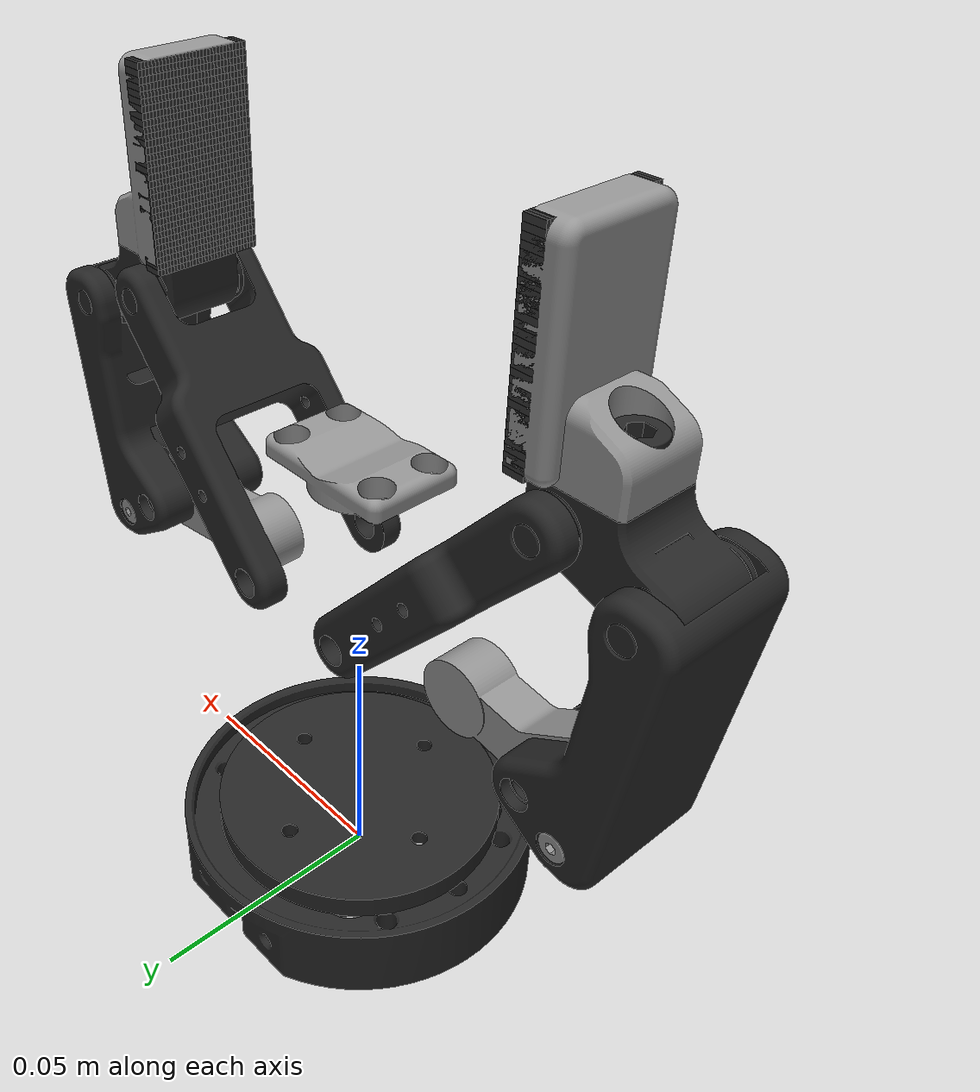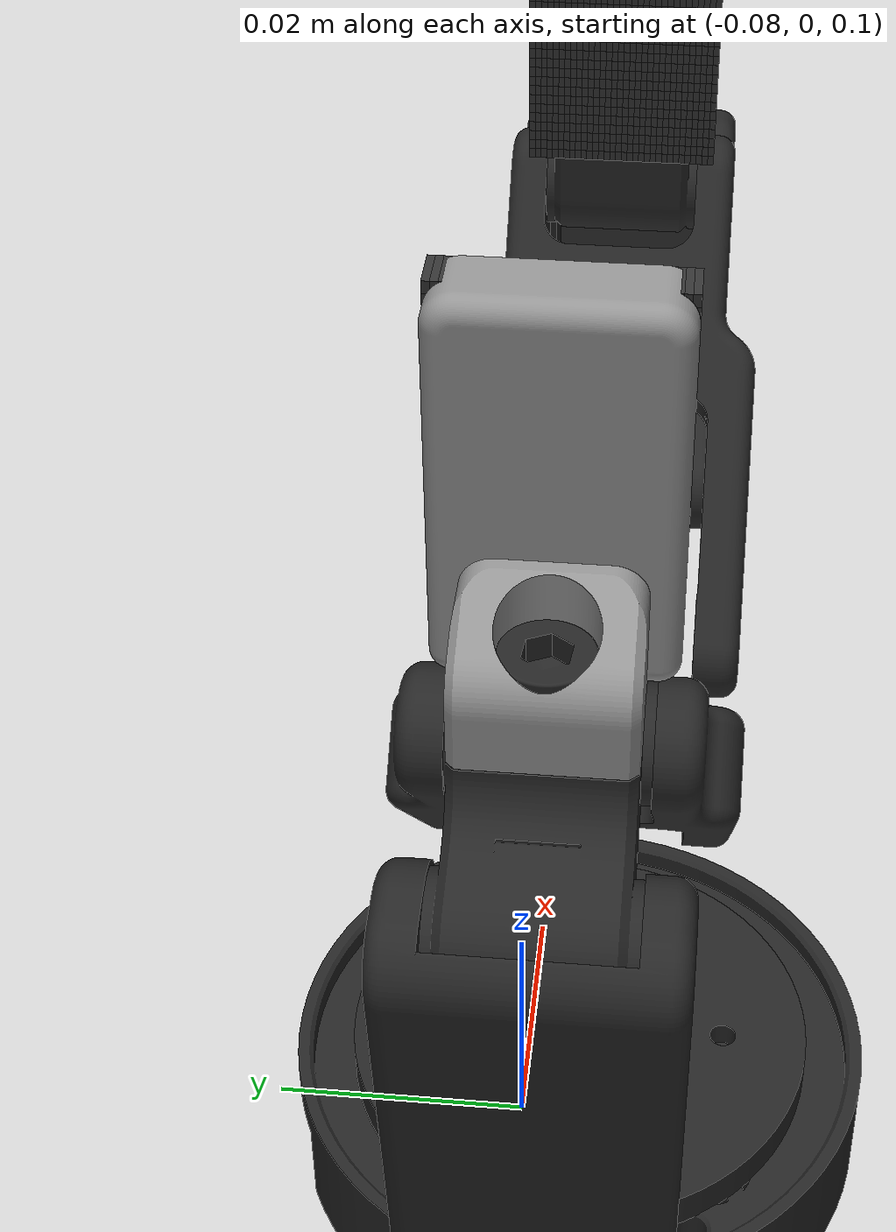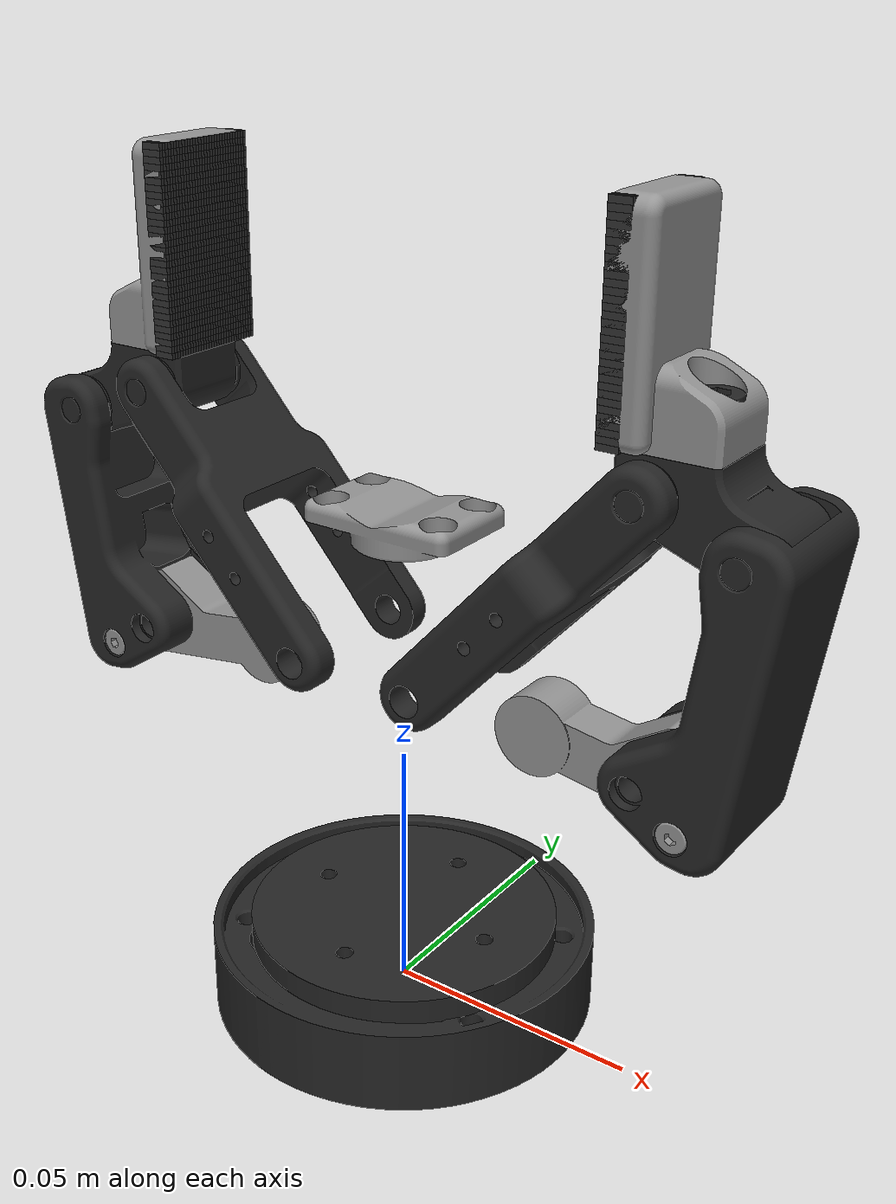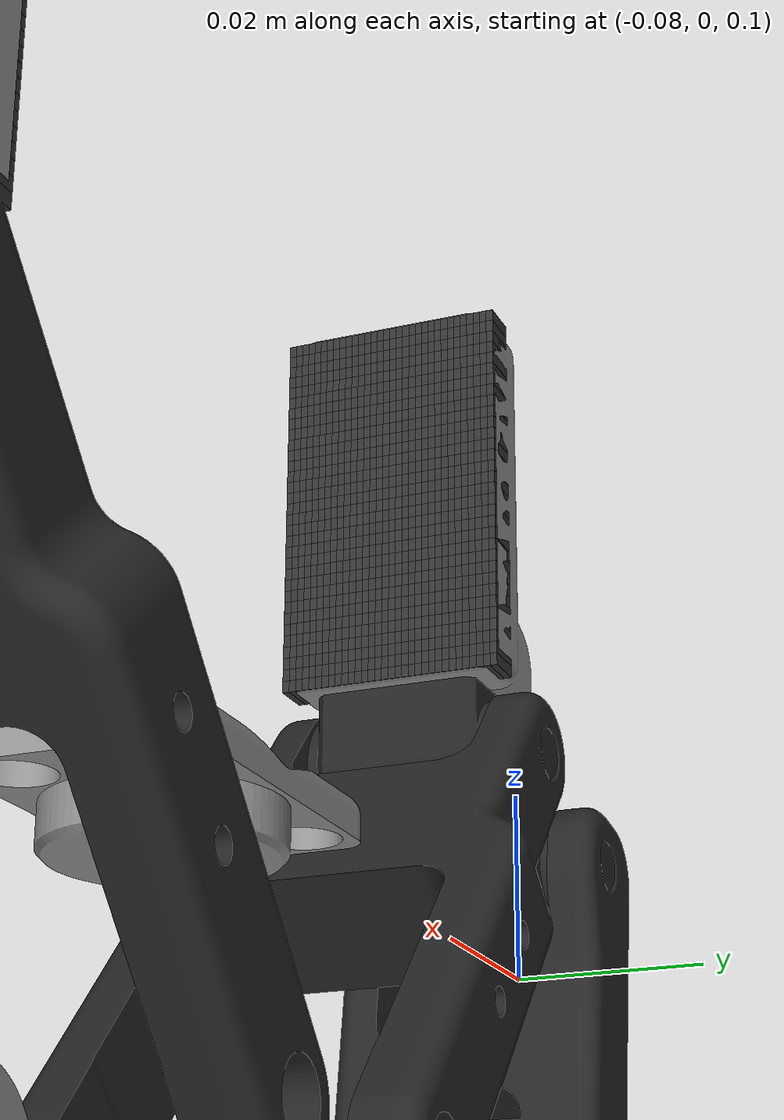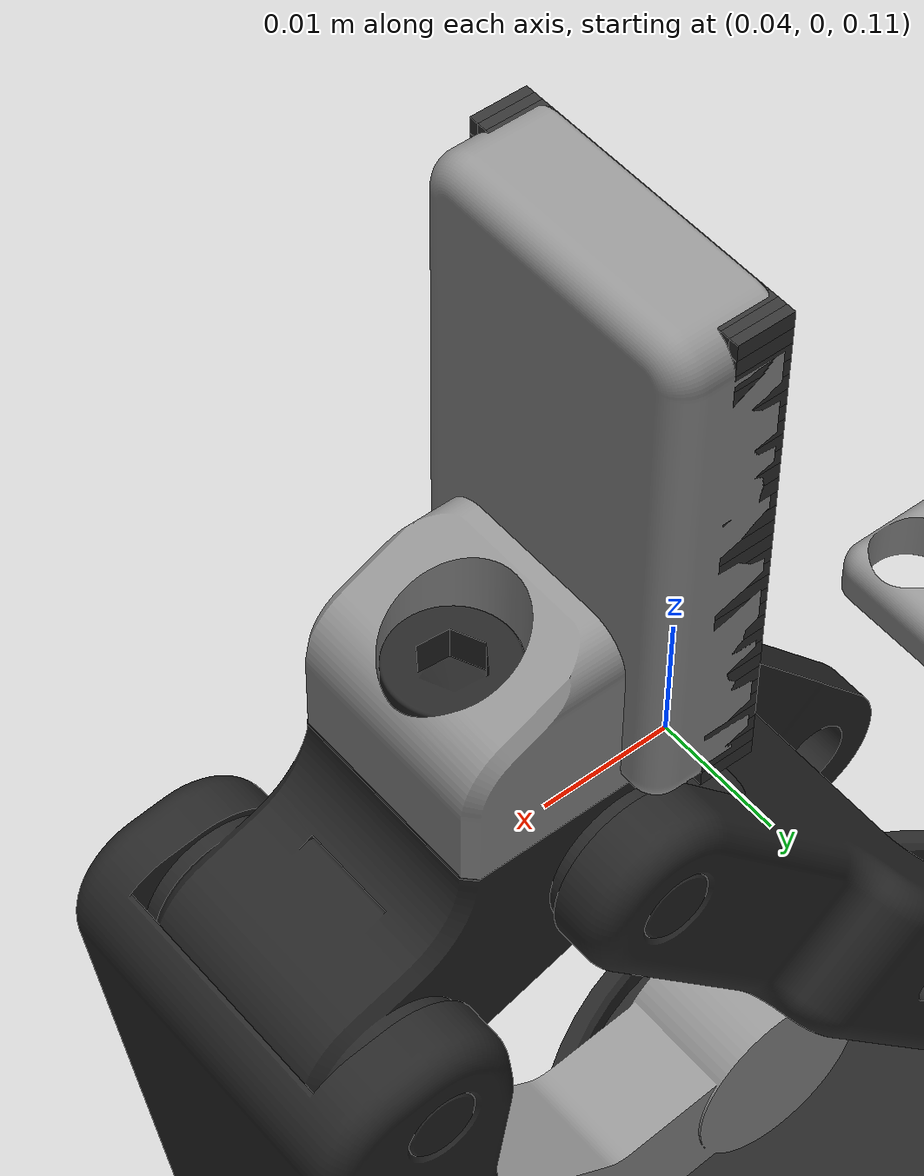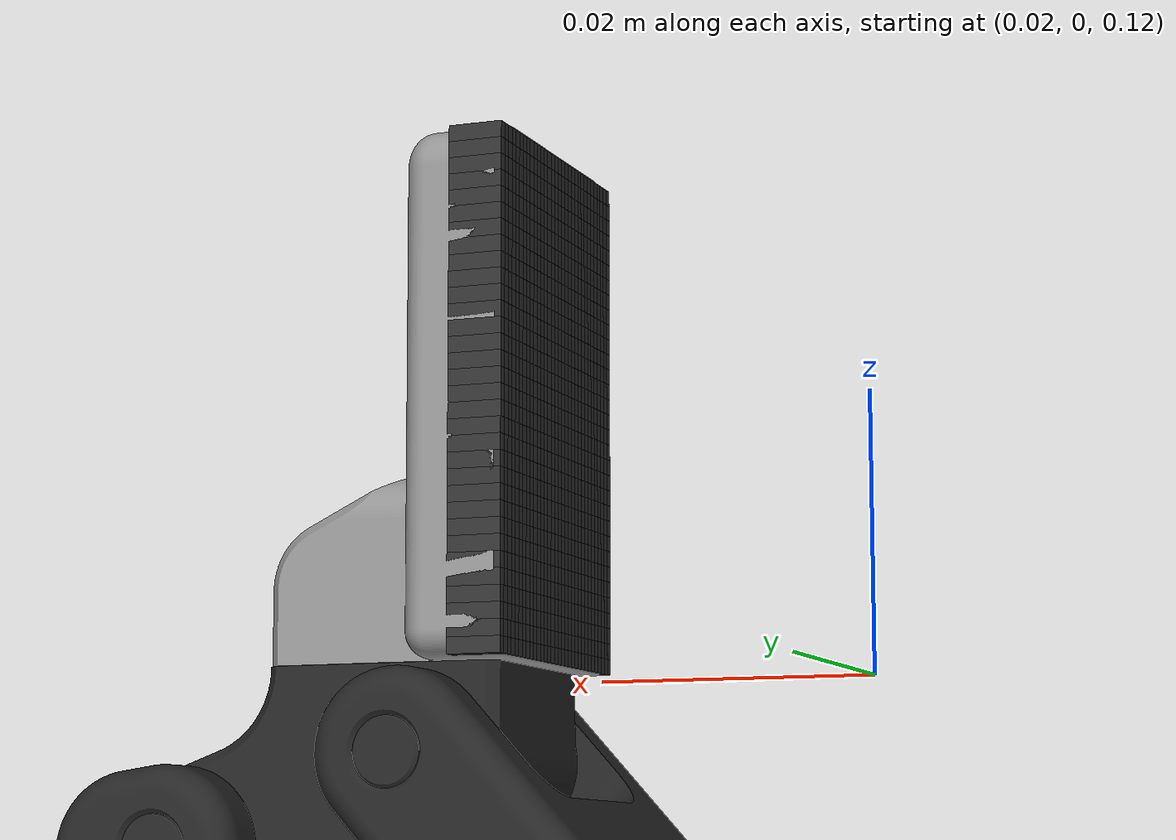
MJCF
<?xml version='1.0' encoding='utf-8'?>
<mujoco model="robotiq_2f85_touch_grid">
  <compiler angle="radian" meshdir="assets" autolimits="true" />
  <option cone="elliptic" impratio="10" />
  <extension>
    <plugin plugin="mujoco.sensor.touch_grid" />
  </extension>
  <size memory="128M" />
  <asset>
    <material name="metal" rgba="0.58 0.58 0.58 1" />
    <material name="silicone" rgba="0.1882 0.1882 0.1882 1" />
    <material name="black" rgba="0.149 0.149 0.149 1" />
    <mesh file="base.stl" />
    <mesh file="base_coupling.stl" />
    <mesh file="c-a01-85-open.stl" />
    <mesh file="driver.stl" />
    <mesh file="coupler.stl" />
    <mesh file="spring_link.stl" />
    <mesh file="follower.stl" />
    <mesh file="tongue.stl" />
  </asset>
  <default>
    <default class="2f85">
      <mesh scale="0.001 0.001 0.001" />
      <general biastype="affine" />
      <joint axis="0 0 1" />
      <default class="driver">
        <joint range="0 0.9" armature="0.005" damping="0.1" solimplimit="0.95 0.99 0.001" solreflimit="0.005 1" />
      </default>
      <default class="follower">
        <joint range="-0.872664 0.9" armature="0.001" solimplimit="0.95 0.99 0.001" solreflimit="0.005 1" />
      </default>
      <default class="spring_link">
        <joint range="-0.29670597283 0.9" armature="0.001" stiffness="0.05" springref="2.62" damping="0.00125" />
      </default>
      <default class="coupler">
        <joint range="-1.57 0" armature="0.001" solimplimit="0.95 0.99 0.001" solreflimit="0.005 1" />
      </default>
      <default class="visual">
        <geom type="mesh" contype="0" conaffinity="0" group="2" material="black" />
      </default>
      <default class="collision">
        <geom type="mesh" group="3" />
        <default class="pad_box1">
          <geom mass="1e-6" type="box" pos="0.043258  0 0.12" size="0.002 0.011 0.009375" friction="0.7" solimp="0.95 0.99 0.001" solref="0.004 1" priority="1" rgba="0.55 0.55 0.55 1" />
        </default>
        <default class="pad_box2">
          <geom mass="1e-6" type="box" pos="0.043258 0 0.13875" size="0.002 0.011 0.009375" friction="0.6" solimp="0.95 0.99 0.001" solref="0.004 1" priority="1" rgba="0.45 0.45 0.45 1" />
        </default>
      </default>
    </default>
  </default>
  <worldbody>
    <body name="base" childclass="2f85">
      <inertial mass="0.777441" pos="0 -2.70394e-05 0.0354675" quat="1 -0.00152849 0 0" diaginertia="0.000260285 0.000225381 0.000152708" />
      <geom class="visual" pos="0 0 0.0108" quat="0 0 0 1" mesh="base" />
      <geom class="visual" pos="0 0 0.004" quat="1 -1 0 0" mesh="base_coupling" />
      <geom class="visual" pos="0 0 0.0108" quat="1 0 0 0" material="metal" mesh="c-a01-85-open" />
      <geom class="collision" mesh="base" />
      <body name="left_driver" pos="-0.0306011 0.00475 0.0657045" quat="1 -1 0 0">
        <inertial mass="0.00899563" pos="0 0.0177547 0.00107314" quat="0.681301 0.732003 0 0" diaginertia="1.72352e-06 1.60906e-06 3.22006e-07" />
        <joint name="left_driver_joint" class="driver" />
        <geom class="visual" pos="0.0306011 0.0549045 -0.0047" quat="1 1 0 0" material="metal" mesh="driver" />
        <geom class="collision" pos="0.0306011 0.0549045 -0.0047" quat="1 1 0 0" mesh="driver" />
        <body name="left_coupler" pos="-0.0314249 0.00453223 -0.0102" quat="0 0 0 1">
          <inertial mass="0.0140974" pos="0 0.00301209 0.0232175" quat="0.705636 -0.0455904 0.0455904 0.705636" diaginertia="4.16206e-06 3.52216e-06 8.88131e-07" />
          <geom class="visual" pos="-0.062026 -0.0503723 0.0055" quat="1 -1 0 0" mesh="coupler" />
          <geom class="collision" pos="-0.062026 -0.0503723 0.0055" quat="1 -1 0 0" mesh="coupler" />
        </body>
      </body>
      <body name="left_spring_link" pos="-0.0127 -0.012 0.07222" quat="1 -1 0 0">
        <inertial mass="0.0221642" pos="-8.65005e-09 0.0181624 0.0212658" quat="0.663403 -0.244737 0.244737 0.663403" diaginertia="8.96853e-06 6.71733e-06 2.63931e-06" />
        <joint name="left_spring_link_joint" class="spring_link" />
        <geom class="visual" pos="0.0127 0.06142 0.01205" quat="1 1 0 0" type="mesh" mesh="spring_link" />
        <geom class="collision" pos="0.0127 0.06142 0.01205" quat="1 1 0 0" type="mesh" mesh="spring_link" />
        <body name="left_follower" pos="-0.0382079 -0.0425003 0.00295" quat="0 -1 -1.90231e-05 0">
          <inertial mass="0.0125222" pos="0 -0.011046 0.0124786" quat="1 0.1664 0 0" diaginertia="2.67415e-06 2.4559e-06 6.02031e-07" />
          <joint name="left_follower" class="follower" />
          <geom class="visual" pos="0.0509079 -0.10392 -0.0091" quat="1 -1 0 0" type="mesh" mesh="follower" />
          <geom class="visual" pos="0.0509079 -0.10392 -0.0091" quat="1 -1 0 0" type="mesh" material="metal" mesh="tongue" />
          <geom class="collision" pos="0.0509079 -0.10392 -0.0091" quat="1 -1 0 0" type="mesh" mesh="follower" />
          <geom class="collision" pos="0.0509079 -0.10392 -0.0091" quat="1 -1 0 0" type="mesh" mesh="tongue" />
          <body name="left_pad" pos="-0.0377897 -0.103916 -0.0091" quat="1 -1 0 0">
            <geom name="left_touch_cell_00_00" type="box" pos="0.043258 -0.010656 0.111211" size="0.002000 0.000344 0.000586" mass="1e-6" friction="0.7 0.03 0.01" solimp="0.90 0.95 0.002" solref="0.015 1" rgba="0.2 0.2 0.2 1" />
            <geom name="left_touch_cell_00_01" type="box" pos="0.043258 -0.009969 0.111211" size="0.002000 0.000344 0.000586" mass="1e-6" friction="0.7 0.03 0.01" solimp="0.90 0.95 0.002" solref="0.015 1" rgba="0.2 0.2 0.2 1" />
            <geom name="left_touch_cell_00_02" type="box" pos="0.043258 -0.009281 0.111211" size="0.002000 0.000344 0.000586" mass="1e-6" friction="0.7 0.03 0.01" solimp="0.90 0.95 0.002" solref="0.015 1" rgba="0.2 0.2 0.2 1" />
            <geom name="left_touch_cell_00_03" type="box" pos="0.043258 -0.008594 0.111211" size="0.002000 0.000344 0.000586" mass="1e-6" friction="0.7 0.03 0.01" solimp="0.90 0.95 0.002" solref="0.015 1" rgba="0.2 0.2 0.2 1" />
            <geom name="left_touch_cell_00_04" type="box" pos="0.043258 -0.007906 0.111211" size="0.002000 0.000344 0.000586" mass="1e-6" friction="0.7 0.03 0.01" solimp="0.90 0.95 0.002" solref="0.015 1" rgba="0.2 0.2 0.2 1" />
            <geom name="left_touch_cell_00_05" type="box" pos="0.043258 -0.007219 0.111211" size="0.002000 0.000344 0.000586" mass="1e-6" friction="0.7 0.03 0.01" solimp="0.90 0.95 0.002" solref="0.015 1" rgba="0.2 0.2 0.2 1" />
            <geom name="left_touch_cell_00_06" type="box" pos="0.043258 -0.006531 0.111211" size="0.002000 0.000344 0.000586" mass="1e-6" friction="0.7 0.03 0.01" solimp="0.90 0.95 0.002" solref="0.015 1" rgba="0.2 0.2 0.2 1" />
            <geom name="left_touch_cell_00_07" type="box" pos="0.043258 -0.005844 0.111211" size="0.002000 0.000344 0.000586" mass="1e-6" friction="0.7 0.03 0.01" solimp="0.90 0.95 0.002" solref="0.015 1" rgba="0.2 0.2 0.2 1" />
            <geom name="left_touch_cell_00_08" type="box" pos="0.043258 -0.005156 0.111211" size="0.002000 0.000344 0.000586" mass="1e-6" friction="0.7 0.03 0.01" solimp="0.90 0.95 0.002" solref="0.015 1" rgba="0.2 0.2 0.2 1" />
            <geom name="left_touch_cell_00_09" type="box" pos="0.043258 -0.004469 0.111211" size="0.002000 0.000344 0.000586" mass="1e-6" friction="0.7 0.03 0.01" solimp="0.90 0.95 0.002" solref="0.015 1" rgba="0.2 0.2 0.2 1" />
            <geom name="left_touch_cell_00_10" type="box" pos="0.043258 -0.003781 0.111211" size="0.002000 0.000344 0.000586" mass="1e-6" friction="0.7 0.03 0.01" solimp="0.90 0.95 0.002" solref="0.015 1" rgba="0.2 0.2 0.2 1" />
            <geom name="left_touch_cell_00_11" type="box" pos="0.043258 -0.003094 0.111211" size="0.002000 0.000344 0.000586" mass="1e-6" friction="0.7 0.03 0.01" solimp="0.90 0.95 0.002" solref="0.015 1" rgba="0.2 0.2 0.2 1" />
            <geom name="left_touch_cell_00_12" type="box" pos="0.043258 -0.002406 0.111211" size="0.002000 0.000344 0.000586" mass="1e-6" friction="0.7 0.03 0.01" solimp="0.90 0.95 0.002" solref="0.015 1" rgba="0.2 0.2 0.2 1" />
            <geom name="left_touch_cell_00_13" type="box" pos="0.043258 -0.001719 0.111211" size="0.002000 0.000344 0.000586" mass="1e-6" friction="0.7 0.03 0.01" solimp="0.90 0.95 0.002" solref="0.015 1" rgba="0.2 0.2 0.2 1" />
            <geom name="left_touch_cell_00_14" type="box" pos="0.043258 -0.001031 0.111211" size="0.002000 0.000344 0.000586" mass="1e-6" friction="0.7 0.03 0.01" solimp="0.90 0.95 0.002" solref="0.015 1" rgba="0.2 0.2 0.2 1" />
            <geom name="left_touch_cell_00_15" type="box" pos="0.043258 -0.000344 0.111211" size="0.002000 0.000344 0.000586" mass="1e-6" friction="0.7 0.03 0.01" solimp="0.90 0.95 0.002" solref="0.015 1" rgba="0.2 0.2 0.2 1" />
            <geom name="left_touch_cell_00_16" type="box" pos="0.043258 0.000344 0.111211" size="0.002000 0.000344 0.000586" mass="1e-6" friction="0.7 0.03 0.01" solimp="0.90 0.95 0.002" solref="0.015 1" rgba="0.2 0.2 0.2 1" />
            <geom name="left_touch_cell_00_17" type="box" pos="0.043258 0.001031 0.111211" size="0.002000 0.000344 0.000586" mass="1e-6" friction="0.7 0.03 0.01" solimp="0.90 0.95 0.002" solref="0.015 1" rgba="0.2 0.2 0.2 1" />
            <geom name="left_touch_cell_00_18" type="box" pos="0.043258 0.001719 0.111211" size="0.002000 0.000344 0.000586" mass="1e-6" friction="0.7 0.03 0.01" solimp="0.90 0.95 0.002" solref="0.015 1" rgba="0.2 0.2 0.2 1" />
            <geom name="left_touch_cell_00_19" type="box" pos="0.043258 0.002406 0.111211" size="0.002000 0.000344 0.000586" mass="1e-6" friction="0.7 0.03 0.01" solimp="0.90 0.95 0.002" solref="0.015 1" rgba="0.2 0.2 0.2 1" />
            <geom name="left_touch_cell_00_20" type="box" pos="0.043258 0.003094 0.111211" size="0.002000 0.000344 0.000586" mass="1e-6" friction="0.7 0.03 0.01" solimp="0.90 0.95 0.002" solref="0.015 1" rgba="0.2 0.2 0.2 1" />
            <geom name="left_touch_cell_00_21" type="box" pos="0.043258 0.003781 0.111211" size="0.002000 0.000344 0.000586" mass="1e-6" friction="0.7 0.03 0.01" solimp="0.90 0.95 0.002" solref="0.015 1" rgba="0.2 0.2 0.2 1" />
            <geom name="left_touch_cell_00_22" type="box" pos="0.043258 0.004469 0.111211" size="0.002000 0.000344 0.000586" mass="1e-6" friction="0.7 0.03 0.01" solimp="0.90 0.95 0.002" solref="0.015 1" rgba="0.2 0.2 0.2 1" />
            <geom name="left_touch_cell_00_23" type="box" pos="0.043258 0.005156 0.111211" size="0.002000 0.000344 0.000586" mass="1e-6" friction="0.7 0.03 0.01" solimp="0.90 0.95 0.002" solref="0.015 1" rgba="0.2 0.2 0.2 1" />
            <geom name="left_touch_cell_00_24" type="box" pos="0.043258 0.005844 0.111211" size="0.002000 0.000344 0.000586" mass="1e-6" friction="0.7 0.03 0.01" solimp="0.90 0.95 0.002" solref="0.015 1" rgba="0.2 0.2 0.2 1" />
            <geom name="left_touch_cell_00_25" type="box" pos="0.043258 0.006531 0.111211" size="0.002000 0.000344 0.000586" mass="1e-6" friction="0.7 0.03 0.01" solimp="0.90 0.95 0.002" solref="0.015 1" rgba="0.2 0.2 0.2 1" />
            <geom name="left_touch_cell_00_26" type="box" pos="0.043258 0.007219 0.111211" size="0.002000 0.000344 0.000586" mass="1e-6" friction="0.7 0.03 0.01" solimp="0.90 0.95 0.002" solref="0.015 1" rgba="0.2 0.2 0.2 1" />
            <geom name="left_touch_cell_00_27" type="box" pos="0.043258 0.007906 0.111211" size="0.002000 0.000344 0.000586" mass="1e-6" friction="0.7 0.03 0.01" solimp="0.90 0.95 0.002" solref="0.015 1" rgba="0.2 0.2 0.2 1" />
            <geom name="left_touch_cell_00_28" type="box" pos="0.043258 0.008594 0.111211" size="0.002000 0.000344 0.000586" mass="1e-6" friction="0.7 0.03 0.01" solimp="0.90 0.95 0.002" solref="0.015 1" rgba="0.2 0.2 0.2 1" />
            <geom name="left_touch_cell_00_29" type="box" pos="0.043258 0.009281 0.111211" size="0.002000 0.000344 0.000586" mass="1e-6" friction="0.7 0.03 0.01" solimp="0.90 0.95 0.002" solref="0.015 1" rgba="0.2 0.2 0.2 1" />
            <geom name="left_touch_cell_00_30" type="box" pos="0.043258 0.009969 0.111211" size="0.002000 0.000344 0.000586" mass="1e-6" friction="0.7 0.03 0.01" solimp="0.90 0.95 0.002" solref="0.015 1" rgba="0.2 0.2 0.2 1" />
            <geom name="left_touch_cell_00_31" type="box" pos="0.043258 0.010656 0.111211" size="0.002000 0.000344 0.000586" mass="1e-6" friction="0.7 0.03 0.01" solimp="0.90 0.95 0.002" solref="0.015 1" rgba="0.2 0.2 0.2 1" />
            <geom name="left_touch_cell_01_00" type="box" pos="0.043258 -0.010656 0.112383" size="0.002000 0.000344 0.000586" mass="1e-6" friction="0.7 0.03 0.01" solimp="0.90 0.95 0.002" solref="0.015 1" rgba="0.2 0.2 0.2 1" />
            <geom name="left_touch_cell_01_01" type="box" pos="0.043258 -0.009969 0.112383" size="0.002000 0.000344 0.000586" mass="1e-6" friction="0.7 0.03 0.01" solimp="0.90 0.95 0.002" solref="0.015 1" rgba="0.2 0.2 0.2 1" />
            <geom name="left_touch_cell_01_02" type="box" pos="0.043258 -0.009281 0.112383" size="0.002000 0.000344 0.000586" mass="1e-6" friction="0.7 0.03 0.01" solimp="0.90 0.95 0.002" solref="0.015 1" rgba="0.2 0.2 0.2 1" />
            <geom name="left_touch_cell_01_03" type="box" pos="0.043258 -0.008594 0.112383" size="0.002000 0.000344 0.000586" mass="1e-6" friction="0.7 0.03 0.01" solimp="0.90 0.95 0.002" solref="0.015 1" rgba="0.2 0.2 0.2 1" />
            <geom name="left_touch_cell_01_04" type="box" pos="0.043258 -0.007906 0.112383" size="0.002000 0.000344 0.000586" mass="1e-6" friction="0.7 0.03 0.01" solimp="0.90 0.95 0.002" solref="0.015 1" rgba="0.2 0.2 0.2 1" />
            <geom name="left_touch_cell_01_05" type="box" pos="0.043258 -0.007219 0.112383" size="0.002000 0.000344 0.000586" mass="1e-6" friction="0.7 0.03 0.01" solimp="0.90 0.95 0.002" solref="0.015 1" rgba="0.2 0.2 0.2 1" />
            <geom name="left_touch_cell_01_06" type="box" pos="0.043258 -0.006531 0.112383" size="0.002000 0.000344 0.000586" mass="1e-6" friction="0.7 0.03 0.01" solimp="0.90 0.95 0.002" solref="0.015 1" rgba="0.2 0.2 0.2 1" />
            <geom name="left_touch_cell_01_07" type="box" pos="0.043258 -0.005844 0.112383" size="0.002000 0.000344 0.000586" mass="1e-6" friction="0.7 0.03 0.01" solimp="0.90 0.95 0.002" solref="0.015 1" rgba="0.2 0.2 0.2 1" />
            <geom name="left_touch_cell_01_08" type="box" pos="0.043258 -0.005156 0.112383" size="0.002000 0.000344 0.000586" mass="1e-6" friction="0.7 0.03 0.01" solimp="0.90 0.95 0.002" solref="0.015 1" rgba="0.2 0.2 0.2 1" />
            <geom name="left_touch_cell_01_09" type="box" pos="0.043258 -0.004469 0.112383" size="0.002000 0.000344 0.000586" mass="1e-6" friction="0.7 0.03 0.01" solimp="0.90 0.95 0.002" solref="0.015 1" rgba="0.2 0.2 0.2 1" />
            <geom name="left_touch_cell_01_10" type="box" pos="0.043258 -0.003781 0.112383" size="0.002000 0.000344 0.000586" mass="1e-6" friction="0.7 0.03 0.01" solimp="0.90 0.95 0.002" solref="0.015 1" rgba="0.2 0.2 0.2 1" />
            <geom name="left_touch_cell_01_11" type="box" pos="0.043258 -0.003094 0.112383" size="0.002000 0.000344 0.000586" mass="1e-6" friction="0.7 0.03 0.01" solimp="0.90 0.95 0.002" solref="0.015 1" rgba="0.2 0.2 0.2 1" />
            <geom name="left_touch_cell_01_12" type="box" pos="0.043258 -0.002406 0.112383" size="0.002000 0.000344 0.000586" mass="1e-6" friction="0.7 0.03 0.01" solimp="0.90 0.95 0.002" solref="0.015 1" rgba="0.2 0.2 0.2 1" />
            <geom name="left_touch_cell_01_13" type="box" pos="0.043258 -0.001719 0.112383" size="0.002000 0.000344 0.000586" mass="1e-6" friction="0.7 0.03 0.01" solimp="0.90 0.95 0.002" solref="0.015 1" rgba="0.2 0.2 0.2 1" />
            <geom name="left_touch_cell_01_14" type="box" pos="0.043258 -0.001031 0.112383" size="0.002000 0.000344 0.000586" mass="1e-6" friction="0.7 0.03 0.01" solimp="0.90 0.95 0.002" solref="0.015 1" rgba="0.2 0.2 0.2 1" />
            <geom name="left_touch_cell_01_15" type="box" pos="0.043258 -0.000344 0.112383" size="0.002000 0.000344 0.000586" mass="1e-6" friction="0.7 0.03 0.01" solimp="0.90 0.95 0.002" solref="0.015 1" rgba="0.2 0.2 0.2 1" />
            <geom name="left_touch_cell_01_16" type="box" pos="0.043258 0.000344 0.112383" size="0.002000 0.000344 0.000586" mass="1e-6" friction="0.7 0.03 0.01" solimp="0.90 0.95 0.002" solref="0.015 1" rgba="0.2 0.2 0.2 1" />
            <geom name="left_touch_cell_01_17" type="box" pos="0.043258 0.001031 0.112383" size="0.002000 0.000344 0.000586" mass="1e-6" friction="0.7 0.03 0.01" solimp="0.90 0.95 0.002" solref="0.015 1" rgba="0.2 0.2 0.2 1" />
            <geom name="left_touch_cell_01_18" type="box" pos="0.043258 0.001719 0.112383" size="0.002000 0.000344 0.000586" mass="1e-6" friction="0.7 0.03 0.01" solimp="0.90 0.95 0.002" solref="0.015 1" rgba="0.2 0.2 0.2 1" />
            <geom name="left_touch_cell_01_19" type="box" pos="0.043258 0.002406 0.112383" size="0.002000 0.000344 0.000586" mass="1e-6" friction="0.7 0.03 0.01" solimp="0.90 0.95 0.002" solref="0.015 1" rgba="0.2 0.2 0.2 1" />
            <geom name="left_touch_cell_01_20" type="box" pos="0.043258 0.003094 0.112383" size="0.002000 0.000344 0.000586" mass="1e-6" friction="0.7 0.03 0.01" solimp="0.90 0.95 0.002" solref="0.015 1" rgba="0.2 0.2 0.2 1" />
            <geom name="left_touch_cell_01_21" type="box" pos="0.043258 0.003781 0.112383" size="0.002000 0.000344 0.000586" mass="1e-6" friction="0.7 0.03 0.01" solimp="0.90 0.95 0.002" solref="0.015 1" rgba="0.2 0.2 0.2 1" />
            <geom name="left_touch_cell_01_22" type="box" pos="0.043258 0.004469 0.112383" size="0.002000 0.000344 0.000586" mass="1e-6" friction="0.7 0.03 0.01" solimp="0.90 0.95 0.002" solref="0.015 1" rgba="0.2 0.2 0.2 1" />
            <geom name="left_touch_cell_01_23" type="box" pos="0.043258 0.005156 0.112383" size="0.002000 0.000344 0.000586" mass="1e-6" friction="0.7 0.03 0.01" solimp="0.90 0.95 0.002" solref="0.015 1" rgba="0.2 0.2 0.2 1" />
            <geom name="left_touch_cell_01_24" type="box" pos="0.043258 0.005844 0.112383" size="0.002000 0.000344 0.000586" mass="1e-6" friction="0.7 0.03 0.01" solimp="0.90 0.95 0.002" solref="0.015 1" rgba="0.2 0.2 0.2 1" />
            <geom name="left_touch_cell_01_25" type="box" pos="0.043258 0.006531 0.112383" size="0.002000 0.000344 0.000586" mass="1e-6" friction="0.7 0.03 0.01" solimp="0.90 0.95 0.002" solref="0.015 1" rgba="0.2 0.2 0.2 1" />
            <geom name="left_touch_cell_01_26" type="box" pos="0.043258 0.007219 0.112383" size="0.002000 0.000344 0.000586" mass="1e-6" friction="0.7 0.03 0.01" solimp="0.90 0.95 0.002" solref="0.015 1" rgba="0.2 0.2 0.2 1" />
            <geom name="left_touch_cell_01_27" type="box" pos="0.043258 0.007906 0.112383" size="0.002000 0.000344 0.000586" mass="1e-6" friction="0.7 0.03 0.01" solimp="0.90 0.95 0.002" solref="0.015 1" rgba="0.2 0.2 0.2 1" />
            <geom name="left_touch_cell_01_28" type="box" pos="0.043258 0.008594 0.112383" size="0.002000 0.000344 0.000586" mass="1e-6" friction="0.7 0.03 0.01" solimp="0.90 0.95 0.002" solref="0.015 1" rgba="0.2 0.2 0.2 1" />
            <geom name="left_touch_cell_01_29" type="box" pos="0.043258 0.009281 0.112383" size="0.002000 0.000344 0.000586" mass="1e-6" friction="0.7 0.03 0.01" solimp="0.90 0.95 0.002" solref="0.015 1" rgba="0.2 0.2 0.2 1" />
            <geom name="left_touch_cell_01_30" type="box" pos="0.043258 0.009969 0.112383" size="0.002000 0.000344 0.000586" mass="1e-6" friction="0.7 0.03 0.01" solimp="0.90 0.95 0.002" solref="0.015 1" rgba="0.2 0.2 0.2 1" />
            <geom name="left_touch_cell_01_31" type="box" pos="0.043258 0.010656 0.112383" size="0.002000 0.000344 0.000586" mass="1e-6" friction="0.7 0.03 0.01" solimp="0.90 0.95 0.002" solref="0.015 1" rgba="0.2 0.2 0.2 1" />
            <geom name="left_touch_cell_02_00" type="box" pos="0.043258 -0.010656 0.113555" size="0.002000 0.000344 0.000586" mass="1e-6" friction="0.7 0.03 0.01" solimp="0.90 0.95 0.002" solref="0.015 1" rgba="0.2 0.2 0.2 1" />
            <geom name="left_touch_cell_02_01" type="box" pos="0.043258 -0.009969 0.113555" size="0.002000 0.000344 0.000586" mass="1e-6" friction="0.7 0.03 0.01" solimp="0.90 0.95 0.002" solref="0.015 1" rgba="0.2 0.2 0.2 1" />
            <geom name="left_touch_cell_02_02" type="box" pos="0.043258 -0.009281 0.113555" size="0.002000 0.000344 0.000586" mass="1e-6" friction="0.7 0.03 0.01" solimp="0.90 0.95 0.002" solref="0.015 1" rgba="0.2 0.2 0.2 1" />
            <geom name="left_touch_cell_02_03" type="box" pos="0.043258 -0.008594 0.113555" size="0.002000 0.000344 0.000586" mass="1e-6" friction="0.7 0.03 0.01" solimp="0.90 0.95 0.002" solref="0.015 1" rgba="0.2 0.2 0.2 1" />
            <geom name="left_touch_cell_02_04" type="box" pos="0.043258 -0.007906 0.113555" size="0.002000 0.000344 0.000586" mass="1e-6" friction="0.7 0.03 0.01" solimp="0.90 0.95 0.002" solref="0.015 1" rgba="0.2 0.2 0.2 1" />
            <geom name="left_touch_cell_02_05" type="box" pos="0.043258 -0.007219 0.113555" size="0.002000 0.000344 0.000586" mass="1e-6" friction="0.7 0.03 0.01" solimp="0.90 0.95 0.002" solref="0.015 1" rgba="0.2 0.2 0.2 1" />
            <geom name="left_touch_cell_02_06" type="box" pos="0.043258 -0.006531 0.113555" size="0.002000 0.000344 0.000586" mass="1e-6" friction="0.7 0.03 0.01" solimp="0.90 0.95 0.002" solref="0.015 1" rgba="0.2 0.2 0.2 1" />
            <geom name="left_touch_cell_02_07" type="box" pos="0.043258 -0.005844 0.113555" size="0.002000 0.000344 0.000586" mass="1e-6" friction="0.7 0.03 0.01" solimp="0.90 0.95 0.002" solref="0.015 1" rgba="0.2 0.2 0.2 1" />
            <geom name="left_touch_cell_02_08" type="box" pos="0.043258 -0.005156 0.113555" size="0.002000 0.000344 0.000586" mass="1e-6" friction="0.7 0.03 0.01" solimp="0.90 0.95 0.002" solref="0.015 1" rgba="0.2 0.2 0.2 1" />
            <geom name="left_touch_cell_02_09" type="box" pos="0.043258 -0.004469 0.113555" size="0.002000 0.000344 0.000586" mass="1e-6" friction="0.7 0.03 0.01" solimp="0.90 0.95 0.002" solref="0.015 1" rgba="0.2 0.2 0.2 1" />
            <geom name="left_touch_cell_02_10" type="box" pos="0.043258 -0.003781 0.113555" size="0.002000 0.000344 0.000586" mass="1e-6" friction="0.7 0.03 0.01" solimp="0.90 0.95 0.002" solref="0.015 1" rgba="0.2 0.2 0.2 1" />
            <geom name="left_touch_cell_02_11" type="box" pos="0.043258 -0.003094 0.113555" size="0.002000 0.000344 0.000586" mass="1e-6" friction="0.7 0.03 0.01" solimp="0.90 0.95 0.002" solref="0.015 1" rgba="0.2 0.2 0.2 1" />
            <geom name="left_touch_cell_02_12" type="box" pos="0.043258 -0.002406 0.113555" size="0.002000 0.000344 0.000586" mass="1e-6" friction="0.7 0.03 0.01" solimp="0.90 0.95 0.002" solref="0.015 1" rgba="0.2 0.2 0.2 1" />
            <geom name="left_touch_cell_02_13" type="box" pos="0.043258 -0.001719 0.113555" size="0.002000 0.000344 0.000586" mass="1e-6" friction="0.7 0.03 0.01" solimp="0.90 0.95 0.002" solref="0.015 1" rgba="0.2 0.2 0.2 1" />
            <geom name="left_touch_cell_02_14" type="box" pos="0.043258 -0.001031 0.113555" size="0.002000 0.000344 0.000586" mass="1e-6" friction="0.7 0.03 0.01" solimp="0.90 0.95 0.002" solref="0.015 1" rgba="0.2 0.2 0.2 1" />
            <geom name="left_touch_cell_02_15" type="box" pos="0.043258 -0.000344 0.113555" size="0.002000 0.000344 0.000586" mass="1e-6" friction="0.7 0.03 0.01" solimp="0.90 0.95 0.002" solref="0.015 1" rgba="0.2 0.2 0.2 1" />
            <geom name="left_touch_cell_02_16" type="box" pos="0.043258 0.000344 0.113555" size="0.002000 0.000344 0.000586" mass="1e-6" friction="0.7 0.03 0.01" solimp="0.90 0.95 0.002" solref="0.015 1" rgba="0.2 0.2 0.2 1" />
            <geom name="left_touch_cell_02_17" type="box" pos="0.043258 0.001031 0.113555" size="0.002000 0.000344 0.000586" mass="1e-6" friction="0.7 0.03 0.01" solimp="0.90 0.95 0.002" solref="0.015 1" rgba="0.2 0.2 0.2 1" />
            <geom name="left_touch_cell_02_18" type="box" pos="0.043258 0.001719 0.113555" size="0.002000 0.000344 0.000586" mass="1e-6" friction="0.7 0.03 0.01" solimp="0.90 0.95 0.002" solref="0.015 1" rgba="0.2 0.2 0.2 1" />
            <geom name="left_touch_cell_02_19" type="box" pos="0.043258 0.002406 0.113555" size="0.002000 0.000344 0.000586" mass="1e-6" friction="0.7 0.03 0.01" solimp="0.90 0.95 0.002" solref="0.015 1" rgba="0.2 0.2 0.2 1" />
            <geom name="left_touch_cell_02_20" type="box" pos="0.043258 0.003094 0.113555" size="0.002000 0.000344 0.000586" mass="1e-6" friction="0.7 0.03 0.01" solimp="0.90 0.95 0.002" solref="0.015 1" rgba="0.2 0.2 0.2 1" />
            <geom name="left_touch_cell_02_21" type="box" pos="0.043258 0.003781 0.113555" size="0.002000 0.000344 0.000586" mass="1e-6" friction="0.7 0.03 0.01" solimp="0.90 0.95 0.002" solref="0.015 1" rgba="0.2 0.2 0.2 1" />
            <geom name="left_touch_cell_02_22" type="box" pos="0.043258 0.004469 0.113555" size="0.002000 0.000344 0.000586" mass="1e-6" friction="0.7 0.03 0.01" solimp="0.90 0.95 0.002" solref="0.015 1" rgba="0.2 0.2 0.2 1" />
            <geom name="left_touch_cell_02_23" type="box" pos="0.043258 0.005156 0.113555" size="0.002000 0.000344 0.000586" mass="1e-6" friction="0.7 0.03 0.01" solimp="0.90 0.95 0.002" solref="0.015 1" rgba="0.2 0.2 0.2 1" />
            <geom name="left_touch_cell_02_24" type="box" pos="0.043258 0.005844 0.113555" size="0.002000 0.000344 0.000586" mass="1e-6" friction="0.7 0.03 0.01" solimp="0.90 0.95 0.002" solref="0.015 1" rgba="0.2 0.2 0.2 1" />
            <geom name="left_touch_cell_02_25" type="box" pos="0.043258 0.006531 0.113555" size="0.002000 0.000344 0.000586" mass="1e-6" friction="0.7 0.03 0.01" solimp="0.90 0.95 0.002" solref="0.015 1" rgba="0.2 0.2 0.2 1" />
            <geom name="left_touch_cell_02_26" type="box" pos="0.043258 0.007219 0.113555" size="0.002000 0.000344 0.000586" mass="1e-6" friction="0.7 0.03 0.01" solimp="0.90 0.95 0.002" solref="0.015 1" rgba="0.2 0.2 0.2 1" />
            <geom name="left_touch_cell_02_27" type="box" pos="0.043258 0.007906 0.113555" size="0.002000 0.000344 0.000586" mass="1e-6" friction="0.7 0.03 0.01" solimp="0.90 0.95 0.002" solref="0.015 1" rgba="0.2 0.2 0.2 1" />
            <geom name="left_touch_cell_02_28" type="box" pos="0.043258 0.008594 0.113555" size="0.002000 0.000344 0.000586" mass="1e-6" friction="0.7 0.03 0.01" solimp="0.90 0.95 0.002" solref="0.015 1" rgba="0.2 0.2 0.2 1" />
            <geom name="left_touch_cell_02_29" type="box" pos="0.043258 0.009281 0.113555" size="0.002000 0.000344 0.000586" mass="1e-6" friction="0.7 0.03 0.01" solimp="0.90 0.95 0.002" solref="0.015 1" rgba="0.2 0.2 0.2 1" />
            <geom name="left_touch_cell_02_30" type="box" pos="0.043258 0.009969 0.113555" size="0.002000 0.000344 0.000586" mass="1e-6" friction="0.7 0.03 0.01" solimp="0.90 0.95 0.002" solref="0.015 1" rgba="0.2 0.2 0.2 1" />
            <geom name="left_touch_cell_02_31" type="box" pos="0.043258 0.010656 0.113555" size="0.002000 0.000344 0.000586" mass="1e-6" friction="0.7 0.03 0.01" solimp="0.90 0.95 0.002" solref="0.015 1" rgba="0.2 0.2 0.2 1" />
            <geom name="left_touch_cell_03_00" type="box" pos="0.043258 -0.010656 0.114727" size="0.002000 0.000344 0.000586" mass="1e-6" friction="0.7 0.03 0.01" solimp="0.90 0.95 0.002" solref="0.015 1" rgba="0.2 0.2 0.2 1" />
            <geom name="left_touch_cell_03_01" type="box" pos="0.043258 -0.009969 0.114727" size="0.002000 0.000344 0.000586" mass="1e-6" friction="0.7 0.03 0.01" solimp="0.90 0.95 0.002" solref="0.015 1" rgba="0.2 0.2 0.2 1" />
            <geom name="left_touch_cell_03_02" type="box" pos="0.043258 -0.009281 0.114727" size="0.002000 0.000344 0.000586" mass="1e-6" friction="0.7 0.03 0.01" solimp="0.90 0.95 0.002" solref="0.015 1" rgba="0.2 0.2 0.2 1" />
            <geom name="left_touch_cell_03_03" type="box" pos="0.043258 -0.008594 0.114727" size="0.002000 0.000344 0.000586" mass="1e-6" friction="0.7 0.03 0.01" solimp="0.90 0.95 0.002" solref="0.015 1" rgba="0.2 0.2 0.2 1" />
            <geom name="left_touch_cell_03_04" type="box" pos="0.043258 -0.007906 0.114727" size="0.002000 0.000344 0.000586" mass="1e-6" friction="0.7 0.03 0.01" solimp="0.90 0.95 0.002" solref="0.015 1" rgba="0.2 0.2 0.2 1" />
            <geom name="left_touch_cell_03_05" type="box" pos="0.043258 -0.007219 0.114727" size="0.002000 0.000344 0.000586" mass="1e-6" friction="0.7 0.03 0.01" solimp="0.90 0.95 0.002" solref="0.015 1" rgba="0.2 0.2 0.2 1" />
            <geom name="left_touch_cell_03_06" type="box" pos="0.043258 -0.006531 0.114727" size="0.002000 0.000344 0.000586" mass="1e-6" friction="0.7 0.03 0.01" solimp="0.90 0.95 0.002" solref="0.015 1" rgba="0.2 0.2 0.2 1" />
            <geom name="left_touch_cell_03_07" type="box" pos="0.043258 -0.005844 0.114727" size="0.002000 0.000344 0.000586" mass="1e-6" friction="0.7 0.03 0.01" solimp="0.90 0.95 0.002" solref="0.015 1" rgba="0.2 0.2 0.2 1" />
            <geom name="left_touch_cell_03_08" type="box" pos="0.043258 -0.005156 0.114727" size="0.002000 0.000344 0.000586" mass="1e-6" friction="0.7 0.03 0.01" solimp="0.90 0.95 0.002" solref="0.015 1" rgba="0.2 0.2 0.2 1" />
            <geom name="left_touch_cell_03_09" type="box" pos="0.043258 -0.004469 0.114727" size="0.002000 0.000344 0.000586" mass="1e-6" friction="0.7 0.03 0.01" solimp="0.90 0.95 0.002" solref="0.015 1" rgba="0.2 0.2 0.2 1" />
            <geom name="left_touch_cell_03_10" type="box" pos="0.043258 -0.003781 0.114727" size="0.002000 0.000344 0.000586" mass="1e-6" friction="0.7 0.03 0.01" solimp="0.90 0.95 0.002" solref="0.015 1" rgba="0.2 0.2 0.2 1" />
            <geom name="left_touch_cell_03_11" type="box" pos="0.043258 -0.003094 0.114727" size="0.002000 0.000344 0.000586" mass="1e-6" friction="0.7 0.03 0.01" solimp="0.90 0.95 0.002" solref="0.015 1" rgba="0.2 0.2 0.2 1" />
            <geom name="left_touch_cell_03_12" type="box" pos="0.043258 -0.002406 0.114727" size="0.002000 0.000344 0.000586" mass="1e-6" friction="0.7 0.03 0.01" solimp="0.90 0.95 0.002" solref="0.015 1" rgba="0.2 0.2 0.2 1" />
            <geom name="left_touch_cell_03_13" type="box" pos="0.043258 -0.001719 0.114727" size="0.002000 0.000344 0.000586" mass="1e-6" friction="0.7 0.03 0.01" solimp="0.90 0.95 0.002" solref="0.015 1" rgba="0.2 0.2 0.2 1" />
            <geom name="left_touch_cell_03_14" type="box" pos="0.043258 -0.001031 0.114727" size="0.002000 0.000344 0.000586" mass="1e-6" friction="0.7 0.03 0.01" solimp="0.90 0.95 0.002" solref="0.015 1" rgba="0.2 0.2 0.2 1" />
            <geom name="left_touch_cell_03_15" type="box" pos="0.043258 -0.000344 0.114727" size="0.002000 0.000344 0.000586" mass="1e-6" friction="0.7 0.03 0.01" solimp="0.90 0.95 0.002" solref="0.015 1" rgba="0.2 0.2 0.2 1" />
            <geom name="left_touch_cell_03_16" type="box" pos="0.043258 0.000344 0.114727" size="0.002000 0.000344 0.000586" mass="1e-6" friction="0.7 0.03 0.01" solimp="0.90 0.95 0.002" solref="0.015 1" rgba="0.2 0.2 0.2 1" />
            <geom name="left_touch_cell_03_17" type="box" pos="0.043258 0.001031 0.114727" size="0.002000 0.000344 0.000586" mass="1e-6" friction="0.7 0.03 0.01" solimp="0.90 0.95 0.002" solref="0.015 1" rgba="0.2 0.2 0.2 1" />
            <geom name="left_touch_cell_03_18" type="box" pos="0.043258 0.001719 0.114727" size="0.002000 0.000344 0.000586" mass="1e-6" friction="0.7 0.03 0.01" solimp="0.90 0.95 0.002" solref="0.015 1" rgba="0.2 0.2 0.2 1" />
            <geom name="left_touch_cell_03_19" type="box" pos="0.043258 0.002406 0.114727" size="0.002000 0.000344 0.000586" mass="1e-6" friction="0.7 0.03 0.01" solimp="0.90 0.95 0.002" solref="0.015 1" rgba="0.2 0.2 0.2 1" />
            <geom name="left_touch_cell_03_20" type="box" pos="0.043258 0.003094 0.114727" size="0.002000 0.000344 0.000586" mass="1e-6" friction="0.7 0.03 0.01" solimp="0.90 0.95 0.002" solref="0.015 1" rgba="0.2 0.2 0.2 1" />
            <geom name="left_touch_cell_03_21" type="box" pos="0.043258 0.003781 0.114727" size="0.002000 0.000344 0.000586" mass="1e-6" friction="0.7 0.03 0.01" solimp="0.90 0.95 0.002" solref="0.015 1" rgba="0.2 0.2 0.2 1" />
            <geom name="left_touch_cell_03_22" type="box" pos="0.043258 0.004469 0.114727" size="0.002000 0.000344 0.000586" mass="1e-6" friction="0.7 0.03 0.01" solimp="0.90 0.95 0.002" solref="0.015 1" rgba="0.2 0.2 0.2 1" />
            <geom name="left_touch_cell_03_23" type="box" pos="0.043258 0.005156 0.114727" size="0.002000 0.000344 0.000586" mass="1e-6" friction="0.7 0.03 0.01" solimp="0.90 0.95 0.002" solref="0.015 1" rgba="0.2 0.2 0.2 1" />
            <geom name="left_touch_cell_03_24" type="box" pos="0.043258 0.005844 0.114727" size="0.002000 0.000344 0.000586" mass="1e-6" friction="0.7 0.03 0.01" solimp="0.90 0.95 0.002" solref="0.015 1" rgba="0.2 0.2 0.2 1" />
            <geom name="left_touch_cell_03_25" type="box" pos="0.043258 0.006531 0.114727" size="0.002000 0.000344 0.000586" mass="1e-6" friction="0.7 0.03 0.01" solimp="0.90 0.95 0.002" solref="0.015 1" rgba="0.2 0.2 0.2 1" />
            <geom name="left_touch_cell_03_26" type="box" pos="0.043258 0.007219 0.114727" size="0.002000 0.000344 0.000586" mass="1e-6" friction="0.7 0.03 0.01" solimp="0.90 0.95 0.002" solref="0.015 1" rgba="0.2 0.2 0.2 1" />
            <geom name="left_touch_cell_03_27" type="box" pos="0.043258 0.007906 0.114727" size="0.002000 0.000344 0.000586" mass="1e-6" friction="0.7 0.03 0.01" solimp="0.90 0.95 0.002" solref="0.015 1" rgba="0.2 0.2 0.2 1" />
            <geom name="left_touch_cell_03_28" type="box" pos="0.043258 0.008594 0.114727" size="0.002000 0.000344 0.000586" mass="1e-6" friction="0.7 0.03 0.01" solimp="0.90 0.95 0.002" solref="0.015 1" rgba="0.2 0.2 0.2 1" />
            <geom name="left_touch_cell_03_29" type="box" pos="0.043258 0.009281 0.114727" size="0.002000 0.000344 0.000586" mass="1e-6" friction="0.7 0.03 0.01" solimp="0.90 0.95 0.002" solref="0.015 1" rgba="0.2 0.2 0.2 1" />
            <geom name="left_touch_cell_03_30" type="box" pos="0.043258 0.009969 0.114727" size="0.002000 0.000344 0.000586" mass="1e-6" friction="0.7 0.03 0.01" solimp="0.90 0.95 0.002" solref="0.015 1" rgba="0.2 0.2 0.2 1" />
            <geom name="left_touch_cell_03_31" type="box" pos="0.043258 0.010656 0.114727" size="0.002000 0.000344 0.000586" mass="1e-6" friction="0.7 0.03 0.01" solimp="0.90 0.95 0.002" solref="0.015 1" rgba="0.2 0.2 0.2 1" />
            <geom name="left_touch_cell_04_00" type="box" pos="0.043258 -0.010656 0.115898" size="0.002000 0.000344 0.000586" mass="1e-6" friction="0.7 0.03 0.01" solimp="0.90 0.95 0.002" solref="0.015 1" rgba="0.2 0.2 0.2 1" />
            <geom name="left_touch_cell_04_01" type="box" pos="0.043258 -0.009969 0.115898" size="0.002000 0.000344 0.000586" mass="1e-6" friction="0.7 0.03 0.01" solimp="0.90 0.95 0.002" solref="0.015 1" rgba="0.2 0.2 0.2 1" />
            <geom name="left_touch_cell_04_02" type="box" pos="0.043258 -0.009281 0.115898" size="0.002000 0.000344 0.000586" mass="1e-6" friction="0.7 0.03 0.01" solimp="0.90 0.95 0.002" solref="0.015 1" rgba="0.2 0.2 0.2 1" />
            <geom name="left_touch_cell_04_03" type="box" pos="0.043258 -0.008594 0.115898" size="0.002000 0.000344 0.000586" mass="1e-6" friction="0.7 0.03 0.01" solimp="0.90 0.95 0.002" solref="0.015 1" rgba="0.2 0.2 0.2 1" />
            <geom name="left_touch_cell_04_04" type="box" pos="0.043258 -0.007906 0.115898" size="0.002000 0.000344 0.000586" mass="1e-6" friction="0.7 0.03 0.01" solimp="0.90 0.95 0.002" solref="0.015 1" rgba="0.2 0.2 0.2 1" />
            <geom name="left_touch_cell_04_05" type="box" pos="0.043258 -0.007219 0.115898" size="0.002000 0.000344 0.000586" mass="1e-6" friction="0.7 0.03 0.01" solimp="0.90 0.95 0.002" solref="0.015 1" rgba="0.2 0.2 0.2 1" />
            <geom name="left_touch_cell_04_06" type="box" pos="0.043258 -0.006531 0.115898" size="0.002000 0.000344 0.000586" mass="1e-6" friction="0.7 0.03 0.01" solimp="0.90 0.95 0.002" solref="0.015 1" rgba="0.2 0.2 0.2 1" />
            <geom name="left_touch_cell_04_07" type="box" pos="0.043258 -0.005844 0.115898" size="0.002000 0.000344 0.000586" mass="1e-6" friction="0.7 0.03 0.01" solimp="0.90 0.95 0.002" solref="0.015 1" rgba="0.2 0.2 0.2 1" />
            <geom name="left_touch_cell_04_08" type="box" pos="0.043258 -0.005156 0.115898" size="0.002000 0.000344 0.000586" mass="1e-6" friction="0.7 0.03 0.01" solimp="0.90 0.95 0.002" solref="0.015 1" rgba="0.2 0.2 0.2 1" />
            <geom name="left_touch_cell_04_09" type="box" pos="0.043258 -0.004469 0.115898" size="0.002000 0.000344 0.000586" mass="1e-6" friction="0.7 0.03 0.01" solimp="0.90 0.95 0.002" solref="0.015 1" rgba="0.2 0.2 0.2 1" />
            <geom name="left_touch_cell_04_10" type="box" pos="0.043258 -0.003781 0.115898" size="0.002000 0.000344 0.000586" mass="1e-6" friction="0.7 0.03 0.01" solimp="0.90 0.95 0.002" solref="0.015 1" rgba="0.2 0.2 0.2 1" />
            <geom name="left_touch_cell_04_11" type="box" pos="0.043258 -0.003094 0.115898" size="0.002000 0.000344 0.000586" mass="1e-6" friction="0.7 0.03 0.01" solimp="0.90 0.95 0.002" solref="0.015 1" rgba="0.2 0.2 0.2 1" />
            <geom name="left_touch_cell_04_12" type="box" pos="0.043258 -0.002406 0.115898" size="0.002000 0.000344 0.000586" mass="1e-6" friction="0.7 0.03 0.01" solimp="0.90 0.95 0.002" solref="0.015 1" rgba="0.2 0.2 0.2 1" />
            <geom name="left_touch_cell_04_13" type="box" pos="0.043258 -0.001719 0.115898" size="0.002000 0.000344 0.000586" mass="1e-6" friction="0.7 0.03 0.01" solimp="0.90 0.95 0.002" solref="0.015 1" rgba="0.2 0.2 0.2 1" />
            <geom name="left_touch_cell_04_14" type="box" pos="0.043258 -0.001031 0.115898" size="0.002000 0.000344 0.000586" mass="1e-6" friction="0.7 0.03 0.01" solimp="0.90 0.95 0.002" solref="0.015 1" rgba="0.2 0.2 0.2 1" />
            <geom name="left_touch_cell_04_15" type="box" pos="0.043258 -0.000344 0.115898" size="0.002000 0.000344 0.000586" mass="1e-6" friction="0.7 0.03 0.01" solimp="0.90 0.95 0.002" solref="0.015 1" rgba="0.2 0.2 0.2 1" />
            <geom name="left_touch_cell_04_16" type="box" pos="0.043258 0.000344 0.115898" size="0.002000 0.000344 0.000586" mass="1e-6" friction="0.7 0.03 0.01" solimp="0.90 0.95 0.002" solref="0.015 1" rgba="0.2 0.2 0.2 1" />
            <geom name="left_touch_cell_04_17" type="box" pos="0.043258 0.001031 0.115898" size="0.002000 0.000344 0.000586" mass="1e-6" friction="0.7 0.03 0.01" solimp="0.90 0.95 0.002" solref="0.015 1" rgba="0.2 0.2 0.2 1" />
            <geom name="left_touch_cell_04_18" type="box" pos="0.043258 0.001719 0.115898" size="0.002000 0.000344 0.000586" mass="1e-6" friction="0.7 0.03 0.01" solimp="0.90 0.95 0.002" solref="0.015 1" rgba="0.2 0.2 0.2 1" />
            <geom name="left_touch_cell_04_19" type="box" pos="0.043258 0.002406 0.115898" size="0.002000 0.000344 0.000586" mass="1e-6" friction="0.7 0.03 0.01" solimp="0.90 0.95 0.002" solref="0.015 1" rgba="0.2 0.2 0.2 1" />
            <geom name="left_touch_cell_04_20" type="box" pos="0.043258 0.003094 0.115898" size="0.002000 0.000344 0.000586" mass="1e-6" friction="0.7 0.03 0.01" solimp="0.90 0.95 0.002" solref="0.015 1" rgba="0.2 0.2 0.2 1" />
            <geom name="left_touch_cell_04_21" type="box" pos="0.043258 0.003781 0.115898" size="0.002000 0.000344 0.000586" mass="1e-6" friction="0.7 0.03 0.01" solimp="0.90 0.95 0.002" solref="0.015 1" rgba="0.2 0.2 0.2 1" />
            <geom name="left_touch_cell_04_22" type="box" pos="0.043258 0.004469 0.115898" size="0.002000 0.000344 0.000586" mass="1e-6" friction="0.7 0.03 0.01" solimp="0.90 0.95 0.002" solref="0.015 1" rgba="0.2 0.2 0.2 1" />
            <geom name="left_touch_cell_04_23" type="box" pos="0.043258 0.005156 0.115898" size="0.002000 0.000344 0.000586" mass="1e-6" friction="0.7 0.03 0.01" solimp="0.90 0.95 0.002" solref="0.015 1" rgba="0.2 0.2 0.2 1" />
            <geom name="left_touch_cell_04_24" type="box" pos="0.043258 0.005844 0.115898" size="0.002000 0.000344 0.000586" mass="1e-6" friction="0.7 0.03 0.01" solimp="0.90 0.95 0.002" solref="0.015 1" rgba="0.2 0.2 0.2 1" />
            <geom name="left_touch_cell_04_25" type="box" pos="0.043258 0.006531 0.115898" size="0.002000 0.000344 0.000586" mass="1e-6" friction="0.7 0.03 0.01" solimp="0.90 0.95 0.002" solref="0.015 1" rgba="0.2 0.2 0.2 1" />
            <geom name="left_touch_cell_04_26" type="box" pos="0.043258 0.007219 0.115898" size="0.002000 0.000344 0.000586" mass="1e-6" friction="0.7 0.03 0.01" solimp="0.90 0.95 0.002" solref="0.015 1" rgba="0.2 0.2 0.2 1" />
            <geom name="left_touch_cell_04_27" type="box" pos="0.043258 0.007906 0.115898" size="0.002000 0.000344 0.000586" mass="1e-6" friction="0.7 0.03 0.01" solimp="0.90 0.95 0.002" solref="0.015 1" rgba="0.2 0.2 0.2 1" />
            <geom name="left_touch_cell_04_28" type="box" pos="0.043258 0.008594 0.115898" size="0.002000 0.000344 0.000586" mass="1e-6" friction="0.7 0.03 0.01" solimp="0.90 0.95 0.002" solref="0.015 1" rgba="0.2 0.2 0.2 1" />
            <geom name="left_touch_cell_04_29" type="box" pos="0.043258 0.009281 0.115898" size="0.002000 0.000344 0.000586" mass="1e-6" friction="0.7 0.03 0.01" solimp="0.90 0.95 0.002" solref="0.015 1" rgba="0.2 0.2 0.2 1" />
            <geom name="left_touch_cell_04_30" type="box" pos="0.043258 0.009969 0.115898" size="0.002000 0.000344 0.000586" mass="1e-6" friction="0.7 0.03 0.01" solimp="0.90 0.95 0.002" solref="0.015 1" rgba="0.2 0.2 0.2 1" />
            <geom name="left_touch_cell_04_31" type="box" pos="0.043258 0.010656 0.115898" size="0.002000 0.000344 0.000586" mass="1e-6" friction="0.7 0.03 0.01" solimp="0.90 0.95 0.002" solref="0.015 1" rgba="0.2 0.2 0.2 1" />
            <geom name="left_touch_cell_05_00" type="box" pos="0.043258 -0.010656 0.117070" size="0.002000 0.000344 0.000586" mass="1e-6" friction="0.7 0.03 0.01" solimp="0.90 0.95 0.002" solref="0.015 1" rgba="0.2 0.2 0.2 1" />
            <geom name="left_touch_cell_05_01" type="box" pos="0.043258 -0.009969 0.117070" size="0.002000 0.000344 0.000586" mass="1e-6" friction="0.7 0.03 0.01" solimp="0.90 0.95 0.002" solref="0.015 1" rgba="0.2 0.2 0.2 1" />
            <geom name="left_touch_cell_05_02" type="box" pos="0.043258 -0.009281 0.117070" size="0.002000 0.000344 0.000586" mass="1e-6" friction="0.7 0.03 0.01" solimp="0.90 0.95 0.002" solref="0.015 1" rgba="0.2 0.2 0.2 1" />
            <geom name="left_touch_cell_05_03" type="box" pos="0.043258 -0.008594 0.117070" size="0.002000 0.000344 0.000586" mass="1e-6" friction="0.7 0.03 0.01" solimp="0.90 0.95 0.002" solref="0.015 1" rgba="0.2 0.2 0.2 1" />
            <geom name="left_touch_cell_05_04" type="box" pos="0.043258 -0.007906 0.117070" size="0.002000 0.000344 0.000586" mass="1e-6" friction="0.7 0.03 0.01" solimp="0.90 0.95 0.002" solref="0.015 1" rgba="0.2 0.2 0.2 1" />
            <geom name="left_touch_cell_05_05" type="box" pos="0.043258 -0.007219 0.117070" size="0.002000 0.000344 0.000586" mass="1e-6" friction="0.7 0.03 0.01" solimp="0.90 0.95 0.002" solref="0.015 1" rgba="0.2 0.2 0.2 1" />
            <geom name="left_touch_cell_05_06" type="box" pos="0.043258 -0.006531 0.117070" size="0.002000 0.000344 0.000586" mass="1e-6" friction="0.7 0.03 0.01" solimp="0.90 0.95 0.002" solref="0.015 1" rgba="0.2 0.2 0.2 1" />
            <geom name="left_touch_cell_05_07" type="box" pos="0.043258 -0.005844 0.117070" size="0.002000 0.000344 0.000586" mass="1e-6" friction="0.7 0.03 0.01" solimp="0.90 0.95 0.002" solref="0.015 1" rgba="0.2 0.2 0.2 1" />
            <geom name="left_touch_cell_05_08" type="box" pos="0.043258 -0.005156 0.117070" size="0.002000 0.000344 0.000586" mass="1e-6" friction="0.7 0.03 0.01" solimp="0.90 0.95 0.002" solref="0.015 1" rgba="0.2 0.2 0.2 1" />
            <geom name="left_touch_cell_05_09" type="box" pos="0.043258 -0.004469 0.117070" size="0.002000 0.000344 0.000586" mass="1e-6" friction="0.7 0.03 0.01" solimp="0.90 0.95 0.002" solref="0.015 1" rgba="0.2 0.2 0.2 1" />
            <geom name="left_touch_cell_05_10" type="box" pos="0.043258 -0.003781 0.117070" size="0.002000 0.000344 0.000586" mass="1e-6" friction="0.7 0.03 0.01" solimp="0.90 0.95 0.002" solref="0.015 1" rgba="0.2 0.2 0.2 1" />
            <geom name="left_touch_cell_05_11" type="box" pos="0.043258 -0.003094 0.117070" size="0.002000 0.000344 0.000586" mass="1e-6" friction="0.7 0.03 0.01" solimp="0.90 0.95 0.002" solref="0.015 1" rgba="0.2 0.2 0.2 1" />
            <geom name="left_touch_cell_05_12" type="box" pos="0.043258 -0.002406 0.117070" size="0.002000 0.000344 0.000586" mass="1e-6" friction="0.7 0.03 0.01" solimp="0.90 0.95 0.002" solref="0.015 1" rgba="0.2 0.2 0.2 1" />
            <geom name="left_touch_cell_05_13" type="box" pos="0.043258 -0.001719 0.117070" size="0.002000 0.000344 0.000586" mass="1e-6" friction="0.7 0.03 0.01" solimp="0.90 0.95 0.002" solref="0.015 1" rgba="0.2 0.2 0.2 1" />
            <geom name="left_touch_cell_05_14" type="box" pos="0.043258 -0.001031 0.117070" size="0.002000 0.000344 0.000586" mass="1e-6" friction="0.7 0.03 0.01" solimp="0.90 0.95 0.002" solref="0.015 1" rgba="0.2 0.2 0.2 1" />
            <geom name="left_touch_cell_05_15" type="box" pos="0.043258 -0.000344 0.117070" size="0.002000 0.000344 0.000586" mass="1e-6" friction="0.7 0.03 0.01" solimp="0.90 0.95 0.002" solref="0.015 1" rgba="0.2 0.2 0.2 1" />
            <geom name="left_touch_cell_05_16" type="box" pos="0.043258 0.000344 0.117070" size="0.002000 0.000344 0.000586" mass="1e-6" friction="0.7 0.03 0.01" solimp="0.90 0.95 0.002" solref="0.015 1" rgba="0.2 0.2 0.2 1" />
            <geom name="left_touch_cell_05_17" type="box" pos="0.043258 0.001031 0.117070" size="0.002000 0.000344 0.000586" mass="1e-6" friction="0.7 0.03 0.01" solimp="0.90 0.95 0.002" solref="0.015 1" rgba="0.2 0.2 0.2 1" />
            <geom name="left_touch_cell_05_18" type="box" pos="0.043258 0.001719 0.117070" size="0.002000 0.000344 0.000586" mass="1e-6" friction="0.7 0.03 0.01" solimp="0.90 0.95 0.002" solref="0.015 1" rgba="0.2 0.2 0.2 1" />
            <geom name="left_touch_cell_05_19" type="box" pos="0.043258 0.002406 0.117070" size="0.002000 0.000344 0.000586" mass="1e-6" friction="0.7 0.03 0.01" solimp="0.90 0.95 0.002" solref="0.015 1" rgba="0.2 0.2 0.2 1" />
            <geom name="left_touch_cell_05_20" type="box" pos="0.043258 0.003094 0.117070" size="0.002000 0.000344 0.000586" mass="1e-6" friction="0.7 0.03 0.01" solimp="0.90 0.95 0.002" solref="0.015 1" rgba="0.2 0.2 0.2 1" />
            <geom name="left_touch_cell_05_21" type="box" pos="0.043258 0.003781 0.117070" size="0.002000 0.000344 0.000586" mass="1e-6" friction="0.7 0.03 0.01" solimp="0.90 0.95 0.002" solref="0.015 1" rgba="0.2 0.2 0.2 1" />
            <geom name="left_touch_cell_05_22" type="box" pos="0.043258 0.004469 0.117070" size="0.002000 0.000344 0.000586" mass="1e-6" friction="0.7 0.03 0.01" solimp="0.90 0.95 0.002" solref="0.015 1" rgba="0.2 0.2 0.2 1" />
            <geom name="left_touch_cell_05_23" type="box" pos="0.043258 0.005156 0.117070" size="0.002000 0.000344 0.000586" mass="1e-6" friction="0.7 0.03 0.01" solimp="0.90 0.95 0.002" solref="0.015 1" rgba="0.2 0.2 0.2 1" />
            <geom name="left_touch_cell_05_24" type="box" pos="0.043258 0.005844 0.117070" size="0.002000 0.000344 0.000586" mass="1e-6" friction="0.7 0.03 0.01" solimp="0.90 0.95 0.002" solref="0.015 1" rgba="0.2 0.2 0.2 1" />
            <geom name="left_touch_cell_05_25" type="box" pos="0.043258 0.006531 0.117070" size="0.002000 0.000344 0.000586" mass="1e-6" friction="0.7 0.03 0.01" solimp="0.90 0.95 0.002" solref="0.015 1" rgba="0.2 0.2 0.2 1" />
            <geom name="left_touch_cell_05_26" type="box" pos="0.043258 0.007219 0.117070" size="0.002000 0.000344 0.000586" mass="1e-6" friction="0.7 0.03 0.01" solimp="0.90 0.95 0.002" solref="0.015 1" rgba="0.2 0.2 0.2 1" />
            <geom name="left_touch_cell_05_27" type="box" pos="0.043258 0.007906 0.117070" size="0.002000 0.000344 0.000586" mass="1e-6" friction="0.7 0.03 0.01" solimp="0.90 0.95 0.002" solref="0.015 1" rgba="0.2 0.2 0.2 1" />
            <geom name="left_touch_cell_05_28" type="box" pos="0.043258 0.008594 0.117070" size="0.002000 0.000344 0.000586" mass="1e-6" friction="0.7 0.03 0.01" solimp="0.90 0.95 0.002" solref="0.015 1" rgba="0.2 0.2 0.2 1" />
            <geom name="left_touch_cell_05_29" type="box" pos="0.043258 0.009281 0.117070" size="0.002000 0.000344 0.000586" mass="1e-6" friction="0.7 0.03 0.01" solimp="0.90 0.95 0.002" solref="0.015 1" rgba="0.2 0.2 0.2 1" />
            <geom name="left_touch_cell_05_30" type="box" pos="0.043258 0.009969 0.117070" size="0.002000 0.000344 0.000586" mass="1e-6" friction="0.7 0.03 0.01" solimp="0.90 0.95 0.002" solref="0.015 1" rgba="0.2 0.2 0.2 1" />
            <geom name="left_touch_cell_05_31" type="box" pos="0.043258 0.010656 0.117070" size="0.002000 0.000344 0.000586" mass="1e-6" friction="0.7 0.03 0.01" solimp="0.90 0.95 0.002" solref="0.015 1" rgba="0.2 0.2 0.2 1" />
            <geom name="left_touch_cell_06_00" type="box" pos="0.043258 -0.010656 0.118242" size="0.002000 0.000344 0.000586" mass="1e-6" friction="0.7 0.03 0.01" solimp="0.90 0.95 0.002" solref="0.015 1" rgba="0.2 0.2 0.2 1" />
            <geom name="left_touch_cell_06_01" type="box" pos="0.043258 -0.009969 0.118242" size="0.002000 0.000344 0.000586" mass="1e-6" friction="0.7 0.03 0.01" solimp="0.90 0.95 0.002" solref="0.015 1" rgba="0.2 0.2 0.2 1" />
            <geom name="left_touch_cell_06_02" type="box" pos="0.043258 -0.009281 0.118242" size="0.002000 0.000344 0.000586" mass="1e-6" friction="0.7 0.03 0.01" solimp="0.90 0.95 0.002" solref="0.015 1" rgba="0.2 0.2 0.2 1" />
            <geom name="left_touch_cell_06_03" type="box" pos="0.043258 -0.008594 0.118242" size="0.002000 0.000344 0.000586" mass="1e-6" friction="0.7 0.03 0.01" solimp="0.90 0.95 0.002" solref="0.015 1" rgba="0.2 0.2 0.2 1" />
            <geom name="left_touch_cell_06_04" type="box" pos="0.043258 -0.007906 0.118242" size="0.002000 0.000344 0.000586" mass="1e-6" friction="0.7 0.03 0.01" solimp="0.90 0.95 0.002" solref="0.015 1" rgba="0.2 0.2 0.2 1" />
            <geom name="left_touch_cell_06_05" type="box" pos="0.043258 -0.007219 0.118242" size="0.002000 0.000344 0.000586" mass="1e-6" friction="0.7 0.03 0.01" solimp="0.90 0.95 0.002" solref="0.015 1" rgba="0.2 0.2 0.2 1" />
            <geom name="left_touch_cell_06_06" type="box" pos="0.043258 -0.006531 0.118242" size="0.002000 0.000344 0.000586" mass="1e-6" friction="0.7 0.03 0.01" solimp="0.90 0.95 0.002" solref="0.015 1" rgba="0.2 0.2 0.2 1" />
            <geom name="left_touch_cell_06_07" type="box" pos="0.043258 -0.005844 0.118242" size="0.002000 0.000344 0.000586" mass="1e-6" friction="0.7 0.03 0.01" solimp="0.90 0.95 0.002" solref="0.015 1" rgba="0.2 0.2 0.2 1" />
            <geom name="left_touch_cell_06_08" type="box" pos="0.043258 -0.005156 0.118242" size="0.002000 0.000344 0.000586" mass="1e-6" friction="0.7 0.03 0.01" solimp="0.90 0.95 0.002" solref="0.015 1" rgba="0.2 0.2 0.2 1" />
            <geom name="left_touch_cell_06_09" type="box" pos="0.043258 -0.004469 0.118242" size="0.002000 0.000344 0.000586" mass="1e-6" friction="0.7 0.03 0.01" solimp="0.90 0.95 0.002" solref="0.015 1" rgba="0.2 0.2 0.2 1" />
            <geom name="left_touch_cell_06_10" type="box" pos="0.043258 -0.003781 0.118242" size="0.002000 0.000344 0.000586" mass="1e-6" friction="0.7 0.03 0.01" solimp="0.90 0.95 0.002" solref="0.015 1" rgba="0.2 0.2 0.2 1" />
            <geom name="left_touch_cell_06_11" type="box" pos="0.043258 -0.003094 0.118242" size="0.002000 0.000344 0.000586" mass="1e-6" friction="0.7 0.03 0.01" solimp="0.90 0.95 0.002" solref="0.015 1" rgba="0.2 0.2 0.2 1" />
            <geom name="left_touch_cell_06_12" type="box" pos="0.043258 -0.002406 0.118242" size="0.002000 0.000344 0.000586" mass="1e-6" friction="0.7 0.03 0.01" solimp="0.90 0.95 0.002" solref="0.015 1" rgba="0.2 0.2 0.2 1" />
            <geom name="left_touch_cell_06_13" type="box" pos="0.043258 -0.001719 0.118242" size="0.002000 0.000344 0.000586" mass="1e-6" friction="0.7 0.03 0.01" solimp="0.90 0.95 0.002" solref="0.015 1" rgba="0.2 0.2 0.2 1" />
            <geom name="left_touch_cell_06_14" type="box" pos="0.043258 -0.001031 0.118242" size="0.002000 0.000344 0.000586" mass="1e-6" friction="0.7 0.03 0.01" solimp="0.90 0.95 0.002" solref="0.015 1" rgba="0.2 0.2 0.2 1" />
            <geom name="left_touch_cell_06_15" type="box" pos="0.043258 -0.000344 0.118242" size="0.002000 0.000344 0.000586" mass="1e-6" friction="0.7 0.03 0.01" solimp="0.90 0.95 0.002" solref="0.015 1" rgba="0.2 0.2 0.2 1" />
            <geom name="left_touch_cell_06_16" type="box" pos="0.043258 0.000344 0.118242" size="0.002000 0.000344 0.000586" mass="1e-6" friction="0.7 0.03 0.01" solimp="0.90 0.95 0.002" solref="0.015 1" rgba="0.2 0.2 0.2 1" />
            <geom name="left_touch_cell_06_17" type="box" pos="0.043258 0.001031 0.118242" size="0.002000 0.000344 0.000586" mass="1e-6" friction="0.7 0.03 0.01" solimp="0.90 0.95 0.002" solref="0.015 1" rgba="0.2 0.2 0.2 1" />
            <geom name="left_touch_cell_06_18" type="box" pos="0.043258 0.001719 0.118242" size="0.002000 0.000344 0.000586" mass="1e-6" friction="0.7 0.03 0.01" solimp="0.90 0.95 0.002" solref="0.015 1" rgba="0.2 0.2 0.2 1" />
            <geom name="left_touch_cell_06_19" type="box" pos="0.043258 0.002406 0.118242" size="0.002000 0.000344 0.000586" mass="1e-6" friction="0.7 0.03 0.01" solimp="0.90 0.95 0.002" solref="0.015 1" rgba="0.2 0.2 0.2 1" />
            <geom name="left_touch_cell_06_20" type="box" pos="0.043258 0.003094 0.118242" size="0.002000 0.000344 0.000586" mass="1e-6" friction="0.7 0.03 0.01" solimp="0.90 0.95 0.002" solref="0.015 1" rgba="0.2 0.2 0.2 1" />
            <geom name="left_touch_cell_06_21" type="box" pos="0.043258 0.003781 0.118242" size="0.002000 0.000344 0.000586" mass="1e-6" friction="0.7 0.03 0.01" solimp="0.90 0.95 0.002" solref="0.015 1" rgba="0.2 0.2 0.2 1" />
            <geom name="left_touch_cell_06_22" type="box" pos="0.043258 0.004469 0.118242" size="0.002000 0.000344 0.000586" mass="1e-6" friction="0.7 0.03 0.01" solimp="0.90 0.95 0.002" solref="0.015 1" rgba="0.2 0.2 0.2 1" />
            <geom name="left_touch_cell_06_23" type="box" pos="0.043258 0.005156 0.118242" size="0.002000 0.000344 0.000586" mass="1e-6" friction="0.7 0.03 0.01" solimp="0.90 0.95 0.002" solref="0.015 1" rgba="0.2 0.2 0.2 1" />
            <geom name="left_touch_cell_06_24" type="box" pos="0.043258 0.005844 0.118242" size="0.002000 0.000344 0.000586" mass="1e-6" friction="0.7 0.03 0.01" solimp="0.90 0.95 0.002" solref="0.015 1" rgba="0.2 0.2 0.2 1" />
            <geom name="left_touch_cell_06_25" type="box" pos="0.043258 0.006531 0.118242" size="0.002000 0.000344 0.000586" mass="1e-6" friction="0.7 0.03 0.01" solimp="0.90 0.95 0.002" solref="0.015 1" rgba="0.2 0.2 0.2 1" />
            <geom name="left_touch_cell_06_26" type="box" pos="0.043258 0.007219 0.118242" size="0.002000 0.000344 0.000586" mass="1e-6" friction="0.7 0.03 0.01" solimp="0.90 0.95 0.002" solref="0.015 1" rgba="0.2 0.2 0.2 1" />
            <geom name="left_touch_cell_06_27" type="box" pos="0.043258 0.007906 0.118242" size="0.002000 0.000344 0.000586" mass="1e-6" friction="0.7 0.03 0.01" solimp="0.90 0.95 0.002" solref="0.015 1" rgba="0.2 0.2 0.2 1" />
            <geom name="left_touch_cell_06_28" type="box" pos="0.043258 0.008594 0.118242" size="0.002000 0.000344 0.000586" mass="1e-6" friction="0.7 0.03 0.01" solimp="0.90 0.95 0.002" solref="0.015 1" rgba="0.2 0.2 0.2 1" />
            <geom name="left_touch_cell_06_29" type="box" pos="0.043258 0.009281 0.118242" size="0.002000 0.000344 0.000586" mass="1e-6" friction="0.7 0.03 0.01" solimp="0.90 0.95 0.002" solref="0.015 1" rgba="0.2 0.2 0.2 1" />
            <geom name="left_touch_cell_06_30" type="box" pos="0.043258 0.009969 0.118242" size="0.002000 0.000344 0.000586" mass="1e-6" friction="0.7 0.03 0.01" solimp="0.90 0.95 0.002" solref="0.015 1" rgba="0.2 0.2 0.2 1" />
            <geom name="left_touch_cell_06_31" type="box" pos="0.043258 0.010656 0.118242" size="0.002000 0.000344 0.000586" mass="1e-6" friction="0.7 0.03 0.01" solimp="0.90 0.95 0.002" solref="0.015 1" rgba="0.2 0.2 0.2 1" />
            <geom name="left_touch_cell_07_00" type="box" pos="0.043258 -0.010656 0.119414" size="0.002000 0.000344 0.000586" mass="1e-6" friction="0.7 0.03 0.01" solimp="0.90 0.95 0.002" solref="0.015 1" rgba="0.2 0.2 0.2 1" />
            <geom name="left_touch_cell_07_01" type="box" pos="0.043258 -0.009969 0.119414" size="0.002000 0.000344 0.000586" mass="1e-6" friction="0.7 0.03 0.01" solimp="0.90 0.95 0.002" solref="0.015 1" rgba="0.2 0.2 0.2 1" />
            <geom name="left_touch_cell_07_02" type="box" pos="0.043258 -0.009281 0.119414" size="0.002000 0.000344 0.000586" mass="1e-6" friction="0.7 0.03 0.01" solimp="0.90 0.95 0.002" solref="0.015 1" rgba="0.2 0.2 0.2 1" />
            <geom name="left_touch_cell_07_03" type="box" pos="0.043258 -0.008594 0.119414" size="0.002000 0.000344 0.000586" mass="1e-6" friction="0.7 0.03 0.01" solimp="0.90 0.95 0.002" solref="0.015 1" rgba="0.2 0.2 0.2 1" />
            <geom name="left_touch_cell_07_04" type="box" pos="0.043258 -0.007906 0.119414" size="0.002000 0.000344 0.000586" mass="1e-6" friction="0.7 0.03 0.01" solimp="0.90 0.95 0.002" solref="0.015 1" rgba="0.2 0.2 0.2 1" />
            <geom name="left_touch_cell_07_05" type="box" pos="0.043258 -0.007219 0.119414" size="0.002000 0.000344 0.000586" mass="1e-6" friction="0.7 0.03 0.01" solimp="0.90 0.95 0.002" solref="0.015 1" rgba="0.2 0.2 0.2 1" />
            <geom name="left_touch_cell_07_06" type="box" pos="0.043258 -0.006531 0.119414" size="0.002000 0.000344 0.000586" mass="1e-6" friction="0.7 0.03 0.01" solimp="0.90 0.95 0.002" solref="0.015 1" rgba="0.2 0.2 0.2 1" />
            <geom name="left_touch_cell_07_07" type="box" pos="0.043258 -0.005844 0.119414" size="0.002000 0.000344 0.000586" mass="1e-6" friction="0.7 0.03 0.01" solimp="0.90 0.95 0.002" solref="0.015 1" rgba="0.2 0.2 0.2 1" />
            <geom name="left_touch_cell_07_08" type="box" pos="0.043258 -0.005156 0.119414" size="0.002000 0.000344 0.000586" mass="1e-6" friction="0.7 0.03 0.01" solimp="0.90 0.95 0.002" solref="0.015 1" rgba="0.2 0.2 0.2 1" />
            <geom name="left_touch_cell_07_09" type="box" pos="0.043258 -0.004469 0.119414" size="0.002000 0.000344 0.000586" mass="1e-6" friction="0.7 0.03 0.01" solimp="0.90 0.95 0.002" solref="0.015 1" rgba="0.2 0.2 0.2 1" />
            <geom name="left_touch_cell_07_10" type="box" pos="0.043258 -0.003781 0.119414" size="0.002000 0.000344 0.000586" mass="1e-6" friction="0.7 0.03 0.01" solimp="0.90 0.95 0.002" solref="0.015 1" rgba="0.2 0.2 0.2 1" />
            <geom name="left_touch_cell_07_11" type="box" pos="0.043258 -0.003094 0.119414" size="0.002000 0.000344 0.000586" mass="1e-6" friction="0.7 0.03 0.01" solimp="0.90 0.95 0.002" solref="0.015 1" rgba="0.2 0.2 0.2 1" />
            <geom name="left_touch_cell_07_12" type="box" pos="0.043258 -0.002406 0.119414" size="0.002000 0.000344 0.000586" mass="1e-6" friction="0.7 0.03 0.01" solimp="0.90 0.95 0.002" solref="0.015 1" rgba="0.2 0.2 0.2 1" />
            <geom name="left_touch_cell_07_13" type="box" pos="0.043258 -0.001719 0.119414" size="0.002000 0.000344 0.000586" mass="1e-6" friction="0.7 0.03 0.01" solimp="0.90 0.95 0.002" solref="0.015 1" rgba="0.2 0.2 0.2 1" />
            <geom name="left_touch_cell_07_14" type="box" pos="0.043258 -0.001031 0.119414" size="0.002000 0.000344 0.000586" mass="1e-6" friction="0.7 0.03 0.01" solimp="0.90 0.95 0.002" solref="0.015 1" rgba="0.2 0.2 0.2 1" />
            <geom name="left_touch_cell_07_15" type="box" pos="0.043258 -0.000344 0.119414" size="0.002000 0.000344 0.000586" mass="1e-6" friction="0.7 0.03 0.01" solimp="0.90 0.95 0.002" solref="0.015 1" rgba="0.2 0.2 0.2 1" />
            <geom name="left_touch_cell_07_16" type="box" pos="0.043258 0.000344 0.119414" size="0.002000 0.000344 0.000586" mass="1e-6" friction="0.7 0.03 0.01" solimp="0.90 0.95 0.002" solref="0.015 1" rgba="0.2 0.2 0.2 1" />
            <geom name="left_touch_cell_07_17" type="box" pos="0.043258 0.001031 0.119414" size="0.002000 0.000344 0.000586" mass="1e-6" friction="0.7 0.03 0.01" solimp="0.90 0.95 0.002" solref="0.015 1" rgba="0.2 0.2 0.2 1" />
            <geom name="left_touch_cell_07_18" type="box" pos="0.043258 0.001719 0.119414" size="0.002000 0.000344 0.000586" mass="1e-6" friction="0.7 0.03 0.01" solimp="0.90 0.95 0.002" solref="0.015 1" rgba="0.2 0.2 0.2 1" />
            <geom name="left_touch_cell_07_19" type="box" pos="0.043258 0.002406 0.119414" size="0.002000 0.000344 0.000586" mass="1e-6" friction="0.7 0.03 0.01" solimp="0.90 0.95 0.002" solref="0.015 1" rgba="0.2 0.2 0.2 1" />
            <geom name="left_touch_cell_07_20" type="box" pos="0.043258 0.003094 0.119414" size="0.002000 0.000344 0.000586" mass="1e-6" friction="0.7 0.03 0.01" solimp="0.90 0.95 0.002" solref="0.015 1" rgba="0.2 0.2 0.2 1" />
            <geom name="left_touch_cell_07_21" type="box" pos="0.043258 0.003781 0.119414" size="0.002000 0.000344 0.000586" mass="1e-6" friction="0.7 0.03 0.01" solimp="0.90 0.95 0.002" solref="0.015 1" rgba="0.2 0.2 0.2 1" />
            <geom name="left_touch_cell_07_22" type="box" pos="0.043258 0.004469 0.119414" size="0.002000 0.000344 0.000586" mass="1e-6" friction="0.7 0.03 0.01" solimp="0.90 0.95 0.002" solref="0.015 1" rgba="0.2 0.2 0.2 1" />
            <geom name="left_touch_cell_07_23" type="box" pos="0.043258 0.005156 0.119414" size="0.002000 0.000344 0.000586" mass="1e-6" friction="0.7 0.03 0.01" solimp="0.90 0.95 0.002" solref="0.015 1" rgba="0.2 0.2 0.2 1" />
            <geom name="left_touch_cell_07_24" type="box" pos="0.043258 0.005844 0.119414" size="0.002000 0.000344 0.000586" mass="1e-6" friction="0.7 0.03 0.01" solimp="0.90 0.95 0.002" solref="0.015 1" rgba="0.2 0.2 0.2 1" />
            <geom name="left_touch_cell_07_25" type="box" pos="0.043258 0.006531 0.119414" size="0.002000 0.000344 0.000586" mass="1e-6" friction="0.7 0.03 0.01" solimp="0.90 0.95 0.002" solref="0.015 1" rgba="0.2 0.2 0.2 1" />
            <geom name="left_touch_cell_07_26" type="box" pos="0.043258 0.007219 0.119414" size="0.002000 0.000344 0.000586" mass="1e-6" friction="0.7 0.03 0.01" solimp="0.90 0.95 0.002" solref="0.015 1" rgba="0.2 0.2 0.2 1" />
            <geom name="left_touch_cell_07_27" type="box" pos="0.043258 0.007906 0.119414" size="0.002000 0.000344 0.000586" mass="1e-6" friction="0.7 0.03 0.01" solimp="0.90 0.95 0.002" solref="0.015 1" rgba="0.2 0.2 0.2 1" />
            <geom name="left_touch_cell_07_28" type="box" pos="0.043258 0.008594 0.119414" size="0.002000 0.000344 0.000586" mass="1e-6" friction="0.7 0.03 0.01" solimp="0.90 0.95 0.002" solref="0.015 1" rgba="0.2 0.2 0.2 1" />
            <geom name="left_touch_cell_07_29" type="box" pos="0.043258 0.009281 0.119414" size="0.002000 0.000344 0.000586" mass="1e-6" friction="0.7 0.03 0.01" solimp="0.90 0.95 0.002" solref="0.015 1" rgba="0.2 0.2 0.2 1" />
            <geom name="left_touch_cell_07_30" type="box" pos="0.043258 0.009969 0.119414" size="0.002000 0.000344 0.000586" mass="1e-6" friction="0.7 0.03 0.01" solimp="0.90 0.95 0.002" solref="0.015 1" rgba="0.2 0.2 0.2 1" />
            <geom name="left_touch_cell_07_31" type="box" pos="0.043258 0.010656 0.119414" size="0.002000 0.000344 0.000586" mass="1e-6" friction="0.7 0.03 0.01" solimp="0.90 0.95 0.002" solref="0.015 1" rgba="0.2 0.2 0.2 1" />
            <geom name="left_touch_cell_08_00" type="box" pos="0.043258 -0.010656 0.120586" size="0.002000 0.000344 0.000586" mass="1e-6" friction="0.7 0.03 0.01" solimp="0.90 0.95 0.002" solref="0.015 1" rgba="0.2 0.2 0.2 1" />
            <geom name="left_touch_cell_08_01" type="box" pos="0.043258 -0.009969 0.120586" size="0.002000 0.000344 0.000586" mass="1e-6" friction="0.7 0.03 0.01" solimp="0.90 0.95 0.002" solref="0.015 1" rgba="0.2 0.2 0.2 1" />
            <geom name="left_touch_cell_08_02" type="box" pos="0.043258 -0.009281 0.120586" size="0.002000 0.000344 0.000586" mass="1e-6" friction="0.7 0.03 0.01" solimp="0.90 0.95 0.002" solref="0.015 1" rgba="0.2 0.2 0.2 1" />
            <geom name="left_touch_cell_08_03" type="box" pos="0.043258 -0.008594 0.120586" size="0.002000 0.000344 0.000586" mass="1e-6" friction="0.7 0.03 0.01" solimp="0.90 0.95 0.002" solref="0.015 1" rgba="0.2 0.2 0.2 1" />
            <geom name="left_touch_cell_08_04" type="box" pos="0.043258 -0.007906 0.120586" size="0.002000 0.000344 0.000586" mass="1e-6" friction="0.7 0.03 0.01" solimp="0.90 0.95 0.002" solref="0.015 1" rgba="0.2 0.2 0.2 1" />
            <geom name="left_touch_cell_08_05" type="box" pos="0.043258 -0.007219 0.120586" size="0.002000 0.000344 0.000586" mass="1e-6" friction="0.7 0.03 0.01" solimp="0.90 0.95 0.002" solref="0.015 1" rgba="0.2 0.2 0.2 1" />
            <geom name="left_touch_cell_08_06" type="box" pos="0.043258 -0.006531 0.120586" size="0.002000 0.000344 0.000586" mass="1e-6" friction="0.7 0.03 0.01" solimp="0.90 0.95 0.002" solref="0.015 1" rgba="0.2 0.2 0.2 1" />
            <geom name="left_touch_cell_08_07" type="box" pos="0.043258 -0.005844 0.120586" size="0.002000 0.000344 0.000586" mass="1e-6" friction="0.7 0.03 0.01" solimp="0.90 0.95 0.002" solref="0.015 1" rgba="0.2 0.2 0.2 1" />
            <geom name="left_touch_cell_08_08" type="box" pos="0.043258 -0.005156 0.120586" size="0.002000 0.000344 0.000586" mass="1e-6" friction="0.7 0.03 0.01" solimp="0.90 0.95 0.002" solref="0.015 1" rgba="0.2 0.2 0.2 1" />
            <geom name="left_touch_cell_08_09" type="box" pos="0.043258 -0.004469 0.120586" size="0.002000 0.000344 0.000586" mass="1e-6" friction="0.7 0.03 0.01" solimp="0.90 0.95 0.002" solref="0.015 1" rgba="0.2 0.2 0.2 1" />
            <geom name="left_touch_cell_08_10" type="box" pos="0.043258 -0.003781 0.120586" size="0.002000 0.000344 0.000586" mass="1e-6" friction="0.7 0.03 0.01" solimp="0.90 0.95 0.002" solref="0.015 1" rgba="0.2 0.2 0.2 1" />
            <geom name="left_touch_cell_08_11" type="box" pos="0.043258 -0.003094 0.120586" size="0.002000 0.000344 0.000586" mass="1e-6" friction="0.7 0.03 0.01" solimp="0.90 0.95 0.002" solref="0.015 1" rgba="0.2 0.2 0.2 1" />
            <geom name="left_touch_cell_08_12" type="box" pos="0.043258 -0.002406 0.120586" size="0.002000 0.000344 0.000586" mass="1e-6" friction="0.7 0.03 0.01" solimp="0.90 0.95 0.002" solref="0.015 1" rgba="0.2 0.2 0.2 1" />
            <geom name="left_touch_cell_08_13" type="box" pos="0.043258 -0.001719 0.120586" size="0.002000 0.000344 0.000586" mass="1e-6" friction="0.7 0.03 0.01" solimp="0.90 0.95 0.002" solref="0.015 1" rgba="0.2 0.2 0.2 1" />
            <geom name="left_touch_cell_08_14" type="box" pos="0.043258 -0.001031 0.120586" size="0.002000 0.000344 0.000586" mass="1e-6" friction="0.7 0.03 0.01" solimp="0.90 0.95 0.002" solref="0.015 1" rgba="0.2 0.2 0.2 1" />
            <geom name="left_touch_cell_08_15" type="box" pos="0.043258 -0.000344 0.120586" size="0.002000 0.000344 0.000586" mass="1e-6" friction="0.7 0.03 0.01" solimp="0.90 0.95 0.002" solref="0.015 1" rgba="0.2 0.2 0.2 1" />
            <geom name="left_touch_cell_08_16" type="box" pos="0.043258 0.000344 0.120586" size="0.002000 0.000344 0.000586" mass="1e-6" friction="0.7 0.03 0.01" solimp="0.90 0.95 0.002" solref="0.015 1" rgba="0.2 0.2 0.2 1" />
            <geom name="left_touch_cell_08_17" type="box" pos="0.043258 0.001031 0.120586" size="0.002000 0.000344 0.000586" mass="1e-6" friction="0.7 0.03 0.01" solimp="0.90 0.95 0.002" solref="0.015 1" rgba="0.2 0.2 0.2 1" />
            <geom name="left_touch_cell_08_18" type="box" pos="0.043258 0.001719 0.120586" size="0.002000 0.000344 0.000586" mass="1e-6" friction="0.7 0.03 0.01" solimp="0.90 0.95 0.002" solref="0.015 1" rgba="0.2 0.2 0.2 1" />
            <geom name="left_touch_cell_08_19" type="box" pos="0.043258 0.002406 0.120586" size="0.002000 0.000344 0.000586" mass="1e-6" friction="0.7 0.03 0.01" solimp="0.90 0.95 0.002" solref="0.015 1" rgba="0.2 0.2 0.2 1" />
            <geom name="left_touch_cell_08_20" type="box" pos="0.043258 0.003094 0.120586" size="0.002000 0.000344 0.000586" mass="1e-6" friction="0.7 0.03 0.01" solimp="0.90 0.95 0.002" solref="0.015 1" rgba="0.2 0.2 0.2 1" />
            <geom name="left_touch_cell_08_21" type="box" pos="0.043258 0.003781 0.120586" size="0.002000 0.000344 0.000586" mass="1e-6" friction="0.7 0.03 0.01" solimp="0.90 0.95 0.002" solref="0.015 1" rgba="0.2 0.2 0.2 1" />
            <geom name="left_touch_cell_08_22" type="box" pos="0.043258 0.004469 0.120586" size="0.002000 0.000344 0.000586" mass="1e-6" friction="0.7 0.03 0.01" solimp="0.90 0.95 0.002" solref="0.015 1" rgba="0.2 0.2 0.2 1" />
            <geom name="left_touch_cell_08_23" type="box" pos="0.043258 0.005156 0.120586" size="0.002000 0.000344 0.000586" mass="1e-6" friction="0.7 0.03 0.01" solimp="0.90 0.95 0.002" solref="0.015 1" rgba="0.2 0.2 0.2 1" />
            <geom name="left_touch_cell_08_24" type="box" pos="0.043258 0.005844 0.120586" size="0.002000 0.000344 0.000586" mass="1e-6" friction="0.7 0.03 0.01" solimp="0.90 0.95 0.002" solref="0.015 1" rgba="0.2 0.2 0.2 1" />
            <geom name="left_touch_cell_08_25" type="box" pos="0.043258 0.006531 0.120586" size="0.002000 0.000344 0.000586" mass="1e-6" friction="0.7 0.03 0.01" solimp="0.90 0.95 0.002" solref="0.015 1" rgba="0.2 0.2 0.2 1" />
            <geom name="left_touch_cell_08_26" type="box" pos="0.043258 0.007219 0.120586" size="0.002000 0.000344 0.000586" mass="1e-6" friction="0.7 0.03 0.01" solimp="0.90 0.95 0.002" solref="0.015 1" rgba="0.2 0.2 0.2 1" />
            <geom name="left_touch_cell_08_27" type="box" pos="0.043258 0.007906 0.120586" size="0.002000 0.000344 0.000586" mass="1e-6" friction="0.7 0.03 0.01" solimp="0.90 0.95 0.002" solref="0.015 1" rgba="0.2 0.2 0.2 1" />
            <geom name="left_touch_cell_08_28" type="box" pos="0.043258 0.008594 0.120586" size="0.002000 0.000344 0.000586" mass="1e-6" friction="0.7 0.03 0.01" solimp="0.90 0.95 0.002" solref="0.015 1" rgba="0.2 0.2 0.2 1" />
            <geom name="left_touch_cell_08_29" type="box" pos="0.043258 0.009281 0.120586" size="0.002000 0.000344 0.000586" mass="1e-6" friction="0.7 0.03 0.01" solimp="0.90 0.95 0.002" solref="0.015 1" rgba="0.2 0.2 0.2 1" />
            <geom name="left_touch_cell_08_30" type="box" pos="0.043258 0.009969 0.120586" size="0.002000 0.000344 0.000586" mass="1e-6" friction="0.7 0.03 0.01" solimp="0.90 0.95 0.002" solref="0.015 1" rgba="0.2 0.2 0.2 1" />
            <geom name="left_touch_cell_08_31" type="box" pos="0.043258 0.010656 0.120586" size="0.002000 0.000344 0.000586" mass="1e-6" friction="0.7 0.03 0.01" solimp="0.90 0.95 0.002" solref="0.015 1" rgba="0.2 0.2 0.2 1" />
            <geom name="left_touch_cell_09_00" type="box" pos="0.043258 -0.010656 0.121758" size="0.002000 0.000344 0.000586" mass="1e-6" friction="0.7 0.03 0.01" solimp="0.90 0.95 0.002" solref="0.015 1" rgba="0.2 0.2 0.2 1" />
            <geom name="left_touch_cell_09_01" type="box" pos="0.043258 -0.009969 0.121758" size="0.002000 0.000344 0.000586" mass="1e-6" friction="0.7 0.03 0.01" solimp="0.90 0.95 0.002" solref="0.015 1" rgba="0.2 0.2 0.2 1" />
            <geom name="left_touch_cell_09_02" type="box" pos="0.043258 -0.009281 0.121758" size="0.002000 0.000344 0.000586" mass="1e-6" friction="0.7 0.03 0.01" solimp="0.90 0.95 0.002" solref="0.015 1" rgba="0.2 0.2 0.2 1" />
            <geom name="left_touch_cell_09_03" type="box" pos="0.043258 -0.008594 0.121758" size="0.002000 0.000344 0.000586" mass="1e-6" friction="0.7 0.03 0.01" solimp="0.90 0.95 0.002" solref="0.015 1" rgba="0.2 0.2 0.2 1" />
            <geom name="left_touch_cell_09_04" type="box" pos="0.043258 -0.007906 0.121758" size="0.002000 0.000344 0.000586" mass="1e-6" friction="0.7 0.03 0.01" solimp="0.90 0.95 0.002" solref="0.015 1" rgba="0.2 0.2 0.2 1" />
            <geom name="left_touch_cell_09_05" type="box" pos="0.043258 -0.007219 0.121758" size="0.002000 0.000344 0.000586" mass="1e-6" friction="0.7 0.03 0.01" solimp="0.90 0.95 0.002" solref="0.015 1" rgba="0.2 0.2 0.2 1" />
            <geom name="left_touch_cell_09_06" type="box" pos="0.043258 -0.006531 0.121758" size="0.002000 0.000344 0.000586" mass="1e-6" friction="0.7 0.03 0.01" solimp="0.90 0.95 0.002" solref="0.015 1" rgba="0.2 0.2 0.2 1" />
            <geom name="left_touch_cell_09_07" type="box" pos="0.043258 -0.005844 0.121758" size="0.002000 0.000344 0.000586" mass="1e-6" friction="0.7 0.03 0.01" solimp="0.90 0.95 0.002" solref="0.015 1" rgba="0.2 0.2 0.2 1" />
            <geom name="left_touch_cell_09_08" type="box" pos="0.043258 -0.005156 0.121758" size="0.002000 0.000344 0.000586" mass="1e-6" friction="0.7 0.03 0.01" solimp="0.90 0.95 0.002" solref="0.015 1" rgba="0.2 0.2 0.2 1" />
            <geom name="left_touch_cell_09_09" type="box" pos="0.043258 -0.004469 0.121758" size="0.002000 0.000344 0.000586" mass="1e-6" friction="0.7 0.03 0.01" solimp="0.90 0.95 0.002" solref="0.015 1" rgba="0.2 0.2 0.2 1" />
            <geom name="left_touch_cell_09_10" type="box" pos="0.043258 -0.003781 0.121758" size="0.002000 0.000344 0.000586" mass="1e-6" friction="0.7 0.03 0.01" solimp="0.90 0.95 0.002" solref="0.015 1" rgba="0.2 0.2 0.2 1" />
            <geom name="left_touch_cell_09_11" type="box" pos="0.043258 -0.003094 0.121758" size="0.002000 0.000344 0.000586" mass="1e-6" friction="0.7 0.03 0.01" solimp="0.90 0.95 0.002" solref="0.015 1" rgba="0.2 0.2 0.2 1" />
            <geom name="left_touch_cell_09_12" type="box" pos="0.043258 -0.002406 0.121758" size="0.002000 0.000344 0.000586" mass="1e-6" friction="0.7 0.03 0.01" solimp="0.90 0.95 0.002" solref="0.015 1" rgba="0.2 0.2 0.2 1" />
            <geom name="left_touch_cell_09_13" type="box" pos="0.043258 -0.001719 0.121758" size="0.002000 0.000344 0.000586" mass="1e-6" friction="0.7 0.03 0.01" solimp="0.90 0.95 0.002" solref="0.015 1" rgba="0.2 0.2 0.2 1" />
            <geom name="left_touch_cell_09_14" type="box" pos="0.043258 -0.001031 0.121758" size="0.002000 0.000344 0.000586" mass="1e-6" friction="0.7 0.03 0.01" solimp="0.90 0.95 0.002" solref="0.015 1" rgba="0.2 0.2 0.2 1" />
            <geom name="left_touch_cell_09_15" type="box" pos="0.043258 -0.000344 0.121758" size="0.002000 0.000344 0.000586" mass="1e-6" friction="0.7 0.03 0.01" solimp="0.90 0.95 0.002" solref="0.015 1" rgba="0.2 0.2 0.2 1" />
            <geom name="left_touch_cell_09_16" type="box" pos="0.043258 0.000344 0.121758" size="0.002000 0.000344 0.000586" mass="1e-6" friction="0.7 0.03 0.01" solimp="0.90 0.95 0.002" solref="0.015 1" rgba="0.2 0.2 0.2 1" />
            <geom name="left_touch_cell_09_17" type="box" pos="0.043258 0.001031 0.121758" size="0.002000 0.000344 0.000586" mass="1e-6" friction="0.7 0.03 0.01" solimp="0.90 0.95 0.002" solref="0.015 1" rgba="0.2 0.2 0.2 1" />
            <geom name="left_touch_cell_09_18" type="box" pos="0.043258 0.001719 0.121758" size="0.002000 0.000344 0.000586" mass="1e-6" friction="0.7 0.03 0.01" solimp="0.90 0.95 0.002" solref="0.015 1" rgba="0.2 0.2 0.2 1" />
            <geom name="left_touch_cell_09_19" type="box" pos="0.043258 0.002406 0.121758" size="0.002000 0.000344 0.000586" mass="1e-6" friction="0.7 0.03 0.01" solimp="0.90 0.95 0.002" solref="0.015 1" rgba="0.2 0.2 0.2 1" />
            <geom name="left_touch_cell_09_20" type="box" pos="0.043258 0.003094 0.121758" size="0.002000 0.000344 0.000586" mass="1e-6" friction="0.7 0.03 0.01" solimp="0.90 0.95 0.002" solref="0.015 1" rgba="0.2 0.2 0.2 1" />
            <geom name="left_touch_cell_09_21" type="box" pos="0.043258 0.003781 0.121758" size="0.002000 0.000344 0.000586" mass="1e-6" friction="0.7 0.03 0.01" solimp="0.90 0.95 0.002" solref="0.015 1" rgba="0.2 0.2 0.2 1" />
            <geom name="left_touch_cell_09_22" type="box" pos="0.043258 0.004469 0.121758" size="0.002000 0.000344 0.000586" mass="1e-6" friction="0.7 0.03 0.01" solimp="0.90 0.95 0.002" solref="0.015 1" rgba="0.2 0.2 0.2 1" />
            <geom name="left_touch_cell_09_23" type="box" pos="0.043258 0.005156 0.121758" size="0.002000 0.000344 0.000586" mass="1e-6" friction="0.7 0.03 0.01" solimp="0.90 0.95 0.002" solref="0.015 1" rgba="0.2 0.2 0.2 1" />
            <geom name="left_touch_cell_09_24" type="box" pos="0.043258 0.005844 0.121758" size="0.002000 0.000344 0.000586" mass="1e-6" friction="0.7 0.03 0.01" solimp="0.90 0.95 0.002" solref="0.015 1" rgba="0.2 0.2 0.2 1" />
            <geom name="left_touch_cell_09_25" type="box" pos="0.043258 0.006531 0.121758" size="0.002000 0.000344 0.000586" mass="1e-6" friction="0.7 0.03 0.01" solimp="0.90 0.95 0.002" solref="0.015 1" rgba="0.2 0.2 0.2 1" />
            <geom name="left_touch_cell_09_26" type="box" pos="0.043258 0.007219 0.121758" size="0.002000 0.000344 0.000586" mass="1e-6" friction="0.7 0.03 0.01" solimp="0.90 0.95 0.002" solref="0.015 1" rgba="0.2 0.2 0.2 1" />
            <geom name="left_touch_cell_09_27" type="box" pos="0.043258 0.007906 0.121758" size="0.002000 0.000344 0.000586" mass="1e-6" friction="0.7 0.03 0.01" solimp="0.90 0.95 0.002" solref="0.015 1" rgba="0.2 0.2 0.2 1" />
            <geom name="left_touch_cell_09_28" type="box" pos="0.043258 0.008594 0.121758" size="0.002000 0.000344 0.000586" mass="1e-6" friction="0.7 0.03 0.01" solimp="0.90 0.95 0.002" solref="0.015 1" rgba="0.2 0.2 0.2 1" />
            <geom name="left_touch_cell_09_29" type="box" pos="0.043258 0.009281 0.121758" size="0.002000 0.000344 0.000586" mass="1e-6" friction="0.7 0.03 0.01" solimp="0.90 0.95 0.002" solref="0.015 1" rgba="0.2 0.2 0.2 1" />
            <geom name="left_touch_cell_09_30" type="box" pos="0.043258 0.009969 0.121758" size="0.002000 0.000344 0.000586" mass="1e-6" friction="0.7 0.03 0.01" solimp="0.90 0.95 0.002" solref="0.015 1" rgba="0.2 0.2 0.2 1" />
            <geom name="left_touch_cell_09_31" type="box" pos="0.043258 0.010656 0.121758" size="0.002000 0.000344 0.000586" mass="1e-6" friction="0.7 0.03 0.01" solimp="0.90 0.95 0.002" solref="0.015 1" rgba="0.2 0.2 0.2 1" />
            <geom name="left_touch_cell_10_00" type="box" pos="0.043258 -0.010656 0.122930" size="0.002000 0.000344 0.000586" mass="1e-6" friction="0.7 0.03 0.01" solimp="0.90 0.95 0.002" solref="0.015 1" rgba="0.2 0.2 0.2 1" />
            <geom name="left_touch_cell_10_01" type="box" pos="0.043258 -0.009969 0.122930" size="0.002000 0.000344 0.000586" mass="1e-6" friction="0.7 0.03 0.01" solimp="0.90 0.95 0.002" solref="0.015 1" rgba="0.2 0.2 0.2 1" />
            <geom name="left_touch_cell_10_02" type="box" pos="0.043258 -0.009281 0.122930" size="0.002000 0.000344 0.000586" mass="1e-6" friction="0.7 0.03 0.01" solimp="0.90 0.95 0.002" solref="0.015 1" rgba="0.2 0.2 0.2 1" />
            <geom name="left_touch_cell_10_03" type="box" pos="0.043258 -0.008594 0.122930" size="0.002000 0.000344 0.000586" mass="1e-6" friction="0.7 0.03 0.01" solimp="0.90 0.95 0.002" solref="0.015 1" rgba="0.2 0.2 0.2 1" />
            <geom name="left_touch_cell_10_04" type="box" pos="0.043258 -0.007906 0.122930" size="0.002000 0.000344 0.000586" mass="1e-6" friction="0.7 0.03 0.01" solimp="0.90 0.95 0.002" solref="0.015 1" rgba="0.2 0.2 0.2 1" />
            <geom name="left_touch_cell_10_05" type="box" pos="0.043258 -0.007219 0.122930" size="0.002000 0.000344 0.000586" mass="1e-6" friction="0.7 0.03 0.01" solimp="0.90 0.95 0.002" solref="0.015 1" rgba="0.2 0.2 0.2 1" />
            <geom name="left_touch_cell_10_06" type="box" pos="0.043258 -0.006531 0.122930" size="0.002000 0.000344 0.000586" mass="1e-6" friction="0.7 0.03 0.01" solimp="0.90 0.95 0.002" solref="0.015 1" rgba="0.2 0.2 0.2 1" />
            <geom name="left_touch_cell_10_07" type="box" pos="0.043258 -0.005844 0.122930" size="0.002000 0.000344 0.000586" mass="1e-6" friction="0.7 0.03 0.01" solimp="0.90 0.95 0.002" solref="0.015 1" rgba="0.2 0.2 0.2 1" />
            <geom name="left_touch_cell_10_08" type="box" pos="0.043258 -0.005156 0.122930" size="0.002000 0.000344 0.000586" mass="1e-6" friction="0.7 0.03 0.01" solimp="0.90 0.95 0.002" solref="0.015 1" rgba="0.2 0.2 0.2 1" />
            <geom name="left_touch_cell_10_09" type="box" pos="0.043258 -0.004469 0.122930" size="0.002000 0.000344 0.000586" mass="1e-6" friction="0.7 0.03 0.01" solimp="0.90 0.95 0.002" solref="0.015 1" rgba="0.2 0.2 0.2 1" />
            <geom name="left_touch_cell_10_10" type="box" pos="0.043258 -0.003781 0.122930" size="0.002000 0.000344 0.000586" mass="1e-6" friction="0.7 0.03 0.01" solimp="0.90 0.95 0.002" solref="0.015 1" rgba="0.2 0.2 0.2 1" />
            <geom name="left_touch_cell_10_11" type="box" pos="0.043258 -0.003094 0.122930" size="0.002000 0.000344 0.000586" mass="1e-6" friction="0.7 0.03 0.01" solimp="0.90 0.95 0.002" solref="0.015 1" rgba="0.2 0.2 0.2 1" />
            <geom name="left_touch_cell_10_12" type="box" pos="0.043258 -0.002406 0.122930" size="0.002000 0.000344 0.000586" mass="1e-6" friction="0.7 0.03 0.01" solimp="0.90 0.95 0.002" solref="0.015 1" rgba="0.2 0.2 0.2 1" />
            <geom name="left_touch_cell_10_13" type="box" pos="0.043258 -0.001719 0.122930" size="0.002000 0.000344 0.000586" mass="1e-6" friction="0.7 0.03 0.01" solimp="0.90 0.95 0.002" solref="0.015 1" rgba="0.2 0.2 0.2 1" />
            <geom name="left_touch_cell_10_14" type="box" pos="0.043258 -0.001031 0.122930" size="0.002000 0.000344 0.000586" mass="1e-6" friction="0.7 0.03 0.01" solimp="0.90 0.95 0.002" solref="0.015 1" rgba="0.2 0.2 0.2 1" />
            <geom name="left_touch_cell_10_15" type="box" pos="0.043258 -0.000344 0.122930" size="0.002000 0.000344 0.000586" mass="1e-6" friction="0.7 0.03 0.01" solimp="0.90 0.95 0.002" solref="0.015 1" rgba="0.2 0.2 0.2 1" />
            <geom name="left_touch_cell_10_16" type="box" pos="0.043258 0.000344 0.122930" size="0.002000 0.000344 0.000586" mass="1e-6" friction="0.7 0.03 0.01" solimp="0.90 0.95 0.002" solref="0.015 1" rgba="0.2 0.2 0.2 1" />
            <geom name="left_touch_cell_10_17" type="box" pos="0.043258 0.001031 0.122930" size="0.002000 0.000344 0.000586" mass="1e-6" friction="0.7 0.03 0.01" solimp="0.90 0.95 0.002" solref="0.015 1" rgba="0.2 0.2 0.2 1" />
            <geom name="left_touch_cell_10_18" type="box" pos="0.043258 0.001719 0.122930" size="0.002000 0.000344 0.000586" mass="1e-6" friction="0.7 0.03 0.01" solimp="0.90 0.95 0.002" solref="0.015 1" rgba="0.2 0.2 0.2 1" />
            <geom name="left_touch_cell_10_19" type="box" pos="0.043258 0.002406 0.122930" size="0.002000 0.000344 0.000586" mass="1e-6" friction="0.7 0.03 0.01" solimp="0.90 0.95 0.002" solref="0.015 1" rgba="0.2 0.2 0.2 1" />
            <geom name="left_touch_cell_10_20" type="box" pos="0.043258 0.003094 0.122930" size="0.002000 0.000344 0.000586" mass="1e-6" friction="0.7 0.03 0.01" solimp="0.90 0.95 0.002" solref="0.015 1" rgba="0.2 0.2 0.2 1" />
            <geom name="left_touch_cell_10_21" type="box" pos="0.043258 0.003781 0.122930" size="0.002000 0.000344 0.000586" mass="1e-6" friction="0.7 0.03 0.01" solimp="0.90 0.95 0.002" solref="0.015 1" rgba="0.2 0.2 0.2 1" />
            <geom name="left_touch_cell_10_22" type="box" pos="0.043258 0.004469 0.122930" size="0.002000 0.000344 0.000586" mass="1e-6" friction="0.7 0.03 0.01" solimp="0.90 0.95 0.002" solref="0.015 1" rgba="0.2 0.2 0.2 1" />
            <geom name="left_touch_cell_10_23" type="box" pos="0.043258 0.005156 0.122930" size="0.002000 0.000344 0.000586" mass="1e-6" friction="0.7 0.03 0.01" solimp="0.90 0.95 0.002" solref="0.015 1" rgba="0.2 0.2 0.2 1" />
            <geom name="left_touch_cell_10_24" type="box" pos="0.043258 0.005844 0.122930" size="0.002000 0.000344 0.000586" mass="1e-6" friction="0.7 0.03 0.01" solimp="0.90 0.95 0.002" solref="0.015 1" rgba="0.2 0.2 0.2 1" />
            <geom name="left_touch_cell_10_25" type="box" pos="0.043258 0.006531 0.122930" size="0.002000 0.000344 0.000586" mass="1e-6" friction="0.7 0.03 0.01" solimp="0.90 0.95 0.002" solref="0.015 1" rgba="0.2 0.2 0.2 1" />
            <geom name="left_touch_cell_10_26" type="box" pos="0.043258 0.007219 0.122930" size="0.002000 0.000344 0.000586" mass="1e-6" friction="0.7 0.03 0.01" solimp="0.90 0.95 0.002" solref="0.015 1" rgba="0.2 0.2 0.2 1" />
            <geom name="left_touch_cell_10_27" type="box" pos="0.043258 0.007906 0.122930" size="0.002000 0.000344 0.000586" mass="1e-6" friction="0.7 0.03 0.01" solimp="0.90 0.95 0.002" solref="0.015 1" rgba="0.2 0.2 0.2 1" />
            <geom name="left_touch_cell_10_28" type="box" pos="0.043258 0.008594 0.122930" size="0.002000 0.000344 0.000586" mass="1e-6" friction="0.7 0.03 0.01" solimp="0.90 0.95 0.002" solref="0.015 1" rgba="0.2 0.2 0.2 1" />
            <geom name="left_touch_cell_10_29" type="box" pos="0.043258 0.009281 0.122930" size="0.002000 0.000344 0.000586" mass="1e-6" friction="0.7 0.03 0.01" solimp="0.90 0.95 0.002" solref="0.015 1" rgba="0.2 0.2 0.2 1" />
            <geom name="left_touch_cell_10_30" type="box" pos="0.043258 0.009969 0.122930" size="0.002000 0.000344 0.000586" mass="1e-6" friction="0.7 0.03 0.01" solimp="0.90 0.95 0.002" solref="0.015 1" rgba="0.2 0.2 0.2 1" />
            <geom name="left_touch_cell_10_31" type="box" pos="0.043258 0.010656 0.122930" size="0.002000 0.000344 0.000586" mass="1e-6" friction="0.7 0.03 0.01" solimp="0.90 0.95 0.002" solref="0.015 1" rgba="0.2 0.2 0.2 1" />
            <geom name="left_touch_cell_11_00" type="box" pos="0.043258 -0.010656 0.124102" size="0.002000 0.000344 0.000586" mass="1e-6" friction="0.7 0.03 0.01" solimp="0.90 0.95 0.002" solref="0.015 1" rgba="0.2 0.2 0.2 1" />
            <geom name="left_touch_cell_11_01" type="box" pos="0.043258 -0.009969 0.124102" size="0.002000 0.000344 0.000586" mass="1e-6" friction="0.7 0.03 0.01" solimp="0.90 0.95 0.002" solref="0.015 1" rgba="0.2 0.2 0.2 1" />
            <geom name="left_touch_cell_11_02" type="box" pos="0.043258 -0.009281 0.124102" size="0.002000 0.000344 0.000586" mass="1e-6" friction="0.7 0.03 0.01" solimp="0.90 0.95 0.002" solref="0.015 1" rgba="0.2 0.2 0.2 1" />
            <geom name="left_touch_cell_11_03" type="box" pos="0.043258 -0.008594 0.124102" size="0.002000 0.000344 0.000586" mass="1e-6" friction="0.7 0.03 0.01" solimp="0.90 0.95 0.002" solref="0.015 1" rgba="0.2 0.2 0.2 1" />
            <geom name="left_touch_cell_11_04" type="box" pos="0.043258 -0.007906 0.124102" size="0.002000 0.000344 0.000586" mass="1e-6" friction="0.7 0.03 0.01" solimp="0.90 0.95 0.002" solref="0.015 1" rgba="0.2 0.2 0.2 1" />
            <geom name="left_touch_cell_11_05" type="box" pos="0.043258 -0.007219 0.124102" size="0.002000 0.000344 0.000586" mass="1e-6" friction="0.7 0.03 0.01" solimp="0.90 0.95 0.002" solref="0.015 1" rgba="0.2 0.2 0.2 1" />
            <geom name="left_touch_cell_11_06" type="box" pos="0.043258 -0.006531 0.124102" size="0.002000 0.000344 0.000586" mass="1e-6" friction="0.7 0.03 0.01" solimp="0.90 0.95 0.002" solref="0.015 1" rgba="0.2 0.2 0.2 1" />
            <geom name="left_touch_cell_11_07" type="box" pos="0.043258 -0.005844 0.124102" size="0.002000 0.000344 0.000586" mass="1e-6" friction="0.7 0.03 0.01" solimp="0.90 0.95 0.002" solref="0.015 1" rgba="0.2 0.2 0.2 1" />
            <geom name="left_touch_cell_11_08" type="box" pos="0.043258 -0.005156 0.124102" size="0.002000 0.000344 0.000586" mass="1e-6" friction="0.7 0.03 0.01" solimp="0.90 0.95 0.002" solref="0.015 1" rgba="0.2 0.2 0.2 1" />
            <geom name="left_touch_cell_11_09" type="box" pos="0.043258 -0.004469 0.124102" size="0.002000 0.000344 0.000586" mass="1e-6" friction="0.7 0.03 0.01" solimp="0.90 0.95 0.002" solref="0.015 1" rgba="0.2 0.2 0.2 1" />
            <geom name="left_touch_cell_11_10" type="box" pos="0.043258 -0.003781 0.124102" size="0.002000 0.000344 0.000586" mass="1e-6" friction="0.7 0.03 0.01" solimp="0.90 0.95 0.002" solref="0.015 1" rgba="0.2 0.2 0.2 1" />
            <geom name="left_touch_cell_11_11" type="box" pos="0.043258 -0.003094 0.124102" size="0.002000 0.000344 0.000586" mass="1e-6" friction="0.7 0.03 0.01" solimp="0.90 0.95 0.002" solref="0.015 1" rgba="0.2 0.2 0.2 1" />
            <geom name="left_touch_cell_11_12" type="box" pos="0.043258 -0.002406 0.124102" size="0.002000 0.000344 0.000586" mass="1e-6" friction="0.7 0.03 0.01" solimp="0.90 0.95 0.002" solref="0.015 1" rgba="0.2 0.2 0.2 1" />
            <geom name="left_touch_cell_11_13" type="box" pos="0.043258 -0.001719 0.124102" size="0.002000 0.000344 0.000586" mass="1e-6" friction="0.7 0.03 0.01" solimp="0.90 0.95 0.002" solref="0.015 1" rgba="0.2 0.2 0.2 1" />
            <geom name="left_touch_cell_11_14" type="box" pos="0.043258 -0.001031 0.124102" size="0.002000 0.000344 0.000586" mass="1e-6" friction="0.7 0.03 0.01" solimp="0.90 0.95 0.002" solref="0.015 1" rgba="0.2 0.2 0.2 1" />
            <geom name="left_touch_cell_11_15" type="box" pos="0.043258 -0.000344 0.124102" size="0.002000 0.000344 0.000586" mass="1e-6" friction="0.7 0.03 0.01" solimp="0.90 0.95 0.002" solref="0.015 1" rgba="0.2 0.2 0.2 1" />
            <geom name="left_touch_cell_11_16" type="box" pos="0.043258 0.000344 0.124102" size="0.002000 0.000344 0.000586" mass="1e-6" friction="0.7 0.03 0.01" solimp="0.90 0.95 0.002" solref="0.015 1" rgba="0.2 0.2 0.2 1" />
            <geom name="left_touch_cell_11_17" type="box" pos="0.043258 0.001031 0.124102" size="0.002000 0.000344 0.000586" mass="1e-6" friction="0.7 0.03 0.01" solimp="0.90 0.95 0.002" solref="0.015 1" rgba="0.2 0.2 0.2 1" />
            <geom name="left_touch_cell_11_18" type="box" pos="0.043258 0.001719 0.124102" size="0.002000 0.000344 0.000586" mass="1e-6" friction="0.7 0.03 0.01" solimp="0.90 0.95 0.002" solref="0.015 1" rgba="0.2 0.2 0.2 1" />
            <geom name="left_touch_cell_11_19" type="box" pos="0.043258 0.002406 0.124102" size="0.002000 0.000344 0.000586" mass="1e-6" friction="0.7 0.03 0.01" solimp="0.90 0.95 0.002" solref="0.015 1" rgba="0.2 0.2 0.2 1" />
            <geom name="left_touch_cell_11_20" type="box" pos="0.043258 0.003094 0.124102" size="0.002000 0.000344 0.000586" mass="1e-6" friction="0.7 0.03 0.01" solimp="0.90 0.95 0.002" solref="0.015 1" rgba="0.2 0.2 0.2 1" />
            <geom name="left_touch_cell_11_21" type="box" pos="0.043258 0.003781 0.124102" size="0.002000 0.000344 0.000586" mass="1e-6" friction="0.7 0.03 0.01" solimp="0.90 0.95 0.002" solref="0.015 1" rgba="0.2 0.2 0.2 1" />
            <geom name="left_touch_cell_11_22" type="box" pos="0.043258 0.004469 0.124102" size="0.002000 0.000344 0.000586" mass="1e-6" friction="0.7 0.03 0.01" solimp="0.90 0.95 0.002" solref="0.015 1" rgba="0.2 0.2 0.2 1" />
            <geom name="left_touch_cell_11_23" type="box" pos="0.043258 0.005156 0.124102" size="0.002000 0.000344 0.000586" mass="1e-6" friction="0.7 0.03 0.01" solimp="0.90 0.95 0.002" solref="0.015 1" rgba="0.2 0.2 0.2 1" />
            <geom name="left_touch_cell_11_24" type="box" pos="0.043258 0.005844 0.124102" size="0.002000 0.000344 0.000586" mass="1e-6" friction="0.7 0.03 0.01" solimp="0.90 0.95 0.002" solref="0.015 1" rgba="0.2 0.2 0.2 1" />
            <geom name="left_touch_cell_11_25" type="box" pos="0.043258 0.006531 0.124102" size="0.002000 0.000344 0.000586" mass="1e-6" friction="0.7 0.03 0.01" solimp="0.90 0.95 0.002" solref="0.015 1" rgba="0.2 0.2 0.2 1" />
            <geom name="left_touch_cell_11_26" type="box" pos="0.043258 0.007219 0.124102" size="0.002000 0.000344 0.000586" mass="1e-6" friction="0.7 0.03 0.01" solimp="0.90 0.95 0.002" solref="0.015 1" rgba="0.2 0.2 0.2 1" />
            <geom name="left_touch_cell_11_27" type="box" pos="0.043258 0.007906 0.124102" size="0.002000 0.000344 0.000586" mass="1e-6" friction="0.7 0.03 0.01" solimp="0.90 0.95 0.002" solref="0.015 1" rgba="0.2 0.2 0.2 1" />
            <geom name="left_touch_cell_11_28" type="box" pos="0.043258 0.008594 0.124102" size="0.002000 0.000344 0.000586" mass="1e-6" friction="0.7 0.03 0.01" solimp="0.90 0.95 0.002" solref="0.015 1" rgba="0.2 0.2 0.2 1" />
            <geom name="left_touch_cell_11_29" type="box" pos="0.043258 0.009281 0.124102" size="0.002000 0.000344 0.000586" mass="1e-6" friction="0.7 0.03 0.01" solimp="0.90 0.95 0.002" solref="0.015 1" rgba="0.2 0.2 0.2 1" />
            <geom name="left_touch_cell_11_30" type="box" pos="0.043258 0.009969 0.124102" size="0.002000 0.000344 0.000586" mass="1e-6" friction="0.7 0.03 0.01" solimp="0.90 0.95 0.002" solref="0.015 1" rgba="0.2 0.2 0.2 1" />
            <geom name="left_touch_cell_11_31" type="box" pos="0.043258 0.010656 0.124102" size="0.002000 0.000344 0.000586" mass="1e-6" friction="0.7 0.03 0.01" solimp="0.90 0.95 0.002" solref="0.015 1" rgba="0.2 0.2 0.2 1" />
            <geom name="left_touch_cell_12_00" type="box" pos="0.043258 -0.010656 0.125273" size="0.002000 0.000344 0.000586" mass="1e-6" friction="0.7 0.03 0.01" solimp="0.90 0.95 0.002" solref="0.015 1" rgba="0.2 0.2 0.2 1" />
            <geom name="left_touch_cell_12_01" type="box" pos="0.043258 -0.009969 0.125273" size="0.002000 0.000344 0.000586" mass="1e-6" friction="0.7 0.03 0.01" solimp="0.90 0.95 0.002" solref="0.015 1" rgba="0.2 0.2 0.2 1" />
            <geom name="left_touch_cell_12_02" type="box" pos="0.043258 -0.009281 0.125273" size="0.002000 0.000344 0.000586" mass="1e-6" friction="0.7 0.03 0.01" solimp="0.90 0.95 0.002" solref="0.015 1" rgba="0.2 0.2 0.2 1" />
            <geom name="left_touch_cell_12_03" type="box" pos="0.043258 -0.008594 0.125273" size="0.002000 0.000344 0.000586" mass="1e-6" friction="0.7 0.03 0.01" solimp="0.90 0.95 0.002" solref="0.015 1" rgba="0.2 0.2 0.2 1" />
            <geom name="left_touch_cell_12_04" type="box" pos="0.043258 -0.007906 0.125273" size="0.002000 0.000344 0.000586" mass="1e-6" friction="0.7 0.03 0.01" solimp="0.90 0.95 0.002" solref="0.015 1" rgba="0.2 0.2 0.2 1" />
            <geom name="left_touch_cell_12_05" type="box" pos="0.043258 -0.007219 0.125273" size="0.002000 0.000344 0.000586" mass="1e-6" friction="0.7 0.03 0.01" solimp="0.90 0.95 0.002" solref="0.015 1" rgba="0.2 0.2 0.2 1" />
            <geom name="left_touch_cell_12_06" type="box" pos="0.043258 -0.006531 0.125273" size="0.002000 0.000344 0.000586" mass="1e-6" friction="0.7 0.03 0.01" solimp="0.90 0.95 0.002" solref="0.015 1" rgba="0.2 0.2 0.2 1" />
            <geom name="left_touch_cell_12_07" type="box" pos="0.043258 -0.005844 0.125273" size="0.002000 0.000344 0.000586" mass="1e-6" friction="0.7 0.03 0.01" solimp="0.90 0.95 0.002" solref="0.015 1" rgba="0.2 0.2 0.2 1" />
            <geom name="left_touch_cell_12_08" type="box" pos="0.043258 -0.005156 0.125273" size="0.002000 0.000344 0.000586" mass="1e-6" friction="0.7 0.03 0.01" solimp="0.90 0.95 0.002" solref="0.015 1" rgba="0.2 0.2 0.2 1" />
            <geom name="left_touch_cell_12_09" type="box" pos="0.043258 -0.004469 0.125273" size="0.002000 0.000344 0.000586" mass="1e-6" friction="0.7 0.03 0.01" solimp="0.90 0.95 0.002" solref="0.015 1" rgba="0.2 0.2 0.2 1" />
            <geom name="left_touch_cell_12_10" type="box" pos="0.043258 -0.003781 0.125273" size="0.002000 0.000344 0.000586" mass="1e-6" friction="0.7 0.03 0.01" solimp="0.90 0.95 0.002" solref="0.015 1" rgba="0.2 0.2 0.2 1" />
            <geom name="left_touch_cell_12_11" type="box" pos="0.043258 -0.003094 0.125273" size="0.002000 0.000344 0.000586" mass="1e-6" friction="0.7 0.03 0.01" solimp="0.90 0.95 0.002" solref="0.015 1" rgba="0.2 0.2 0.2 1" />
            <geom name="left_touch_cell_12_12" type="box" pos="0.043258 -0.002406 0.125273" size="0.002000 0.000344 0.000586" mass="1e-6" friction="0.7 0.03 0.01" solimp="0.90 0.95 0.002" solref="0.015 1" rgba="0.2 0.2 0.2 1" />
            <geom name="left_touch_cell_12_13" type="box" pos="0.043258 -0.001719 0.125273" size="0.002000 0.000344 0.000586" mass="1e-6" friction="0.7 0.03 0.01" solimp="0.90 0.95 0.002" solref="0.015 1" rgba="0.2 0.2 0.2 1" />
            <geom name="left_touch_cell_12_14" type="box" pos="0.043258 -0.001031 0.125273" size="0.002000 0.000344 0.000586" mass="1e-6" friction="0.7 0.03 0.01" solimp="0.90 0.95 0.002" solref="0.015 1" rgba="0.2 0.2 0.2 1" />
            <geom name="left_touch_cell_12_15" type="box" pos="0.043258 -0.000344 0.125273" size="0.002000 0.000344 0.000586" mass="1e-6" friction="0.7 0.03 0.01" solimp="0.90 0.95 0.002" solref="0.015 1" rgba="0.2 0.2 0.2 1" />
            <geom name="left_touch_cell_12_16" type="box" pos="0.043258 0.000344 0.125273" size="0.002000 0.000344 0.000586" mass="1e-6" friction="0.7 0.03 0.01" solimp="0.90 0.95 0.002" solref="0.015 1" rgba="0.2 0.2 0.2 1" />
            <geom name="left_touch_cell_12_17" type="box" pos="0.043258 0.001031 0.125273" size="0.002000 0.000344 0.000586" mass="1e-6" friction="0.7 0.03 0.01" solimp="0.90 0.95 0.002" solref="0.015 1" rgba="0.2 0.2 0.2 1" />
            <geom name="left_touch_cell_12_18" type="box" pos="0.043258 0.001719 0.125273" size="0.002000 0.000344 0.000586" mass="1e-6" friction="0.7 0.03 0.01" solimp="0.90 0.95 0.002" solref="0.015 1" rgba="0.2 0.2 0.2 1" />
            <geom name="left_touch_cell_12_19" type="box" pos="0.043258 0.002406 0.125273" size="0.002000 0.000344 0.000586" mass="1e-6" friction="0.7 0.03 0.01" solimp="0.90 0.95 0.002" solref="0.015 1" rgba="0.2 0.2 0.2 1" />
            <geom name="left_touch_cell_12_20" type="box" pos="0.043258 0.003094 0.125273" size="0.002000 0.000344 0.000586" mass="1e-6" friction="0.7 0.03 0.01" solimp="0.90 0.95 0.002" solref="0.015 1" rgba="0.2 0.2 0.2 1" />
            <geom name="left_touch_cell_12_21" type="box" pos="0.043258 0.003781 0.125273" size="0.002000 0.000344 0.000586" mass="1e-6" friction="0.7 0.03 0.01" solimp="0.90 0.95 0.002" solref="0.015 1" rgba="0.2 0.2 0.2 1" />
            <geom name="left_touch_cell_12_22" type="box" pos="0.043258 0.004469 0.125273" size="0.002000 0.000344 0.000586" mass="1e-6" friction="0.7 0.03 0.01" solimp="0.90 0.95 0.002" solref="0.015 1" rgba="0.2 0.2 0.2 1" />
            <geom name="left_touch_cell_12_23" type="box" pos="0.043258 0.005156 0.125273" size="0.002000 0.000344 0.000586" mass="1e-6" friction="0.7 0.03 0.01" solimp="0.90 0.95 0.002" solref="0.015 1" rgba="0.2 0.2 0.2 1" />
            <geom name="left_touch_cell_12_24" type="box" pos="0.043258 0.005844 0.125273" size="0.002000 0.000344 0.000586" mass="1e-6" friction="0.7 0.03 0.01" solimp="0.90 0.95 0.002" solref="0.015 1" rgba="0.2 0.2 0.2 1" />
            <geom name="left_touch_cell_12_25" type="box" pos="0.043258 0.006531 0.125273" size="0.002000 0.000344 0.000586" mass="1e-6" friction="0.7 0.03 0.01" solimp="0.90 0.95 0.002" solref="0.015 1" rgba="0.2 0.2 0.2 1" />
            <geom name="left_touch_cell_12_26" type="box" pos="0.043258 0.007219 0.125273" size="0.002000 0.000344 0.000586" mass="1e-6" friction="0.7 0.03 0.01" solimp="0.90 0.95 0.002" solref="0.015 1" rgba="0.2 0.2 0.2 1" />
            <geom name="left_touch_cell_12_27" type="box" pos="0.043258 0.007906 0.125273" size="0.002000 0.000344 0.000586" mass="1e-6" friction="0.7 0.03 0.01" solimp="0.90 0.95 0.002" solref="0.015 1" rgba="0.2 0.2 0.2 1" />
            <geom name="left_touch_cell_12_28" type="box" pos="0.043258 0.008594 0.125273" size="0.002000 0.000344 0.000586" mass="1e-6" friction="0.7 0.03 0.01" solimp="0.90 0.95 0.002" solref="0.015 1" rgba="0.2 0.2 0.2 1" />
            <geom name="left_touch_cell_12_29" type="box" pos="0.043258 0.009281 0.125273" size="0.002000 0.000344 0.000586" mass="1e-6" friction="0.7 0.03 0.01" solimp="0.90 0.95 0.002" solref="0.015 1" rgba="0.2 0.2 0.2 1" />
            <geom name="left_touch_cell_12_30" type="box" pos="0.043258 0.009969 0.125273" size="0.002000 0.000344 0.000586" mass="1e-6" friction="0.7 0.03 0.01" solimp="0.90 0.95 0.002" solref="0.015 1" rgba="0.2 0.2 0.2 1" />
            <geom name="left_touch_cell_12_31" type="box" pos="0.043258 0.010656 0.125273" size="0.002000 0.000344 0.000586" mass="1e-6" friction="0.7 0.03 0.01" solimp="0.90 0.95 0.002" solref="0.015 1" rgba="0.2 0.2 0.2 1" />
            <geom name="left_touch_cell_13_00" type="box" pos="0.043258 -0.010656 0.126445" size="0.002000 0.000344 0.000586" mass="1e-6" friction="0.7 0.03 0.01" solimp="0.90 0.95 0.002" solref="0.015 1" rgba="0.2 0.2 0.2 1" />
            <geom name="left_touch_cell_13_01" type="box" pos="0.043258 -0.009969 0.126445" size="0.002000 0.000344 0.000586" mass="1e-6" friction="0.7 0.03 0.01" solimp="0.90 0.95 0.002" solref="0.015 1" rgba="0.2 0.2 0.2 1" />
            <geom name="left_touch_cell_13_02" type="box" pos="0.043258 -0.009281 0.126445" size="0.002000 0.000344 0.000586" mass="1e-6" friction="0.7 0.03 0.01" solimp="0.90 0.95 0.002" solref="0.015 1" rgba="0.2 0.2 0.2 1" />
            <geom name="left_touch_cell_13_03" type="box" pos="0.043258 -0.008594 0.126445" size="0.002000 0.000344 0.000586" mass="1e-6" friction="0.7 0.03 0.01" solimp="0.90 0.95 0.002" solref="0.015 1" rgba="0.2 0.2 0.2 1" />
            <geom name="left_touch_cell_13_04" type="box" pos="0.043258 -0.007906 0.126445" size="0.002000 0.000344 0.000586" mass="1e-6" friction="0.7 0.03 0.01" solimp="0.90 0.95 0.002" solref="0.015 1" rgba="0.2 0.2 0.2 1" />
            <geom name="left_touch_cell_13_05" type="box" pos="0.043258 -0.007219 0.126445" size="0.002000 0.000344 0.000586" mass="1e-6" friction="0.7 0.03 0.01" solimp="0.90 0.95 0.002" solref="0.015 1" rgba="0.2 0.2 0.2 1" />
            <geom name="left_touch_cell_13_06" type="box" pos="0.043258 -0.006531 0.126445" size="0.002000 0.000344 0.000586" mass="1e-6" friction="0.7 0.03 0.01" solimp="0.90 0.95 0.002" solref="0.015 1" rgba="0.2 0.2 0.2 1" />
            <geom name="left_touch_cell_13_07" type="box" pos="0.043258 -0.005844 0.126445" size="0.002000 0.000344 0.000586" mass="1e-6" friction="0.7 0.03 0.01" solimp="0.90 0.95 0.002" solref="0.015 1" rgba="0.2 0.2 0.2 1" />
            <geom name="left_touch_cell_13_08" type="box" pos="0.043258 -0.005156 0.126445" size="0.002000 0.000344 0.000586" mass="1e-6" friction="0.7 0.03 0.01" solimp="0.90 0.95 0.002" solref="0.015 1" rgba="0.2 0.2 0.2 1" />
            <geom name="left_touch_cell_13_09" type="box" pos="0.043258 -0.004469 0.126445" size="0.002000 0.000344 0.000586" mass="1e-6" friction="0.7 0.03 0.01" solimp="0.90 0.95 0.002" solref="0.015 1" rgba="0.2 0.2 0.2 1" />
            <geom name="left_touch_cell_13_10" type="box" pos="0.043258 -0.003781 0.126445" size="0.002000 0.000344 0.000586" mass="1e-6" friction="0.7 0.03 0.01" solimp="0.90 0.95 0.002" solref="0.015 1" rgba="0.2 0.2 0.2 1" />
            <geom name="left_touch_cell_13_11" type="box" pos="0.043258 -0.003094 0.126445" size="0.002000 0.000344 0.000586" mass="1e-6" friction="0.7 0.03 0.01" solimp="0.90 0.95 0.002" solref="0.015 1" rgba="0.2 0.2 0.2 1" />
            <geom name="left_touch_cell_13_12" type="box" pos="0.043258 -0.002406 0.126445" size="0.002000 0.000344 0.000586" mass="1e-6" friction="0.7 0.03 0.01" solimp="0.90 0.95 0.002" solref="0.015 1" rgba="0.2 0.2 0.2 1" />
            <geom name="left_touch_cell_13_13" type="box" pos="0.043258 -0.001719 0.126445" size="0.002000 0.000344 0.000586" mass="1e-6" friction="0.7 0.03 0.01" solimp="0.90 0.95 0.002" solref="0.015 1" rgba="0.2 0.2 0.2 1" />
            <geom name="left_touch_cell_13_14" type="box" pos="0.043258 -0.001031 0.126445" size="0.002000 0.000344 0.000586" mass="1e-6" friction="0.7 0.03 0.01" solimp="0.90 0.95 0.002" solref="0.015 1" rgba="0.2 0.2 0.2 1" />
            <geom name="left_touch_cell_13_15" type="box" pos="0.043258 -0.000344 0.126445" size="0.002000 0.000344 0.000586" mass="1e-6" friction="0.7 0.03 0.01" solimp="0.90 0.95 0.002" solref="0.015 1" rgba="0.2 0.2 0.2 1" />
            <geom name="left_touch_cell_13_16" type="box" pos="0.043258 0.000344 0.126445" size="0.002000 0.000344 0.000586" mass="1e-6" friction="0.7 0.03 0.01" solimp="0.90 0.95 0.002" solref="0.015 1" rgba="0.2 0.2 0.2 1" />
            <geom name="left_touch_cell_13_17" type="box" pos="0.043258 0.001031 0.126445" size="0.002000 0.000344 0.000586" mass="1e-6" friction="0.7 0.03 0.01" solimp="0.90 0.95 0.002" solref="0.015 1" rgba="0.2 0.2 0.2 1" />
            <geom name="left_touch_cell_13_18" type="box" pos="0.043258 0.001719 0.126445" size="0.002000 0.000344 0.000586" mass="1e-6" friction="0.7 0.03 0.01" solimp="0.90 0.95 0.002" solref="0.015 1" rgba="0.2 0.2 0.2 1" />
            <geom name="left_touch_cell_13_19" type="box" pos="0.043258 0.002406 0.126445" size="0.002000 0.000344 0.000586" mass="1e-6" friction="0.7 0.03 0.01" solimp="0.90 0.95 0.002" solref="0.015 1" rgba="0.2 0.2 0.2 1" />
            <geom name="left_touch_cell_13_20" type="box" pos="0.043258 0.003094 0.126445" size="0.002000 0.000344 0.000586" mass="1e-6" friction="0.7 0.03 0.01" solimp="0.90 0.95 0.002" solref="0.015 1" rgba="0.2 0.2 0.2 1" />
            <geom name="left_touch_cell_13_21" type="box" pos="0.043258 0.003781 0.126445" size="0.002000 0.000344 0.000586" mass="1e-6" friction="0.7 0.03 0.01" solimp="0.90 0.95 0.002" solref="0.015 1" rgba="0.2 0.2 0.2 1" />
            <geom name="left_touch_cell_13_22" type="box" pos="0.043258 0.004469 0.126445" size="0.002000 0.000344 0.000586" mass="1e-6" friction="0.7 0.03 0.01" solimp="0.90 0.95 0.002" solref="0.015 1" rgba="0.2 0.2 0.2 1" />
            <geom name="left_touch_cell_13_23" type="box" pos="0.043258 0.005156 0.126445" size="0.002000 0.000344 0.000586" mass="1e-6" friction="0.7 0.03 0.01" solimp="0.90 0.95 0.002" solref="0.015 1" rgba="0.2 0.2 0.2 1" />
            <geom name="left_touch_cell_13_24" type="box" pos="0.043258 0.005844 0.126445" size="0.002000 0.000344 0.000586" mass="1e-6" friction="0.7 0.03 0.01" solimp="0.90 0.95 0.002" solref="0.015 1" rgba="0.2 0.2 0.2 1" />
            <geom name="left_touch_cell_13_25" type="box" pos="0.043258 0.006531 0.126445" size="0.002000 0.000344 0.000586" mass="1e-6" friction="0.7 0.03 0.01" solimp="0.90 0.95 0.002" solref="0.015 1" rgba="0.2 0.2 0.2 1" />
            <geom name="left_touch_cell_13_26" type="box" pos="0.043258 0.007219 0.126445" size="0.002000 0.000344 0.000586" mass="1e-6" friction="0.7 0.03 0.01" solimp="0.90 0.95 0.002" solref="0.015 1" rgba="0.2 0.2 0.2 1" />
            <geom name="left_touch_cell_13_27" type="box" pos="0.043258 0.007906 0.126445" size="0.002000 0.000344 0.000586" mass="1e-6" friction="0.7 0.03 0.01" solimp="0.90 0.95 0.002" solref="0.015 1" rgba="0.2 0.2 0.2 1" />
            <geom name="left_touch_cell_13_28" type="box" pos="0.043258 0.008594 0.126445" size="0.002000 0.000344 0.000586" mass="1e-6" friction="0.7 0.03 0.01" solimp="0.90 0.95 0.002" solref="0.015 1" rgba="0.2 0.2 0.2 1" />
            <geom name="left_touch_cell_13_29" type="box" pos="0.043258 0.009281 0.126445" size="0.002000 0.000344 0.000586" mass="1e-6" friction="0.7 0.03 0.01" solimp="0.90 0.95 0.002" solref="0.015 1" rgba="0.2 0.2 0.2 1" />
            <geom name="left_touch_cell_13_30" type="box" pos="0.043258 0.009969 0.126445" size="0.002000 0.000344 0.000586" mass="1e-6" friction="0.7 0.03 0.01" solimp="0.90 0.95 0.002" solref="0.015 1" rgba="0.2 0.2 0.2 1" />
            <geom name="left_touch_cell_13_31" type="box" pos="0.043258 0.010656 0.126445" size="0.002000 0.000344 0.000586" mass="1e-6" friction="0.7 0.03 0.01" solimp="0.90 0.95 0.002" solref="0.015 1" rgba="0.2 0.2 0.2 1" />
            <geom name="left_touch_cell_14_00" type="box" pos="0.043258 -0.010656 0.127617" size="0.002000 0.000344 0.000586" mass="1e-6" friction="0.7 0.03 0.01" solimp="0.90 0.95 0.002" solref="0.015 1" rgba="0.2 0.2 0.2 1" />
            <geom name="left_touch_cell_14_01" type="box" pos="0.043258 -0.009969 0.127617" size="0.002000 0.000344 0.000586" mass="1e-6" friction="0.7 0.03 0.01" solimp="0.90 0.95 0.002" solref="0.015 1" rgba="0.2 0.2 0.2 1" />
            <geom name="left_touch_cell_14_02" type="box" pos="0.043258 -0.009281 0.127617" size="0.002000 0.000344 0.000586" mass="1e-6" friction="0.7 0.03 0.01" solimp="0.90 0.95 0.002" solref="0.015 1" rgba="0.2 0.2 0.2 1" />
            <geom name="left_touch_cell_14_03" type="box" pos="0.043258 -0.008594 0.127617" size="0.002000 0.000344 0.000586" mass="1e-6" friction="0.7 0.03 0.01" solimp="0.90 0.95 0.002" solref="0.015 1" rgba="0.2 0.2 0.2 1" />
            <geom name="left_touch_cell_14_04" type="box" pos="0.043258 -0.007906 0.127617" size="0.002000 0.000344 0.000586" mass="1e-6" friction="0.7 0.03 0.01" solimp="0.90 0.95 0.002" solref="0.015 1" rgba="0.2 0.2 0.2 1" />
            <geom name="left_touch_cell_14_05" type="box" pos="0.043258 -0.007219 0.127617" size="0.002000 0.000344 0.000586" mass="1e-6" friction="0.7 0.03 0.01" solimp="0.90 0.95 0.002" solref="0.015 1" rgba="0.2 0.2 0.2 1" />
            <geom name="left_touch_cell_14_06" type="box" pos="0.043258 -0.006531 0.127617" size="0.002000 0.000344 0.000586" mass="1e-6" friction="0.7 0.03 0.01" solimp="0.90 0.95 0.002" solref="0.015 1" rgba="0.2 0.2 0.2 1" />
            <geom name="left_touch_cell_14_07" type="box" pos="0.043258 -0.005844 0.127617" size="0.002000 0.000344 0.000586" mass="1e-6" friction="0.7 0.03 0.01" solimp="0.90 0.95 0.002" solref="0.015 1" rgba="0.2 0.2 0.2 1" />
            <geom name="left_touch_cell_14_08" type="box" pos="0.043258 -0.005156 0.127617" size="0.002000 0.000344 0.000586" mass="1e-6" friction="0.7 0.03 0.01" solimp="0.90 0.95 0.002" solref="0.015 1" rgba="0.2 0.2 0.2 1" />
            <geom name="left_touch_cell_14_09" type="box" pos="0.043258 -0.004469 0.127617" size="0.002000 0.000344 0.000586" mass="1e-6" friction="0.7 0.03 0.01" solimp="0.90 0.95 0.002" solref="0.015 1" rgba="0.2 0.2 0.2 1" />
            <geom name="left_touch_cell_14_10" type="box" pos="0.043258 -0.003781 0.127617" size="0.002000 0.000344 0.000586" mass="1e-6" friction="0.7 0.03 0.01" solimp="0.90 0.95 0.002" solref="0.015 1" rgba="0.2 0.2 0.2 1" />
            <geom name="left_touch_cell_14_11" type="box" pos="0.043258 -0.003094 0.127617" size="0.002000 0.000344 0.000586" mass="1e-6" friction="0.7 0.03 0.01" solimp="0.90 0.95 0.002" solref="0.015 1" rgba="0.2 0.2 0.2 1" />
            <geom name="left_touch_cell_14_12" type="box" pos="0.043258 -0.002406 0.127617" size="0.002000 0.000344 0.000586" mass="1e-6" friction="0.7 0.03 0.01" solimp="0.90 0.95 0.002" solref="0.015 1" rgba="0.2 0.2 0.2 1" />
            <geom name="left_touch_cell_14_13" type="box" pos="0.043258 -0.001719 0.127617" size="0.002000 0.000344 0.000586" mass="1e-6" friction="0.7 0.03 0.01" solimp="0.90 0.95 0.002" solref="0.015 1" rgba="0.2 0.2 0.2 1" />
            <geom name="left_touch_cell_14_14" type="box" pos="0.043258 -0.001031 0.127617" size="0.002000 0.000344 0.000586" mass="1e-6" friction="0.7 0.03 0.01" solimp="0.90 0.95 0.002" solref="0.015 1" rgba="0.2 0.2 0.2 1" />
            <geom name="left_touch_cell_14_15" type="box" pos="0.043258 -0.000344 0.127617" size="0.002000 0.000344 0.000586" mass="1e-6" friction="0.7 0.03 0.01" solimp="0.90 0.95 0.002" solref="0.015 1" rgba="0.2 0.2 0.2 1" />
            <geom name="left_touch_cell_14_16" type="box" pos="0.043258 0.000344 0.127617" size="0.002000 0.000344 0.000586" mass="1e-6" friction="0.7 0.03 0.01" solimp="0.90 0.95 0.002" solref="0.015 1" rgba="0.2 0.2 0.2 1" />
            <geom name="left_touch_cell_14_17" type="box" pos="0.043258 0.001031 0.127617" size="0.002000 0.000344 0.000586" mass="1e-6" friction="0.7 0.03 0.01" solimp="0.90 0.95 0.002" solref="0.015 1" rgba="0.2 0.2 0.2 1" />
            <geom name="left_touch_cell_14_18" type="box" pos="0.043258 0.001719 0.127617" size="0.002000 0.000344 0.000586" mass="1e-6" friction="0.7 0.03 0.01" solimp="0.90 0.95 0.002" solref="0.015 1" rgba="0.2 0.2 0.2 1" />
            <geom name="left_touch_cell_14_19" type="box" pos="0.043258 0.002406 0.127617" size="0.002000 0.000344 0.000586" mass="1e-6" friction="0.7 0.03 0.01" solimp="0.90 0.95 0.002" solref="0.015 1" rgba="0.2 0.2 0.2 1" />
            <geom name="left_touch_cell_14_20" type="box" pos="0.043258 0.003094 0.127617" size="0.002000 0.000344 0.000586" mass="1e-6" friction="0.7 0.03 0.01" solimp="0.90 0.95 0.002" solref="0.015 1" rgba="0.2 0.2 0.2 1" />
            <geom name="left_touch_cell_14_21" type="box" pos="0.043258 0.003781 0.127617" size="0.002000 0.000344 0.000586" mass="1e-6" friction="0.7 0.03 0.01" solimp="0.90 0.95 0.002" solref="0.015 1" rgba="0.2 0.2 0.2 1" />
            <geom name="left_touch_cell_14_22" type="box" pos="0.043258 0.004469 0.127617" size="0.002000 0.000344 0.000586" mass="1e-6" friction="0.7 0.03 0.01" solimp="0.90 0.95 0.002" solref="0.015 1" rgba="0.2 0.2 0.2 1" />
            <geom name="left_touch_cell_14_23" type="box" pos="0.043258 0.005156 0.127617" size="0.002000 0.000344 0.000586" mass="1e-6" friction="0.7 0.03 0.01" solimp="0.90 0.95 0.002" solref="0.015 1" rgba="0.2 0.2 0.2 1" />
            <geom name="left_touch_cell_14_24" type="box" pos="0.043258 0.005844 0.127617" size="0.002000 0.000344 0.000586" mass="1e-6" friction="0.7 0.03 0.01" solimp="0.90 0.95 0.002" solref="0.015 1" rgba="0.2 0.2 0.2 1" />
            <geom name="left_touch_cell_14_25" type="box" pos="0.043258 0.006531 0.127617" size="0.002000 0.000344 0.000586" mass="1e-6" friction="0.7 0.03 0.01" solimp="0.90 0.95 0.002" solref="0.015 1" rgba="0.2 0.2 0.2 1" />
            <geom name="left_touch_cell_14_26" type="box" pos="0.043258 0.007219 0.127617" size="0.002000 0.000344 0.000586" mass="1e-6" friction="0.7 0.03 0.01" solimp="0.90 0.95 0.002" solref="0.015 1" rgba="0.2 0.2 0.2 1" />
            <geom name="left_touch_cell_14_27" type="box" pos="0.043258 0.007906 0.127617" size="0.002000 0.000344 0.000586" mass="1e-6" friction="0.7 0.03 0.01" solimp="0.90 0.95 0.002" solref="0.015 1" rgba="0.2 0.2 0.2 1" />
            <geom name="left_touch_cell_14_28" type="box" pos="0.043258 0.008594 0.127617" size="0.002000 0.000344 0.000586" mass="1e-6" friction="0.7 0.03 0.01" solimp="0.90 0.95 0.002" solref="0.015 1" rgba="0.2 0.2 0.2 1" />
            <geom name="left_touch_cell_14_29" type="box" pos="0.043258 0.009281 0.127617" size="0.002000 0.000344 0.000586" mass="1e-6" friction="0.7 0.03 0.01" solimp="0.90 0.95 0.002" solref="0.015 1" rgba="0.2 0.2 0.2 1" />
            <geom name="left_touch_cell_14_30" type="box" pos="0.043258 0.009969 0.127617" size="0.002000 0.000344 0.000586" mass="1e-6" friction="0.7 0.03 0.01" solimp="0.90 0.95 0.002" solref="0.015 1" rgba="0.2 0.2 0.2 1" />
            <geom name="left_touch_cell_14_31" type="box" pos="0.043258 0.010656 0.127617" size="0.002000 0.000344 0.000586" mass="1e-6" friction="0.7 0.03 0.01" solimp="0.90 0.95 0.002" solref="0.015 1" rgba="0.2 0.2 0.2 1" />
            <geom name="left_touch_cell_15_00" type="box" pos="0.043258 -0.010656 0.128789" size="0.002000 0.000344 0.000586" mass="1e-6" friction="0.7 0.03 0.01" solimp="0.90 0.95 0.002" solref="0.015 1" rgba="0.2 0.2 0.2 1" />
            <geom name="left_touch_cell_15_01" type="box" pos="0.043258 -0.009969 0.128789" size="0.002000 0.000344 0.000586" mass="1e-6" friction="0.7 0.03 0.01" solimp="0.90 0.95 0.002" solref="0.015 1" rgba="0.2 0.2 0.2 1" />
            <geom name="left_touch_cell_15_02" type="box" pos="0.043258 -0.009281 0.128789" size="0.002000 0.000344 0.000586" mass="1e-6" friction="0.7 0.03 0.01" solimp="0.90 0.95 0.002" solref="0.015 1" rgba="0.2 0.2 0.2 1" />
            <geom name="left_touch_cell_15_03" type="box" pos="0.043258 -0.008594 0.128789" size="0.002000 0.000344 0.000586" mass="1e-6" friction="0.7 0.03 0.01" solimp="0.90 0.95 0.002" solref="0.015 1" rgba="0.2 0.2 0.2 1" />
            <geom name="left_touch_cell_15_04" type="box" pos="0.043258 -0.007906 0.128789" size="0.002000 0.000344 0.000586" mass="1e-6" friction="0.7 0.03 0.01" solimp="0.90 0.95 0.002" solref="0.015 1" rgba="0.2 0.2 0.2 1" />
            <geom name="left_touch_cell_15_05" type="box" pos="0.043258 -0.007219 0.128789" size="0.002000 0.000344 0.000586" mass="1e-6" friction="0.7 0.03 0.01" solimp="0.90 0.95 0.002" solref="0.015 1" rgba="0.2 0.2 0.2 1" />
            <geom name="left_touch_cell_15_06" type="box" pos="0.043258 -0.006531 0.128789" size="0.002000 0.000344 0.000586" mass="1e-6" friction="0.7 0.03 0.01" solimp="0.90 0.95 0.002" solref="0.015 1" rgba="0.2 0.2 0.2 1" />
            <geom name="left_touch_cell_15_07" type="box" pos="0.043258 -0.005844 0.128789" size="0.002000 0.000344 0.000586" mass="1e-6" friction="0.7 0.03 0.01" solimp="0.90 0.95 0.002" solref="0.015 1" rgba="0.2 0.2 0.2 1" />
            <geom name="left_touch_cell_15_08" type="box" pos="0.043258 -0.005156 0.128789" size="0.002000 0.000344 0.000586" mass="1e-6" friction="0.7 0.03 0.01" solimp="0.90 0.95 0.002" solref="0.015 1" rgba="0.2 0.2 0.2 1" />
            <geom name="left_touch_cell_15_09" type="box" pos="0.043258 -0.004469 0.128789" size="0.002000 0.000344 0.000586" mass="1e-6" friction="0.7 0.03 0.01" solimp="0.90 0.95 0.002" solref="0.015 1" rgba="0.2 0.2 0.2 1" />
            <geom name="left_touch_cell_15_10" type="box" pos="0.043258 -0.003781 0.128789" size="0.002000 0.000344 0.000586" mass="1e-6" friction="0.7 0.03 0.01" solimp="0.90 0.95 0.002" solref="0.015 1" rgba="0.2 0.2 0.2 1" />
            <geom name="left_touch_cell_15_11" type="box" pos="0.043258 -0.003094 0.128789" size="0.002000 0.000344 0.000586" mass="1e-6" friction="0.7 0.03 0.01" solimp="0.90 0.95 0.002" solref="0.015 1" rgba="0.2 0.2 0.2 1" />
            <geom name="left_touch_cell_15_12" type="box" pos="0.043258 -0.002406 0.128789" size="0.002000 0.000344 0.000586" mass="1e-6" friction="0.7 0.03 0.01" solimp="0.90 0.95 0.002" solref="0.015 1" rgba="0.2 0.2 0.2 1" />
            <geom name="left_touch_cell_15_13" type="box" pos="0.043258 -0.001719 0.128789" size="0.002000 0.000344 0.000586" mass="1e-6" friction="0.7 0.03 0.01" solimp="0.90 0.95 0.002" solref="0.015 1" rgba="0.2 0.2 0.2 1" />
            <geom name="left_touch_cell_15_14" type="box" pos="0.043258 -0.001031 0.128789" size="0.002000 0.000344 0.000586" mass="1e-6" friction="0.7 0.03 0.01" solimp="0.90 0.95 0.002" solref="0.015 1" rgba="0.2 0.2 0.2 1" />
            <geom name="left_touch_cell_15_15" type="box" pos="0.043258 -0.000344 0.128789" size="0.002000 0.000344 0.000586" mass="1e-6" friction="0.7 0.03 0.01" solimp="0.90 0.95 0.002" solref="0.015 1" rgba="0.2 0.2 0.2 1" />
            <geom name="left_touch_cell_15_16" type="box" pos="0.043258 0.000344 0.128789" size="0.002000 0.000344 0.000586" mass="1e-6" friction="0.7 0.03 0.01" solimp="0.90 0.95 0.002" solref="0.015 1" rgba="0.2 0.2 0.2 1" />
            <geom name="left_touch_cell_15_17" type="box" pos="0.043258 0.001031 0.128789" size="0.002000 0.000344 0.000586" mass="1e-6" friction="0.7 0.03 0.01" solimp="0.90 0.95 0.002" solref="0.015 1" rgba="0.2 0.2 0.2 1" />
            <geom name="left_touch_cell_15_18" type="box" pos="0.043258 0.001719 0.128789" size="0.002000 0.000344 0.000586" mass="1e-6" friction="0.7 0.03 0.01" solimp="0.90 0.95 0.002" solref="0.015 1" rgba="0.2 0.2 0.2 1" />
            <geom name="left_touch_cell_15_19" type="box" pos="0.043258 0.002406 0.128789" size="0.002000 0.000344 0.000586" mass="1e-6" friction="0.7 0.03 0.01" solimp="0.90 0.95 0.002" solref="0.015 1" rgba="0.2 0.2 0.2 1" />
            <geom name="left_touch_cell_15_20" type="box" pos="0.043258 0.003094 0.128789" size="0.002000 0.000344 0.000586" mass="1e-6" friction="0.7 0.03 0.01" solimp="0.90 0.95 0.002" solref="0.015 1" rgba="0.2 0.2 0.2 1" />
            <geom name="left_touch_cell_15_21" type="box" pos="0.043258 0.003781 0.128789" size="0.002000 0.000344 0.000586" mass="1e-6" friction="0.7 0.03 0.01" solimp="0.90 0.95 0.002" solref="0.015 1" rgba="0.2 0.2 0.2 1" />
            <geom name="left_touch_cell_15_22" type="box" pos="0.043258 0.004469 0.128789" size="0.002000 0.000344 0.000586" mass="1e-6" friction="0.7 0.03 0.01" solimp="0.90 0.95 0.002" solref="0.015 1" rgba="0.2 0.2 0.2 1" />
            <geom name="left_touch_cell_15_23" type="box" pos="0.043258 0.005156 0.128789" size="0.002000 0.000344 0.000586" mass="1e-6" friction="0.7 0.03 0.01" solimp="0.90 0.95 0.002" solref="0.015 1" rgba="0.2 0.2 0.2 1" />
            <geom name="left_touch_cell_15_24" type="box" pos="0.043258 0.005844 0.128789" size="0.002000 0.000344 0.000586" mass="1e-6" friction="0.7 0.03 0.01" solimp="0.90 0.95 0.002" solref="0.015 1" rgba="0.2 0.2 0.2 1" />
            <geom name="left_touch_cell_15_25" type="box" pos="0.043258 0.006531 0.128789" size="0.002000 0.000344 0.000586" mass="1e-6" friction="0.7 0.03 0.01" solimp="0.90 0.95 0.002" solref="0.015 1" rgba="0.2 0.2 0.2 1" />
            <geom name="left_touch_cell_15_26" type="box" pos="0.043258 0.007219 0.128789" size="0.002000 0.000344 0.000586" mass="1e-6" friction="0.7 0.03 0.01" solimp="0.90 0.95 0.002" solref="0.015 1" rgba="0.2 0.2 0.2 1" />
            <geom name="left_touch_cell_15_27" type="box" pos="0.043258 0.007906 0.128789" size="0.002000 0.000344 0.000586" mass="1e-6" friction="0.7 0.03 0.01" solimp="0.90 0.95 0.002" solref="0.015 1" rgba="0.2 0.2 0.2 1" />
            <geom name="left_touch_cell_15_28" type="box" pos="0.043258 0.008594 0.128789" size="0.002000 0.000344 0.000586" mass="1e-6" friction="0.7 0.03 0.01" solimp="0.90 0.95 0.002" solref="0.015 1" rgba="0.2 0.2 0.2 1" />
            <geom name="left_touch_cell_15_29" type="box" pos="0.043258 0.009281 0.128789" size="0.002000 0.000344 0.000586" mass="1e-6" friction="0.7 0.03 0.01" solimp="0.90 0.95 0.002" solref="0.015 1" rgba="0.2 0.2 0.2 1" />
            <geom name="left_touch_cell_15_30" type="box" pos="0.043258 0.009969 0.128789" size="0.002000 0.000344 0.000586" mass="1e-6" friction="0.7 0.03 0.01" solimp="0.90 0.95 0.002" solref="0.015 1" rgba="0.2 0.2 0.2 1" />
            <geom name="left_touch_cell_15_31" type="box" pos="0.043258 0.010656 0.128789" size="0.002000 0.000344 0.000586" mass="1e-6" friction="0.7 0.03 0.01" solimp="0.90 0.95 0.002" solref="0.015 1" rgba="0.2 0.2 0.2 1" />
            <geom name="left_touch_cell_16_00" type="box" pos="0.043258 -0.010656 0.129961" size="0.002000 0.000344 0.000586" mass="1e-6" friction="0.7 0.03 0.01" solimp="0.90 0.95 0.002" solref="0.015 1" rgba="0.2 0.2 0.2 1" />
            <geom name="left_touch_cell_16_01" type="box" pos="0.043258 -0.009969 0.129961" size="0.002000 0.000344 0.000586" mass="1e-6" friction="0.7 0.03 0.01" solimp="0.90 0.95 0.002" solref="0.015 1" rgba="0.2 0.2 0.2 1" />
            <geom name="left_touch_cell_16_02" type="box" pos="0.043258 -0.009281 0.129961" size="0.002000 0.000344 0.000586" mass="1e-6" friction="0.7 0.03 0.01" solimp="0.90 0.95 0.002" solref="0.015 1" rgba="0.2 0.2 0.2 1" />
            <geom name="left_touch_cell_16_03" type="box" pos="0.043258 -0.008594 0.129961" size="0.002000 0.000344 0.000586" mass="1e-6" friction="0.7 0.03 0.01" solimp="0.90 0.95 0.002" solref="0.015 1" rgba="0.2 0.2 0.2 1" />
            <geom name="left_touch_cell_16_04" type="box" pos="0.043258 -0.007906 0.129961" size="0.002000 0.000344 0.000586" mass="1e-6" friction="0.7 0.03 0.01" solimp="0.90 0.95 0.002" solref="0.015 1" rgba="0.2 0.2 0.2 1" />
            <geom name="left_touch_cell_16_05" type="box" pos="0.043258 -0.007219 0.129961" size="0.002000 0.000344 0.000586" mass="1e-6" friction="0.7 0.03 0.01" solimp="0.90 0.95 0.002" solref="0.015 1" rgba="0.2 0.2 0.2 1" />
            <geom name="left_touch_cell_16_06" type="box" pos="0.043258 -0.006531 0.129961" size="0.002000 0.000344 0.000586" mass="1e-6" friction="0.7 0.03 0.01" solimp="0.90 0.95 0.002" solref="0.015 1" rgba="0.2 0.2 0.2 1" />
            <geom name="left_touch_cell_16_07" type="box" pos="0.043258 -0.005844 0.129961" size="0.002000 0.000344 0.000586" mass="1e-6" friction="0.7 0.03 0.01" solimp="0.90 0.95 0.002" solref="0.015 1" rgba="0.2 0.2 0.2 1" />
            <geom name="left_touch_cell_16_08" type="box" pos="0.043258 -0.005156 0.129961" size="0.002000 0.000344 0.000586" mass="1e-6" friction="0.7 0.03 0.01" solimp="0.90 0.95 0.002" solref="0.015 1" rgba="0.2 0.2 0.2 1" />
            <geom name="left_touch_cell_16_09" type="box" pos="0.043258 -0.004469 0.129961" size="0.002000 0.000344 0.000586" mass="1e-6" friction="0.7 0.03 0.01" solimp="0.90 0.95 0.002" solref="0.015 1" rgba="0.2 0.2 0.2 1" />
            <geom name="left_touch_cell_16_10" type="box" pos="0.043258 -0.003781 0.129961" size="0.002000 0.000344 0.000586" mass="1e-6" friction="0.7 0.03 0.01" solimp="0.90 0.95 0.002" solref="0.015 1" rgba="0.2 0.2 0.2 1" />
            <geom name="left_touch_cell_16_11" type="box" pos="0.043258 -0.003094 0.129961" size="0.002000 0.000344 0.000586" mass="1e-6" friction="0.7 0.03 0.01" solimp="0.90 0.95 0.002" solref="0.015 1" rgba="0.2 0.2 0.2 1" />
            <geom name="left_touch_cell_16_12" type="box" pos="0.043258 -0.002406 0.129961" size="0.002000 0.000344 0.000586" mass="1e-6" friction="0.7 0.03 0.01" solimp="0.90 0.95 0.002" solref="0.015 1" rgba="0.2 0.2 0.2 1" />
            <geom name="left_touch_cell_16_13" type="box" pos="0.043258 -0.001719 0.129961" size="0.002000 0.000344 0.000586" mass="1e-6" friction="0.7 0.03 0.01" solimp="0.90 0.95 0.002" solref="0.015 1" rgba="0.2 0.2 0.2 1" />
            <geom name="left_touch_cell_16_14" type="box" pos="0.043258 -0.001031 0.129961" size="0.002000 0.000344 0.000586" mass="1e-6" friction="0.7 0.03 0.01" solimp="0.90 0.95 0.002" solref="0.015 1" rgba="0.2 0.2 0.2 1" />
            <geom name="left_touch_cell_16_15" type="box" pos="0.043258 -0.000344 0.129961" size="0.002000 0.000344 0.000586" mass="1e-6" friction="0.7 0.03 0.01" solimp="0.90 0.95 0.002" solref="0.015 1" rgba="0.2 0.2 0.2 1" />
            <geom name="left_touch_cell_16_16" type="box" pos="0.043258 0.000344 0.129961" size="0.002000 0.000344 0.000586" mass="1e-6" friction="0.7 0.03 0.01" solimp="0.90 0.95 0.002" solref="0.015 1" rgba="0.2 0.2 0.2 1" />
            <geom name="left_touch_cell_16_17" type="box" pos="0.043258 0.001031 0.129961" size="0.002000 0.000344 0.000586" mass="1e-6" friction="0.7 0.03 0.01" solimp="0.90 0.95 0.002" solref="0.015 1" rgba="0.2 0.2 0.2 1" />
            <geom name="left_touch_cell_16_18" type="box" pos="0.043258 0.001719 0.129961" size="0.002000 0.000344 0.000586" mass="1e-6" friction="0.7 0.03 0.01" solimp="0.90 0.95 0.002" solref="0.015 1" rgba="0.2 0.2 0.2 1" />
            <geom name="left_touch_cell_16_19" type="box" pos="0.043258 0.002406 0.129961" size="0.002000 0.000344 0.000586" mass="1e-6" friction="0.7 0.03 0.01" solimp="0.90 0.95 0.002" solref="0.015 1" rgba="0.2 0.2 0.2 1" />
            <geom name="left_touch_cell_16_20" type="box" pos="0.043258 0.003094 0.129961" size="0.002000 0.000344 0.000586" mass="1e-6" friction="0.7 0.03 0.01" solimp="0.90 0.95 0.002" solref="0.015 1" rgba="0.2 0.2 0.2 1" />
            <geom name="left_touch_cell_16_21" type="box" pos="0.043258 0.003781 0.129961" size="0.002000 0.000344 0.000586" mass="1e-6" friction="0.7 0.03 0.01" solimp="0.90 0.95 0.002" solref="0.015 1" rgba="0.2 0.2 0.2 1" />
            <geom name="left_touch_cell_16_22" type="box" pos="0.043258 0.004469 0.129961" size="0.002000 0.000344 0.000586" mass="1e-6" friction="0.7 0.03 0.01" solimp="0.90 0.95 0.002" solref="0.015 1" rgba="0.2 0.2 0.2 1" />
            <geom name="left_touch_cell_16_23" type="box" pos="0.043258 0.005156 0.129961" size="0.002000 0.000344 0.000586" mass="1e-6" friction="0.7 0.03 0.01" solimp="0.90 0.95 0.002" solref="0.015 1" rgba="0.2 0.2 0.2 1" />
            <geom name="left_touch_cell_16_24" type="box" pos="0.043258 0.005844 0.129961" size="0.002000 0.000344 0.000586" mass="1e-6" friction="0.7 0.03 0.01" solimp="0.90 0.95 0.002" solref="0.015 1" rgba="0.2 0.2 0.2 1" />
            <geom name="left_touch_cell_16_25" type="box" pos="0.043258 0.006531 0.129961" size="0.002000 0.000344 0.000586" mass="1e-6" friction="0.7 0.03 0.01" solimp="0.90 0.95 0.002" solref="0.015 1" rgba="0.2 0.2 0.2 1" />
            <geom name="left_touch_cell_16_26" type="box" pos="0.043258 0.007219 0.129961" size="0.002000 0.000344 0.000586" mass="1e-6" friction="0.7 0.03 0.01" solimp="0.90 0.95 0.002" solref="0.015 1" rgba="0.2 0.2 0.2 1" />
            <geom name="left_touch_cell_16_27" type="box" pos="0.043258 0.007906 0.129961" size="0.002000 0.000344 0.000586" mass="1e-6" friction="0.7 0.03 0.01" solimp="0.90 0.95 0.002" solref="0.015 1" rgba="0.2 0.2 0.2 1" />
            <geom name="left_touch_cell_16_28" type="box" pos="0.043258 0.008594 0.129961" size="0.002000 0.000344 0.000586" mass="1e-6" friction="0.7 0.03 0.01" solimp="0.90 0.95 0.002" solref="0.015 1" rgba="0.2 0.2 0.2 1" />
            <geom name="left_touch_cell_16_29" type="box" pos="0.043258 0.009281 0.129961" size="0.002000 0.000344 0.000586" mass="1e-6" friction="0.7 0.03 0.01" solimp="0.90 0.95 0.002" solref="0.015 1" rgba="0.2 0.2 0.2 1" />
            <geom name="left_touch_cell_16_30" type="box" pos="0.043258 0.009969 0.129961" size="0.002000 0.000344 0.000586" mass="1e-6" friction="0.7 0.03 0.01" solimp="0.90 0.95 0.002" solref="0.015 1" rgba="0.2 0.2 0.2 1" />
            <geom name="left_touch_cell_16_31" type="box" pos="0.043258 0.010656 0.129961" size="0.002000 0.000344 0.000586" mass="1e-6" friction="0.7 0.03 0.01" solimp="0.90 0.95 0.002" solref="0.015 1" rgba="0.2 0.2 0.2 1" />
            <geom name="left_touch_cell_17_00" type="box" pos="0.043258 -0.010656 0.131133" size="0.002000 0.000344 0.000586" mass="1e-6" friction="0.7 0.03 0.01" solimp="0.90 0.95 0.002" solref="0.015 1" rgba="0.2 0.2 0.2 1" />
            <geom name="left_touch_cell_17_01" type="box" pos="0.043258 -0.009969 0.131133" size="0.002000 0.000344 0.000586" mass="1e-6" friction="0.7 0.03 0.01" solimp="0.90 0.95 0.002" solref="0.015 1" rgba="0.2 0.2 0.2 1" />
            <geom name="left_touch_cell_17_02" type="box" pos="0.043258 -0.009281 0.131133" size="0.002000 0.000344 0.000586" mass="1e-6" friction="0.7 0.03 0.01" solimp="0.90 0.95 0.002" solref="0.015 1" rgba="0.2 0.2 0.2 1" />
            <geom name="left_touch_cell_17_03" type="box" pos="0.043258 -0.008594 0.131133" size="0.002000 0.000344 0.000586" mass="1e-6" friction="0.7 0.03 0.01" solimp="0.90 0.95 0.002" solref="0.015 1" rgba="0.2 0.2 0.2 1" />
            <geom name="left_touch_cell_17_04" type="box" pos="0.043258 -0.007906 0.131133" size="0.002000 0.000344 0.000586" mass="1e-6" friction="0.7 0.03 0.01" solimp="0.90 0.95 0.002" solref="0.015 1" rgba="0.2 0.2 0.2 1" />
            <geom name="left_touch_cell_17_05" type="box" pos="0.043258 -0.007219 0.131133" size="0.002000 0.000344 0.000586" mass="1e-6" friction="0.7 0.03 0.01" solimp="0.90 0.95 0.002" solref="0.015 1" rgba="0.2 0.2 0.2 1" />
            <geom name="left_touch_cell_17_06" type="box" pos="0.043258 -0.006531 0.131133" size="0.002000 0.000344 0.000586" mass="1e-6" friction="0.7 0.03 0.01" solimp="0.90 0.95 0.002" solref="0.015 1" rgba="0.2 0.2 0.2 1" />
            <geom name="left_touch_cell_17_07" type="box" pos="0.043258 -0.005844 0.131133" size="0.002000 0.000344 0.000586" mass="1e-6" friction="0.7 0.03 0.01" solimp="0.90 0.95 0.002" solref="0.015 1" rgba="0.2 0.2 0.2 1" />
            <geom name="left_touch_cell_17_08" type="box" pos="0.043258 -0.005156 0.131133" size="0.002000 0.000344 0.000586" mass="1e-6" friction="0.7 0.03 0.01" solimp="0.90 0.95 0.002" solref="0.015 1" rgba="0.2 0.2 0.2 1" />
            <geom name="left_touch_cell_17_09" type="box" pos="0.043258 -0.004469 0.131133" size="0.002000 0.000344 0.000586" mass="1e-6" friction="0.7 0.03 0.01" solimp="0.90 0.95 0.002" solref="0.015 1" rgba="0.2 0.2 0.2 1" />
            <geom name="left_touch_cell_17_10" type="box" pos="0.043258 -0.003781 0.131133" size="0.002000 0.000344 0.000586" mass="1e-6" friction="0.7 0.03 0.01" solimp="0.90 0.95 0.002" solref="0.015 1" rgba="0.2 0.2 0.2 1" />
            <geom name="left_touch_cell_17_11" type="box" pos="0.043258 -0.003094 0.131133" size="0.002000 0.000344 0.000586" mass="1e-6" friction="0.7 0.03 0.01" solimp="0.90 0.95 0.002" solref="0.015 1" rgba="0.2 0.2 0.2 1" />
            <geom name="left_touch_cell_17_12" type="box" pos="0.043258 -0.002406 0.131133" size="0.002000 0.000344 0.000586" mass="1e-6" friction="0.7 0.03 0.01" solimp="0.90 0.95 0.002" solref="0.015 1" rgba="0.2 0.2 0.2 1" />
            <geom name="left_touch_cell_17_13" type="box" pos="0.043258 -0.001719 0.131133" size="0.002000 0.000344 0.000586" mass="1e-6" friction="0.7 0.03 0.01" solimp="0.90 0.95 0.002" solref="0.015 1" rgba="0.2 0.2 0.2 1" />
            <geom name="left_touch_cell_17_14" type="box" pos="0.043258 -0.001031 0.131133" size="0.002000 0.000344 0.000586" mass="1e-6" friction="0.7 0.03 0.01" solimp="0.90 0.95 0.002" solref="0.015 1" rgba="0.2 0.2 0.2 1" />
            <geom name="left_touch_cell_17_15" type="box" pos="0.043258 -0.000344 0.131133" size="0.002000 0.000344 0.000586" mass="1e-6" friction="0.7 0.03 0.01" solimp="0.90 0.95 0.002" solref="0.015 1" rgba="0.2 0.2 0.2 1" />
            <geom name="left_touch_cell_17_16" type="box" pos="0.043258 0.000344 0.131133" size="0.002000 0.000344 0.000586" mass="1e-6" friction="0.7 0.03 0.01" solimp="0.90 0.95 0.002" solref="0.015 1" rgba="0.2 0.2 0.2 1" />
            <geom name="left_touch_cell_17_17" type="box" pos="0.043258 0.001031 0.131133" size="0.002000 0.000344 0.000586" mass="1e-6" friction="0.7 0.03 0.01" solimp="0.90 0.95 0.002" solref="0.015 1" rgba="0.2 0.2 0.2 1" />
            <geom name="left_touch_cell_17_18" type="box" pos="0.043258 0.001719 0.131133" size="0.002000 0.000344 0.000586" mass="1e-6" friction="0.7 0.03 0.01" solimp="0.90 0.95 0.002" solref="0.015 1" rgba="0.2 0.2 0.2 1" />
            <geom name="left_touch_cell_17_19" type="box" pos="0.043258 0.002406 0.131133" size="0.002000 0.000344 0.000586" mass="1e-6" friction="0.7 0.03 0.01" solimp="0.90 0.95 0.002" solref="0.015 1" rgba="0.2 0.2 0.2 1" />
            <geom name="left_touch_cell_17_20" type="box" pos="0.043258 0.003094 0.131133" size="0.002000 0.000344 0.000586" mass="1e-6" friction="0.7 0.03 0.01" solimp="0.90 0.95 0.002" solref="0.015 1" rgba="0.2 0.2 0.2 1" />
            <geom name="left_touch_cell_17_21" type="box" pos="0.043258 0.003781 0.131133" size="0.002000 0.000344 0.000586" mass="1e-6" friction="0.7 0.03 0.01" solimp="0.90 0.95 0.002" solref="0.015 1" rgba="0.2 0.2 0.2 1" />
            <geom name="left_touch_cell_17_22" type="box" pos="0.043258 0.004469 0.131133" size="0.002000 0.000344 0.000586" mass="1e-6" friction="0.7 0.03 0.01" solimp="0.90 0.95 0.002" solref="0.015 1" rgba="0.2 0.2 0.2 1" />
            <geom name="left_touch_cell_17_23" type="box" pos="0.043258 0.005156 0.131133" size="0.002000 0.000344 0.000586" mass="1e-6" friction="0.7 0.03 0.01" solimp="0.90 0.95 0.002" solref="0.015 1" rgba="0.2 0.2 0.2 1" />
            <geom name="left_touch_cell_17_24" type="box" pos="0.043258 0.005844 0.131133" size="0.002000 0.000344 0.000586" mass="1e-6" friction="0.7 0.03 0.01" solimp="0.90 0.95 0.002" solref="0.015 1" rgba="0.2 0.2 0.2 1" />
            <geom name="left_touch_cell_17_25" type="box" pos="0.043258 0.006531 0.131133" size="0.002000 0.000344 0.000586" mass="1e-6" friction="0.7 0.03 0.01" solimp="0.90 0.95 0.002" solref="0.015 1" rgba="0.2 0.2 0.2 1" />
            <geom name="left_touch_cell_17_26" type="box" pos="0.043258 0.007219 0.131133" size="0.002000 0.000344 0.000586" mass="1e-6" friction="0.7 0.03 0.01" solimp="0.90 0.95 0.002" solref="0.015 1" rgba="0.2 0.2 0.2 1" />
            <geom name="left_touch_cell_17_27" type="box" pos="0.043258 0.007906 0.131133" size="0.002000 0.000344 0.000586" mass="1e-6" friction="0.7 0.03 0.01" solimp="0.90 0.95 0.002" solref="0.015 1" rgba="0.2 0.2 0.2 1" />
            <geom name="left_touch_cell_17_28" type="box" pos="0.043258 0.008594 0.131133" size="0.002000 0.000344 0.000586" mass="1e-6" friction="0.7 0.03 0.01" solimp="0.90 0.95 0.002" solref="0.015 1" rgba="0.2 0.2 0.2 1" />
            <geom name="left_touch_cell_17_29" type="box" pos="0.043258 0.009281 0.131133" size="0.002000 0.000344 0.000586" mass="1e-6" friction="0.7 0.03 0.01" solimp="0.90 0.95 0.002" solref="0.015 1" rgba="0.2 0.2 0.2 1" />
            <geom name="left_touch_cell_17_30" type="box" pos="0.043258 0.009969 0.131133" size="0.002000 0.000344 0.000586" mass="1e-6" friction="0.7 0.03 0.01" solimp="0.90 0.95 0.002" solref="0.015 1" rgba="0.2 0.2 0.2 1" />
            <geom name="left_touch_cell_17_31" type="box" pos="0.043258 0.010656 0.131133" size="0.002000 0.000344 0.000586" mass="1e-6" friction="0.7 0.03 0.01" solimp="0.90 0.95 0.002" solref="0.015 1" rgba="0.2 0.2 0.2 1" />
            <geom name="left_touch_cell_18_00" type="box" pos="0.043258 -0.010656 0.132305" size="0.002000 0.000344 0.000586" mass="1e-6" friction="0.7 0.03 0.01" solimp="0.90 0.95 0.002" solref="0.015 1" rgba="0.2 0.2 0.2 1" />
            <geom name="left_touch_cell_18_01" type="box" pos="0.043258 -0.009969 0.132305" size="0.002000 0.000344 0.000586" mass="1e-6" friction="0.7 0.03 0.01" solimp="0.90 0.95 0.002" solref="0.015 1" rgba="0.2 0.2 0.2 1" />
            <geom name="left_touch_cell_18_02" type="box" pos="0.043258 -0.009281 0.132305" size="0.002000 0.000344 0.000586" mass="1e-6" friction="0.7 0.03 0.01" solimp="0.90 0.95 0.002" solref="0.015 1" rgba="0.2 0.2 0.2 1" />
            <geom name="left_touch_cell_18_03" type="box" pos="0.043258 -0.008594 0.132305" size="0.002000 0.000344 0.000586" mass="1e-6" friction="0.7 0.03 0.01" solimp="0.90 0.95 0.002" solref="0.015 1" rgba="0.2 0.2 0.2 1" />
            <geom name="left_touch_cell_18_04" type="box" pos="0.043258 -0.007906 0.132305" size="0.002000 0.000344 0.000586" mass="1e-6" friction="0.7 0.03 0.01" solimp="0.90 0.95 0.002" solref="0.015 1" rgba="0.2 0.2 0.2 1" />
            <geom name="left_touch_cell_18_05" type="box" pos="0.043258 -0.007219 0.132305" size="0.002000 0.000344 0.000586" mass="1e-6" friction="0.7 0.03 0.01" solimp="0.90 0.95 0.002" solref="0.015 1" rgba="0.2 0.2 0.2 1" />
            <geom name="left_touch_cell_18_06" type="box" pos="0.043258 -0.006531 0.132305" size="0.002000 0.000344 0.000586" mass="1e-6" friction="0.7 0.03 0.01" solimp="0.90 0.95 0.002" solref="0.015 1" rgba="0.2 0.2 0.2 1" />
            <geom name="left_touch_cell_18_07" type="box" pos="0.043258 -0.005844 0.132305" size="0.002000 0.000344 0.000586" mass="1e-6" friction="0.7 0.03 0.01" solimp="0.90 0.95 0.002" solref="0.015 1" rgba="0.2 0.2 0.2 1" />
            <geom name="left_touch_cell_18_08" type="box" pos="0.043258 -0.005156 0.132305" size="0.002000 0.000344 0.000586" mass="1e-6" friction="0.7 0.03 0.01" solimp="0.90 0.95 0.002" solref="0.015 1" rgba="0.2 0.2 0.2 1" />
            <geom name="left_touch_cell_18_09" type="box" pos="0.043258 -0.004469 0.132305" size="0.002000 0.000344 0.000586" mass="1e-6" friction="0.7 0.03 0.01" solimp="0.90 0.95 0.002" solref="0.015 1" rgba="0.2 0.2 0.2 1" />
            <geom name="left_touch_cell_18_10" type="box" pos="0.043258 -0.003781 0.132305" size="0.002000 0.000344 0.000586" mass="1e-6" friction="0.7 0.03 0.01" solimp="0.90 0.95 0.002" solref="0.015 1" rgba="0.2 0.2 0.2 1" />
            <geom name="left_touch_cell_18_11" type="box" pos="0.043258 -0.003094 0.132305" size="0.002000 0.000344 0.000586" mass="1e-6" friction="0.7 0.03 0.01" solimp="0.90 0.95 0.002" solref="0.015 1" rgba="0.2 0.2 0.2 1" />
            <geom name="left_touch_cell_18_12" type="box" pos="0.043258 -0.002406 0.132305" size="0.002000 0.000344 0.000586" mass="1e-6" friction="0.7 0.03 0.01" solimp="0.90 0.95 0.002" solref="0.015 1" rgba="0.2 0.2 0.2 1" />
            <geom name="left_touch_cell_18_13" type="box" pos="0.043258 -0.001719 0.132305" size="0.002000 0.000344 0.000586" mass="1e-6" friction="0.7 0.03 0.01" solimp="0.90 0.95 0.002" solref="0.015 1" rgba="0.2 0.2 0.2 1" />
            <geom name="left_touch_cell_18_14" type="box" pos="0.043258 -0.001031 0.132305" size="0.002000 0.000344 0.000586" mass="1e-6" friction="0.7 0.03 0.01" solimp="0.90 0.95 0.002" solref="0.015 1" rgba="0.2 0.2 0.2 1" />
            <geom name="left_touch_cell_18_15" type="box" pos="0.043258 -0.000344 0.132305" size="0.002000 0.000344 0.000586" mass="1e-6" friction="0.7 0.03 0.01" solimp="0.90 0.95 0.002" solref="0.015 1" rgba="0.2 0.2 0.2 1" />
            <geom name="left_touch_cell_18_16" type="box" pos="0.043258 0.000344 0.132305" size="0.002000 0.000344 0.000586" mass="1e-6" friction="0.7 0.03 0.01" solimp="0.90 0.95 0.002" solref="0.015 1" rgba="0.2 0.2 0.2 1" />
            <geom name="left_touch_cell_18_17" type="box" pos="0.043258 0.001031 0.132305" size="0.002000 0.000344 0.000586" mass="1e-6" friction="0.7 0.03 0.01" solimp="0.90 0.95 0.002" solref="0.015 1" rgba="0.2 0.2 0.2 1" />
            <geom name="left_touch_cell_18_18" type="box" pos="0.043258 0.001719 0.132305" size="0.002000 0.000344 0.000586" mass="1e-6" friction="0.7 0.03 0.01" solimp="0.90 0.95 0.002" solref="0.015 1" rgba="0.2 0.2 0.2 1" />
            <geom name="left_touch_cell_18_19" type="box" pos="0.043258 0.002406 0.132305" size="0.002000 0.000344 0.000586" mass="1e-6" friction="0.7 0.03 0.01" solimp="0.90 0.95 0.002" solref="0.015 1" rgba="0.2 0.2 0.2 1" />
            <geom name="left_touch_cell_18_20" type="box" pos="0.043258 0.003094 0.132305" size="0.002000 0.000344 0.000586" mass="1e-6" friction="0.7 0.03 0.01" solimp="0.90 0.95 0.002" solref="0.015 1" rgba="0.2 0.2 0.2 1" />
            <geom name="left_touch_cell_18_21" type="box" pos="0.043258 0.003781 0.132305" size="0.002000 0.000344 0.000586" mass="1e-6" friction="0.7 0.03 0.01" solimp="0.90 0.95 0.002" solref="0.015 1" rgba="0.2 0.2 0.2 1" />
            <geom name="left_touch_cell_18_22" type="box" pos="0.043258 0.004469 0.132305" size="0.002000 0.000344 0.000586" mass="1e-6" friction="0.7 0.03 0.01" solimp="0.90 0.95 0.002" solref="0.015 1" rgba="0.2 0.2 0.2 1" />
            <geom name="left_touch_cell_18_23" type="box" pos="0.043258 0.005156 0.132305" size="0.002000 0.000344 0.000586" mass="1e-6" friction="0.7 0.03 0.01" solimp="0.90 0.95 0.002" solref="0.015 1" rgba="0.2 0.2 0.2 1" />
            <geom name="left_touch_cell_18_24" type="box" pos="0.043258 0.005844 0.132305" size="0.002000 0.000344 0.000586" mass="1e-6" friction="0.7 0.03 0.01" solimp="0.90 0.95 0.002" solref="0.015 1" rgba="0.2 0.2 0.2 1" />
            <geom name="left_touch_cell_18_25" type="box" pos="0.043258 0.006531 0.132305" size="0.002000 0.000344 0.000586" mass="1e-6" friction="0.7 0.03 0.01" solimp="0.90 0.95 0.002" solref="0.015 1" rgba="0.2 0.2 0.2 1" />
            <geom name="left_touch_cell_18_26" type="box" pos="0.043258 0.007219 0.132305" size="0.002000 0.000344 0.000586" mass="1e-6" friction="0.7 0.03 0.01" solimp="0.90 0.95 0.002" solref="0.015 1" rgba="0.2 0.2 0.2 1" />
            <geom name="left_touch_cell_18_27" type="box" pos="0.043258 0.007906 0.132305" size="0.002000 0.000344 0.000586" mass="1e-6" friction="0.7 0.03 0.01" solimp="0.90 0.95 0.002" solref="0.015 1" rgba="0.2 0.2 0.2 1" />
            <geom name="left_touch_cell_18_28" type="box" pos="0.043258 0.008594 0.132305" size="0.002000 0.000344 0.000586" mass="1e-6" friction="0.7 0.03 0.01" solimp="0.90 0.95 0.002" solref="0.015 1" rgba="0.2 0.2 0.2 1" />
            <geom name="left_touch_cell_18_29" type="box" pos="0.043258 0.009281 0.132305" size="0.002000 0.000344 0.000586" mass="1e-6" friction="0.7 0.03 0.01" solimp="0.90 0.95 0.002" solref="0.015 1" rgba="0.2 0.2 0.2 1" />
            <geom name="left_touch_cell_18_30" type="box" pos="0.043258 0.009969 0.132305" size="0.002000 0.000344 0.000586" mass="1e-6" friction="0.7 0.03 0.01" solimp="0.90 0.95 0.002" solref="0.015 1" rgba="0.2 0.2 0.2 1" />
            <geom name="left_touch_cell_18_31" type="box" pos="0.043258 0.010656 0.132305" size="0.002000 0.000344 0.000586" mass="1e-6" friction="0.7 0.03 0.01" solimp="0.90 0.95 0.002" solref="0.015 1" rgba="0.2 0.2 0.2 1" />
            <geom name="left_touch_cell_19_00" type="box" pos="0.043258 -0.010656 0.133477" size="0.002000 0.000344 0.000586" mass="1e-6" friction="0.7 0.03 0.01" solimp="0.90 0.95 0.002" solref="0.015 1" rgba="0.2 0.2 0.2 1" />
            <geom name="left_touch_cell_19_01" type="box" pos="0.043258 -0.009969 0.133477" size="0.002000 0.000344 0.000586" mass="1e-6" friction="0.7 0.03 0.01" solimp="0.90 0.95 0.002" solref="0.015 1" rgba="0.2 0.2 0.2 1" />
            <geom name="left_touch_cell_19_02" type="box" pos="0.043258 -0.009281 0.133477" size="0.002000 0.000344 0.000586" mass="1e-6" friction="0.7 0.03 0.01" solimp="0.90 0.95 0.002" solref="0.015 1" rgba="0.2 0.2 0.2 1" />
            <geom name="left_touch_cell_19_03" type="box" pos="0.043258 -0.008594 0.133477" size="0.002000 0.000344 0.000586" mass="1e-6" friction="0.7 0.03 0.01" solimp="0.90 0.95 0.002" solref="0.015 1" rgba="0.2 0.2 0.2 1" />
            <geom name="left_touch_cell_19_04" type="box" pos="0.043258 -0.007906 0.133477" size="0.002000 0.000344 0.000586" mass="1e-6" friction="0.7 0.03 0.01" solimp="0.90 0.95 0.002" solref="0.015 1" rgba="0.2 0.2 0.2 1" />
            <geom name="left_touch_cell_19_05" type="box" pos="0.043258 -0.007219 0.133477" size="0.002000 0.000344 0.000586" mass="1e-6" friction="0.7 0.03 0.01" solimp="0.90 0.95 0.002" solref="0.015 1" rgba="0.2 0.2 0.2 1" />
            <geom name="left_touch_cell_19_06" type="box" pos="0.043258 -0.006531 0.133477" size="0.002000 0.000344 0.000586" mass="1e-6" friction="0.7 0.03 0.01" solimp="0.90 0.95 0.002" solref="0.015 1" rgba="0.2 0.2 0.2 1" />
            <geom name="left_touch_cell_19_07" type="box" pos="0.043258 -0.005844 0.133477" size="0.002000 0.000344 0.000586" mass="1e-6" friction="0.7 0.03 0.01" solimp="0.90 0.95 0.002" solref="0.015 1" rgba="0.2 0.2 0.2 1" />
            <geom name="left_touch_cell_19_08" type="box" pos="0.043258 -0.005156 0.133477" size="0.002000 0.000344 0.000586" mass="1e-6" friction="0.7 0.03 0.01" solimp="0.90 0.95 0.002" solref="0.015 1" rgba="0.2 0.2 0.2 1" />
            <geom name="left_touch_cell_19_09" type="box" pos="0.043258 -0.004469 0.133477" size="0.002000 0.000344 0.000586" mass="1e-6" friction="0.7 0.03 0.01" solimp="0.90 0.95 0.002" solref="0.015 1" rgba="0.2 0.2 0.2 1" />
            <geom name="left_touch_cell_19_10" type="box" pos="0.043258 -0.003781 0.133477" size="0.002000 0.000344 0.000586" mass="1e-6" friction="0.7 0.03 0.01" solimp="0.90 0.95 0.002" solref="0.015 1" rgba="0.2 0.2 0.2 1" />
            <geom name="left_touch_cell_19_11" type="box" pos="0.043258 -0.003094 0.133477" size="0.002000 0.000344 0.000586" mass="1e-6" friction="0.7 0.03 0.01" solimp="0.90 0.95 0.002" solref="0.015 1" rgba="0.2 0.2 0.2 1" />
            <geom name="left_touch_cell_19_12" type="box" pos="0.043258 -0.002406 0.133477" size="0.002000 0.000344 0.000586" mass="1e-6" friction="0.7 0.03 0.01" solimp="0.90 0.95 0.002" solref="0.015 1" rgba="0.2 0.2 0.2 1" />
            <geom name="left_touch_cell_19_13" type="box" pos="0.043258 -0.001719 0.133477" size="0.002000 0.000344 0.000586" mass="1e-6" friction="0.7 0.03 0.01" solimp="0.90 0.95 0.002" solref="0.015 1" rgba="0.2 0.2 0.2 1" />
            <geom name="left_touch_cell_19_14" type="box" pos="0.043258 -0.001031 0.133477" size="0.002000 0.000344 0.000586" mass="1e-6" friction="0.7 0.03 0.01" solimp="0.90 0.95 0.002" solref="0.015 1" rgba="0.2 0.2 0.2 1" />
            <geom name="left_touch_cell_19_15" type="box" pos="0.043258 -0.000344 0.133477" size="0.002000 0.000344 0.000586" mass="1e-6" friction="0.7 0.03 0.01" solimp="0.90 0.95 0.002" solref="0.015 1" rgba="0.2 0.2 0.2 1" />
            <geom name="left_touch_cell_19_16" type="box" pos="0.043258 0.000344 0.133477" size="0.002000 0.000344 0.000586" mass="1e-6" friction="0.7 0.03 0.01" solimp="0.90 0.95 0.002" solref="0.015 1" rgba="0.2 0.2 0.2 1" />
            <geom name="left_touch_cell_19_17" type="box" pos="0.043258 0.001031 0.133477" size="0.002000 0.000344 0.000586" mass="1e-6" friction="0.7 0.03 0.01" solimp="0.90 0.95 0.002" solref="0.015 1" rgba="0.2 0.2 0.2 1" />
            <geom name="left_touch_cell_19_18" type="box" pos="0.043258 0.001719 0.133477" size="0.002000 0.000344 0.000586" mass="1e-6" friction="0.7 0.03 0.01" solimp="0.90 0.95 0.002" solref="0.015 1" rgba="0.2 0.2 0.2 1" />
            <geom name="left_touch_cell_19_19" type="box" pos="0.043258 0.002406 0.133477" size="0.002000 0.000344 0.000586" mass="1e-6" friction="0.7 0.03 0.01" solimp="0.90 0.95 0.002" solref="0.015 1" rgba="0.2 0.2 0.2 1" />
            <geom name="left_touch_cell_19_20" type="box" pos="0.043258 0.003094 0.133477" size="0.002000 0.000344 0.000586" mass="1e-6" friction="0.7 0.03 0.01" solimp="0.90 0.95 0.002" solref="0.015 1" rgba="0.2 0.2 0.2 1" />
            <geom name="left_touch_cell_19_21" type="box" pos="0.043258 0.003781 0.133477" size="0.002000 0.000344 0.000586" mass="1e-6" friction="0.7 0.03 0.01" solimp="0.90 0.95 0.002" solref="0.015 1" rgba="0.2 0.2 0.2 1" />
            <geom name="left_touch_cell_19_22" type="box" pos="0.043258 0.004469 0.133477" size="0.002000 0.000344 0.000586" mass="1e-6" friction="0.7 0.03 0.01" solimp="0.90 0.95 0.002" solref="0.015 1" rgba="0.2 0.2 0.2 1" />
            <geom name="left_touch_cell_19_23" type="box" pos="0.043258 0.005156 0.133477" size="0.002000 0.000344 0.000586" mass="1e-6" friction="0.7 0.03 0.01" solimp="0.90 0.95 0.002" solref="0.015 1" rgba="0.2 0.2 0.2 1" />
            <geom name="left_touch_cell_19_24" type="box" pos="0.043258 0.005844 0.133477" size="0.002000 0.000344 0.000586" mass="1e-6" friction="0.7 0.03 0.01" solimp="0.90 0.95 0.002" solref="0.015 1" rgba="0.2 0.2 0.2 1" />
            <geom name="left_touch_cell_19_25" type="box" pos="0.043258 0.006531 0.133477" size="0.002000 0.000344 0.000586" mass="1e-6" friction="0.7 0.03 0.01" solimp="0.90 0.95 0.002" solref="0.015 1" rgba="0.2 0.2 0.2 1" />
            <geom name="left_touch_cell_19_26" type="box" pos="0.043258 0.007219 0.133477" size="0.002000 0.000344 0.000586" mass="1e-6" friction="0.7 0.03 0.01" solimp="0.90 0.95 0.002" solref="0.015 1" rgba="0.2 0.2 0.2 1" />
            <geom name="left_touch_cell_19_27" type="box" pos="0.043258 0.007906 0.133477" size="0.002000 0.000344 0.000586" mass="1e-6" friction="0.7 0.03 0.01" solimp="0.90 0.95 0.002" solref="0.015 1" rgba="0.2 0.2 0.2 1" />
            <geom name="left_touch_cell_19_28" type="box" pos="0.043258 0.008594 0.133477" size="0.002000 0.000344 0.000586" mass="1e-6" friction="0.7 0.03 0.01" solimp="0.90 0.95 0.002" solref="0.015 1" rgba="0.2 0.2 0.2 1" />
            <geom name="left_touch_cell_19_29" type="box" pos="0.043258 0.009281 0.133477" size="0.002000 0.000344 0.000586" mass="1e-6" friction="0.7 0.03 0.01" solimp="0.90 0.95 0.002" solref="0.015 1" rgba="0.2 0.2 0.2 1" />
            <geom name="left_touch_cell_19_30" type="box" pos="0.043258 0.009969 0.133477" size="0.002000 0.000344 0.000586" mass="1e-6" friction="0.7 0.03 0.01" solimp="0.90 0.95 0.002" solref="0.015 1" rgba="0.2 0.2 0.2 1" />
            <geom name="left_touch_cell_19_31" type="box" pos="0.043258 0.010656 0.133477" size="0.002000 0.000344 0.000586" mass="1e-6" friction="0.7 0.03 0.01" solimp="0.90 0.95 0.002" solref="0.015 1" rgba="0.2 0.2 0.2 1" />
            <geom name="left_touch_cell_20_00" type="box" pos="0.043258 -0.010656 0.134648" size="0.002000 0.000344 0.000586" mass="1e-6" friction="0.7 0.03 0.01" solimp="0.90 0.95 0.002" solref="0.015 1" rgba="0.2 0.2 0.2 1" />
            <geom name="left_touch_cell_20_01" type="box" pos="0.043258 -0.009969 0.134648" size="0.002000 0.000344 0.000586" mass="1e-6" friction="0.7 0.03 0.01" solimp="0.90 0.95 0.002" solref="0.015 1" rgba="0.2 0.2 0.2 1" />
            <geom name="left_touch_cell_20_02" type="box" pos="0.043258 -0.009281 0.134648" size="0.002000 0.000344 0.000586" mass="1e-6" friction="0.7 0.03 0.01" solimp="0.90 0.95 0.002" solref="0.015 1" rgba="0.2 0.2 0.2 1" />
            <geom name="left_touch_cell_20_03" type="box" pos="0.043258 -0.008594 0.134648" size="0.002000 0.000344 0.000586" mass="1e-6" friction="0.7 0.03 0.01" solimp="0.90 0.95 0.002" solref="0.015 1" rgba="0.2 0.2 0.2 1" />
            <geom name="left_touch_cell_20_04" type="box" pos="0.043258 -0.007906 0.134648" size="0.002000 0.000344 0.000586" mass="1e-6" friction="0.7 0.03 0.01" solimp="0.90 0.95 0.002" solref="0.015 1" rgba="0.2 0.2 0.2 1" />
            <geom name="left_touch_cell_20_05" type="box" pos="0.043258 -0.007219 0.134648" size="0.002000 0.000344 0.000586" mass="1e-6" friction="0.7 0.03 0.01" solimp="0.90 0.95 0.002" solref="0.015 1" rgba="0.2 0.2 0.2 1" />
            <geom name="left_touch_cell_20_06" type="box" pos="0.043258 -0.006531 0.134648" size="0.002000 0.000344 0.000586" mass="1e-6" friction="0.7 0.03 0.01" solimp="0.90 0.95 0.002" solref="0.015 1" rgba="0.2 0.2 0.2 1" />
            <geom name="left_touch_cell_20_07" type="box" pos="0.043258 -0.005844 0.134648" size="0.002000 0.000344 0.000586" mass="1e-6" friction="0.7 0.03 0.01" solimp="0.90 0.95 0.002" solref="0.015 1" rgba="0.2 0.2 0.2 1" />
            <geom name="left_touch_cell_20_08" type="box" pos="0.043258 -0.005156 0.134648" size="0.002000 0.000344 0.000586" mass="1e-6" friction="0.7 0.03 0.01" solimp="0.90 0.95 0.002" solref="0.015 1" rgba="0.2 0.2 0.2 1" />
            <geom name="left_touch_cell_20_09" type="box" pos="0.043258 -0.004469 0.134648" size="0.002000 0.000344 0.000586" mass="1e-6" friction="0.7 0.03 0.01" solimp="0.90 0.95 0.002" solref="0.015 1" rgba="0.2 0.2 0.2 1" />
            <geom name="left_touch_cell_20_10" type="box" pos="0.043258 -0.003781 0.134648" size="0.002000 0.000344 0.000586" mass="1e-6" friction="0.7 0.03 0.01" solimp="0.90 0.95 0.002" solref="0.015 1" rgba="0.2 0.2 0.2 1" />
            <geom name="left_touch_cell_20_11" type="box" pos="0.043258 -0.003094 0.134648" size="0.002000 0.000344 0.000586" mass="1e-6" friction="0.7 0.03 0.01" solimp="0.90 0.95 0.002" solref="0.015 1" rgba="0.2 0.2 0.2 1" />
            <geom name="left_touch_cell_20_12" type="box" pos="0.043258 -0.002406 0.134648" size="0.002000 0.000344 0.000586" mass="1e-6" friction="0.7 0.03 0.01" solimp="0.90 0.95 0.002" solref="0.015 1" rgba="0.2 0.2 0.2 1" />
            <geom name="left_touch_cell_20_13" type="box" pos="0.043258 -0.001719 0.134648" size="0.002000 0.000344 0.000586" mass="1e-6" friction="0.7 0.03 0.01" solimp="0.90 0.95 0.002" solref="0.015 1" rgba="0.2 0.2 0.2 1" />
            <geom name="left_touch_cell_20_14" type="box" pos="0.043258 -0.001031 0.134648" size="0.002000 0.000344 0.000586" mass="1e-6" friction="0.7 0.03 0.01" solimp="0.90 0.95 0.002" solref="0.015 1" rgba="0.2 0.2 0.2 1" />
            <geom name="left_touch_cell_20_15" type="box" pos="0.043258 -0.000344 0.134648" size="0.002000 0.000344 0.000586" mass="1e-6" friction="0.7 0.03 0.01" solimp="0.90 0.95 0.002" solref="0.015 1" rgba="0.2 0.2 0.2 1" />
            <geom name="left_touch_cell_20_16" type="box" pos="0.043258 0.000344 0.134648" size="0.002000 0.000344 0.000586" mass="1e-6" friction="0.7 0.03 0.01" solimp="0.90 0.95 0.002" solref="0.015 1" rgba="0.2 0.2 0.2 1" />
            <geom name="left_touch_cell_20_17" type="box" pos="0.043258 0.001031 0.134648" size="0.002000 0.000344 0.000586" mass="1e-6" friction="0.7 0.03 0.01" solimp="0.90 0.95 0.002" solref="0.015 1" rgba="0.2 0.2 0.2 1" />
            <geom name="left_touch_cell_20_18" type="box" pos="0.043258 0.001719 0.134648" size="0.002000 0.000344 0.000586" mass="1e-6" friction="0.7 0.03 0.01" solimp="0.90 0.95 0.002" solref="0.015 1" rgba="0.2 0.2 0.2 1" />
            <geom name="left_touch_cell_20_19" type="box" pos="0.043258 0.002406 0.134648" size="0.002000 0.000344 0.000586" mass="1e-6" friction="0.7 0.03 0.01" solimp="0.90 0.95 0.002" solref="0.015 1" rgba="0.2 0.2 0.2 1" />
            <geom name="left_touch_cell_20_20" type="box" pos="0.043258 0.003094 0.134648" size="0.002000 0.000344 0.000586" mass="1e-6" friction="0.7 0.03 0.01" solimp="0.90 0.95 0.002" solref="0.015 1" rgba="0.2 0.2 0.2 1" />
            <geom name="left_touch_cell_20_21" type="box" pos="0.043258 0.003781 0.134648" size="0.002000 0.000344 0.000586" mass="1e-6" friction="0.7 0.03 0.01" solimp="0.90 0.95 0.002" solref="0.015 1" rgba="0.2 0.2 0.2 1" />
            <geom name="left_touch_cell_20_22" type="box" pos="0.043258 0.004469 0.134648" size="0.002000 0.000344 0.000586" mass="1e-6" friction="0.7 0.03 0.01" solimp="0.90 0.95 0.002" solref="0.015 1" rgba="0.2 0.2 0.2 1" />
            <geom name="left_touch_cell_20_23" type="box" pos="0.043258 0.005156 0.134648" size="0.002000 0.000344 0.000586" mass="1e-6" friction="0.7 0.03 0.01" solimp="0.90 0.95 0.002" solref="0.015 1" rgba="0.2 0.2 0.2 1" />
            <geom name="left_touch_cell_20_24" type="box" pos="0.043258 0.005844 0.134648" size="0.002000 0.000344 0.000586" mass="1e-6" friction="0.7 0.03 0.01" solimp="0.90 0.95 0.002" solref="0.015 1" rgba="0.2 0.2 0.2 1" />
            <geom name="left_touch_cell_20_25" type="box" pos="0.043258 0.006531 0.134648" size="0.002000 0.000344 0.000586" mass="1e-6" friction="0.7 0.03 0.01" solimp="0.90 0.95 0.002" solref="0.015 1" rgba="0.2 0.2 0.2 1" />
            <geom name="left_touch_cell_20_26" type="box" pos="0.043258 0.007219 0.134648" size="0.002000 0.000344 0.000586" mass="1e-6" friction="0.7 0.03 0.01" solimp="0.90 0.95 0.002" solref="0.015 1" rgba="0.2 0.2 0.2 1" />
            <geom name="left_touch_cell_20_27" type="box" pos="0.043258 0.007906 0.134648" size="0.002000 0.000344 0.000586" mass="1e-6" friction="0.7 0.03 0.01" solimp="0.90 0.95 0.002" solref="0.015 1" rgba="0.2 0.2 0.2 1" />
            <geom name="left_touch_cell_20_28" type="box" pos="0.043258 0.008594 0.134648" size="0.002000 0.000344 0.000586" mass="1e-6" friction="0.7 0.03 0.01" solimp="0.90 0.95 0.002" solref="0.015 1" rgba="0.2 0.2 0.2 1" />
            <geom name="left_touch_cell_20_29" type="box" pos="0.043258 0.009281 0.134648" size="0.002000 0.000344 0.000586" mass="1e-6" friction="0.7 0.03 0.01" solimp="0.90 0.95 0.002" solref="0.015 1" rgba="0.2 0.2 0.2 1" />
            <geom name="left_touch_cell_20_30" type="box" pos="0.043258 0.009969 0.134648" size="0.002000 0.000344 0.000586" mass="1e-6" friction="0.7 0.03 0.01" solimp="0.90 0.95 0.002" solref="0.015 1" rgba="0.2 0.2 0.2 1" />
            <geom name="left_touch_cell_20_31" type="box" pos="0.043258 0.010656 0.134648" size="0.002000 0.000344 0.000586" mass="1e-6" friction="0.7 0.03 0.01" solimp="0.90 0.95 0.002" solref="0.015 1" rgba="0.2 0.2 0.2 1" />
            <geom name="left_touch_cell_21_00" type="box" pos="0.043258 -0.010656 0.135820" size="0.002000 0.000344 0.000586" mass="1e-6" friction="0.7 0.03 0.01" solimp="0.90 0.95 0.002" solref="0.015 1" rgba="0.2 0.2 0.2 1" />
            <geom name="left_touch_cell_21_01" type="box" pos="0.043258 -0.009969 0.135820" size="0.002000 0.000344 0.000586" mass="1e-6" friction="0.7 0.03 0.01" solimp="0.90 0.95 0.002" solref="0.015 1" rgba="0.2 0.2 0.2 1" />
            <geom name="left_touch_cell_21_02" type="box" pos="0.043258 -0.009281 0.135820" size="0.002000 0.000344 0.000586" mass="1e-6" friction="0.7 0.03 0.01" solimp="0.90 0.95 0.002" solref="0.015 1" rgba="0.2 0.2 0.2 1" />
            <geom name="left_touch_cell_21_03" type="box" pos="0.043258 -0.008594 0.135820" size="0.002000 0.000344 0.000586" mass="1e-6" friction="0.7 0.03 0.01" solimp="0.90 0.95 0.002" solref="0.015 1" rgba="0.2 0.2 0.2 1" />
            <geom name="left_touch_cell_21_04" type="box" pos="0.043258 -0.007906 0.135820" size="0.002000 0.000344 0.000586" mass="1e-6" friction="0.7 0.03 0.01" solimp="0.90 0.95 0.002" solref="0.015 1" rgba="0.2 0.2 0.2 1" />
            <geom name="left_touch_cell_21_05" type="box" pos="0.043258 -0.007219 0.135820" size="0.002000 0.000344 0.000586" mass="1e-6" friction="0.7 0.03 0.01" solimp="0.90 0.95 0.002" solref="0.015 1" rgba="0.2 0.2 0.2 1" />
            <geom name="left_touch_cell_21_06" type="box" pos="0.043258 -0.006531 0.135820" size="0.002000 0.000344 0.000586" mass="1e-6" friction="0.7 0.03 0.01" solimp="0.90 0.95 0.002" solref="0.015 1" rgba="0.2 0.2 0.2 1" />
            <geom name="left_touch_cell_21_07" type="box" pos="0.043258 -0.005844 0.135820" size="0.002000 0.000344 0.000586" mass="1e-6" friction="0.7 0.03 0.01" solimp="0.90 0.95 0.002" solref="0.015 1" rgba="0.2 0.2 0.2 1" />
            <geom name="left_touch_cell_21_08" type="box" pos="0.043258 -0.005156 0.135820" size="0.002000 0.000344 0.000586" mass="1e-6" friction="0.7 0.03 0.01" solimp="0.90 0.95 0.002" solref="0.015 1" rgba="0.2 0.2 0.2 1" />
            <geom name="left_touch_cell_21_09" type="box" pos="0.043258 -0.004469 0.135820" size="0.002000 0.000344 0.000586" mass="1e-6" friction="0.7 0.03 0.01" solimp="0.90 0.95 0.002" solref="0.015 1" rgba="0.2 0.2 0.2 1" />
            <geom name="left_touch_cell_21_10" type="box" pos="0.043258 -0.003781 0.135820" size="0.002000 0.000344 0.000586" mass="1e-6" friction="0.7 0.03 0.01" solimp="0.90 0.95 0.002" solref="0.015 1" rgba="0.2 0.2 0.2 1" />
            <geom name="left_touch_cell_21_11" type="box" pos="0.043258 -0.003094 0.135820" size="0.002000 0.000344 0.000586" mass="1e-6" friction="0.7 0.03 0.01" solimp="0.90 0.95 0.002" solref="0.015 1" rgba="0.2 0.2 0.2 1" />
            <geom name="left_touch_cell_21_12" type="box" pos="0.043258 -0.002406 0.135820" size="0.002000 0.000344 0.000586" mass="1e-6" friction="0.7 0.03 0.01" solimp="0.90 0.95 0.002" solref="0.015 1" rgba="0.2 0.2 0.2 1" />
            <geom name="left_touch_cell_21_13" type="box" pos="0.043258 -0.001719 0.135820" size="0.002000 0.000344 0.000586" mass="1e-6" friction="0.7 0.03 0.01" solimp="0.90 0.95 0.002" solref="0.015 1" rgba="0.2 0.2 0.2 1" />
            <geom name="left_touch_cell_21_14" type="box" pos="0.043258 -0.001031 0.135820" size="0.002000 0.000344 0.000586" mass="1e-6" friction="0.7 0.03 0.01" solimp="0.90 0.95 0.002" solref="0.015 1" rgba="0.2 0.2 0.2 1" />
            <geom name="left_touch_cell_21_15" type="box" pos="0.043258 -0.000344 0.135820" size="0.002000 0.000344 0.000586" mass="1e-6" friction="0.7 0.03 0.01" solimp="0.90 0.95 0.002" solref="0.015 1" rgba="0.2 0.2 0.2 1" />
            <geom name="left_touch_cell_21_16" type="box" pos="0.043258 0.000344 0.135820" size="0.002000 0.000344 0.000586" mass="1e-6" friction="0.7 0.03 0.01" solimp="0.90 0.95 0.002" solref="0.015 1" rgba="0.2 0.2 0.2 1" />
            <geom name="left_touch_cell_21_17" type="box" pos="0.043258 0.001031 0.135820" size="0.002000 0.000344 0.000586" mass="1e-6" friction="0.7 0.03 0.01" solimp="0.90 0.95 0.002" solref="0.015 1" rgba="0.2 0.2 0.2 1" />
            <geom name="left_touch_cell_21_18" type="box" pos="0.043258 0.001719 0.135820" size="0.002000 0.000344 0.000586" mass="1e-6" friction="0.7 0.03 0.01" solimp="0.90 0.95 0.002" solref="0.015 1" rgba="0.2 0.2 0.2 1" />
            <geom name="left_touch_cell_21_19" type="box" pos="0.043258 0.002406 0.135820" size="0.002000 0.000344 0.000586" mass="1e-6" friction="0.7 0.03 0.01" solimp="0.90 0.95 0.002" solref="0.015 1" rgba="0.2 0.2 0.2 1" />
            <geom name="left_touch_cell_21_20" type="box" pos="0.043258 0.003094 0.135820" size="0.002000 0.000344 0.000586" mass="1e-6" friction="0.7 0.03 0.01" solimp="0.90 0.95 0.002" solref="0.015 1" rgba="0.2 0.2 0.2 1" />
            <geom name="left_touch_cell_21_21" type="box" pos="0.043258 0.003781 0.135820" size="0.002000 0.000344 0.000586" mass="1e-6" friction="0.7 0.03 0.01" solimp="0.90 0.95 0.002" solref="0.015 1" rgba="0.2 0.2 0.2 1" />
            <geom name="left_touch_cell_21_22" type="box" pos="0.043258 0.004469 0.135820" size="0.002000 0.000344 0.000586" mass="1e-6" friction="0.7 0.03 0.01" solimp="0.90 0.95 0.002" solref="0.015 1" rgba="0.2 0.2 0.2 1" />
            <geom name="left_touch_cell_21_23" type="box" pos="0.043258 0.005156 0.135820" size="0.002000 0.000344 0.000586" mass="1e-6" friction="0.7 0.03 0.01" solimp="0.90 0.95 0.002" solref="0.015 1" rgba="0.2 0.2 0.2 1" />
            <geom name="left_touch_cell_21_24" type="box" pos="0.043258 0.005844 0.135820" size="0.002000 0.000344 0.000586" mass="1e-6" friction="0.7 0.03 0.01" solimp="0.90 0.95 0.002" solref="0.015 1" rgba="0.2 0.2 0.2 1" />
            <geom name="left_touch_cell_21_25" type="box" pos="0.043258 0.006531 0.135820" size="0.002000 0.000344 0.000586" mass="1e-6" friction="0.7 0.03 0.01" solimp="0.90 0.95 0.002" solref="0.015 1" rgba="0.2 0.2 0.2 1" />
            <geom name="left_touch_cell_21_26" type="box" pos="0.043258 0.007219 0.135820" size="0.002000 0.000344 0.000586" mass="1e-6" friction="0.7 0.03 0.01" solimp="0.90 0.95 0.002" solref="0.015 1" rgba="0.2 0.2 0.2 1" />
            <geom name="left_touch_cell_21_27" type="box" pos="0.043258 0.007906 0.135820" size="0.002000 0.000344 0.000586" mass="1e-6" friction="0.7 0.03 0.01" solimp="0.90 0.95 0.002" solref="0.015 1" rgba="0.2 0.2 0.2 1" />
            <geom name="left_touch_cell_21_28" type="box" pos="0.043258 0.008594 0.135820" size="0.002000 0.000344 0.000586" mass="1e-6" friction="0.7 0.03 0.01" solimp="0.90 0.95 0.002" solref="0.015 1" rgba="0.2 0.2 0.2 1" />
            <geom name="left_touch_cell_21_29" type="box" pos="0.043258 0.009281 0.135820" size="0.002000 0.000344 0.000586" mass="1e-6" friction="0.7 0.03 0.01" solimp="0.90 0.95 0.002" solref="0.015 1" rgba="0.2 0.2 0.2 1" />
            <geom name="left_touch_cell_21_30" type="box" pos="0.043258 0.009969 0.135820" size="0.002000 0.000344 0.000586" mass="1e-6" friction="0.7 0.03 0.01" solimp="0.90 0.95 0.002" solref="0.015 1" rgba="0.2 0.2 0.2 1" />
            <geom name="left_touch_cell_21_31" type="box" pos="0.043258 0.010656 0.135820" size="0.002000 0.000344 0.000586" mass="1e-6" friction="0.7 0.03 0.01" solimp="0.90 0.95 0.002" solref="0.015 1" rgba="0.2 0.2 0.2 1" />
            <geom name="left_touch_cell_22_00" type="box" pos="0.043258 -0.010656 0.136992" size="0.002000 0.000344 0.000586" mass="1e-6" friction="0.7 0.03 0.01" solimp="0.90 0.95 0.002" solref="0.015 1" rgba="0.2 0.2 0.2 1" />
            <geom name="left_touch_cell_22_01" type="box" pos="0.043258 -0.009969 0.136992" size="0.002000 0.000344 0.000586" mass="1e-6" friction="0.7 0.03 0.01" solimp="0.90 0.95 0.002" solref="0.015 1" rgba="0.2 0.2 0.2 1" />
            <geom name="left_touch_cell_22_02" type="box" pos="0.043258 -0.009281 0.136992" size="0.002000 0.000344 0.000586" mass="1e-6" friction="0.7 0.03 0.01" solimp="0.90 0.95 0.002" solref="0.015 1" rgba="0.2 0.2 0.2 1" />
            <geom name="left_touch_cell_22_03" type="box" pos="0.043258 -0.008594 0.136992" size="0.002000 0.000344 0.000586" mass="1e-6" friction="0.7 0.03 0.01" solimp="0.90 0.95 0.002" solref="0.015 1" rgba="0.2 0.2 0.2 1" />
            <geom name="left_touch_cell_22_04" type="box" pos="0.043258 -0.007906 0.136992" size="0.002000 0.000344 0.000586" mass="1e-6" friction="0.7 0.03 0.01" solimp="0.90 0.95 0.002" solref="0.015 1" rgba="0.2 0.2 0.2 1" />
            <geom name="left_touch_cell_22_05" type="box" pos="0.043258 -0.007219 0.136992" size="0.002000 0.000344 0.000586" mass="1e-6" friction="0.7 0.03 0.01" solimp="0.90 0.95 0.002" solref="0.015 1" rgba="0.2 0.2 0.2 1" />
            <geom name="left_touch_cell_22_06" type="box" pos="0.043258 -0.006531 0.136992" size="0.002000 0.000344 0.000586" mass="1e-6" friction="0.7 0.03 0.01" solimp="0.90 0.95 0.002" solref="0.015 1" rgba="0.2 0.2 0.2 1" />
            <geom name="left_touch_cell_22_07" type="box" pos="0.043258 -0.005844 0.136992" size="0.002000 0.000344 0.000586" mass="1e-6" friction="0.7 0.03 0.01" solimp="0.90 0.95 0.002" solref="0.015 1" rgba="0.2 0.2 0.2 1" />
            <geom name="left_touch_cell_22_08" type="box" pos="0.043258 -0.005156 0.136992" size="0.002000 0.000344 0.000586" mass="1e-6" friction="0.7 0.03 0.01" solimp="0.90 0.95 0.002" solref="0.015 1" rgba="0.2 0.2 0.2 1" />
            <geom name="left_touch_cell_22_09" type="box" pos="0.043258 -0.004469 0.136992" size="0.002000 0.000344 0.000586" mass="1e-6" friction="0.7 0.03 0.01" solimp="0.90 0.95 0.002" solref="0.015 1" rgba="0.2 0.2 0.2 1" />
            <geom name="left_touch_cell_22_10" type="box" pos="0.043258 -0.003781 0.136992" size="0.002000 0.000344 0.000586" mass="1e-6" friction="0.7 0.03 0.01" solimp="0.90 0.95 0.002" solref="0.015 1" rgba="0.2 0.2 0.2 1" />
            <geom name="left_touch_cell_22_11" type="box" pos="0.043258 -0.003094 0.136992" size="0.002000 0.000344 0.000586" mass="1e-6" friction="0.7 0.03 0.01" solimp="0.90 0.95 0.002" solref="0.015 1" rgba="0.2 0.2 0.2 1" />
            <geom name="left_touch_cell_22_12" type="box" pos="0.043258 -0.002406 0.136992" size="0.002000 0.000344 0.000586" mass="1e-6" friction="0.7 0.03 0.01" solimp="0.90 0.95 0.002" solref="0.015 1" rgba="0.2 0.2 0.2 1" />
            <geom name="left_touch_cell_22_13" type="box" pos="0.043258 -0.001719 0.136992" size="0.002000 0.000344 0.000586" mass="1e-6" friction="0.7 0.03 0.01" solimp="0.90 0.95 0.002" solref="0.015 1" rgba="0.2 0.2 0.2 1" />
            <geom name="left_touch_cell_22_14" type="box" pos="0.043258 -0.001031 0.136992" size="0.002000 0.000344 0.000586" mass="1e-6" friction="0.7 0.03 0.01" solimp="0.90 0.95 0.002" solref="0.015 1" rgba="0.2 0.2 0.2 1" />
            <geom name="left_touch_cell_22_15" type="box" pos="0.043258 -0.000344 0.136992" size="0.002000 0.000344 0.000586" mass="1e-6" friction="0.7 0.03 0.01" solimp="0.90 0.95 0.002" solref="0.015 1" rgba="0.2 0.2 0.2 1" />
            <geom name="left_touch_cell_22_16" type="box" pos="0.043258 0.000344 0.136992" size="0.002000 0.000344 0.000586" mass="1e-6" friction="0.7 0.03 0.01" solimp="0.90 0.95 0.002" solref="0.015 1" rgba="0.2 0.2 0.2 1" />
            <geom name="left_touch_cell_22_17" type="box" pos="0.043258 0.001031 0.136992" size="0.002000 0.000344 0.000586" mass="1e-6" friction="0.7 0.03 0.01" solimp="0.90 0.95 0.002" solref="0.015 1" rgba="0.2 0.2 0.2 1" />
            <geom name="left_touch_cell_22_18" type="box" pos="0.043258 0.001719 0.136992" size="0.002000 0.000344 0.000586" mass="1e-6" friction="0.7 0.03 0.01" solimp="0.90 0.95 0.002" solref="0.015 1" rgba="0.2 0.2 0.2 1" />
            <geom name="left_touch_cell_22_19" type="box" pos="0.043258 0.002406 0.136992" size="0.002000 0.000344 0.000586" mass="1e-6" friction="0.7 0.03 0.01" solimp="0.90 0.95 0.002" solref="0.015 1" rgba="0.2 0.2 0.2 1" />
            <geom name="left_touch_cell_22_20" type="box" pos="0.043258 0.003094 0.136992" size="0.002000 0.000344 0.000586" mass="1e-6" friction="0.7 0.03 0.01" solimp="0.90 0.95 0.002" solref="0.015 1" rgba="0.2 0.2 0.2 1" />
            <geom name="left_touch_cell_22_21" type="box" pos="0.043258 0.003781 0.136992" size="0.002000 0.000344 0.000586" mass="1e-6" friction="0.7 0.03 0.01" solimp="0.90 0.95 0.002" solref="0.015 1" rgba="0.2 0.2 0.2 1" />
            <geom name="left_touch_cell_22_22" type="box" pos="0.043258 0.004469 0.136992" size="0.002000 0.000344 0.000586" mass="1e-6" friction="0.7 0.03 0.01" solimp="0.90 0.95 0.002" solref="0.015 1" rgba="0.2 0.2 0.2 1" />
            <geom name="left_touch_cell_22_23" type="box" pos="0.043258 0.005156 0.136992" size="0.002000 0.000344 0.000586" mass="1e-6" friction="0.7 0.03 0.01" solimp="0.90 0.95 0.002" solref="0.015 1" rgba="0.2 0.2 0.2 1" />
            <geom name="left_touch_cell_22_24" type="box" pos="0.043258 0.005844 0.136992" size="0.002000 0.000344 0.000586" mass="1e-6" friction="0.7 0.03 0.01" solimp="0.90 0.95 0.002" solref="0.015 1" rgba="0.2 0.2 0.2 1" />
            <geom name="left_touch_cell_22_25" type="box" pos="0.043258 0.006531 0.136992" size="0.002000 0.000344 0.000586" mass="1e-6" friction="0.7 0.03 0.01" solimp="0.90 0.95 0.002" solref="0.015 1" rgba="0.2 0.2 0.2 1" />
            <geom name="left_touch_cell_22_26" type="box" pos="0.043258 0.007219 0.136992" size="0.002000 0.000344 0.000586" mass="1e-6" friction="0.7 0.03 0.01" solimp="0.90 0.95 0.002" solref="0.015 1" rgba="0.2 0.2 0.2 1" />
            <geom name="left_touch_cell_22_27" type="box" pos="0.043258 0.007906 0.136992" size="0.002000 0.000344 0.000586" mass="1e-6" friction="0.7 0.03 0.01" solimp="0.90 0.95 0.002" solref="0.015 1" rgba="0.2 0.2 0.2 1" />
            <geom name="left_touch_cell_22_28" type="box" pos="0.043258 0.008594 0.136992" size="0.002000 0.000344 0.000586" mass="1e-6" friction="0.7 0.03 0.01" solimp="0.90 0.95 0.002" solref="0.015 1" rgba="0.2 0.2 0.2 1" />
            <geom name="left_touch_cell_22_29" type="box" pos="0.043258 0.009281 0.136992" size="0.002000 0.000344 0.000586" mass="1e-6" friction="0.7 0.03 0.01" solimp="0.90 0.95 0.002" solref="0.015 1" rgba="0.2 0.2 0.2 1" />
            <geom name="left_touch_cell_22_30" type="box" pos="0.043258 0.009969 0.136992" size="0.002000 0.000344 0.000586" mass="1e-6" friction="0.7 0.03 0.01" solimp="0.90 0.95 0.002" solref="0.015 1" rgba="0.2 0.2 0.2 1" />
            <geom name="left_touch_cell_22_31" type="box" pos="0.043258 0.010656 0.136992" size="0.002000 0.000344 0.000586" mass="1e-6" friction="0.7 0.03 0.01" solimp="0.90 0.95 0.002" solref="0.015 1" rgba="0.2 0.2 0.2 1" />
            <geom name="left_touch_cell_23_00" type="box" pos="0.043258 -0.010656 0.138164" size="0.002000 0.000344 0.000586" mass="1e-6" friction="0.7 0.03 0.01" solimp="0.90 0.95 0.002" solref="0.015 1" rgba="0.2 0.2 0.2 1" />
            <geom name="left_touch_cell_23_01" type="box" pos="0.043258 -0.009969 0.138164" size="0.002000 0.000344 0.000586" mass="1e-6" friction="0.7 0.03 0.01" solimp="0.90 0.95 0.002" solref="0.015 1" rgba="0.2 0.2 0.2 1" />
            <geom name="left_touch_cell_23_02" type="box" pos="0.043258 -0.009281 0.138164" size="0.002000 0.000344 0.000586" mass="1e-6" friction="0.7 0.03 0.01" solimp="0.90 0.95 0.002" solref="0.015 1" rgba="0.2 0.2 0.2 1" />
            <geom name="left_touch_cell_23_03" type="box" pos="0.043258 -0.008594 0.138164" size="0.002000 0.000344 0.000586" mass="1e-6" friction="0.7 0.03 0.01" solimp="0.90 0.95 0.002" solref="0.015 1" rgba="0.2 0.2 0.2 1" />
            <geom name="left_touch_cell_23_04" type="box" pos="0.043258 -0.007906 0.138164" size="0.002000 0.000344 0.000586" mass="1e-6" friction="0.7 0.03 0.01" solimp="0.90 0.95 0.002" solref="0.015 1" rgba="0.2 0.2 0.2 1" />
            <geom name="left_touch_cell_23_05" type="box" pos="0.043258 -0.007219 0.138164" size="0.002000 0.000344 0.000586" mass="1e-6" friction="0.7 0.03 0.01" solimp="0.90 0.95 0.002" solref="0.015 1" rgba="0.2 0.2 0.2 1" />
            <geom name="left_touch_cell_23_06" type="box" pos="0.043258 -0.006531 0.138164" size="0.002000 0.000344 0.000586" mass="1e-6" friction="0.7 0.03 0.01" solimp="0.90 0.95 0.002" solref="0.015 1" rgba="0.2 0.2 0.2 1" />
            <geom name="left_touch_cell_23_07" type="box" pos="0.043258 -0.005844 0.138164" size="0.002000 0.000344 0.000586" mass="1e-6" friction="0.7 0.03 0.01" solimp="0.90 0.95 0.002" solref="0.015 1" rgba="0.2 0.2 0.2 1" />
            <geom name="left_touch_cell_23_08" type="box" pos="0.043258 -0.005156 0.138164" size="0.002000 0.000344 0.000586" mass="1e-6" friction="0.7 0.03 0.01" solimp="0.90 0.95 0.002" solref="0.015 1" rgba="0.2 0.2 0.2 1" />
            <geom name="left_touch_cell_23_09" type="box" pos="0.043258 -0.004469 0.138164" size="0.002000 0.000344 0.000586" mass="1e-6" friction="0.7 0.03 0.01" solimp="0.90 0.95 0.002" solref="0.015 1" rgba="0.2 0.2 0.2 1" />
            <geom name="left_touch_cell_23_10" type="box" pos="0.043258 -0.003781 0.138164" size="0.002000 0.000344 0.000586" mass="1e-6" friction="0.7 0.03 0.01" solimp="0.90 0.95 0.002" solref="0.015 1" rgba="0.2 0.2 0.2 1" />
            <geom name="left_touch_cell_23_11" type="box" pos="0.043258 -0.003094 0.138164" size="0.002000 0.000344 0.000586" mass="1e-6" friction="0.7 0.03 0.01" solimp="0.90 0.95 0.002" solref="0.015 1" rgba="0.2 0.2 0.2 1" />
            <geom name="left_touch_cell_23_12" type="box" pos="0.043258 -0.002406 0.138164" size="0.002000 0.000344 0.000586" mass="1e-6" friction="0.7 0.03 0.01" solimp="0.90 0.95 0.002" solref="0.015 1" rgba="0.2 0.2 0.2 1" />
            <geom name="left_touch_cell_23_13" type="box" pos="0.043258 -0.001719 0.138164" size="0.002000 0.000344 0.000586" mass="1e-6" friction="0.7 0.03 0.01" solimp="0.90 0.95 0.002" solref="0.015 1" rgba="0.2 0.2 0.2 1" />
            <geom name="left_touch_cell_23_14" type="box" pos="0.043258 -0.001031 0.138164" size="0.002000 0.000344 0.000586" mass="1e-6" friction="0.7 0.03 0.01" solimp="0.90 0.95 0.002" solref="0.015 1" rgba="0.2 0.2 0.2 1" />
            <geom name="left_touch_cell_23_15" type="box" pos="0.043258 -0.000344 0.138164" size="0.002000 0.000344 0.000586" mass="1e-6" friction="0.7 0.03 0.01" solimp="0.90 0.95 0.002" solref="0.015 1" rgba="0.2 0.2 0.2 1" />
            <geom name="left_touch_cell_23_16" type="box" pos="0.043258 0.000344 0.138164" size="0.002000 0.000344 0.000586" mass="1e-6" friction="0.7 0.03 0.01" solimp="0.90 0.95 0.002" solref="0.015 1" rgba="0.2 0.2 0.2 1" />
            <geom name="left_touch_cell_23_17" type="box" pos="0.043258 0.001031 0.138164" size="0.002000 0.000344 0.000586" mass="1e-6" friction="0.7 0.03 0.01" solimp="0.90 0.95 0.002" solref="0.015 1" rgba="0.2 0.2 0.2 1" />
            <geom name="left_touch_cell_23_18" type="box" pos="0.043258 0.001719 0.138164" size="0.002000 0.000344 0.000586" mass="1e-6" friction="0.7 0.03 0.01" solimp="0.90 0.95 0.002" solref="0.015 1" rgba="0.2 0.2 0.2 1" />
            <geom name="left_touch_cell_23_19" type="box" pos="0.043258 0.002406 0.138164" size="0.002000 0.000344 0.000586" mass="1e-6" friction="0.7 0.03 0.01" solimp="0.90 0.95 0.002" solref="0.015 1" rgba="0.2 0.2 0.2 1" />
            <geom name="left_touch_cell_23_20" type="box" pos="0.043258 0.003094 0.138164" size="0.002000 0.000344 0.000586" mass="1e-6" friction="0.7 0.03 0.01" solimp="0.90 0.95 0.002" solref="0.015 1" rgba="0.2 0.2 0.2 1" />
            <geom name="left_touch_cell_23_21" type="box" pos="0.043258 0.003781 0.138164" size="0.002000 0.000344 0.000586" mass="1e-6" friction="0.7 0.03 0.01" solimp="0.90 0.95 0.002" solref="0.015 1" rgba="0.2 0.2 0.2 1" />
            <geom name="left_touch_cell_23_22" type="box" pos="0.043258 0.004469 0.138164" size="0.002000 0.000344 0.000586" mass="1e-6" friction="0.7 0.03 0.01" solimp="0.90 0.95 0.002" solref="0.015 1" rgba="0.2 0.2 0.2 1" />
            <geom name="left_touch_cell_23_23" type="box" pos="0.043258 0.005156 0.138164" size="0.002000 0.000344 0.000586" mass="1e-6" friction="0.7 0.03 0.01" solimp="0.90 0.95 0.002" solref="0.015 1" rgba="0.2 0.2 0.2 1" />
            <geom name="left_touch_cell_23_24" type="box" pos="0.043258 0.005844 0.138164" size="0.002000 0.000344 0.000586" mass="1e-6" friction="0.7 0.03 0.01" solimp="0.90 0.95 0.002" solref="0.015 1" rgba="0.2 0.2 0.2 1" />
            <geom name="left_touch_cell_23_25" type="box" pos="0.043258 0.006531 0.138164" size="0.002000 0.000344 0.000586" mass="1e-6" friction="0.7 0.03 0.01" solimp="0.90 0.95 0.002" solref="0.015 1" rgba="0.2 0.2 0.2 1" />
            <geom name="left_touch_cell_23_26" type="box" pos="0.043258 0.007219 0.138164" size="0.002000 0.000344 0.000586" mass="1e-6" friction="0.7 0.03 0.01" solimp="0.90 0.95 0.002" solref="0.015 1" rgba="0.2 0.2 0.2 1" />
            <geom name="left_touch_cell_23_27" type="box" pos="0.043258 0.007906 0.138164" size="0.002000 0.000344 0.000586" mass="1e-6" friction="0.7 0.03 0.01" solimp="0.90 0.95 0.002" solref="0.015 1" rgba="0.2 0.2 0.2 1" />
            <geom name="left_touch_cell_23_28" type="box" pos="0.043258 0.008594 0.138164" size="0.002000 0.000344 0.000586" mass="1e-6" friction="0.7 0.03 0.01" solimp="0.90 0.95 0.002" solref="0.015 1" rgba="0.2 0.2 0.2 1" />
            <geom name="left_touch_cell_23_29" type="box" pos="0.043258 0.009281 0.138164" size="0.002000 0.000344 0.000586" mass="1e-6" friction="0.7 0.03 0.01" solimp="0.90 0.95 0.002" solref="0.015 1" rgba="0.2 0.2 0.2 1" />
            <geom name="left_touch_cell_23_30" type="box" pos="0.043258 0.009969 0.138164" size="0.002000 0.000344 0.000586" mass="1e-6" friction="0.7 0.03 0.01" solimp="0.90 0.95 0.002" solref="0.015 1" rgba="0.2 0.2 0.2 1" />
            <geom name="left_touch_cell_23_31" type="box" pos="0.043258 0.010656 0.138164" size="0.002000 0.000344 0.000586" mass="1e-6" friction="0.7 0.03 0.01" solimp="0.90 0.95 0.002" solref="0.015 1" rgba="0.2 0.2 0.2 1" />
            <geom name="left_touch_cell_24_00" type="box" pos="0.043258 -0.010656 0.139336" size="0.002000 0.000344 0.000586" mass="1e-6" friction="0.7 0.03 0.01" solimp="0.90 0.95 0.002" solref="0.015 1" rgba="0.2 0.2 0.2 1" />
            <geom name="left_touch_cell_24_01" type="box" pos="0.043258 -0.009969 0.139336" size="0.002000 0.000344 0.000586" mass="1e-6" friction="0.7 0.03 0.01" solimp="0.90 0.95 0.002" solref="0.015 1" rgba="0.2 0.2 0.2 1" />
            <geom name="left_touch_cell_24_02" type="box" pos="0.043258 -0.009281 0.139336" size="0.002000 0.000344 0.000586" mass="1e-6" friction="0.7 0.03 0.01" solimp="0.90 0.95 0.002" solref="0.015 1" rgba="0.2 0.2 0.2 1" />
            <geom name="left_touch_cell_24_03" type="box" pos="0.043258 -0.008594 0.139336" size="0.002000 0.000344 0.000586" mass="1e-6" friction="0.7 0.03 0.01" solimp="0.90 0.95 0.002" solref="0.015 1" rgba="0.2 0.2 0.2 1" />
            <geom name="left_touch_cell_24_04" type="box" pos="0.043258 -0.007906 0.139336" size="0.002000 0.000344 0.000586" mass="1e-6" friction="0.7 0.03 0.01" solimp="0.90 0.95 0.002" solref="0.015 1" rgba="0.2 0.2 0.2 1" />
            <geom name="left_touch_cell_24_05" type="box" pos="0.043258 -0.007219 0.139336" size="0.002000 0.000344 0.000586" mass="1e-6" friction="0.7 0.03 0.01" solimp="0.90 0.95 0.002" solref="0.015 1" rgba="0.2 0.2 0.2 1" />
            <geom name="left_touch_cell_24_06" type="box" pos="0.043258 -0.006531 0.139336" size="0.002000 0.000344 0.000586" mass="1e-6" friction="0.7 0.03 0.01" solimp="0.90 0.95 0.002" solref="0.015 1" rgba="0.2 0.2 0.2 1" />
            <geom name="left_touch_cell_24_07" type="box" pos="0.043258 -0.005844 0.139336" size="0.002000 0.000344 0.000586" mass="1e-6" friction="0.7 0.03 0.01" solimp="0.90 0.95 0.002" solref="0.015 1" rgba="0.2 0.2 0.2 1" />
            <geom name="left_touch_cell_24_08" type="box" pos="0.043258 -0.005156 0.139336" size="0.002000 0.000344 0.000586" mass="1e-6" friction="0.7 0.03 0.01" solimp="0.90 0.95 0.002" solref="0.015 1" rgba="0.2 0.2 0.2 1" />
            <geom name="left_touch_cell_24_09" type="box" pos="0.043258 -0.004469 0.139336" size="0.002000 0.000344 0.000586" mass="1e-6" friction="0.7 0.03 0.01" solimp="0.90 0.95 0.002" solref="0.015 1" rgba="0.2 0.2 0.2 1" />
            <geom name="left_touch_cell_24_10" type="box" pos="0.043258 -0.003781 0.139336" size="0.002000 0.000344 0.000586" mass="1e-6" friction="0.7 0.03 0.01" solimp="0.90 0.95 0.002" solref="0.015 1" rgba="0.2 0.2 0.2 1" />
            <geom name="left_touch_cell_24_11" type="box" pos="0.043258 -0.003094 0.139336" size="0.002000 0.000344 0.000586" mass="1e-6" friction="0.7 0.03 0.01" solimp="0.90 0.95 0.002" solref="0.015 1" rgba="0.2 0.2 0.2 1" />
            <geom name="left_touch_cell_24_12" type="box" pos="0.043258 -0.002406 0.139336" size="0.002000 0.000344 0.000586" mass="1e-6" friction="0.7 0.03 0.01" solimp="0.90 0.95 0.002" solref="0.015 1" rgba="0.2 0.2 0.2 1" />
            <geom name="left_touch_cell_24_13" type="box" pos="0.043258 -0.001719 0.139336" size="0.002000 0.000344 0.000586" mass="1e-6" friction="0.7 0.03 0.01" solimp="0.90 0.95 0.002" solref="0.015 1" rgba="0.2 0.2 0.2 1" />
            <geom name="left_touch_cell_24_14" type="box" pos="0.043258 -0.001031 0.139336" size="0.002000 0.000344 0.000586" mass="1e-6" friction="0.7 0.03 0.01" solimp="0.90 0.95 0.002" solref="0.015 1" rgba="0.2 0.2 0.2 1" />
            <geom name="left_touch_cell_24_15" type="box" pos="0.043258 -0.000344 0.139336" size="0.002000 0.000344 0.000586" mass="1e-6" friction="0.7 0.03 0.01" solimp="0.90 0.95 0.002" solref="0.015 1" rgba="0.2 0.2 0.2 1" />
            <geom name="left_touch_cell_24_16" type="box" pos="0.043258 0.000344 0.139336" size="0.002000 0.000344 0.000586" mass="1e-6" friction="0.7 0.03 0.01" solimp="0.90 0.95 0.002" solref="0.015 1" rgba="0.2 0.2 0.2 1" />
            <geom name="left_touch_cell_24_17" type="box" pos="0.043258 0.001031 0.139336" size="0.002000 0.000344 0.000586" mass="1e-6" friction="0.7 0.03 0.01" solimp="0.90 0.95 0.002" solref="0.015 1" rgba="0.2 0.2 0.2 1" />
            <geom name="left_touch_cell_24_18" type="box" pos="0.043258 0.001719 0.139336" size="0.002000 0.000344 0.000586" mass="1e-6" friction="0.7 0.03 0.01" solimp="0.90 0.95 0.002" solref="0.015 1" rgba="0.2 0.2 0.2 1" />
            <geom name="left_touch_cell_24_19" type="box" pos="0.043258 0.002406 0.139336" size="0.002000 0.000344 0.000586" mass="1e-6" friction="0.7 0.03 0.01" solimp="0.90 0.95 0.002" solref="0.015 1" rgba="0.2 0.2 0.2 1" />
            <geom name="left_touch_cell_24_20" type="box" pos="0.043258 0.003094 0.139336" size="0.002000 0.000344 0.000586" mass="1e-6" friction="0.7 0.03 0.01" solimp="0.90 0.95 0.002" solref="0.015 1" rgba="0.2 0.2 0.2 1" />
            <geom name="left_touch_cell_24_21" type="box" pos="0.043258 0.003781 0.139336" size="0.002000 0.000344 0.000586" mass="1e-6" friction="0.7 0.03 0.01" solimp="0.90 0.95 0.002" solref="0.015 1" rgba="0.2 0.2 0.2 1" />
            <geom name="left_touch_cell_24_22" type="box" pos="0.043258 0.004469 0.139336" size="0.002000 0.000344 0.000586" mass="1e-6" friction="0.7 0.03 0.01" solimp="0.90 0.95 0.002" solref="0.015 1" rgba="0.2 0.2 0.2 1" />
            <geom name="left_touch_cell_24_23" type="box" pos="0.043258 0.005156 0.139336" size="0.002000 0.000344 0.000586" mass="1e-6" friction="0.7 0.03 0.01" solimp="0.90 0.95 0.002" solref="0.015 1" rgba="0.2 0.2 0.2 1" />
            <geom name="left_touch_cell_24_24" type="box" pos="0.043258 0.005844 0.139336" size="0.002000 0.000344 0.000586" mass="1e-6" friction="0.7 0.03 0.01" solimp="0.90 0.95 0.002" solref="0.015 1" rgba="0.2 0.2 0.2 1" />
            <geom name="left_touch_cell_24_25" type="box" pos="0.043258 0.006531 0.139336" size="0.002000 0.000344 0.000586" mass="1e-6" friction="0.7 0.03 0.01" solimp="0.90 0.95 0.002" solref="0.015 1" rgba="0.2 0.2 0.2 1" />
            <geom name="left_touch_cell_24_26" type="box" pos="0.043258 0.007219 0.139336" size="0.002000 0.000344 0.000586" mass="1e-6" friction="0.7 0.03 0.01" solimp="0.90 0.95 0.002" solref="0.015 1" rgba="0.2 0.2 0.2 1" />
            <geom name="left_touch_cell_24_27" type="box" pos="0.043258 0.007906 0.139336" size="0.002000 0.000344 0.000586" mass="1e-6" friction="0.7 0.03 0.01" solimp="0.90 0.95 0.002" solref="0.015 1" rgba="0.2 0.2 0.2 1" />
            <geom name="left_touch_cell_24_28" type="box" pos="0.043258 0.008594 0.139336" size="0.002000 0.000344 0.000586" mass="1e-6" friction="0.7 0.03 0.01" solimp="0.90 0.95 0.002" solref="0.015 1" rgba="0.2 0.2 0.2 1" />
            <geom name="left_touch_cell_24_29" type="box" pos="0.043258 0.009281 0.139336" size="0.002000 0.000344 0.000586" mass="1e-6" friction="0.7 0.03 0.01" solimp="0.90 0.95 0.002" solref="0.015 1" rgba="0.2 0.2 0.2 1" />
            <geom name="left_touch_cell_24_30" type="box" pos="0.043258 0.009969 0.139336" size="0.002000 0.000344 0.000586" mass="1e-6" friction="0.7 0.03 0.01" solimp="0.90 0.95 0.002" solref="0.015 1" rgba="0.2 0.2 0.2 1" />
            <geom name="left_touch_cell_24_31" type="box" pos="0.043258 0.010656 0.139336" size="0.002000 0.000344 0.000586" mass="1e-6" friction="0.7 0.03 0.01" solimp="0.90 0.95 0.002" solref="0.015 1" rgba="0.2 0.2 0.2 1" />
            <geom name="left_touch_cell_25_00" type="box" pos="0.043258 -0.010656 0.140508" size="0.002000 0.000344 0.000586" mass="1e-6" friction="0.7 0.03 0.01" solimp="0.90 0.95 0.002" solref="0.015 1" rgba="0.2 0.2 0.2 1" />
            <geom name="left_touch_cell_25_01" type="box" pos="0.043258 -0.009969 0.140508" size="0.002000 0.000344 0.000586" mass="1e-6" friction="0.7 0.03 0.01" solimp="0.90 0.95 0.002" solref="0.015 1" rgba="0.2 0.2 0.2 1" />
            <geom name="left_touch_cell_25_02" type="box" pos="0.043258 -0.009281 0.140508" size="0.002000 0.000344 0.000586" mass="1e-6" friction="0.7 0.03 0.01" solimp="0.90 0.95 0.002" solref="0.015 1" rgba="0.2 0.2 0.2 1" />
            <geom name="left_touch_cell_25_03" type="box" pos="0.043258 -0.008594 0.140508" size="0.002000 0.000344 0.000586" mass="1e-6" friction="0.7 0.03 0.01" solimp="0.90 0.95 0.002" solref="0.015 1" rgba="0.2 0.2 0.2 1" />
            <geom name="left_touch_cell_25_04" type="box" pos="0.043258 -0.007906 0.140508" size="0.002000 0.000344 0.000586" mass="1e-6" friction="0.7 0.03 0.01" solimp="0.90 0.95 0.002" solref="0.015 1" rgba="0.2 0.2 0.2 1" />
            <geom name="left_touch_cell_25_05" type="box" pos="0.043258 -0.007219 0.140508" size="0.002000 0.000344 0.000586" mass="1e-6" friction="0.7 0.03 0.01" solimp="0.90 0.95 0.002" solref="0.015 1" rgba="0.2 0.2 0.2 1" />
            <geom name="left_touch_cell_25_06" type="box" pos="0.043258 -0.006531 0.140508" size="0.002000 0.000344 0.000586" mass="1e-6" friction="0.7 0.03 0.01" solimp="0.90 0.95 0.002" solref="0.015 1" rgba="0.2 0.2 0.2 1" />
            <geom name="left_touch_cell_25_07" type="box" pos="0.043258 -0.005844 0.140508" size="0.002000 0.000344 0.000586" mass="1e-6" friction="0.7 0.03 0.01" solimp="0.90 0.95 0.002" solref="0.015 1" rgba="0.2 0.2 0.2 1" />
            <geom name="left_touch_cell_25_08" type="box" pos="0.043258 -0.005156 0.140508" size="0.002000 0.000344 0.000586" mass="1e-6" friction="0.7 0.03 0.01" solimp="0.90 0.95 0.002" solref="0.015 1" rgba="0.2 0.2 0.2 1" />
            <geom name="left_touch_cell_25_09" type="box" pos="0.043258 -0.004469 0.140508" size="0.002000 0.000344 0.000586" mass="1e-6" friction="0.7 0.03 0.01" solimp="0.90 0.95 0.002" solref="0.015 1" rgba="0.2 0.2 0.2 1" />
            <geom name="left_touch_cell_25_10" type="box" pos="0.043258 -0.003781 0.140508" size="0.002000 0.000344 0.000586" mass="1e-6" friction="0.7 0.03 0.01" solimp="0.90 0.95 0.002" solref="0.015 1" rgba="0.2 0.2 0.2 1" />
            <geom name="left_touch_cell_25_11" type="box" pos="0.043258 -0.003094 0.140508" size="0.002000 0.000344 0.000586" mass="1e-6" friction="0.7 0.03 0.01" solimp="0.90 0.95 0.002" solref="0.015 1" rgba="0.2 0.2 0.2 1" />
            <geom name="left_touch_cell_25_12" type="box" pos="0.043258 -0.002406 0.140508" size="0.002000 0.000344 0.000586" mass="1e-6" friction="0.7 0.03 0.01" solimp="0.90 0.95 0.002" solref="0.015 1" rgba="0.2 0.2 0.2 1" />
            <geom name="left_touch_cell_25_13" type="box" pos="0.043258 -0.001719 0.140508" size="0.002000 0.000344 0.000586" mass="1e-6" friction="0.7 0.03 0.01" solimp="0.90 0.95 0.002" solref="0.015 1" rgba="0.2 0.2 0.2 1" />
            <geom name="left_touch_cell_25_14" type="box" pos="0.043258 -0.001031 0.140508" size="0.002000 0.000344 0.000586" mass="1e-6" friction="0.7 0.03 0.01" solimp="0.90 0.95 0.002" solref="0.015 1" rgba="0.2 0.2 0.2 1" />
            <geom name="left_touch_cell_25_15" type="box" pos="0.043258 -0.000344 0.140508" size="0.002000 0.000344 0.000586" mass="1e-6" friction="0.7 0.03 0.01" solimp="0.90 0.95 0.002" solref="0.015 1" rgba="0.2 0.2 0.2 1" />
            <geom name="left_touch_cell_25_16" type="box" pos="0.043258 0.000344 0.140508" size="0.002000 0.000344 0.000586" mass="1e-6" friction="0.7 0.03 0.01" solimp="0.90 0.95 0.002" solref="0.015 1" rgba="0.2 0.2 0.2 1" />
            <geom name="left_touch_cell_25_17" type="box" pos="0.043258 0.001031 0.140508" size="0.002000 0.000344 0.000586" mass="1e-6" friction="0.7 0.03 0.01" solimp="0.90 0.95 0.002" solref="0.015 1" rgba="0.2 0.2 0.2 1" />
            <geom name="left_touch_cell_25_18" type="box" pos="0.043258 0.001719 0.140508" size="0.002000 0.000344 0.000586" mass="1e-6" friction="0.7 0.03 0.01" solimp="0.90 0.95 0.002" solref="0.015 1" rgba="0.2 0.2 0.2 1" />
            <geom name="left_touch_cell_25_19" type="box" pos="0.043258 0.002406 0.140508" size="0.002000 0.000344 0.000586" mass="1e-6" friction="0.7 0.03 0.01" solimp="0.90 0.95 0.002" solref="0.015 1" rgba="0.2 0.2 0.2 1" />
            <geom name="left_touch_cell_25_20" type="box" pos="0.043258 0.003094 0.140508" size="0.002000 0.000344 0.000586" mass="1e-6" friction="0.7 0.03 0.01" solimp="0.90 0.95 0.002" solref="0.015 1" rgba="0.2 0.2 0.2 1" />
            <geom name="left_touch_cell_25_21" type="box" pos="0.043258 0.003781 0.140508" size="0.002000 0.000344 0.000586" mass="1e-6" friction="0.7 0.03 0.01" solimp="0.90 0.95 0.002" solref="0.015 1" rgba="0.2 0.2 0.2 1" />
            <geom name="left_touch_cell_25_22" type="box" pos="0.043258 0.004469 0.140508" size="0.002000 0.000344 0.000586" mass="1e-6" friction="0.7 0.03 0.01" solimp="0.90 0.95 0.002" solref="0.015 1" rgba="0.2 0.2 0.2 1" />
            <geom name="left_touch_cell_25_23" type="box" pos="0.043258 0.005156 0.140508" size="0.002000 0.000344 0.000586" mass="1e-6" friction="0.7 0.03 0.01" solimp="0.90 0.95 0.002" solref="0.015 1" rgba="0.2 0.2 0.2 1" />
            <geom name="left_touch_cell_25_24" type="box" pos="0.043258 0.005844 0.140508" size="0.002000 0.000344 0.000586" mass="1e-6" friction="0.7 0.03 0.01" solimp="0.90 0.95 0.002" solref="0.015 1" rgba="0.2 0.2 0.2 1" />
            <geom name="left_touch_cell_25_25" type="box" pos="0.043258 0.006531 0.140508" size="0.002000 0.000344 0.000586" mass="1e-6" friction="0.7 0.03 0.01" solimp="0.90 0.95 0.002" solref="0.015 1" rgba="0.2 0.2 0.2 1" />
            <geom name="left_touch_cell_25_26" type="box" pos="0.043258 0.007219 0.140508" size="0.002000 0.000344 0.000586" mass="1e-6" friction="0.7 0.03 0.01" solimp="0.90 0.95 0.002" solref="0.015 1" rgba="0.2 0.2 0.2 1" />
            <geom name="left_touch_cell_25_27" type="box" pos="0.043258 0.007906 0.140508" size="0.002000 0.000344 0.000586" mass="1e-6" friction="0.7 0.03 0.01" solimp="0.90 0.95 0.002" solref="0.015 1" rgba="0.2 0.2 0.2 1" />
            <geom name="left_touch_cell_25_28" type="box" pos="0.043258 0.008594 0.140508" size="0.002000 0.000344 0.000586" mass="1e-6" friction="0.7 0.03 0.01" solimp="0.90 0.95 0.002" solref="0.015 1" rgba="0.2 0.2 0.2 1" />
            <geom name="left_touch_cell_25_29" type="box" pos="0.043258 0.009281 0.140508" size="0.002000 0.000344 0.000586" mass="1e-6" friction="0.7 0.03 0.01" solimp="0.90 0.95 0.002" solref="0.015 1" rgba="0.2 0.2 0.2 1" />
            <geom name="left_touch_cell_25_30" type="box" pos="0.043258 0.009969 0.140508" size="0.002000 0.000344 0.000586" mass="1e-6" friction="0.7 0.03 0.01" solimp="0.90 0.95 0.002" solref="0.015 1" rgba="0.2 0.2 0.2 1" />
            <geom name="left_touch_cell_25_31" type="box" pos="0.043258 0.010656 0.140508" size="0.002000 0.000344 0.000586" mass="1e-6" friction="0.7 0.03 0.01" solimp="0.90 0.95 0.002" solref="0.015 1" rgba="0.2 0.2 0.2 1" />
            <geom name="left_touch_cell_26_00" type="box" pos="0.043258 -0.010656 0.141680" size="0.002000 0.000344 0.000586" mass="1e-6" friction="0.7 0.03 0.01" solimp="0.90 0.95 0.002" solref="0.015 1" rgba="0.2 0.2 0.2 1" />
            <geom name="left_touch_cell_26_01" type="box" pos="0.043258 -0.009969 0.141680" size="0.002000 0.000344 0.000586" mass="1e-6" friction="0.7 0.03 0.01" solimp="0.90 0.95 0.002" solref="0.015 1" rgba="0.2 0.2 0.2 1" />
            <geom name="left_touch_cell_26_02" type="box" pos="0.043258 -0.009281 0.141680" size="0.002000 0.000344 0.000586" mass="1e-6" friction="0.7 0.03 0.01" solimp="0.90 0.95 0.002" solref="0.015 1" rgba="0.2 0.2 0.2 1" />
            <geom name="left_touch_cell_26_03" type="box" pos="0.043258 -0.008594 0.141680" size="0.002000 0.000344 0.000586" mass="1e-6" friction="0.7 0.03 0.01" solimp="0.90 0.95 0.002" solref="0.015 1" rgba="0.2 0.2 0.2 1" />
            <geom name="left_touch_cell_26_04" type="box" pos="0.043258 -0.007906 0.141680" size="0.002000 0.000344 0.000586" mass="1e-6" friction="0.7 0.03 0.01" solimp="0.90 0.95 0.002" solref="0.015 1" rgba="0.2 0.2 0.2 1" />
            <geom name="left_touch_cell_26_05" type="box" pos="0.043258 -0.007219 0.141680" size="0.002000 0.000344 0.000586" mass="1e-6" friction="0.7 0.03 0.01" solimp="0.90 0.95 0.002" solref="0.015 1" rgba="0.2 0.2 0.2 1" />
            <geom name="left_touch_cell_26_06" type="box" pos="0.043258 -0.006531 0.141680" size="0.002000 0.000344 0.000586" mass="1e-6" friction="0.7 0.03 0.01" solimp="0.90 0.95 0.002" solref="0.015 1" rgba="0.2 0.2 0.2 1" />
            <geom name="left_touch_cell_26_07" type="box" pos="0.043258 -0.005844 0.141680" size="0.002000 0.000344 0.000586" mass="1e-6" friction="0.7 0.03 0.01" solimp="0.90 0.95 0.002" solref="0.015 1" rgba="0.2 0.2 0.2 1" />
            <geom name="left_touch_cell_26_08" type="box" pos="0.043258 -0.005156 0.141680" size="0.002000 0.000344 0.000586" mass="1e-6" friction="0.7 0.03 0.01" solimp="0.90 0.95 0.002" solref="0.015 1" rgba="0.2 0.2 0.2 1" />
            <geom name="left_touch_cell_26_09" type="box" pos="0.043258 -0.004469 0.141680" size="0.002000 0.000344 0.000586" mass="1e-6" friction="0.7 0.03 0.01" solimp="0.90 0.95 0.002" solref="0.015 1" rgba="0.2 0.2 0.2 1" />
            <geom name="left_touch_cell_26_10" type="box" pos="0.043258 -0.003781 0.141680" size="0.002000 0.000344 0.000586" mass="1e-6" friction="0.7 0.03 0.01" solimp="0.90 0.95 0.002" solref="0.015 1" rgba="0.2 0.2 0.2 1" />
            <geom name="left_touch_cell_26_11" type="box" pos="0.043258 -0.003094 0.141680" size="0.002000 0.000344 0.000586" mass="1e-6" friction="0.7 0.03 0.01" solimp="0.90 0.95 0.002" solref="0.015 1" rgba="0.2 0.2 0.2 1" />
            <geom name="left_touch_cell_26_12" type="box" pos="0.043258 -0.002406 0.141680" size="0.002000 0.000344 0.000586" mass="1e-6" friction="0.7 0.03 0.01" solimp="0.90 0.95 0.002" solref="0.015 1" rgba="0.2 0.2 0.2 1" />
            <geom name="left_touch_cell_26_13" type="box" pos="0.043258 -0.001719 0.141680" size="0.002000 0.000344 0.000586" mass="1e-6" friction="0.7 0.03 0.01" solimp="0.90 0.95 0.002" solref="0.015 1" rgba="0.2 0.2 0.2 1" />
            <geom name="left_touch_cell_26_14" type="box" pos="0.043258 -0.001031 0.141680" size="0.002000 0.000344 0.000586" mass="1e-6" friction="0.7 0.03 0.01" solimp="0.90 0.95 0.002" solref="0.015 1" rgba="0.2 0.2 0.2 1" />
            <geom name="left_touch_cell_26_15" type="box" pos="0.043258 -0.000344 0.141680" size="0.002000 0.000344 0.000586" mass="1e-6" friction="0.7 0.03 0.01" solimp="0.90 0.95 0.002" solref="0.015 1" rgba="0.2 0.2 0.2 1" />
            <geom name="left_touch_cell_26_16" type="box" pos="0.043258 0.000344 0.141680" size="0.002000 0.000344 0.000586" mass="1e-6" friction="0.7 0.03 0.01" solimp="0.90 0.95 0.002" solref="0.015 1" rgba="0.2 0.2 0.2 1" />
            <geom name="left_touch_cell_26_17" type="box" pos="0.043258 0.001031 0.141680" size="0.002000 0.000344 0.000586" mass="1e-6" friction="0.7 0.03 0.01" solimp="0.90 0.95 0.002" solref="0.015 1" rgba="0.2 0.2 0.2 1" />
            <geom name="left_touch_cell_26_18" type="box" pos="0.043258 0.001719 0.141680" size="0.002000 0.000344 0.000586" mass="1e-6" friction="0.7 0.03 0.01" solimp="0.90 0.95 0.002" solref="0.015 1" rgba="0.2 0.2 0.2 1" />
            <geom name="left_touch_cell_26_19" type="box" pos="0.043258 0.002406 0.141680" size="0.002000 0.000344 0.000586" mass="1e-6" friction="0.7 0.03 0.01" solimp="0.90 0.95 0.002" solref="0.015 1" rgba="0.2 0.2 0.2 1" />
            <geom name="left_touch_cell_26_20" type="box" pos="0.043258 0.003094 0.141680" size="0.002000 0.000344 0.000586" mass="1e-6" friction="0.7 0.03 0.01" solimp="0.90 0.95 0.002" solref="0.015 1" rgba="0.2 0.2 0.2 1" />
            <geom name="left_touch_cell_26_21" type="box" pos="0.043258 0.003781 0.141680" size="0.002000 0.000344 0.000586" mass="1e-6" friction="0.7 0.03 0.01" solimp="0.90 0.95 0.002" solref="0.015 1" rgba="0.2 0.2 0.2 1" />
            <geom name="left_touch_cell_26_22" type="box" pos="0.043258 0.004469 0.141680" size="0.002000 0.000344 0.000586" mass="1e-6" friction="0.7 0.03 0.01" solimp="0.90 0.95 0.002" solref="0.015 1" rgba="0.2 0.2 0.2 1" />
            <geom name="left_touch_cell_26_23" type="box" pos="0.043258 0.005156 0.141680" size="0.002000 0.000344 0.000586" mass="1e-6" friction="0.7 0.03 0.01" solimp="0.90 0.95 0.002" solref="0.015 1" rgba="0.2 0.2 0.2 1" />
            <geom name="left_touch_cell_26_24" type="box" pos="0.043258 0.005844 0.141680" size="0.002000 0.000344 0.000586" mass="1e-6" friction="0.7 0.03 0.01" solimp="0.90 0.95 0.002" solref="0.015 1" rgba="0.2 0.2 0.2 1" />
            <geom name="left_touch_cell_26_25" type="box" pos="0.043258 0.006531 0.141680" size="0.002000 0.000344 0.000586" mass="1e-6" friction="0.7 0.03 0.01" solimp="0.90 0.95 0.002" solref="0.015 1" rgba="0.2 0.2 0.2 1" />
            <geom name="left_touch_cell_26_26" type="box" pos="0.043258 0.007219 0.141680" size="0.002000 0.000344 0.000586" mass="1e-6" friction="0.7 0.03 0.01" solimp="0.90 0.95 0.002" solref="0.015 1" rgba="0.2 0.2 0.2 1" />
            <geom name="left_touch_cell_26_27" type="box" pos="0.043258 0.007906 0.141680" size="0.002000 0.000344 0.000586" mass="1e-6" friction="0.7 0.03 0.01" solimp="0.90 0.95 0.002" solref="0.015 1" rgba="0.2 0.2 0.2 1" />
            <geom name="left_touch_cell_26_28" type="box" pos="0.043258 0.008594 0.141680" size="0.002000 0.000344 0.000586" mass="1e-6" friction="0.7 0.03 0.01" solimp="0.90 0.95 0.002" solref="0.015 1" rgba="0.2 0.2 0.2 1" />
            <geom name="left_touch_cell_26_29" type="box" pos="0.043258 0.009281 0.141680" size="0.002000 0.000344 0.000586" mass="1e-6" friction="0.7 0.03 0.01" solimp="0.90 0.95 0.002" solref="0.015 1" rgba="0.2 0.2 0.2 1" />
            <geom name="left_touch_cell_26_30" type="box" pos="0.043258 0.009969 0.141680" size="0.002000 0.000344 0.000586" mass="1e-6" friction="0.7 0.03 0.01" solimp="0.90 0.95 0.002" solref="0.015 1" rgba="0.2 0.2 0.2 1" />
            <geom name="left_touch_cell_26_31" type="box" pos="0.043258 0.010656 0.141680" size="0.002000 0.000344 0.000586" mass="1e-6" friction="0.7 0.03 0.01" solimp="0.90 0.95 0.002" solref="0.015 1" rgba="0.2 0.2 0.2 1" />
            <geom name="left_touch_cell_27_00" type="box" pos="0.043258 -0.010656 0.142852" size="0.002000 0.000344 0.000586" mass="1e-6" friction="0.7 0.03 0.01" solimp="0.90 0.95 0.002" solref="0.015 1" rgba="0.2 0.2 0.2 1" />
            <geom name="left_touch_cell_27_01" type="box" pos="0.043258 -0.009969 0.142852" size="0.002000 0.000344 0.000586" mass="1e-6" friction="0.7 0.03 0.01" solimp="0.90 0.95 0.002" solref="0.015 1" rgba="0.2 0.2 0.2 1" />
            <geom name="left_touch_cell_27_02" type="box" pos="0.043258 -0.009281 0.142852" size="0.002000 0.000344 0.000586" mass="1e-6" friction="0.7 0.03 0.01" solimp="0.90 0.95 0.002" solref="0.015 1" rgba="0.2 0.2 0.2 1" />
            <geom name="left_touch_cell_27_03" type="box" pos="0.043258 -0.008594 0.142852" size="0.002000 0.000344 0.000586" mass="1e-6" friction="0.7 0.03 0.01" solimp="0.90 0.95 0.002" solref="0.015 1" rgba="0.2 0.2 0.2 1" />
            <geom name="left_touch_cell_27_04" type="box" pos="0.043258 -0.007906 0.142852" size="0.002000 0.000344 0.000586" mass="1e-6" friction="0.7 0.03 0.01" solimp="0.90 0.95 0.002" solref="0.015 1" rgba="0.2 0.2 0.2 1" />
            <geom name="left_touch_cell_27_05" type="box" pos="0.043258 -0.007219 0.142852" size="0.002000 0.000344 0.000586" mass="1e-6" friction="0.7 0.03 0.01" solimp="0.90 0.95 0.002" solref="0.015 1" rgba="0.2 0.2 0.2 1" />
            <geom name="left_touch_cell_27_06" type="box" pos="0.043258 -0.006531 0.142852" size="0.002000 0.000344 0.000586" mass="1e-6" friction="0.7 0.03 0.01" solimp="0.90 0.95 0.002" solref="0.015 1" rgba="0.2 0.2 0.2 1" />
            <geom name="left_touch_cell_27_07" type="box" pos="0.043258 -0.005844 0.142852" size="0.002000 0.000344 0.000586" mass="1e-6" friction="0.7 0.03 0.01" solimp="0.90 0.95 0.002" solref="0.015 1" rgba="0.2 0.2 0.2 1" />
            <geom name="left_touch_cell_27_08" type="box" pos="0.043258 -0.005156 0.142852" size="0.002000 0.000344 0.000586" mass="1e-6" friction="0.7 0.03 0.01" solimp="0.90 0.95 0.002" solref="0.015 1" rgba="0.2 0.2 0.2 1" />
            <geom name="left_touch_cell_27_09" type="box" pos="0.043258 -0.004469 0.142852" size="0.002000 0.000344 0.000586" mass="1e-6" friction="0.7 0.03 0.01" solimp="0.90 0.95 0.002" solref="0.015 1" rgba="0.2 0.2 0.2 1" />
            <geom name="left_touch_cell_27_10" type="box" pos="0.043258 -0.003781 0.142852" size="0.002000 0.000344 0.000586" mass="1e-6" friction="0.7 0.03 0.01" solimp="0.90 0.95 0.002" solref="0.015 1" rgba="0.2 0.2 0.2 1" />
            <geom name="left_touch_cell_27_11" type="box" pos="0.043258 -0.003094 0.142852" size="0.002000 0.000344 0.000586" mass="1e-6" friction="0.7 0.03 0.01" solimp="0.90 0.95 0.002" solref="0.015 1" rgba="0.2 0.2 0.2 1" />
            <geom name="left_touch_cell_27_12" type="box" pos="0.043258 -0.002406 0.142852" size="0.002000 0.000344 0.000586" mass="1e-6" friction="0.7 0.03 0.01" solimp="0.90 0.95 0.002" solref="0.015 1" rgba="0.2 0.2 0.2 1" />
            <geom name="left_touch_cell_27_13" type="box" pos="0.043258 -0.001719 0.142852" size="0.002000 0.000344 0.000586" mass="1e-6" friction="0.7 0.03 0.01" solimp="0.90 0.95 0.002" solref="0.015 1" rgba="0.2 0.2 0.2 1" />
            <geom name="left_touch_cell_27_14" type="box" pos="0.043258 -0.001031 0.142852" size="0.002000 0.000344 0.000586" mass="1e-6" friction="0.7 0.03 0.01" solimp="0.90 0.95 0.002" solref="0.015 1" rgba="0.2 0.2 0.2 1" />
            <geom name="left_touch_cell_27_15" type="box" pos="0.043258 -0.000344 0.142852" size="0.002000 0.000344 0.000586" mass="1e-6" friction="0.7 0.03 0.01" solimp="0.90 0.95 0.002" solref="0.015 1" rgba="0.2 0.2 0.2 1" />
            <geom name="left_touch_cell_27_16" type="box" pos="0.043258 0.000344 0.142852" size="0.002000 0.000344 0.000586" mass="1e-6" friction="0.7 0.03 0.01" solimp="0.90 0.95 0.002" solref="0.015 1" rgba="0.2 0.2 0.2 1" />
            <geom name="left_touch_cell_27_17" type="box" pos="0.043258 0.001031 0.142852" size="0.002000 0.000344 0.000586" mass="1e-6" friction="0.7 0.03 0.01" solimp="0.90 0.95 0.002" solref="0.015 1" rgba="0.2 0.2 0.2 1" />
            <geom name="left_touch_cell_27_18" type="box" pos="0.043258 0.001719 0.142852" size="0.002000 0.000344 0.000586" mass="1e-6" friction="0.7 0.03 0.01" solimp="0.90 0.95 0.002" solref="0.015 1" rgba="0.2 0.2 0.2 1" />
            <geom name="left_touch_cell_27_19" type="box" pos="0.043258 0.002406 0.142852" size="0.002000 0.000344 0.000586" mass="1e-6" friction="0.7 0.03 0.01" solimp="0.90 0.95 0.002" solref="0.015 1" rgba="0.2 0.2 0.2 1" />
            <geom name="left_touch_cell_27_20" type="box" pos="0.043258 0.003094 0.142852" size="0.002000 0.000344 0.000586" mass="1e-6" friction="0.7 0.03 0.01" solimp="0.90 0.95 0.002" solref="0.015 1" rgba="0.2 0.2 0.2 1" />
            <geom name="left_touch_cell_27_21" type="box" pos="0.043258 0.003781 0.142852" size="0.002000 0.000344 0.000586" mass="1e-6" friction="0.7 0.03 0.01" solimp="0.90 0.95 0.002" solref="0.015 1" rgba="0.2 0.2 0.2 1" />
            <geom name="left_touch_cell_27_22" type="box" pos="0.043258 0.004469 0.142852" size="0.002000 0.000344 0.000586" mass="1e-6" friction="0.7 0.03 0.01" solimp="0.90 0.95 0.002" solref="0.015 1" rgba="0.2 0.2 0.2 1" />
            <geom name="left_touch_cell_27_23" type="box" pos="0.043258 0.005156 0.142852" size="0.002000 0.000344 0.000586" mass="1e-6" friction="0.7 0.03 0.01" solimp="0.90 0.95 0.002" solref="0.015 1" rgba="0.2 0.2 0.2 1" />
            <geom name="left_touch_cell_27_24" type="box" pos="0.043258 0.005844 0.142852" size="0.002000 0.000344 0.000586" mass="1e-6" friction="0.7 0.03 0.01" solimp="0.90 0.95 0.002" solref="0.015 1" rgba="0.2 0.2 0.2 1" />
            <geom name="left_touch_cell_27_25" type="box" pos="0.043258 0.006531 0.142852" size="0.002000 0.000344 0.000586" mass="1e-6" friction="0.7 0.03 0.01" solimp="0.90 0.95 0.002" solref="0.015 1" rgba="0.2 0.2 0.2 1" />
            <geom name="left_touch_cell_27_26" type="box" pos="0.043258 0.007219 0.142852" size="0.002000 0.000344 0.000586" mass="1e-6" friction="0.7 0.03 0.01" solimp="0.90 0.95 0.002" solref="0.015 1" rgba="0.2 0.2 0.2 1" />
            <geom name="left_touch_cell_27_27" type="box" pos="0.043258 0.007906 0.142852" size="0.002000 0.000344 0.000586" mass="1e-6" friction="0.7 0.03 0.01" solimp="0.90 0.95 0.002" solref="0.015 1" rgba="0.2 0.2 0.2 1" />
            <geom name="left_touch_cell_27_28" type="box" pos="0.043258 0.008594 0.142852" size="0.002000 0.000344 0.000586" mass="1e-6" friction="0.7 0.03 0.01" solimp="0.90 0.95 0.002" solref="0.015 1" rgba="0.2 0.2 0.2 1" />
            <geom name="left_touch_cell_27_29" type="box" pos="0.043258 0.009281 0.142852" size="0.002000 0.000344 0.000586" mass="1e-6" friction="0.7 0.03 0.01" solimp="0.90 0.95 0.002" solref="0.015 1" rgba="0.2 0.2 0.2 1" />
            <geom name="left_touch_cell_27_30" type="box" pos="0.043258 0.009969 0.142852" size="0.002000 0.000344 0.000586" mass="1e-6" friction="0.7 0.03 0.01" solimp="0.90 0.95 0.002" solref="0.015 1" rgba="0.2 0.2 0.2 1" />
            <geom name="left_touch_cell_27_31" type="box" pos="0.043258 0.010656 0.142852" size="0.002000 0.000344 0.000586" mass="1e-6" friction="0.7 0.03 0.01" solimp="0.90 0.95 0.002" solref="0.015 1" rgba="0.2 0.2 0.2 1" />
            <geom name="left_touch_cell_28_00" type="box" pos="0.043258 -0.010656 0.144023" size="0.002000 0.000344 0.000586" mass="1e-6" friction="0.7 0.03 0.01" solimp="0.90 0.95 0.002" solref="0.015 1" rgba="0.2 0.2 0.2 1" />
            <geom name="left_touch_cell_28_01" type="box" pos="0.043258 -0.009969 0.144023" size="0.002000 0.000344 0.000586" mass="1e-6" friction="0.7 0.03 0.01" solimp="0.90 0.95 0.002" solref="0.015 1" rgba="0.2 0.2 0.2 1" />
            <geom name="left_touch_cell_28_02" type="box" pos="0.043258 -0.009281 0.144023" size="0.002000 0.000344 0.000586" mass="1e-6" friction="0.7 0.03 0.01" solimp="0.90 0.95 0.002" solref="0.015 1" rgba="0.2 0.2 0.2 1" />
            <geom name="left_touch_cell_28_03" type="box" pos="0.043258 -0.008594 0.144023" size="0.002000 0.000344 0.000586" mass="1e-6" friction="0.7 0.03 0.01" solimp="0.90 0.95 0.002" solref="0.015 1" rgba="0.2 0.2 0.2 1" />
            <geom name="left_touch_cell_28_04" type="box" pos="0.043258 -0.007906 0.144023" size="0.002000 0.000344 0.000586" mass="1e-6" friction="0.7 0.03 0.01" solimp="0.90 0.95 0.002" solref="0.015 1" rgba="0.2 0.2 0.2 1" />
            <geom name="left_touch_cell_28_05" type="box" pos="0.043258 -0.007219 0.144023" size="0.002000 0.000344 0.000586" mass="1e-6" friction="0.7 0.03 0.01" solimp="0.90 0.95 0.002" solref="0.015 1" rgba="0.2 0.2 0.2 1" />
            <geom name="left_touch_cell_28_06" type="box" pos="0.043258 -0.006531 0.144023" size="0.002000 0.000344 0.000586" mass="1e-6" friction="0.7 0.03 0.01" solimp="0.90 0.95 0.002" solref="0.015 1" rgba="0.2 0.2 0.2 1" />
            <geom name="left_touch_cell_28_07" type="box" pos="0.043258 -0.005844 0.144023" size="0.002000 0.000344 0.000586" mass="1e-6" friction="0.7 0.03 0.01" solimp="0.90 0.95 0.002" solref="0.015 1" rgba="0.2 0.2 0.2 1" />
            <geom name="left_touch_cell_28_08" type="box" pos="0.043258 -0.005156 0.144023" size="0.002000 0.000344 0.000586" mass="1e-6" friction="0.7 0.03 0.01" solimp="0.90 0.95 0.002" solref="0.015 1" rgba="0.2 0.2 0.2 1" />
            <geom name="left_touch_cell_28_09" type="box" pos="0.043258 -0.004469 0.144023" size="0.002000 0.000344 0.000586" mass="1e-6" friction="0.7 0.03 0.01" solimp="0.90 0.95 0.002" solref="0.015 1" rgba="0.2 0.2 0.2 1" />
            <geom name="left_touch_cell_28_10" type="box" pos="0.043258 -0.003781 0.144023" size="0.002000 0.000344 0.000586" mass="1e-6" friction="0.7 0.03 0.01" solimp="0.90 0.95 0.002" solref="0.015 1" rgba="0.2 0.2 0.2 1" />
            <geom name="left_touch_cell_28_11" type="box" pos="0.043258 -0.003094 0.144023" size="0.002000 0.000344 0.000586" mass="1e-6" friction="0.7 0.03 0.01" solimp="0.90 0.95 0.002" solref="0.015 1" rgba="0.2 0.2 0.2 1" />
            <geom name="left_touch_cell_28_12" type="box" pos="0.043258 -0.002406 0.144023" size="0.002000 0.000344 0.000586" mass="1e-6" friction="0.7 0.03 0.01" solimp="0.90 0.95 0.002" solref="0.015 1" rgba="0.2 0.2 0.2 1" />
            <geom name="left_touch_cell_28_13" type="box" pos="0.043258 -0.001719 0.144023" size="0.002000 0.000344 0.000586" mass="1e-6" friction="0.7 0.03 0.01" solimp="0.90 0.95 0.002" solref="0.015 1" rgba="0.2 0.2 0.2 1" />
            <geom name="left_touch_cell_28_14" type="box" pos="0.043258 -0.001031 0.144023" size="0.002000 0.000344 0.000586" mass="1e-6" friction="0.7 0.03 0.01" solimp="0.90 0.95 0.002" solref="0.015 1" rgba="0.2 0.2 0.2 1" />
            <geom name="left_touch_cell_28_15" type="box" pos="0.043258 -0.000344 0.144023" size="0.002000 0.000344 0.000586" mass="1e-6" friction="0.7 0.03 0.01" solimp="0.90 0.95 0.002" solref="0.015 1" rgba="0.2 0.2 0.2 1" />
            <geom name="left_touch_cell_28_16" type="box" pos="0.043258 0.000344 0.144023" size="0.002000 0.000344 0.000586" mass="1e-6" friction="0.7 0.03 0.01" solimp="0.90 0.95 0.002" solref="0.015 1" rgba="0.2 0.2 0.2 1" />
            <geom name="left_touch_cell_28_17" type="box" pos="0.043258 0.001031 0.144023" size="0.002000 0.000344 0.000586" mass="1e-6" friction="0.7 0.03 0.01" solimp="0.90 0.95 0.002" solref="0.015 1" rgba="0.2 0.2 0.2 1" />
            <geom name="left_touch_cell_28_18" type="box" pos="0.043258 0.001719 0.144023" size="0.002000 0.000344 0.000586" mass="1e-6" friction="0.7 0.03 0.01" solimp="0.90 0.95 0.002" solref="0.015 1" rgba="0.2 0.2 0.2 1" />
            <geom name="left_touch_cell_28_19" type="box" pos="0.043258 0.002406 0.144023" size="0.002000 0.000344 0.000586" mass="1e-6" friction="0.7 0.03 0.01" solimp="0.90 0.95 0.002" solref="0.015 1" rgba="0.2 0.2 0.2 1" />
            <geom name="left_touch_cell_28_20" type="box" pos="0.043258 0.003094 0.144023" size="0.002000 0.000344 0.000586" mass="1e-6" friction="0.7 0.03 0.01" solimp="0.90 0.95 0.002" solref="0.015 1" rgba="0.2 0.2 0.2 1" />
            <geom name="left_touch_cell_28_21" type="box" pos="0.043258 0.003781 0.144023" size="0.002000 0.000344 0.000586" mass="1e-6" friction="0.7 0.03 0.01" solimp="0.90 0.95 0.002" solref="0.015 1" rgba="0.2 0.2 0.2 1" />
            <geom name="left_touch_cell_28_22" type="box" pos="0.043258 0.004469 0.144023" size="0.002000 0.000344 0.000586" mass="1e-6" friction="0.7 0.03 0.01" solimp="0.90 0.95 0.002" solref="0.015 1" rgba="0.2 0.2 0.2 1" />
            <geom name="left_touch_cell_28_23" type="box" pos="0.043258 0.005156 0.144023" size="0.002000 0.000344 0.000586" mass="1e-6" friction="0.7 0.03 0.01" solimp="0.90 0.95 0.002" solref="0.015 1" rgba="0.2 0.2 0.2 1" />
            <geom name="left_touch_cell_28_24" type="box" pos="0.043258 0.005844 0.144023" size="0.002000 0.000344 0.000586" mass="1e-6" friction="0.7 0.03 0.01" solimp="0.90 0.95 0.002" solref="0.015 1" rgba="0.2 0.2 0.2 1" />
            <geom name="left_touch_cell_28_25" type="box" pos="0.043258 0.006531 0.144023" size="0.002000 0.000344 0.000586" mass="1e-6" friction="0.7 0.03 0.01" solimp="0.90 0.95 0.002" solref="0.015 1" rgba="0.2 0.2 0.2 1" />
            <geom name="left_touch_cell_28_26" type="box" pos="0.043258 0.007219 0.144023" size="0.002000 0.000344 0.000586" mass="1e-6" friction="0.7 0.03 0.01" solimp="0.90 0.95 0.002" solref="0.015 1" rgba="0.2 0.2 0.2 1" />
            <geom name="left_touch_cell_28_27" type="box" pos="0.043258 0.007906 0.144023" size="0.002000 0.000344 0.000586" mass="1e-6" friction="0.7 0.03 0.01" solimp="0.90 0.95 0.002" solref="0.015 1" rgba="0.2 0.2 0.2 1" />
            <geom name="left_touch_cell_28_28" type="box" pos="0.043258 0.008594 0.144023" size="0.002000 0.000344 0.000586" mass="1e-6" friction="0.7 0.03 0.01" solimp="0.90 0.95 0.002" solref="0.015 1" rgba="0.2 0.2 0.2 1" />
            <geom name="left_touch_cell_28_29" type="box" pos="0.043258 0.009281 0.144023" size="0.002000 0.000344 0.000586" mass="1e-6" friction="0.7 0.03 0.01" solimp="0.90 0.95 0.002" solref="0.015 1" rgba="0.2 0.2 0.2 1" />
            <geom name="left_touch_cell_28_30" type="box" pos="0.043258 0.009969 0.144023" size="0.002000 0.000344 0.000586" mass="1e-6" friction="0.7 0.03 0.01" solimp="0.90 0.95 0.002" solref="0.015 1" rgba="0.2 0.2 0.2 1" />
            <geom name="left_touch_cell_28_31" type="box" pos="0.043258 0.010656 0.144023" size="0.002000 0.000344 0.000586" mass="1e-6" friction="0.7 0.03 0.01" solimp="0.90 0.95 0.002" solref="0.015 1" rgba="0.2 0.2 0.2 1" />
            <geom name="left_touch_cell_29_00" type="box" pos="0.043258 -0.010656 0.145195" size="0.002000 0.000344 0.000586" mass="1e-6" friction="0.7 0.03 0.01" solimp="0.90 0.95 0.002" solref="0.015 1" rgba="0.2 0.2 0.2 1" />
            <geom name="left_touch_cell_29_01" type="box" pos="0.043258 -0.009969 0.145195" size="0.002000 0.000344 0.000586" mass="1e-6" friction="0.7 0.03 0.01" solimp="0.90 0.95 0.002" solref="0.015 1" rgba="0.2 0.2 0.2 1" />
            <geom name="left_touch_cell_29_02" type="box" pos="0.043258 -0.009281 0.145195" size="0.002000 0.000344 0.000586" mass="1e-6" friction="0.7 0.03 0.01" solimp="0.90 0.95 0.002" solref="0.015 1" rgba="0.2 0.2 0.2 1" />
            <geom name="left_touch_cell_29_03" type="box" pos="0.043258 -0.008594 0.145195" size="0.002000 0.000344 0.000586" mass="1e-6" friction="0.7 0.03 0.01" solimp="0.90 0.95 0.002" solref="0.015 1" rgba="0.2 0.2 0.2 1" />
            <geom name="left_touch_cell_29_04" type="box" pos="0.043258 -0.007906 0.145195" size="0.002000 0.000344 0.000586" mass="1e-6" friction="0.7 0.03 0.01" solimp="0.90 0.95 0.002" solref="0.015 1" rgba="0.2 0.2 0.2 1" />
            <geom name="left_touch_cell_29_05" type="box" pos="0.043258 -0.007219 0.145195" size="0.002000 0.000344 0.000586" mass="1e-6" friction="0.7 0.03 0.01" solimp="0.90 0.95 0.002" solref="0.015 1" rgba="0.2 0.2 0.2 1" />
            <geom name="left_touch_cell_29_06" type="box" pos="0.043258 -0.006531 0.145195" size="0.002000 0.000344 0.000586" mass="1e-6" friction="0.7 0.03 0.01" solimp="0.90 0.95 0.002" solref="0.015 1" rgba="0.2 0.2 0.2 1" />
            <geom name="left_touch_cell_29_07" type="box" pos="0.043258 -0.005844 0.145195" size="0.002000 0.000344 0.000586" mass="1e-6" friction="0.7 0.03 0.01" solimp="0.90 0.95 0.002" solref="0.015 1" rgba="0.2 0.2 0.2 1" />
            <geom name="left_touch_cell_29_08" type="box" pos="0.043258 -0.005156 0.145195" size="0.002000 0.000344 0.000586" mass="1e-6" friction="0.7 0.03 0.01" solimp="0.90 0.95 0.002" solref="0.015 1" rgba="0.2 0.2 0.2 1" />
            <geom name="left_touch_cell_29_09" type="box" pos="0.043258 -0.004469 0.145195" size="0.002000 0.000344 0.000586" mass="1e-6" friction="0.7 0.03 0.01" solimp="0.90 0.95 0.002" solref="0.015 1" rgba="0.2 0.2 0.2 1" />
            <geom name="left_touch_cell_29_10" type="box" pos="0.043258 -0.003781 0.145195" size="0.002000 0.000344 0.000586" mass="1e-6" friction="0.7 0.03 0.01" solimp="0.90 0.95 0.002" solref="0.015 1" rgba="0.2 0.2 0.2 1" />
            <geom name="left_touch_cell_29_11" type="box" pos="0.043258 -0.003094 0.145195" size="0.002000 0.000344 0.000586" mass="1e-6" friction="0.7 0.03 0.01" solimp="0.90 0.95 0.002" solref="0.015 1" rgba="0.2 0.2 0.2 1" />
            <geom name="left_touch_cell_29_12" type="box" pos="0.043258 -0.002406 0.145195" size="0.002000 0.000344 0.000586" mass="1e-6" friction="0.7 0.03 0.01" solimp="0.90 0.95 0.002" solref="0.015 1" rgba="0.2 0.2 0.2 1" />
            <geom name="left_touch_cell_29_13" type="box" pos="0.043258 -0.001719 0.145195" size="0.002000 0.000344 0.000586" mass="1e-6" friction="0.7 0.03 0.01" solimp="0.90 0.95 0.002" solref="0.015 1" rgba="0.2 0.2 0.2 1" />
            <geom name="left_touch_cell_29_14" type="box" pos="0.043258 -0.001031 0.145195" size="0.002000 0.000344 0.000586" mass="1e-6" friction="0.7 0.03 0.01" solimp="0.90 0.95 0.002" solref="0.015 1" rgba="0.2 0.2 0.2 1" />
            <geom name="left_touch_cell_29_15" type="box" pos="0.043258 -0.000344 0.145195" size="0.002000 0.000344 0.000586" mass="1e-6" friction="0.7 0.03 0.01" solimp="0.90 0.95 0.002" solref="0.015 1" rgba="0.2 0.2 0.2 1" />
            <geom name="left_touch_cell_29_16" type="box" pos="0.043258 0.000344 0.145195" size="0.002000 0.000344 0.000586" mass="1e-6" friction="0.7 0.03 0.01" solimp="0.90 0.95 0.002" solref="0.015 1" rgba="0.2 0.2 0.2 1" />
            <geom name="left_touch_cell_29_17" type="box" pos="0.043258 0.001031 0.145195" size="0.002000 0.000344 0.000586" mass="1e-6" friction="0.7 0.03 0.01" solimp="0.90 0.95 0.002" solref="0.015 1" rgba="0.2 0.2 0.2 1" />
            <geom name="left_touch_cell_29_18" type="box" pos="0.043258 0.001719 0.145195" size="0.002000 0.000344 0.000586" mass="1e-6" friction="0.7 0.03 0.01" solimp="0.90 0.95 0.002" solref="0.015 1" rgba="0.2 0.2 0.2 1" />
            <geom name="left_touch_cell_29_19" type="box" pos="0.043258 0.002406 0.145195" size="0.002000 0.000344 0.000586" mass="1e-6" friction="0.7 0.03 0.01" solimp="0.90 0.95 0.002" solref="0.015 1" rgba="0.2 0.2 0.2 1" />
            <geom name="left_touch_cell_29_20" type="box" pos="0.043258 0.003094 0.145195" size="0.002000 0.000344 0.000586" mass="1e-6" friction="0.7 0.03 0.01" solimp="0.90 0.95 0.002" solref="0.015 1" rgba="0.2 0.2 0.2 1" />
            <geom name="left_touch_cell_29_21" type="box" pos="0.043258 0.003781 0.145195" size="0.002000 0.000344 0.000586" mass="1e-6" friction="0.7 0.03 0.01" solimp="0.90 0.95 0.002" solref="0.015 1" rgba="0.2 0.2 0.2 1" />
            <geom name="left_touch_cell_29_22" type="box" pos="0.043258 0.004469 0.145195" size="0.002000 0.000344 0.000586" mass="1e-6" friction="0.7 0.03 0.01" solimp="0.90 0.95 0.002" solref="0.015 1" rgba="0.2 0.2 0.2 1" />
            <geom name="left_touch_cell_29_23" type="box" pos="0.043258 0.005156 0.145195" size="0.002000 0.000344 0.000586" mass="1e-6" friction="0.7 0.03 0.01" solimp="0.90 0.95 0.002" solref="0.015 1" rgba="0.2 0.2 0.2 1" />
            <geom name="left_touch_cell_29_24" type="box" pos="0.043258 0.005844 0.145195" size="0.002000 0.000344 0.000586" mass="1e-6" friction="0.7 0.03 0.01" solimp="0.90 0.95 0.002" solref="0.015 1" rgba="0.2 0.2 0.2 1" />
            <geom name="left_touch_cell_29_25" type="box" pos="0.043258 0.006531 0.145195" size="0.002000 0.000344 0.000586" mass="1e-6" friction="0.7 0.03 0.01" solimp="0.90 0.95 0.002" solref="0.015 1" rgba="0.2 0.2 0.2 1" />
            <geom name="left_touch_cell_29_26" type="box" pos="0.043258 0.007219 0.145195" size="0.002000 0.000344 0.000586" mass="1e-6" friction="0.7 0.03 0.01" solimp="0.90 0.95 0.002" solref="0.015 1" rgba="0.2 0.2 0.2 1" />
            <geom name="left_touch_cell_29_27" type="box" pos="0.043258 0.007906 0.145195" size="0.002000 0.000344 0.000586" mass="1e-6" friction="0.7 0.03 0.01" solimp="0.90 0.95 0.002" solref="0.015 1" rgba="0.2 0.2 0.2 1" />
            <geom name="left_touch_cell_29_28" type="box" pos="0.043258 0.008594 0.145195" size="0.002000 0.000344 0.000586" mass="1e-6" friction="0.7 0.03 0.01" solimp="0.90 0.95 0.002" solref="0.015 1" rgba="0.2 0.2 0.2 1" />
            <geom name="left_touch_cell_29_29" type="box" pos="0.043258 0.009281 0.145195" size="0.002000 0.000344 0.000586" mass="1e-6" friction="0.7 0.03 0.01" solimp="0.90 0.95 0.002" solref="0.015 1" rgba="0.2 0.2 0.2 1" />
            <geom name="left_touch_cell_29_30" type="box" pos="0.043258 0.009969 0.145195" size="0.002000 0.000344 0.000586" mass="1e-6" friction="0.7 0.03 0.01" solimp="0.90 0.95 0.002" solref="0.015 1" rgba="0.2 0.2 0.2 1" />
            <geom name="left_touch_cell_29_31" type="box" pos="0.043258 0.010656 0.145195" size="0.002000 0.000344 0.000586" mass="1e-6" friction="0.7 0.03 0.01" solimp="0.90 0.95 0.002" solref="0.015 1" rgba="0.2 0.2 0.2 1" />
            <geom name="left_touch_cell_30_00" type="box" pos="0.043258 -0.010656 0.146367" size="0.002000 0.000344 0.000586" mass="1e-6" friction="0.7 0.03 0.01" solimp="0.90 0.95 0.002" solref="0.015 1" rgba="0.2 0.2 0.2 1" />
            <geom name="left_touch_cell_30_01" type="box" pos="0.043258 -0.009969 0.146367" size="0.002000 0.000344 0.000586" mass="1e-6" friction="0.7 0.03 0.01" solimp="0.90 0.95 0.002" solref="0.015 1" rgba="0.2 0.2 0.2 1" />
            <geom name="left_touch_cell_30_02" type="box" pos="0.043258 -0.009281 0.146367" size="0.002000 0.000344 0.000586" mass="1e-6" friction="0.7 0.03 0.01" solimp="0.90 0.95 0.002" solref="0.015 1" rgba="0.2 0.2 0.2 1" />
            <geom name="left_touch_cell_30_03" type="box" pos="0.043258 -0.008594 0.146367" size="0.002000 0.000344 0.000586" mass="1e-6" friction="0.7 0.03 0.01" solimp="0.90 0.95 0.002" solref="0.015 1" rgba="0.2 0.2 0.2 1" />
            <geom name="left_touch_cell_30_04" type="box" pos="0.043258 -0.007906 0.146367" size="0.002000 0.000344 0.000586" mass="1e-6" friction="0.7 0.03 0.01" solimp="0.90 0.95 0.002" solref="0.015 1" rgba="0.2 0.2 0.2 1" />
            <geom name="left_touch_cell_30_05" type="box" pos="0.043258 -0.007219 0.146367" size="0.002000 0.000344 0.000586" mass="1e-6" friction="0.7 0.03 0.01" solimp="0.90 0.95 0.002" solref="0.015 1" rgba="0.2 0.2 0.2 1" />
            <geom name="left_touch_cell_30_06" type="box" pos="0.043258 -0.006531 0.146367" size="0.002000 0.000344 0.000586" mass="1e-6" friction="0.7 0.03 0.01" solimp="0.90 0.95 0.002" solref="0.015 1" rgba="0.2 0.2 0.2 1" />
            <geom name="left_touch_cell_30_07" type="box" pos="0.043258 -0.005844 0.146367" size="0.002000 0.000344 0.000586" mass="1e-6" friction="0.7 0.03 0.01" solimp="0.90 0.95 0.002" solref="0.015 1" rgba="0.2 0.2 0.2 1" />
            <geom name="left_touch_cell_30_08" type="box" pos="0.043258 -0.005156 0.146367" size="0.002000 0.000344 0.000586" mass="1e-6" friction="0.7 0.03 0.01" solimp="0.90 0.95 0.002" solref="0.015 1" rgba="0.2 0.2 0.2 1" />
            <geom name="left_touch_cell_30_09" type="box" pos="0.043258 -0.004469 0.146367" size="0.002000 0.000344 0.000586" mass="1e-6" friction="0.7 0.03 0.01" solimp="0.90 0.95 0.002" solref="0.015 1" rgba="0.2 0.2 0.2 1" />
            <geom name="left_touch_cell_30_10" type="box" pos="0.043258 -0.003781 0.146367" size="0.002000 0.000344 0.000586" mass="1e-6" friction="0.7 0.03 0.01" solimp="0.90 0.95 0.002" solref="0.015 1" rgba="0.2 0.2 0.2 1" />
            <geom name="left_touch_cell_30_11" type="box" pos="0.043258 -0.003094 0.146367" size="0.002000 0.000344 0.000586" mass="1e-6" friction="0.7 0.03 0.01" solimp="0.90 0.95 0.002" solref="0.015 1" rgba="0.2 0.2 0.2 1" />
            <geom name="left_touch_cell_30_12" type="box" pos="0.043258 -0.002406 0.146367" size="0.002000 0.000344 0.000586" mass="1e-6" friction="0.7 0.03 0.01" solimp="0.90 0.95 0.002" solref="0.015 1" rgba="0.2 0.2 0.2 1" />
            <geom name="left_touch_cell_30_13" type="box" pos="0.043258 -0.001719 0.146367" size="0.002000 0.000344 0.000586" mass="1e-6" friction="0.7 0.03 0.01" solimp="0.90 0.95 0.002" solref="0.015 1" rgba="0.2 0.2 0.2 1" />
            <geom name="left_touch_cell_30_14" type="box" pos="0.043258 -0.001031 0.146367" size="0.002000 0.000344 0.000586" mass="1e-6" friction="0.7 0.03 0.01" solimp="0.90 0.95 0.002" solref="0.015 1" rgba="0.2 0.2 0.2 1" />
            <geom name="left_touch_cell_30_15" type="box" pos="0.043258 -0.000344 0.146367" size="0.002000 0.000344 0.000586" mass="1e-6" friction="0.7 0.03 0.01" solimp="0.90 0.95 0.002" solref="0.015 1" rgba="0.2 0.2 0.2 1" />
            <geom name="left_touch_cell_30_16" type="box" pos="0.043258 0.000344 0.146367" size="0.002000 0.000344 0.000586" mass="1e-6" friction="0.7 0.03 0.01" solimp="0.90 0.95 0.002" solref="0.015 1" rgba="0.2 0.2 0.2 1" />
            <geom name="left_touch_cell_30_17" type="box" pos="0.043258 0.001031 0.146367" size="0.002000 0.000344 0.000586" mass="1e-6" friction="0.7 0.03 0.01" solimp="0.90 0.95 0.002" solref="0.015 1" rgba="0.2 0.2 0.2 1" />
            <geom name="left_touch_cell_30_18" type="box" pos="0.043258 0.001719 0.146367" size="0.002000 0.000344 0.000586" mass="1e-6" friction="0.7 0.03 0.01" solimp="0.90 0.95 0.002" solref="0.015 1" rgba="0.2 0.2 0.2 1" />
            <geom name="left_touch_cell_30_19" type="box" pos="0.043258 0.002406 0.146367" size="0.002000 0.000344 0.000586" mass="1e-6" friction="0.7 0.03 0.01" solimp="0.90 0.95 0.002" solref="0.015 1" rgba="0.2 0.2 0.2 1" />
            <geom name="left_touch_cell_30_20" type="box" pos="0.043258 0.003094 0.146367" size="0.002000 0.000344 0.000586" mass="1e-6" friction="0.7 0.03 0.01" solimp="0.90 0.95 0.002" solref="0.015 1" rgba="0.2 0.2 0.2 1" />
            <geom name="left_touch_cell_30_21" type="box" pos="0.043258 0.003781 0.146367" size="0.002000 0.000344 0.000586" mass="1e-6" friction="0.7 0.03 0.01" solimp="0.90 0.95 0.002" solref="0.015 1" rgba="0.2 0.2 0.2 1" />
            <geom name="left_touch_cell_30_22" type="box" pos="0.043258 0.004469 0.146367" size="0.002000 0.000344 0.000586" mass="1e-6" friction="0.7 0.03 0.01" solimp="0.90 0.95 0.002" solref="0.015 1" rgba="0.2 0.2 0.2 1" />
            <geom name="left_touch_cell_30_23" type="box" pos="0.043258 0.005156 0.146367" size="0.002000 0.000344 0.000586" mass="1e-6" friction="0.7 0.03 0.01" solimp="0.90 0.95 0.002" solref="0.015 1" rgba="0.2 0.2 0.2 1" />
            <geom name="left_touch_cell_30_24" type="box" pos="0.043258 0.005844 0.146367" size="0.002000 0.000344 0.000586" mass="1e-6" friction="0.7 0.03 0.01" solimp="0.90 0.95 0.002" solref="0.015 1" rgba="0.2 0.2 0.2 1" />
            <geom name="left_touch_cell_30_25" type="box" pos="0.043258 0.006531 0.146367" size="0.002000 0.000344 0.000586" mass="1e-6" friction="0.7 0.03 0.01" solimp="0.90 0.95 0.002" solref="0.015 1" rgba="0.2 0.2 0.2 1" />
            <geom name="left_touch_cell_30_26" type="box" pos="0.043258 0.007219 0.146367" size="0.002000 0.000344 0.000586" mass="1e-6" friction="0.7 0.03 0.01" solimp="0.90 0.95 0.002" solref="0.015 1" rgba="0.2 0.2 0.2 1" />
            <geom name="left_touch_cell_30_27" type="box" pos="0.043258 0.007906 0.146367" size="0.002000 0.000344 0.000586" mass="1e-6" friction="0.7 0.03 0.01" solimp="0.90 0.95 0.002" solref="0.015 1" rgba="0.2 0.2 0.2 1" />
            <geom name="left_touch_cell_30_28" type="box" pos="0.043258 0.008594 0.146367" size="0.002000 0.000344 0.000586" mass="1e-6" friction="0.7 0.03 0.01" solimp="0.90 0.95 0.002" solref="0.015 1" rgba="0.2 0.2 0.2 1" />
            <geom name="left_touch_cell_30_29" type="box" pos="0.043258 0.009281 0.146367" size="0.002000 0.000344 0.000586" mass="1e-6" friction="0.7 0.03 0.01" solimp="0.90 0.95 0.002" solref="0.015 1" rgba="0.2 0.2 0.2 1" />
            <geom name="left_touch_cell_30_30" type="box" pos="0.043258 0.009969 0.146367" size="0.002000 0.000344 0.000586" mass="1e-6" friction="0.7 0.03 0.01" solimp="0.90 0.95 0.002" solref="0.015 1" rgba="0.2 0.2 0.2 1" />
            <geom name="left_touch_cell_30_31" type="box" pos="0.043258 0.010656 0.146367" size="0.002000 0.000344 0.000586" mass="1e-6" friction="0.7 0.03 0.01" solimp="0.90 0.95 0.002" solref="0.015 1" rgba="0.2 0.2 0.2 1" />
            <geom name="left_touch_cell_31_00" type="box" pos="0.043258 -0.010656 0.147539" size="0.002000 0.000344 0.000586" mass="1e-6" friction="0.7 0.03 0.01" solimp="0.90 0.95 0.002" solref="0.015 1" rgba="0.2 0.2 0.2 1" />
            <geom name="left_touch_cell_31_01" type="box" pos="0.043258 -0.009969 0.147539" size="0.002000 0.000344 0.000586" mass="1e-6" friction="0.7 0.03 0.01" solimp="0.90 0.95 0.002" solref="0.015 1" rgba="0.2 0.2 0.2 1" />
            <geom name="left_touch_cell_31_02" type="box" pos="0.043258 -0.009281 0.147539" size="0.002000 0.000344 0.000586" mass="1e-6" friction="0.7 0.03 0.01" solimp="0.90 0.95 0.002" solref="0.015 1" rgba="0.2 0.2 0.2 1" />
            <geom name="left_touch_cell_31_03" type="box" pos="0.043258 -0.008594 0.147539" size="0.002000 0.000344 0.000586" mass="1e-6" friction="0.7 0.03 0.01" solimp="0.90 0.95 0.002" solref="0.015 1" rgba="0.2 0.2 0.2 1" />
            <geom name="left_touch_cell_31_04" type="box" pos="0.043258 -0.007906 0.147539" size="0.002000 0.000344 0.000586" mass="1e-6" friction="0.7 0.03 0.01" solimp="0.90 0.95 0.002" solref="0.015 1" rgba="0.2 0.2 0.2 1" />
            <geom name="left_touch_cell_31_05" type="box" pos="0.043258 -0.007219 0.147539" size="0.002000 0.000344 0.000586" mass="1e-6" friction="0.7 0.03 0.01" solimp="0.90 0.95 0.002" solref="0.015 1" rgba="0.2 0.2 0.2 1" />
            <geom name="left_touch_cell_31_06" type="box" pos="0.043258 -0.006531 0.147539" size="0.002000 0.000344 0.000586" mass="1e-6" friction="0.7 0.03 0.01" solimp="0.90 0.95 0.002" solref="0.015 1" rgba="0.2 0.2 0.2 1" />
            <geom name="left_touch_cell_31_07" type="box" pos="0.043258 -0.005844 0.147539" size="0.002000 0.000344 0.000586" mass="1e-6" friction="0.7 0.03 0.01" solimp="0.90 0.95 0.002" solref="0.015 1" rgba="0.2 0.2 0.2 1" />
            <geom name="left_touch_cell_31_08" type="box" pos="0.043258 -0.005156 0.147539" size="0.002000 0.000344 0.000586" mass="1e-6" friction="0.7 0.03 0.01" solimp="0.90 0.95 0.002" solref="0.015 1" rgba="0.2 0.2 0.2 1" />
            <geom name="left_touch_cell_31_09" type="box" pos="0.043258 -0.004469 0.147539" size="0.002000 0.000344 0.000586" mass="1e-6" friction="0.7 0.03 0.01" solimp="0.90 0.95 0.002" solref="0.015 1" rgba="0.2 0.2 0.2 1" />
            <geom name="left_touch_cell_31_10" type="box" pos="0.043258 -0.003781 0.147539" size="0.002000 0.000344 0.000586" mass="1e-6" friction="0.7 0.03 0.01" solimp="0.90 0.95 0.002" solref="0.015 1" rgba="0.2 0.2 0.2 1" />
            <geom name="left_touch_cell_31_11" type="box" pos="0.043258 -0.003094 0.147539" size="0.002000 0.000344 0.000586" mass="1e-6" friction="0.7 0.03 0.01" solimp="0.90 0.95 0.002" solref="0.015 1" rgba="0.2 0.2 0.2 1" />
            <geom name="left_touch_cell_31_12" type="box" pos="0.043258 -0.002406 0.147539" size="0.002000 0.000344 0.000586" mass="1e-6" friction="0.7 0.03 0.01" solimp="0.90 0.95 0.002" solref="0.015 1" rgba="0.2 0.2 0.2 1" />
            <geom name="left_touch_cell_31_13" type="box" pos="0.043258 -0.001719 0.147539" size="0.002000 0.000344 0.000586" mass="1e-6" friction="0.7 0.03 0.01" solimp="0.90 0.95 0.002" solref="0.015 1" rgba="0.2 0.2 0.2 1" />
            <geom name="left_touch_cell_31_14" type="box" pos="0.043258 -0.001031 0.147539" size="0.002000 0.000344 0.000586" mass="1e-6" friction="0.7 0.03 0.01" solimp="0.90 0.95 0.002" solref="0.015 1" rgba="0.2 0.2 0.2 1" />
            <geom name="left_touch_cell_31_15" type="box" pos="0.043258 -0.000344 0.147539" size="0.002000 0.000344 0.000586" mass="1e-6" friction="0.7 0.03 0.01" solimp="0.90 0.95 0.002" solref="0.015 1" rgba="0.2 0.2 0.2 1" />
            <geom name="left_touch_cell_31_16" type="box" pos="0.043258 0.000344 0.147539" size="0.002000 0.000344 0.000586" mass="1e-6" friction="0.7 0.03 0.01" solimp="0.90 0.95 0.002" solref="0.015 1" rgba="0.2 0.2 0.2 1" />
            <geom name="left_touch_cell_31_17" type="box" pos="0.043258 0.001031 0.147539" size="0.002000 0.000344 0.000586" mass="1e-6" friction="0.7 0.03 0.01" solimp="0.90 0.95 0.002" solref="0.015 1" rgba="0.2 0.2 0.2 1" />
            <geom name="left_touch_cell_31_18" type="box" pos="0.043258 0.001719 0.147539" size="0.002000 0.000344 0.000586" mass="1e-6" friction="0.7 0.03 0.01" solimp="0.90 0.95 0.002" solref="0.015 1" rgba="0.2 0.2 0.2 1" />
            <geom name="left_touch_cell_31_19" type="box" pos="0.043258 0.002406 0.147539" size="0.002000 0.000344 0.000586" mass="1e-6" friction="0.7 0.03 0.01" solimp="0.90 0.95 0.002" solref="0.015 1" rgba="0.2 0.2 0.2 1" />
            <geom name="left_touch_cell_31_20" type="box" pos="0.043258 0.003094 0.147539" size="0.002000 0.000344 0.000586" mass="1e-6" friction="0.7 0.03 0.01" solimp="0.90 0.95 0.002" solref="0.015 1" rgba="0.2 0.2 0.2 1" />
            <geom name="left_touch_cell_31_21" type="box" pos="0.043258 0.003781 0.147539" size="0.002000 0.000344 0.000586" mass="1e-6" friction="0.7 0.03 0.01" solimp="0.90 0.95 0.002" solref="0.015 1" rgba="0.2 0.2 0.2 1" />
            <geom name="left_touch_cell_31_22" type="box" pos="0.043258 0.004469 0.147539" size="0.002000 0.000344 0.000586" mass="1e-6" friction="0.7 0.03 0.01" solimp="0.90 0.95 0.002" solref="0.015 1" rgba="0.2 0.2 0.2 1" />
            <geom name="left_touch_cell_31_23" type="box" pos="0.043258 0.005156 0.147539" size="0.002000 0.000344 0.000586" mass="1e-6" friction="0.7 0.03 0.01" solimp="0.90 0.95 0.002" solref="0.015 1" rgba="0.2 0.2 0.2 1" />
            <geom name="left_touch_cell_31_24" type="box" pos="0.043258 0.005844 0.147539" size="0.002000 0.000344 0.000586" mass="1e-6" friction="0.7 0.03 0.01" solimp="0.90 0.95 0.002" solref="0.015 1" rgba="0.2 0.2 0.2 1" />
            <geom name="left_touch_cell_31_25" type="box" pos="0.043258 0.006531 0.147539" size="0.002000 0.000344 0.000586" mass="1e-6" friction="0.7 0.03 0.01" solimp="0.90 0.95 0.002" solref="0.015 1" rgba="0.2 0.2 0.2 1" />
            <geom name="left_touch_cell_31_26" type="box" pos="0.043258 0.007219 0.147539" size="0.002000 0.000344 0.000586" mass="1e-6" friction="0.7 0.03 0.01" solimp="0.90 0.95 0.002" solref="0.015 1" rgba="0.2 0.2 0.2 1" />
            <geom name="left_touch_cell_31_27" type="box" pos="0.043258 0.007906 0.147539" size="0.002000 0.000344 0.000586" mass="1e-6" friction="0.7 0.03 0.01" solimp="0.90 0.95 0.002" solref="0.015 1" rgba="0.2 0.2 0.2 1" />
            <geom name="left_touch_cell_31_28" type="box" pos="0.043258 0.008594 0.147539" size="0.002000 0.000344 0.000586" mass="1e-6" friction="0.7 0.03 0.01" solimp="0.90 0.95 0.002" solref="0.015 1" rgba="0.2 0.2 0.2 1" />
            <geom name="left_touch_cell_31_29" type="box" pos="0.043258 0.009281 0.147539" size="0.002000 0.000344 0.000586" mass="1e-6" friction="0.7 0.03 0.01" solimp="0.90 0.95 0.002" solref="0.015 1" rgba="0.2 0.2 0.2 1" />
            <geom name="left_touch_cell_31_30" type="box" pos="0.043258 0.009969 0.147539" size="0.002000 0.000344 0.000586" mass="1e-6" friction="0.7 0.03 0.01" solimp="0.90 0.95 0.002" solref="0.015 1" rgba="0.2 0.2 0.2 1" />
            <geom name="left_touch_cell_31_31" type="box" pos="0.043258 0.010656 0.147539" size="0.002000 0.000344 0.000586" mass="1e-6" friction="0.7 0.03 0.01" solimp="0.90 0.95 0.002" solref="0.015 1" rgba="0.2 0.2 0.2 1" />
            <site name="touch_left" pos="0.043258 0 0.129375" quat="1 0 -1 0" size="0.001" rgba="0 0 0 0" />
          </body>
        </body>
      </body>
      <body name="right_driver" pos="0.0306011 -0.00475 0.0657045" quat="0 0 -1 1">
        <inertial mass="0.00899563" pos="2.96931e-12 0.0177547 0.00107314" quat="0.681301 0.732003 0 0" diaginertia="1.72352e-06 1.60906e-06 3.22006e-07" />
        <joint name="right_driver_joint" class="driver" />
        <geom class="visual" pos="0.0306011 0.0549045 -0.0047" quat="1 1 0 0" material="metal" mesh="driver" />
        <geom class="collision" pos="0.0306011 0.0549045 -0.0047" quat="1 1 0 0" mesh="driver" />
        <body name="right_coupler" pos="-0.0314249 0.00453223 -0.0102" quat="0 0 0 1">
          <inertial mass="0.0140974" pos="0 0.00301209 0.0232175" quat="0.705636 -0.0455904 0.0455904 0.705636" diaginertia="4.16206e-06 3.52216e-06 8.88131e-07" />
          <geom class="visual" pos="-0.062026 -0.0503723 0.0055" quat="1 -1 0 0" mesh="coupler" />
          <geom class="collision" pos="-0.062026 -0.0503723 0.0055" quat="1 -1 0 0" mesh="coupler" />
        </body>
      </body>
      <body name="right_spring_link" pos="0.0127 0.012 0.07222" quat="0 0 -1 1">
        <inertial mass="0.0221642" pos="-8.65005e-09 0.0181624 0.0212658" quat="0.663403 -0.244737 0.244737 0.663403" diaginertia="8.96853e-06 6.71733e-06 2.63931e-06" />
        <joint name="right_spring_link_joint" class="spring_link" />
        <geom class="visual" pos="0.0127 0.06142 0.01205" quat="1 1 0 0" mesh="spring_link" />
        <geom class="collision" pos="0.0127 0.06142 0.01205" quat="1 1 0 0" mesh="spring_link" />
        <body name="right_follower" pos="-0.0382079 -0.0425003 0.00295" quat="0 -1 0 0">
          <inertial mass="0.0125222" pos="0 -0.011046 0.0124786" quat="1 0.1664 0 0" diaginertia="2.67415e-06 2.4559e-06 6.02031e-07" />
          <joint name="right_follower_joint" class="follower" />
          <geom class="visual" pos="0.0509079 -0.10392 -0.0091" quat="1 -1 0 0" material="metal" mesh="tongue" />
          <geom class="visual" pos="0.0509079 -0.10392 -0.0091" quat="1 -1 0 0" mesh="follower" />
          <geom class="collision" pos="0.0509079 -0.10392 -0.0091" quat="1 -1 0 0" mesh="tongue" />
          <geom class="collision" pos="0.0509079 -0.10392 -0.0091" quat="1 -1 0 0" mesh="follower" />
          <body name="right_pad" pos="-0.0377897 -0.103916 -0.0091" quat="1 -1 0 0">
            <geom name="right_touch_cell_00_00" type="box" pos="0.043258 -0.010656 0.111211" size="0.002000 0.000344 0.000586" mass="1e-6" friction="0.7 0.03 0.01" solimp="0.90 0.95 0.002" solref="0.015 1" rgba="0.2 0.2 0.2 1" />
            <geom name="right_touch_cell_00_01" type="box" pos="0.043258 -0.009969 0.111211" size="0.002000 0.000344 0.000586" mass="1e-6" friction="0.7 0.03 0.01" solimp="0.90 0.95 0.002" solref="0.015 1" rgba="0.2 0.2 0.2 1" />
            <geom name="right_touch_cell_00_02" type="box" pos="0.043258 -0.009281 0.111211" size="0.002000 0.000344 0.000586" mass="1e-6" friction="0.7 0.03 0.01" solimp="0.90 0.95 0.002" solref="0.015 1" rgba="0.2 0.2 0.2 1" />
            <geom name="right_touch_cell_00_03" type="box" pos="0.043258 -0.008594 0.111211" size="0.002000 0.000344 0.000586" mass="1e-6" friction="0.7 0.03 0.01" solimp="0.90 0.95 0.002" solref="0.015 1" rgba="0.2 0.2 0.2 1" />
            <geom name="right_touch_cell_00_04" type="box" pos="0.043258 -0.007906 0.111211" size="0.002000 0.000344 0.000586" mass="1e-6" friction="0.7 0.03 0.01" solimp="0.90 0.95 0.002" solref="0.015 1" rgba="0.2 0.2 0.2 1" />
            <geom name="right_touch_cell_00_05" type="box" pos="0.043258 -0.007219 0.111211" size="0.002000 0.000344 0.000586" mass="1e-6" friction="0.7 0.03 0.01" solimp="0.90 0.95 0.002" solref="0.015 1" rgba="0.2 0.2 0.2 1" />
            <geom name="right_touch_cell_00_06" type="box" pos="0.043258 -0.006531 0.111211" size="0.002000 0.000344 0.000586" mass="1e-6" friction="0.7 0.03 0.01" solimp="0.90 0.95 0.002" solref="0.015 1" rgba="0.2 0.2 0.2 1" />
            <geom name="right_touch_cell_00_07" type="box" pos="0.043258 -0.005844 0.111211" size="0.002000 0.000344 0.000586" mass="1e-6" friction="0.7 0.03 0.01" solimp="0.90 0.95 0.002" solref="0.015 1" rgba="0.2 0.2 0.2 1" />
            <geom name="right_touch_cell_00_08" type="box" pos="0.043258 -0.005156 0.111211" size="0.002000 0.000344 0.000586" mass="1e-6" friction="0.7 0.03 0.01" solimp="0.90 0.95 0.002" solref="0.015 1" rgba="0.2 0.2 0.2 1" />
            <geom name="right_touch_cell_00_09" type="box" pos="0.043258 -0.004469 0.111211" size="0.002000 0.000344 0.000586" mass="1e-6" friction="0.7 0.03 0.01" solimp="0.90 0.95 0.002" solref="0.015 1" rgba="0.2 0.2 0.2 1" />
            <geom name="right_touch_cell_00_10" type="box" pos="0.043258 -0.003781 0.111211" size="0.002000 0.000344 0.000586" mass="1e-6" friction="0.7 0.03 0.01" solimp="0.90 0.95 0.002" solref="0.015 1" rgba="0.2 0.2 0.2 1" />
            <geom name="right_touch_cell_00_11" type="box" pos="0.043258 -0.003094 0.111211" size="0.002000 0.000344 0.000586" mass="1e-6" friction="0.7 0.03 0.01" solimp="0.90 0.95 0.002" solref="0.015 1" rgba="0.2 0.2 0.2 1" />
            <geom name="right_touch_cell_00_12" type="box" pos="0.043258 -0.002406 0.111211" size="0.002000 0.000344 0.000586" mass="1e-6" friction="0.7 0.03 0.01" solimp="0.90 0.95 0.002" solref="0.015 1" rgba="0.2 0.2 0.2 1" />
            <geom name="right_touch_cell_00_13" type="box" pos="0.043258 -0.001719 0.111211" size="0.002000 0.000344 0.000586" mass="1e-6" friction="0.7 0.03 0.01" solimp="0.90 0.95 0.002" solref="0.015 1" rgba="0.2 0.2 0.2 1" />
            <geom name="right_touch_cell_00_14" type="box" pos="0.043258 -0.001031 0.111211" size="0.002000 0.000344 0.000586" mass="1e-6" friction="0.7 0.03 0.01" solimp="0.90 0.95 0.002" solref="0.015 1" rgba="0.2 0.2 0.2 1" />
            <geom name="right_touch_cell_00_15" type="box" pos="0.043258 -0.000344 0.111211" size="0.002000 0.000344 0.000586" mass="1e-6" friction="0.7 0.03 0.01" solimp="0.90 0.95 0.002" solref="0.015 1" rgba="0.2 0.2 0.2 1" />
            <geom name="right_touch_cell_00_16" type="box" pos="0.043258 0.000344 0.111211" size="0.002000 0.000344 0.000586" mass="1e-6" friction="0.7 0.03 0.01" solimp="0.90 0.95 0.002" solref="0.015 1" rgba="0.2 0.2 0.2 1" />
            <geom name="right_touch_cell_00_17" type="box" pos="0.043258 0.001031 0.111211" size="0.002000 0.000344 0.000586" mass="1e-6" friction="0.7 0.03 0.01" solimp="0.90 0.95 0.002" solref="0.015 1" rgba="0.2 0.2 0.2 1" />
            <geom name="right_touch_cell_00_18" type="box" pos="0.043258 0.001719 0.111211" size="0.002000 0.000344 0.000586" mass="1e-6" friction="0.7 0.03 0.01" solimp="0.90 0.95 0.002" solref="0.015 1" rgba="0.2 0.2 0.2 1" />
            <geom name="right_touch_cell_00_19" type="box" pos="0.043258 0.002406 0.111211" size="0.002000 0.000344 0.000586" mass="1e-6" friction="0.7 0.03 0.01" solimp="0.90 0.95 0.002" solref="0.015 1" rgba="0.2 0.2 0.2 1" />
            <geom name="right_touch_cell_00_20" type="box" pos="0.043258 0.003094 0.111211" size="0.002000 0.000344 0.000586" mass="1e-6" friction="0.7 0.03 0.01" solimp="0.90 0.95 0.002" solref="0.015 1" rgba="0.2 0.2 0.2 1" />
            <geom name="right_touch_cell_00_21" type="box" pos="0.043258 0.003781 0.111211" size="0.002000 0.000344 0.000586" mass="1e-6" friction="0.7 0.03 0.01" solimp="0.90 0.95 0.002" solref="0.015 1" rgba="0.2 0.2 0.2 1" />
            <geom name="right_touch_cell_00_22" type="box" pos="0.043258 0.004469 0.111211" size="0.002000 0.000344 0.000586" mass="1e-6" friction="0.7 0.03 0.01" solimp="0.90 0.95 0.002" solref="0.015 1" rgba="0.2 0.2 0.2 1" />
            <geom name="right_touch_cell_00_23" type="box" pos="0.043258 0.005156 0.111211" size="0.002000 0.000344 0.000586" mass="1e-6" friction="0.7 0.03 0.01" solimp="0.90 0.95 0.002" solref="0.015 1" rgba="0.2 0.2 0.2 1" />
            <geom name="right_touch_cell_00_24" type="box" pos="0.043258 0.005844 0.111211" size="0.002000 0.000344 0.000586" mass="1e-6" friction="0.7 0.03 0.01" solimp="0.90 0.95 0.002" solref="0.015 1" rgba="0.2 0.2 0.2 1" />
            <geom name="right_touch_cell_00_25" type="box" pos="0.043258 0.006531 0.111211" size="0.002000 0.000344 0.000586" mass="1e-6" friction="0.7 0.03 0.01" solimp="0.90 0.95 0.002" solref="0.015 1" rgba="0.2 0.2 0.2 1" />
            <geom name="right_touch_cell_00_26" type="box" pos="0.043258 0.007219 0.111211" size="0.002000 0.000344 0.000586" mass="1e-6" friction="0.7 0.03 0.01" solimp="0.90 0.95 0.002" solref="0.015 1" rgba="0.2 0.2 0.2 1" />
            <geom name="right_touch_cell_00_27" type="box" pos="0.043258 0.007906 0.111211" size="0.002000 0.000344 0.000586" mass="1e-6" friction="0.7 0.03 0.01" solimp="0.90 0.95 0.002" solref="0.015 1" rgba="0.2 0.2 0.2 1" />
            <geom name="right_touch_cell_00_28" type="box" pos="0.043258 0.008594 0.111211" size="0.002000 0.000344 0.000586" mass="1e-6" friction="0.7 0.03 0.01" solimp="0.90 0.95 0.002" solref="0.015 1" rgba="0.2 0.2 0.2 1" />
            <geom name="right_touch_cell_00_29" type="box" pos="0.043258 0.009281 0.111211" size="0.002000 0.000344 0.000586" mass="1e-6" friction="0.7 0.03 0.01" solimp="0.90 0.95 0.002" solref="0.015 1" rgba="0.2 0.2 0.2 1" />
            <geom name="right_touch_cell_00_30" type="box" pos="0.043258 0.009969 0.111211" size="0.002000 0.000344 0.000586" mass="1e-6" friction="0.7 0.03 0.01" solimp="0.90 0.95 0.002" solref="0.015 1" rgba="0.2 0.2 0.2 1" />
            <geom name="right_touch_cell_00_31" type="box" pos="0.043258 0.010656 0.111211" size="0.002000 0.000344 0.000586" mass="1e-6" friction="0.7 0.03 0.01" solimp="0.90 0.95 0.002" solref="0.015 1" rgba="0.2 0.2 0.2 1" />
            <geom name="right_touch_cell_01_00" type="box" pos="0.043258 -0.010656 0.112383" size="0.002000 0.000344 0.000586" mass="1e-6" friction="0.7 0.03 0.01" solimp="0.90 0.95 0.002" solref="0.015 1" rgba="0.2 0.2 0.2 1" />
            <geom name="right_touch_cell_01_01" type="box" pos="0.043258 -0.009969 0.112383" size="0.002000 0.000344 0.000586" mass="1e-6" friction="0.7 0.03 0.01" solimp="0.90 0.95 0.002" solref="0.015 1" rgba="0.2 0.2 0.2 1" />
            <geom name="right_touch_cell_01_02" type="box" pos="0.043258 -0.009281 0.112383" size="0.002000 0.000344 0.000586" mass="1e-6" friction="0.7 0.03 0.01" solimp="0.90 0.95 0.002" solref="0.015 1" rgba="0.2 0.2 0.2 1" />
            <geom name="right_touch_cell_01_03" type="box" pos="0.043258 -0.008594 0.112383" size="0.002000 0.000344 0.000586" mass="1e-6" friction="0.7 0.03 0.01" solimp="0.90 0.95 0.002" solref="0.015 1" rgba="0.2 0.2 0.2 1" />
            <geom name="right_touch_cell_01_04" type="box" pos="0.043258 -0.007906 0.112383" size="0.002000 0.000344 0.000586" mass="1e-6" friction="0.7 0.03 0.01" solimp="0.90 0.95 0.002" solref="0.015 1" rgba="0.2 0.2 0.2 1" />
            <geom name="right_touch_cell_01_05" type="box" pos="0.043258 -0.007219 0.112383" size="0.002000 0.000344 0.000586" mass="1e-6" friction="0.7 0.03 0.01" solimp="0.90 0.95 0.002" solref="0.015 1" rgba="0.2 0.2 0.2 1" />
            <geom name="right_touch_cell_01_06" type="box" pos="0.043258 -0.006531 0.112383" size="0.002000 0.000344 0.000586" mass="1e-6" friction="0.7 0.03 0.01" solimp="0.90 0.95 0.002" solref="0.015 1" rgba="0.2 0.2 0.2 1" />
            <geom name="right_touch_cell_01_07" type="box" pos="0.043258 -0.005844 0.112383" size="0.002000 0.000344 0.000586" mass="1e-6" friction="0.7 0.03 0.01" solimp="0.90 0.95 0.002" solref="0.015 1" rgba="0.2 0.2 0.2 1" />
            <geom name="right_touch_cell_01_08" type="box" pos="0.043258 -0.005156 0.112383" size="0.002000 0.000344 0.000586" mass="1e-6" friction="0.7 0.03 0.01" solimp="0.90 0.95 0.002" solref="0.015 1" rgba="0.2 0.2 0.2 1" />
            <geom name="right_touch_cell_01_09" type="box" pos="0.043258 -0.004469 0.112383" size="0.002000 0.000344 0.000586" mass="1e-6" friction="0.7 0.03 0.01" solimp="0.90 0.95 0.002" solref="0.015 1" rgba="0.2 0.2 0.2 1" />
            <geom name="right_touch_cell_01_10" type="box" pos="0.043258 -0.003781 0.112383" size="0.002000 0.000344 0.000586" mass="1e-6" friction="0.7 0.03 0.01" solimp="0.90 0.95 0.002" solref="0.015 1" rgba="0.2 0.2 0.2 1" />
            <geom name="right_touch_cell_01_11" type="box" pos="0.043258 -0.003094 0.112383" size="0.002000 0.000344 0.000586" mass="1e-6" friction="0.7 0.03 0.01" solimp="0.90 0.95 0.002" solref="0.015 1" rgba="0.2 0.2 0.2 1" />
            <geom name="right_touch_cell_01_12" type="box" pos="0.043258 -0.002406 0.112383" size="0.002000 0.000344 0.000586" mass="1e-6" friction="0.7 0.03 0.01" solimp="0.90 0.95 0.002" solref="0.015 1" rgba="0.2 0.2 0.2 1" />
            <geom name="right_touch_cell_01_13" type="box" pos="0.043258 -0.001719 0.112383" size="0.002000 0.000344 0.000586" mass="1e-6" friction="0.7 0.03 0.01" solimp="0.90 0.95 0.002" solref="0.015 1" rgba="0.2 0.2 0.2 1" />
            <geom name="right_touch_cell_01_14" type="box" pos="0.043258 -0.001031 0.112383" size="0.002000 0.000344 0.000586" mass="1e-6" friction="0.7 0.03 0.01" solimp="0.90 0.95 0.002" solref="0.015 1" rgba="0.2 0.2 0.2 1" />
            <geom name="right_touch_cell_01_15" type="box" pos="0.043258 -0.000344 0.112383" size="0.002000 0.000344 0.000586" mass="1e-6" friction="0.7 0.03 0.01" solimp="0.90 0.95 0.002" solref="0.015 1" rgba="0.2 0.2 0.2 1" />
            <geom name="right_touch_cell_01_16" type="box" pos="0.043258 0.000344 0.112383" size="0.002000 0.000344 0.000586" mass="1e-6" friction="0.7 0.03 0.01" solimp="0.90 0.95 0.002" solref="0.015 1" rgba="0.2 0.2 0.2 1" />
            <geom name="right_touch_cell_01_17" type="box" pos="0.043258 0.001031 0.112383" size="0.002000 0.000344 0.000586" mass="1e-6" friction="0.7 0.03 0.01" solimp="0.90 0.95 0.002" solref="0.015 1" rgba="0.2 0.2 0.2 1" />
            <geom name="right_touch_cell_01_18" type="box" pos="0.043258 0.001719 0.112383" size="0.002000 0.000344 0.000586" mass="1e-6" friction="0.7 0.03 0.01" solimp="0.90 0.95 0.002" solref="0.015 1" rgba="0.2 0.2 0.2 1" />
            <geom name="right_touch_cell_01_19" type="box" pos="0.043258 0.002406 0.112383" size="0.002000 0.000344 0.000586" mass="1e-6" friction="0.7 0.03 0.01" solimp="0.90 0.95 0.002" solref="0.015 1" rgba="0.2 0.2 0.2 1" />
            <geom name="right_touch_cell_01_20" type="box" pos="0.043258 0.003094 0.112383" size="0.002000 0.000344 0.000586" mass="1e-6" friction="0.7 0.03 0.01" solimp="0.90 0.95 0.002" solref="0.015 1" rgba="0.2 0.2 0.2 1" />
            <geom name="right_touch_cell_01_21" type="box" pos="0.043258 0.003781 0.112383" size="0.002000 0.000344 0.000586" mass="1e-6" friction="0.7 0.03 0.01" solimp="0.90 0.95 0.002" solref="0.015 1" rgba="0.2 0.2 0.2 1" />
            <geom name="right_touch_cell_01_22" type="box" pos="0.043258 0.004469 0.112383" size="0.002000 0.000344 0.000586" mass="1e-6" friction="0.7 0.03 0.01" solimp="0.90 0.95 0.002" solref="0.015 1" rgba="0.2 0.2 0.2 1" />
            <geom name="right_touch_cell_01_23" type="box" pos="0.043258 0.005156 0.112383" size="0.002000 0.000344 0.000586" mass="1e-6" friction="0.7 0.03 0.01" solimp="0.90 0.95 0.002" solref="0.015 1" rgba="0.2 0.2 0.2 1" />
            <geom name="right_touch_cell_01_24" type="box" pos="0.043258 0.005844 0.112383" size="0.002000 0.000344 0.000586" mass="1e-6" friction="0.7 0.03 0.01" solimp="0.90 0.95 0.002" solref="0.015 1" rgba="0.2 0.2 0.2 1" />
            <geom name="right_touch_cell_01_25" type="box" pos="0.043258 0.006531 0.112383" size="0.002000 0.000344 0.000586" mass="1e-6" friction="0.7 0.03 0.01" solimp="0.90 0.95 0.002" solref="0.015 1" rgba="0.2 0.2 0.2 1" />
            <geom name="right_touch_cell_01_26" type="box" pos="0.043258 0.007219 0.112383" size="0.002000 0.000344 0.000586" mass="1e-6" friction="0.7 0.03 0.01" solimp="0.90 0.95 0.002" solref="0.015 1" rgba="0.2 0.2 0.2 1" />
            <geom name="right_touch_cell_01_27" type="box" pos="0.043258 0.007906 0.112383" size="0.002000 0.000344 0.000586" mass="1e-6" friction="0.7 0.03 0.01" solimp="0.90 0.95 0.002" solref="0.015 1" rgba="0.2 0.2 0.2 1" />
            <geom name="right_touch_cell_01_28" type="box" pos="0.043258 0.008594 0.112383" size="0.002000 0.000344 0.000586" mass="1e-6" friction="0.7 0.03 0.01" solimp="0.90 0.95 0.002" solref="0.015 1" rgba="0.2 0.2 0.2 1" />
            <geom name="right_touch_cell_01_29" type="box" pos="0.043258 0.009281 0.112383" size="0.002000 0.000344 0.000586" mass="1e-6" friction="0.7 0.03 0.01" solimp="0.90 0.95 0.002" solref="0.015 1" rgba="0.2 0.2 0.2 1" />
            <geom name="right_touch_cell_01_30" type="box" pos="0.043258 0.009969 0.112383" size="0.002000 0.000344 0.000586" mass="1e-6" friction="0.7 0.03 0.01" solimp="0.90 0.95 0.002" solref="0.015 1" rgba="0.2 0.2 0.2 1" />
            <geom name="right_touch_cell_01_31" type="box" pos="0.043258 0.010656 0.112383" size="0.002000 0.000344 0.000586" mass="1e-6" friction="0.7 0.03 0.01" solimp="0.90 0.95 0.002" solref="0.015 1" rgba="0.2 0.2 0.2 1" />
            <geom name="right_touch_cell_02_00" type="box" pos="0.043258 -0.010656 0.113555" size="0.002000 0.000344 0.000586" mass="1e-6" friction="0.7 0.03 0.01" solimp="0.90 0.95 0.002" solref="0.015 1" rgba="0.2 0.2 0.2 1" />
            <geom name="right_touch_cell_02_01" type="box" pos="0.043258 -0.009969 0.113555" size="0.002000 0.000344 0.000586" mass="1e-6" friction="0.7 0.03 0.01" solimp="0.90 0.95 0.002" solref="0.015 1" rgba="0.2 0.2 0.2 1" />
            <geom name="right_touch_cell_02_02" type="box" pos="0.043258 -0.009281 0.113555" size="0.002000 0.000344 0.000586" mass="1e-6" friction="0.7 0.03 0.01" solimp="0.90 0.95 0.002" solref="0.015 1" rgba="0.2 0.2 0.2 1" />
            <geom name="right_touch_cell_02_03" type="box" pos="0.043258 -0.008594 0.113555" size="0.002000 0.000344 0.000586" mass="1e-6" friction="0.7 0.03 0.01" solimp="0.90 0.95 0.002" solref="0.015 1" rgba="0.2 0.2 0.2 1" />
            <geom name="right_touch_cell_02_04" type="box" pos="0.043258 -0.007906 0.113555" size="0.002000 0.000344 0.000586" mass="1e-6" friction="0.7 0.03 0.01" solimp="0.90 0.95 0.002" solref="0.015 1" rgba="0.2 0.2 0.2 1" />
            <geom name="right_touch_cell_02_05" type="box" pos="0.043258 -0.007219 0.113555" size="0.002000 0.000344 0.000586" mass="1e-6" friction="0.7 0.03 0.01" solimp="0.90 0.95 0.002" solref="0.015 1" rgba="0.2 0.2 0.2 1" />
            <geom name="right_touch_cell_02_06" type="box" pos="0.043258 -0.006531 0.113555" size="0.002000 0.000344 0.000586" mass="1e-6" friction="0.7 0.03 0.01" solimp="0.90 0.95 0.002" solref="0.015 1" rgba="0.2 0.2 0.2 1" />
            <geom name="right_touch_cell_02_07" type="box" pos="0.043258 -0.005844 0.113555" size="0.002000 0.000344 0.000586" mass="1e-6" friction="0.7 0.03 0.01" solimp="0.90 0.95 0.002" solref="0.015 1" rgba="0.2 0.2 0.2 1" />
            <geom name="right_touch_cell_02_08" type="box" pos="0.043258 -0.005156 0.113555" size="0.002000 0.000344 0.000586" mass="1e-6" friction="0.7 0.03 0.01" solimp="0.90 0.95 0.002" solref="0.015 1" rgba="0.2 0.2 0.2 1" />
            <geom name="right_touch_cell_02_09" type="box" pos="0.043258 -0.004469 0.113555" size="0.002000 0.000344 0.000586" mass="1e-6" friction="0.7 0.03 0.01" solimp="0.90 0.95 0.002" solref="0.015 1" rgba="0.2 0.2 0.2 1" />
            <geom name="right_touch_cell_02_10" type="box" pos="0.043258 -0.003781 0.113555" size="0.002000 0.000344 0.000586" mass="1e-6" friction="0.7 0.03 0.01" solimp="0.90 0.95 0.002" solref="0.015 1" rgba="0.2 0.2 0.2 1" />
            <geom name="right_touch_cell_02_11" type="box" pos="0.043258 -0.003094 0.113555" size="0.002000 0.000344 0.000586" mass="1e-6" friction="0.7 0.03 0.01" solimp="0.90 0.95 0.002" solref="0.015 1" rgba="0.2 0.2 0.2 1" />
            <geom name="right_touch_cell_02_12" type="box" pos="0.043258 -0.002406 0.113555" size="0.002000 0.000344 0.000586" mass="1e-6" friction="0.7 0.03 0.01" solimp="0.90 0.95 0.002" solref="0.015 1" rgba="0.2 0.2 0.2 1" />
            <geom name="right_touch_cell_02_13" type="box" pos="0.043258 -0.001719 0.113555" size="0.002000 0.000344 0.000586" mass="1e-6" friction="0.7 0.03 0.01" solimp="0.90 0.95 0.002" solref="0.015 1" rgba="0.2 0.2 0.2 1" />
            <geom name="right_touch_cell_02_14" type="box" pos="0.043258 -0.001031 0.113555" size="0.002000 0.000344 0.000586" mass="1e-6" friction="0.7 0.03 0.01" solimp="0.90 0.95 0.002" solref="0.015 1" rgba="0.2 0.2 0.2 1" />
            <geom name="right_touch_cell_02_15" type="box" pos="0.043258 -0.000344 0.113555" size="0.002000 0.000344 0.000586" mass="1e-6" friction="0.7 0.03 0.01" solimp="0.90 0.95 0.002" solref="0.015 1" rgba="0.2 0.2 0.2 1" />
            <geom name="right_touch_cell_02_16" type="box" pos="0.043258 0.000344 0.113555" size="0.002000 0.000344 0.000586" mass="1e-6" friction="0.7 0.03 0.01" solimp="0.90 0.95 0.002" solref="0.015 1" rgba="0.2 0.2 0.2 1" />
            <geom name="right_touch_cell_02_17" type="box" pos="0.043258 0.001031 0.113555" size="0.002000 0.000344 0.000586" mass="1e-6" friction="0.7 0.03 0.01" solimp="0.90 0.95 0.002" solref="0.015 1" rgba="0.2 0.2 0.2 1" />
            <geom name="right_touch_cell_02_18" type="box" pos="0.043258 0.001719 0.113555" size="0.002000 0.000344 0.000586" mass="1e-6" friction="0.7 0.03 0.01" solimp="0.90 0.95 0.002" solref="0.015 1" rgba="0.2 0.2 0.2 1" />
            <geom name="right_touch_cell_02_19" type="box" pos="0.043258 0.002406 0.113555" size="0.002000 0.000344 0.000586" mass="1e-6" friction="0.7 0.03 0.01" solimp="0.90 0.95 0.002" solref="0.015 1" rgba="0.2 0.2 0.2 1" />
            <geom name="right_touch_cell_02_20" type="box" pos="0.043258 0.003094 0.113555" size="0.002000 0.000344 0.000586" mass="1e-6" friction="0.7 0.03 0.01" solimp="0.90 0.95 0.002" solref="0.015 1" rgba="0.2 0.2 0.2 1" />
            <geom name="right_touch_cell_02_21" type="box" pos="0.043258 0.003781 0.113555" size="0.002000 0.000344 0.000586" mass="1e-6" friction="0.7 0.03 0.01" solimp="0.90 0.95 0.002" solref="0.015 1" rgba="0.2 0.2 0.2 1" />
            <geom name="right_touch_cell_02_22" type="box" pos="0.043258 0.004469 0.113555" size="0.002000 0.000344 0.000586" mass="1e-6" friction="0.7 0.03 0.01" solimp="0.90 0.95 0.002" solref="0.015 1" rgba="0.2 0.2 0.2 1" />
            <geom name="right_touch_cell_02_23" type="box" pos="0.043258 0.005156 0.113555" size="0.002000 0.000344 0.000586" mass="1e-6" friction="0.7 0.03 0.01" solimp="0.90 0.95 0.002" solref="0.015 1" rgba="0.2 0.2 0.2 1" />
            <geom name="right_touch_cell_02_24" type="box" pos="0.043258 0.005844 0.113555" size="0.002000 0.000344 0.000586" mass="1e-6" friction="0.7 0.03 0.01" solimp="0.90 0.95 0.002" solref="0.015 1" rgba="0.2 0.2 0.2 1" />
            <geom name="right_touch_cell_02_25" type="box" pos="0.043258 0.006531 0.113555" size="0.002000 0.000344 0.000586" mass="1e-6" friction="0.7 0.03 0.01" solimp="0.90 0.95 0.002" solref="0.015 1" rgba="0.2 0.2 0.2 1" />
            <geom name="right_touch_cell_02_26" type="box" pos="0.043258 0.007219 0.113555" size="0.002000 0.000344 0.000586" mass="1e-6" friction="0.7 0.03 0.01" solimp="0.90 0.95 0.002" solref="0.015 1" rgba="0.2 0.2 0.2 1" />
            <geom name="right_touch_cell_02_27" type="box" pos="0.043258 0.007906 0.113555" size="0.002000 0.000344 0.000586" mass="1e-6" friction="0.7 0.03 0.01" solimp="0.90 0.95 0.002" solref="0.015 1" rgba="0.2 0.2 0.2 1" />
            <geom name="right_touch_cell_02_28" type="box" pos="0.043258 0.008594 0.113555" size="0.002000 0.000344 0.000586" mass="1e-6" friction="0.7 0.03 0.01" solimp="0.90 0.95 0.002" solref="0.015 1" rgba="0.2 0.2 0.2 1" />
            <geom name="right_touch_cell_02_29" type="box" pos="0.043258 0.009281 0.113555" size="0.002000 0.000344 0.000586" mass="1e-6" friction="0.7 0.03 0.01" solimp="0.90 0.95 0.002" solref="0.015 1" rgba="0.2 0.2 0.2 1" />
            <geom name="right_touch_cell_02_30" type="box" pos="0.043258 0.009969 0.113555" size="0.002000 0.000344 0.000586" mass="1e-6" friction="0.7 0.03 0.01" solimp="0.90 0.95 0.002" solref="0.015 1" rgba="0.2 0.2 0.2 1" />
            <geom name="right_touch_cell_02_31" type="box" pos="0.043258 0.010656 0.113555" size="0.002000 0.000344 0.000586" mass="1e-6" friction="0.7 0.03 0.01" solimp="0.90 0.95 0.002" solref="0.015 1" rgba="0.2 0.2 0.2 1" />
            <geom name="right_touch_cell_03_00" type="box" pos="0.043258 -0.010656 0.114727" size="0.002000 0.000344 0.000586" mass="1e-6" friction="0.7 0.03 0.01" solimp="0.90 0.95 0.002" solref="0.015 1" rgba="0.2 0.2 0.2 1" />
            <geom name="right_touch_cell_03_01" type="box" pos="0.043258 -0.009969 0.114727" size="0.002000 0.000344 0.000586" mass="1e-6" friction="0.7 0.03 0.01" solimp="0.90 0.95 0.002" solref="0.015 1" rgba="0.2 0.2 0.2 1" />
            <geom name="right_touch_cell_03_02" type="box" pos="0.043258 -0.009281 0.114727" size="0.002000 0.000344 0.000586" mass="1e-6" friction="0.7 0.03 0.01" solimp="0.90 0.95 0.002" solref="0.015 1" rgba="0.2 0.2 0.2 1" />
            <geom name="right_touch_cell_03_03" type="box" pos="0.043258 -0.008594 0.114727" size="0.002000 0.000344 0.000586" mass="1e-6" friction="0.7 0.03 0.01" solimp="0.90 0.95 0.002" solref="0.015 1" rgba="0.2 0.2 0.2 1" />
            <geom name="right_touch_cell_03_04" type="box" pos="0.043258 -0.007906 0.114727" size="0.002000 0.000344 0.000586" mass="1e-6" friction="0.7 0.03 0.01" solimp="0.90 0.95 0.002" solref="0.015 1" rgba="0.2 0.2 0.2 1" />
            <geom name="right_touch_cell_03_05" type="box" pos="0.043258 -0.007219 0.114727" size="0.002000 0.000344 0.000586" mass="1e-6" friction="0.7 0.03 0.01" solimp="0.90 0.95 0.002" solref="0.015 1" rgba="0.2 0.2 0.2 1" />
            <geom name="right_touch_cell_03_06" type="box" pos="0.043258 -0.006531 0.114727" size="0.002000 0.000344 0.000586" mass="1e-6" friction="0.7 0.03 0.01" solimp="0.90 0.95 0.002" solref="0.015 1" rgba="0.2 0.2 0.2 1" />
            <geom name="right_touch_cell_03_07" type="box" pos="0.043258 -0.005844 0.114727" size="0.002000 0.000344 0.000586" mass="1e-6" friction="0.7 0.03 0.01" solimp="0.90 0.95 0.002" solref="0.015 1" rgba="0.2 0.2 0.2 1" />
            <geom name="right_touch_cell_03_08" type="box" pos="0.043258 -0.005156 0.114727" size="0.002000 0.000344 0.000586" mass="1e-6" friction="0.7 0.03 0.01" solimp="0.90 0.95 0.002" solref="0.015 1" rgba="0.2 0.2 0.2 1" />
            <geom name="right_touch_cell_03_09" type="box" pos="0.043258 -0.004469 0.114727" size="0.002000 0.000344 0.000586" mass="1e-6" friction="0.7 0.03 0.01" solimp="0.90 0.95 0.002" solref="0.015 1" rgba="0.2 0.2 0.2 1" />
            <geom name="right_touch_cell_03_10" type="box" pos="0.043258 -0.003781 0.114727" size="0.002000 0.000344 0.000586" mass="1e-6" friction="0.7 0.03 0.01" solimp="0.90 0.95 0.002" solref="0.015 1" rgba="0.2 0.2 0.2 1" />
            <geom name="right_touch_cell_03_11" type="box" pos="0.043258 -0.003094 0.114727" size="0.002000 0.000344 0.000586" mass="1e-6" friction="0.7 0.03 0.01" solimp="0.90 0.95 0.002" solref="0.015 1" rgba="0.2 0.2 0.2 1" />
            <geom name="right_touch_cell_03_12" type="box" pos="0.043258 -0.002406 0.114727" size="0.002000 0.000344 0.000586" mass="1e-6" friction="0.7 0.03 0.01" solimp="0.90 0.95 0.002" solref="0.015 1" rgba="0.2 0.2 0.2 1" />
            <geom name="right_touch_cell_03_13" type="box" pos="0.043258 -0.001719 0.114727" size="0.002000 0.000344 0.000586" mass="1e-6" friction="0.7 0.03 0.01" solimp="0.90 0.95 0.002" solref="0.015 1" rgba="0.2 0.2 0.2 1" />
            <geom name="right_touch_cell_03_14" type="box" pos="0.043258 -0.001031 0.114727" size="0.002000 0.000344 0.000586" mass="1e-6" friction="0.7 0.03 0.01" solimp="0.90 0.95 0.002" solref="0.015 1" rgba="0.2 0.2 0.2 1" />
            <geom name="right_touch_cell_03_15" type="box" pos="0.043258 -0.000344 0.114727" size="0.002000 0.000344 0.000586" mass="1e-6" friction="0.7 0.03 0.01" solimp="0.90 0.95 0.002" solref="0.015 1" rgba="0.2 0.2 0.2 1" />
            <geom name="right_touch_cell_03_16" type="box" pos="0.043258 0.000344 0.114727" size="0.002000 0.000344 0.000586" mass="1e-6" friction="0.7 0.03 0.01" solimp="0.90 0.95 0.002" solref="0.015 1" rgba="0.2 0.2 0.2 1" />
            <geom name="right_touch_cell_03_17" type="box" pos="0.043258 0.001031 0.114727" size="0.002000 0.000344 0.000586" mass="1e-6" friction="0.7 0.03 0.01" solimp="0.90 0.95 0.002" solref="0.015 1" rgba="0.2 0.2 0.2 1" />
            <geom name="right_touch_cell_03_18" type="box" pos="0.043258 0.001719 0.114727" size="0.002000 0.000344 0.000586" mass="1e-6" friction="0.7 0.03 0.01" solimp="0.90 0.95 0.002" solref="0.015 1" rgba="0.2 0.2 0.2 1" />
            <geom name="right_touch_cell_03_19" type="box" pos="0.043258 0.002406 0.114727" size="0.002000 0.000344 0.000586" mass="1e-6" friction="0.7 0.03 0.01" solimp="0.90 0.95 0.002" solref="0.015 1" rgba="0.2 0.2 0.2 1" />
            <geom name="right_touch_cell_03_20" type="box" pos="0.043258 0.003094 0.114727" size="0.002000 0.000344 0.000586" mass="1e-6" friction="0.7 0.03 0.01" solimp="0.90 0.95 0.002" solref="0.015 1" rgba="0.2 0.2 0.2 1" />
            <geom name="right_touch_cell_03_21" type="box" pos="0.043258 0.003781 0.114727" size="0.002000 0.000344 0.000586" mass="1e-6" friction="0.7 0.03 0.01" solimp="0.90 0.95 0.002" solref="0.015 1" rgba="0.2 0.2 0.2 1" />
            <geom name="right_touch_cell_03_22" type="box" pos="0.043258 0.004469 0.114727" size="0.002000 0.000344 0.000586" mass="1e-6" friction="0.7 0.03 0.01" solimp="0.90 0.95 0.002" solref="0.015 1" rgba="0.2 0.2 0.2 1" />
            <geom name="right_touch_cell_03_23" type="box" pos="0.043258 0.005156 0.114727" size="0.002000 0.000344 0.000586" mass="1e-6" friction="0.7 0.03 0.01" solimp="0.90 0.95 0.002" solref="0.015 1" rgba="0.2 0.2 0.2 1" />
            <geom name="right_touch_cell_03_24" type="box" pos="0.043258 0.005844 0.114727" size="0.002000 0.000344 0.000586" mass="1e-6" friction="0.7 0.03 0.01" solimp="0.90 0.95 0.002" solref="0.015 1" rgba="0.2 0.2 0.2 1" />
            <geom name="right_touch_cell_03_25" type="box" pos="0.043258 0.006531 0.114727" size="0.002000 0.000344 0.000586" mass="1e-6" friction="0.7 0.03 0.01" solimp="0.90 0.95 0.002" solref="0.015 1" rgba="0.2 0.2 0.2 1" />
            <geom name="right_touch_cell_03_26" type="box" pos="0.043258 0.007219 0.114727" size="0.002000 0.000344 0.000586" mass="1e-6" friction="0.7 0.03 0.01" solimp="0.90 0.95 0.002" solref="0.015 1" rgba="0.2 0.2 0.2 1" />
            <geom name="right_touch_cell_03_27" type="box" pos="0.043258 0.007906 0.114727" size="0.002000 0.000344 0.000586" mass="1e-6" friction="0.7 0.03 0.01" solimp="0.90 0.95 0.002" solref="0.015 1" rgba="0.2 0.2 0.2 1" />
            <geom name="right_touch_cell_03_28" type="box" pos="0.043258 0.008594 0.114727" size="0.002000 0.000344 0.000586" mass="1e-6" friction="0.7 0.03 0.01" solimp="0.90 0.95 0.002" solref="0.015 1" rgba="0.2 0.2 0.2 1" />
            <geom name="right_touch_cell_03_29" type="box" pos="0.043258 0.009281 0.114727" size="0.002000 0.000344 0.000586" mass="1e-6" friction="0.7 0.03 0.01" solimp="0.90 0.95 0.002" solref="0.015 1" rgba="0.2 0.2 0.2 1" />
            <geom name="right_touch_cell_03_30" type="box" pos="0.043258 0.009969 0.114727" size="0.002000 0.000344 0.000586" mass="1e-6" friction="0.7 0.03 0.01" solimp="0.90 0.95 0.002" solref="0.015 1" rgba="0.2 0.2 0.2 1" />
            <geom name="right_touch_cell_03_31" type="box" pos="0.043258 0.010656 0.114727" size="0.002000 0.000344 0.000586" mass="1e-6" friction="0.7 0.03 0.01" solimp="0.90 0.95 0.002" solref="0.015 1" rgba="0.2 0.2 0.2 1" />
            <geom name="right_touch_cell_04_00" type="box" pos="0.043258 -0.010656 0.115898" size="0.002000 0.000344 0.000586" mass="1e-6" friction="0.7 0.03 0.01" solimp="0.90 0.95 0.002" solref="0.015 1" rgba="0.2 0.2 0.2 1" />
            <geom name="right_touch_cell_04_01" type="box" pos="0.043258 -0.009969 0.115898" size="0.002000 0.000344 0.000586" mass="1e-6" friction="0.7 0.03 0.01" solimp="0.90 0.95 0.002" solref="0.015 1" rgba="0.2 0.2 0.2 1" />
            <geom name="right_touch_cell_04_02" type="box" pos="0.043258 -0.009281 0.115898" size="0.002000 0.000344 0.000586" mass="1e-6" friction="0.7 0.03 0.01" solimp="0.90 0.95 0.002" solref="0.015 1" rgba="0.2 0.2 0.2 1" />
            <geom name="right_touch_cell_04_03" type="box" pos="0.043258 -0.008594 0.115898" size="0.002000 0.000344 0.000586" mass="1e-6" friction="0.7 0.03 0.01" solimp="0.90 0.95 0.002" solref="0.015 1" rgba="0.2 0.2 0.2 1" />
            <geom name="right_touch_cell_04_04" type="box" pos="0.043258 -0.007906 0.115898" size="0.002000 0.000344 0.000586" mass="1e-6" friction="0.7 0.03 0.01" solimp="0.90 0.95 0.002" solref="0.015 1" rgba="0.2 0.2 0.2 1" />
            <geom name="right_touch_cell_04_05" type="box" pos="0.043258 -0.007219 0.115898" size="0.002000 0.000344 0.000586" mass="1e-6" friction="0.7 0.03 0.01" solimp="0.90 0.95 0.002" solref="0.015 1" rgba="0.2 0.2 0.2 1" />
            <geom name="right_touch_cell_04_06" type="box" pos="0.043258 -0.006531 0.115898" size="0.002000 0.000344 0.000586" mass="1e-6" friction="0.7 0.03 0.01" solimp="0.90 0.95 0.002" solref="0.015 1" rgba="0.2 0.2 0.2 1" />
            <geom name="right_touch_cell_04_07" type="box" pos="0.043258 -0.005844 0.115898" size="0.002000 0.000344 0.000586" mass="1e-6" friction="0.7 0.03 0.01" solimp="0.90 0.95 0.002" solref="0.015 1" rgba="0.2 0.2 0.2 1" />
            <geom name="right_touch_cell_04_08" type="box" pos="0.043258 -0.005156 0.115898" size="0.002000 0.000344 0.000586" mass="1e-6" friction="0.7 0.03 0.01" solimp="0.90 0.95 0.002" solref="0.015 1" rgba="0.2 0.2 0.2 1" />
            <geom name="right_touch_cell_04_09" type="box" pos="0.043258 -0.004469 0.115898" size="0.002000 0.000344 0.000586" mass="1e-6" friction="0.7 0.03 0.01" solimp="0.90 0.95 0.002" solref="0.015 1" rgba="0.2 0.2 0.2 1" />
            <geom name="right_touch_cell_04_10" type="box" pos="0.043258 -0.003781 0.115898" size="0.002000 0.000344 0.000586" mass="1e-6" friction="0.7 0.03 0.01" solimp="0.90 0.95 0.002" solref="0.015 1" rgba="0.2 0.2 0.2 1" />
            <geom name="right_touch_cell_04_11" type="box" pos="0.043258 -0.003094 0.115898" size="0.002000 0.000344 0.000586" mass="1e-6" friction="0.7 0.03 0.01" solimp="0.90 0.95 0.002" solref="0.015 1" rgba="0.2 0.2 0.2 1" />
            <geom name="right_touch_cell_04_12" type="box" pos="0.043258 -0.002406 0.115898" size="0.002000 0.000344 0.000586" mass="1e-6" friction="0.7 0.03 0.01" solimp="0.90 0.95 0.002" solref="0.015 1" rgba="0.2 0.2 0.2 1" />
            <geom name="right_touch_cell_04_13" type="box" pos="0.043258 -0.001719 0.115898" size="0.002000 0.000344 0.000586" mass="1e-6" friction="0.7 0.03 0.01" solimp="0.90 0.95 0.002" solref="0.015 1" rgba="0.2 0.2 0.2 1" />
            <geom name="right_touch_cell_04_14" type="box" pos="0.043258 -0.001031 0.115898" size="0.002000 0.000344 0.000586" mass="1e-6" friction="0.7 0.03 0.01" solimp="0.90 0.95 0.002" solref="0.015 1" rgba="0.2 0.2 0.2 1" />
            <geom name="right_touch_cell_04_15" type="box" pos="0.043258 -0.000344 0.115898" size="0.002000 0.000344 0.000586" mass="1e-6" friction="0.7 0.03 0.01" solimp="0.90 0.95 0.002" solref="0.015 1" rgba="0.2 0.2 0.2 1" />
            <geom name="right_touch_cell_04_16" type="box" pos="0.043258 0.000344 0.115898" size="0.002000 0.000344 0.000586" mass="1e-6" friction="0.7 0.03 0.01" solimp="0.90 0.95 0.002" solref="0.015 1" rgba="0.2 0.2 0.2 1" />
            <geom name="right_touch_cell_04_17" type="box" pos="0.043258 0.001031 0.115898" size="0.002000 0.000344 0.000586" mass="1e-6" friction="0.7 0.03 0.01" solimp="0.90 0.95 0.002" solref="0.015 1" rgba="0.2 0.2 0.2 1" />
            <geom name="right_touch_cell_04_18" type="box" pos="0.043258 0.001719 0.115898" size="0.002000 0.000344 0.000586" mass="1e-6" friction="0.7 0.03 0.01" solimp="0.90 0.95 0.002" solref="0.015 1" rgba="0.2 0.2 0.2 1" />
            <geom name="right_touch_cell_04_19" type="box" pos="0.043258 0.002406 0.115898" size="0.002000 0.000344 0.000586" mass="1e-6" friction="0.7 0.03 0.01" solimp="0.90 0.95 0.002" solref="0.015 1" rgba="0.2 0.2 0.2 1" />
            <geom name="right_touch_cell_04_20" type="box" pos="0.043258 0.003094 0.115898" size="0.002000 0.000344 0.000586" mass="1e-6" friction="0.7 0.03 0.01" solimp="0.90 0.95 0.002" solref="0.015 1" rgba="0.2 0.2 0.2 1" />
            <geom name="right_touch_cell_04_21" type="box" pos="0.043258 0.003781 0.115898" size="0.002000 0.000344 0.000586" mass="1e-6" friction="0.7 0.03 0.01" solimp="0.90 0.95 0.002" solref="0.015 1" rgba="0.2 0.2 0.2 1" />
            <geom name="right_touch_cell_04_22" type="box" pos="0.043258 0.004469 0.115898" size="0.002000 0.000344 0.000586" mass="1e-6" friction="0.7 0.03 0.01" solimp="0.90 0.95 0.002" solref="0.015 1" rgba="0.2 0.2 0.2 1" />
            <geom name="right_touch_cell_04_23" type="box" pos="0.043258 0.005156 0.115898" size="0.002000 0.000344 0.000586" mass="1e-6" friction="0.7 0.03 0.01" solimp="0.90 0.95 0.002" solref="0.015 1" rgba="0.2 0.2 0.2 1" />
            <geom name="right_touch_cell_04_24" type="box" pos="0.043258 0.005844 0.115898" size="0.002000 0.000344 0.000586" mass="1e-6" friction="0.7 0.03 0.01" solimp="0.90 0.95 0.002" solref="0.015 1" rgba="0.2 0.2 0.2 1" />
            <geom name="right_touch_cell_04_25" type="box" pos="0.043258 0.006531 0.115898" size="0.002000 0.000344 0.000586" mass="1e-6" friction="0.7 0.03 0.01" solimp="0.90 0.95 0.002" solref="0.015 1" rgba="0.2 0.2 0.2 1" />
            <geom name="right_touch_cell_04_26" type="box" pos="0.043258 0.007219 0.115898" size="0.002000 0.000344 0.000586" mass="1e-6" friction="0.7 0.03 0.01" solimp="0.90 0.95 0.002" solref="0.015 1" rgba="0.2 0.2 0.2 1" />
            <geom name="right_touch_cell_04_27" type="box" pos="0.043258 0.007906 0.115898" size="0.002000 0.000344 0.000586" mass="1e-6" friction="0.7 0.03 0.01" solimp="0.90 0.95 0.002" solref="0.015 1" rgba="0.2 0.2 0.2 1" />
            <geom name="right_touch_cell_04_28" type="box" pos="0.043258 0.008594 0.115898" size="0.002000 0.000344 0.000586" mass="1e-6" friction="0.7 0.03 0.01" solimp="0.90 0.95 0.002" solref="0.015 1" rgba="0.2 0.2 0.2 1" />
            <geom name="right_touch_cell_04_29" type="box" pos="0.043258 0.009281 0.115898" size="0.002000 0.000344 0.000586" mass="1e-6" friction="0.7 0.03 0.01" solimp="0.90 0.95 0.002" solref="0.015 1" rgba="0.2 0.2 0.2 1" />
            <geom name="right_touch_cell_04_30" type="box" pos="0.043258 0.009969 0.115898" size="0.002000 0.000344 0.000586" mass="1e-6" friction="0.7 0.03 0.01" solimp="0.90 0.95 0.002" solref="0.015 1" rgba="0.2 0.2 0.2 1" />
            <geom name="right_touch_cell_04_31" type="box" pos="0.043258 0.010656 0.115898" size="0.002000 0.000344 0.000586" mass="1e-6" friction="0.7 0.03 0.01" solimp="0.90 0.95 0.002" solref="0.015 1" rgba="0.2 0.2 0.2 1" />
            <geom name="right_touch_cell_05_00" type="box" pos="0.043258 -0.010656 0.117070" size="0.002000 0.000344 0.000586" mass="1e-6" friction="0.7 0.03 0.01" solimp="0.90 0.95 0.002" solref="0.015 1" rgba="0.2 0.2 0.2 1" />
            <geom name="right_touch_cell_05_01" type="box" pos="0.043258 -0.009969 0.117070" size="0.002000 0.000344 0.000586" mass="1e-6" friction="0.7 0.03 0.01" solimp="0.90 0.95 0.002" solref="0.015 1" rgba="0.2 0.2 0.2 1" />
            <geom name="right_touch_cell_05_02" type="box" pos="0.043258 -0.009281 0.117070" size="0.002000 0.000344 0.000586" mass="1e-6" friction="0.7 0.03 0.01" solimp="0.90 0.95 0.002" solref="0.015 1" rgba="0.2 0.2 0.2 1" />
            <geom name="right_touch_cell_05_03" type="box" pos="0.043258 -0.008594 0.117070" size="0.002000 0.000344 0.000586" mass="1e-6" friction="0.7 0.03 0.01" solimp="0.90 0.95 0.002" solref="0.015 1" rgba="0.2 0.2 0.2 1" />
            <geom name="right_touch_cell_05_04" type="box" pos="0.043258 -0.007906 0.117070" size="0.002000 0.000344 0.000586" mass="1e-6" friction="0.7 0.03 0.01" solimp="0.90 0.95 0.002" solref="0.015 1" rgba="0.2 0.2 0.2 1" />
            <geom name="right_touch_cell_05_05" type="box" pos="0.043258 -0.007219 0.117070" size="0.002000 0.000344 0.000586" mass="1e-6" friction="0.7 0.03 0.01" solimp="0.90 0.95 0.002" solref="0.015 1" rgba="0.2 0.2 0.2 1" />
            <geom name="right_touch_cell_05_06" type="box" pos="0.043258 -0.006531 0.117070" size="0.002000 0.000344 0.000586" mass="1e-6" friction="0.7 0.03 0.01" solimp="0.90 0.95 0.002" solref="0.015 1" rgba="0.2 0.2 0.2 1" />
            <geom name="right_touch_cell_05_07" type="box" pos="0.043258 -0.005844 0.117070" size="0.002000 0.000344 0.000586" mass="1e-6" friction="0.7 0.03 0.01" solimp="0.90 0.95 0.002" solref="0.015 1" rgba="0.2 0.2 0.2 1" />
            <geom name="right_touch_cell_05_08" type="box" pos="0.043258 -0.005156 0.117070" size="0.002000 0.000344 0.000586" mass="1e-6" friction="0.7 0.03 0.01" solimp="0.90 0.95 0.002" solref="0.015 1" rgba="0.2 0.2 0.2 1" />
            <geom name="right_touch_cell_05_09" type="box" pos="0.043258 -0.004469 0.117070" size="0.002000 0.000344 0.000586" mass="1e-6" friction="0.7 0.03 0.01" solimp="0.90 0.95 0.002" solref="0.015 1" rgba="0.2 0.2 0.2 1" />
            <geom name="right_touch_cell_05_10" type="box" pos="0.043258 -0.003781 0.117070" size="0.002000 0.000344 0.000586" mass="1e-6" friction="0.7 0.03 0.01" solimp="0.90 0.95 0.002" solref="0.015 1" rgba="0.2 0.2 0.2 1" />
            <geom name="right_touch_cell_05_11" type="box" pos="0.043258 -0.003094 0.117070" size="0.002000 0.000344 0.000586" mass="1e-6" friction="0.7 0.03 0.01" solimp="0.90 0.95 0.002" solref="0.015 1" rgba="0.2 0.2 0.2 1" />
            <geom name="right_touch_cell_05_12" type="box" pos="0.043258 -0.002406 0.117070" size="0.002000 0.000344 0.000586" mass="1e-6" friction="0.7 0.03 0.01" solimp="0.90 0.95 0.002" solref="0.015 1" rgba="0.2 0.2 0.2 1" />
            <geom name="right_touch_cell_05_13" type="box" pos="0.043258 -0.001719 0.117070" size="0.002000 0.000344 0.000586" mass="1e-6" friction="0.7 0.03 0.01" solimp="0.90 0.95 0.002" solref="0.015 1" rgba="0.2 0.2 0.2 1" />
            <geom name="right_touch_cell_05_14" type="box" pos="0.043258 -0.001031 0.117070" size="0.002000 0.000344 0.000586" mass="1e-6" friction="0.7 0.03 0.01" solimp="0.90 0.95 0.002" solref="0.015 1" rgba="0.2 0.2 0.2 1" />
            <geom name="right_touch_cell_05_15" type="box" pos="0.043258 -0.000344 0.117070" size="0.002000 0.000344 0.000586" mass="1e-6" friction="0.7 0.03 0.01" solimp="0.90 0.95 0.002" solref="0.015 1" rgba="0.2 0.2 0.2 1" />
            <geom name="right_touch_cell_05_16" type="box" pos="0.043258 0.000344 0.117070" size="0.002000 0.000344 0.000586" mass="1e-6" friction="0.7 0.03 0.01" solimp="0.90 0.95 0.002" solref="0.015 1" rgba="0.2 0.2 0.2 1" />
            <geom name="right_touch_cell_05_17" type="box" pos="0.043258 0.001031 0.117070" size="0.002000 0.000344 0.000586" mass="1e-6" friction="0.7 0.03 0.01" solimp="0.90 0.95 0.002" solref="0.015 1" rgba="0.2 0.2 0.2 1" />
            <geom name="right_touch_cell_05_18" type="box" pos="0.043258 0.001719 0.117070" size="0.002000 0.000344 0.000586" mass="1e-6" friction="0.7 0.03 0.01" solimp="0.90 0.95 0.002" solref="0.015 1" rgba="0.2 0.2 0.2 1" />
            <geom name="right_touch_cell_05_19" type="box" pos="0.043258 0.002406 0.117070" size="0.002000 0.000344 0.000586" mass="1e-6" friction="0.7 0.03 0.01" solimp="0.90 0.95 0.002" solref="0.015 1" rgba="0.2 0.2 0.2 1" />
            <geom name="right_touch_cell_05_20" type="box" pos="0.043258 0.003094 0.117070" size="0.002000 0.000344 0.000586" mass="1e-6" friction="0.7 0.03 0.01" solimp="0.90 0.95 0.002" solref="0.015 1" rgba="0.2 0.2 0.2 1" />
            <geom name="right_touch_cell_05_21" type="box" pos="0.043258 0.003781 0.117070" size="0.002000 0.000344 0.000586" mass="1e-6" friction="0.7 0.03 0.01" solimp="0.90 0.95 0.002" solref="0.015 1" rgba="0.2 0.2 0.2 1" />
            <geom name="right_touch_cell_05_22" type="box" pos="0.043258 0.004469 0.117070" size="0.002000 0.000344 0.000586" mass="1e-6" friction="0.7 0.03 0.01" solimp="0.90 0.95 0.002" solref="0.015 1" rgba="0.2 0.2 0.2 1" />
            <geom name="right_touch_cell_05_23" type="box" pos="0.043258 0.005156 0.117070" size="0.002000 0.000344 0.000586" mass="1e-6" friction="0.7 0.03 0.01" solimp="0.90 0.95 0.002" solref="0.015 1" rgba="0.2 0.2 0.2 1" />
            <geom name="right_touch_cell_05_24" type="box" pos="0.043258 0.005844 0.117070" size="0.002000 0.000344 0.000586" mass="1e-6" friction="0.7 0.03 0.01" solimp="0.90 0.95 0.002" solref="0.015 1" rgba="0.2 0.2 0.2 1" />
            <geom name="right_touch_cell_05_25" type="box" pos="0.043258 0.006531 0.117070" size="0.002000 0.000344 0.000586" mass="1e-6" friction="0.7 0.03 0.01" solimp="0.90 0.95 0.002" solref="0.015 1" rgba="0.2 0.2 0.2 1" />
            <geom name="right_touch_cell_05_26" type="box" pos="0.043258 0.007219 0.117070" size="0.002000 0.000344 0.000586" mass="1e-6" friction="0.7 0.03 0.01" solimp="0.90 0.95 0.002" solref="0.015 1" rgba="0.2 0.2 0.2 1" />
            <geom name="right_touch_cell_05_27" type="box" pos="0.043258 0.007906 0.117070" size="0.002000 0.000344 0.000586" mass="1e-6" friction="0.7 0.03 0.01" solimp="0.90 0.95 0.002" solref="0.015 1" rgba="0.2 0.2 0.2 1" />
            <geom name="right_touch_cell_05_28" type="box" pos="0.043258 0.008594 0.117070" size="0.002000 0.000344 0.000586" mass="1e-6" friction="0.7 0.03 0.01" solimp="0.90 0.95 0.002" solref="0.015 1" rgba="0.2 0.2 0.2 1" />
            <geom name="right_touch_cell_05_29" type="box" pos="0.043258 0.009281 0.117070" size="0.002000 0.000344 0.000586" mass="1e-6" friction="0.7 0.03 0.01" solimp="0.90 0.95 0.002" solref="0.015 1" rgba="0.2 0.2 0.2 1" />
            <geom name="right_touch_cell_05_30" type="box" pos="0.043258 0.009969 0.117070" size="0.002000 0.000344 0.000586" mass="1e-6" friction="0.7 0.03 0.01" solimp="0.90 0.95 0.002" solref="0.015 1" rgba="0.2 0.2 0.2 1" />
            <geom name="right_touch_cell_05_31" type="box" pos="0.043258 0.010656 0.117070" size="0.002000 0.000344 0.000586" mass="1e-6" friction="0.7 0.03 0.01" solimp="0.90 0.95 0.002" solref="0.015 1" rgba="0.2 0.2 0.2 1" />
            <geom name="right_touch_cell_06_00" type="box" pos="0.043258 -0.010656 0.118242" size="0.002000 0.000344 0.000586" mass="1e-6" friction="0.7 0.03 0.01" solimp="0.90 0.95 0.002" solref="0.015 1" rgba="0.2 0.2 0.2 1" />
            <geom name="right_touch_cell_06_01" type="box" pos="0.043258 -0.009969 0.118242" size="0.002000 0.000344 0.000586" mass="1e-6" friction="0.7 0.03 0.01" solimp="0.90 0.95 0.002" solref="0.015 1" rgba="0.2 0.2 0.2 1" />
            <geom name="right_touch_cell_06_02" type="box" pos="0.043258 -0.009281 0.118242" size="0.002000 0.000344 0.000586" mass="1e-6" friction="0.7 0.03 0.01" solimp="0.90 0.95 0.002" solref="0.015 1" rgba="0.2 0.2 0.2 1" />
            <geom name="right_touch_cell_06_03" type="box" pos="0.043258 -0.008594 0.118242" size="0.002000 0.000344 0.000586" mass="1e-6" friction="0.7 0.03 0.01" solimp="0.90 0.95 0.002" solref="0.015 1" rgba="0.2 0.2 0.2 1" />
            <geom name="right_touch_cell_06_04" type="box" pos="0.043258 -0.007906 0.118242" size="0.002000 0.000344 0.000586" mass="1e-6" friction="0.7 0.03 0.01" solimp="0.90 0.95 0.002" solref="0.015 1" rgba="0.2 0.2 0.2 1" />
            <geom name="right_touch_cell_06_05" type="box" pos="0.043258 -0.007219 0.118242" size="0.002000 0.000344 0.000586" mass="1e-6" friction="0.7 0.03 0.01" solimp="0.90 0.95 0.002" solref="0.015 1" rgba="0.2 0.2 0.2 1" />
            <geom name="right_touch_cell_06_06" type="box" pos="0.043258 -0.006531 0.118242" size="0.002000 0.000344 0.000586" mass="1e-6" friction="0.7 0.03 0.01" solimp="0.90 0.95 0.002" solref="0.015 1" rgba="0.2 0.2 0.2 1" />
            <geom name="right_touch_cell_06_07" type="box" pos="0.043258 -0.005844 0.118242" size="0.002000 0.000344 0.000586" mass="1e-6" friction="0.7 0.03 0.01" solimp="0.90 0.95 0.002" solref="0.015 1" rgba="0.2 0.2 0.2 1" />
            <geom name="right_touch_cell_06_08" type="box" pos="0.043258 -0.005156 0.118242" size="0.002000 0.000344 0.000586" mass="1e-6" friction="0.7 0.03 0.01" solimp="0.90 0.95 0.002" solref="0.015 1" rgba="0.2 0.2 0.2 1" />
            <geom name="right_touch_cell_06_09" type="box" pos="0.043258 -0.004469 0.118242" size="0.002000 0.000344 0.000586" mass="1e-6" friction="0.7 0.03 0.01" solimp="0.90 0.95 0.002" solref="0.015 1" rgba="0.2 0.2 0.2 1" />
            <geom name="right_touch_cell_06_10" type="box" pos="0.043258 -0.003781 0.118242" size="0.002000 0.000344 0.000586" mass="1e-6" friction="0.7 0.03 0.01" solimp="0.90 0.95 0.002" solref="0.015 1" rgba="0.2 0.2 0.2 1" />
            <geom name="right_touch_cell_06_11" type="box" pos="0.043258 -0.003094 0.118242" size="0.002000 0.000344 0.000586" mass="1e-6" friction="0.7 0.03 0.01" solimp="0.90 0.95 0.002" solref="0.015 1" rgba="0.2 0.2 0.2 1" />
            <geom name="right_touch_cell_06_12" type="box" pos="0.043258 -0.002406 0.118242" size="0.002000 0.000344 0.000586" mass="1e-6" friction="0.7 0.03 0.01" solimp="0.90 0.95 0.002" solref="0.015 1" rgba="0.2 0.2 0.2 1" />
            <geom name="right_touch_cell_06_13" type="box" pos="0.043258 -0.001719 0.118242" size="0.002000 0.000344 0.000586" mass="1e-6" friction="0.7 0.03 0.01" solimp="0.90 0.95 0.002" solref="0.015 1" rgba="0.2 0.2 0.2 1" />
            <geom name="right_touch_cell_06_14" type="box" pos="0.043258 -0.001031 0.118242" size="0.002000 0.000344 0.000586" mass="1e-6" friction="0.7 0.03 0.01" solimp="0.90 0.95 0.002" solref="0.015 1" rgba="0.2 0.2 0.2 1" />
            <geom name="right_touch_cell_06_15" type="box" pos="0.043258 -0.000344 0.118242" size="0.002000 0.000344 0.000586" mass="1e-6" friction="0.7 0.03 0.01" solimp="0.90 0.95 0.002" solref="0.015 1" rgba="0.2 0.2 0.2 1" />
            <geom name="right_touch_cell_06_16" type="box" pos="0.043258 0.000344 0.118242" size="0.002000 0.000344 0.000586" mass="1e-6" friction="0.7 0.03 0.01" solimp="0.90 0.95 0.002" solref="0.015 1" rgba="0.2 0.2 0.2 1" />
            <geom name="right_touch_cell_06_17" type="box" pos="0.043258 0.001031 0.118242" size="0.002000 0.000344 0.000586" mass="1e-6" friction="0.7 0.03 0.01" solimp="0.90 0.95 0.002" solref="0.015 1" rgba="0.2 0.2 0.2 1" />
            <geom name="right_touch_cell_06_18" type="box" pos="0.043258 0.001719 0.118242" size="0.002000 0.000344 0.000586" mass="1e-6" friction="0.7 0.03 0.01" solimp="0.90 0.95 0.002" solref="0.015 1" rgba="0.2 0.2 0.2 1" />
            <geom name="right_touch_cell_06_19" type="box" pos="0.043258 0.002406 0.118242" size="0.002000 0.000344 0.000586" mass="1e-6" friction="0.7 0.03 0.01" solimp="0.90 0.95 0.002" solref="0.015 1" rgba="0.2 0.2 0.2 1" />
            <geom name="right_touch_cell_06_20" type="box" pos="0.043258 0.003094 0.118242" size="0.002000 0.000344 0.000586" mass="1e-6" friction="0.7 0.03 0.01" solimp="0.90 0.95 0.002" solref="0.015 1" rgba="0.2 0.2 0.2 1" />
            <geom name="right_touch_cell_06_21" type="box" pos="0.043258 0.003781 0.118242" size="0.002000 0.000344 0.000586" mass="1e-6" friction="0.7 0.03 0.01" solimp="0.90 0.95 0.002" solref="0.015 1" rgba="0.2 0.2 0.2 1" />
            <geom name="right_touch_cell_06_22" type="box" pos="0.043258 0.004469 0.118242" size="0.002000 0.000344 0.000586" mass="1e-6" friction="0.7 0.03 0.01" solimp="0.90 0.95 0.002" solref="0.015 1" rgba="0.2 0.2 0.2 1" />
            <geom name="right_touch_cell_06_23" type="box" pos="0.043258 0.005156 0.118242" size="0.002000 0.000344 0.000586" mass="1e-6" friction="0.7 0.03 0.01" solimp="0.90 0.95 0.002" solref="0.015 1" rgba="0.2 0.2 0.2 1" />
            <geom name="right_touch_cell_06_24" type="box" pos="0.043258 0.005844 0.118242" size="0.002000 0.000344 0.000586" mass="1e-6" friction="0.7 0.03 0.01" solimp="0.90 0.95 0.002" solref="0.015 1" rgba="0.2 0.2 0.2 1" />
            <geom name="right_touch_cell_06_25" type="box" pos="0.043258 0.006531 0.118242" size="0.002000 0.000344 0.000586" mass="1e-6" friction="0.7 0.03 0.01" solimp="0.90 0.95 0.002" solref="0.015 1" rgba="0.2 0.2 0.2 1" />
            <geom name="right_touch_cell_06_26" type="box" pos="0.043258 0.007219 0.118242" size="0.002000 0.000344 0.000586" mass="1e-6" friction="0.7 0.03 0.01" solimp="0.90 0.95 0.002" solref="0.015 1" rgba="0.2 0.2 0.2 1" />
            <geom name="right_touch_cell_06_27" type="box" pos="0.043258 0.007906 0.118242" size="0.002000 0.000344 0.000586" mass="1e-6" friction="0.7 0.03 0.01" solimp="0.90 0.95 0.002" solref="0.015 1" rgba="0.2 0.2 0.2 1" />
            <geom name="right_touch_cell_06_28" type="box" pos="0.043258 0.008594 0.118242" size="0.002000 0.000344 0.000586" mass="1e-6" friction="0.7 0.03 0.01" solimp="0.90 0.95 0.002" solref="0.015 1" rgba="0.2 0.2 0.2 1" />
            <geom name="right_touch_cell_06_29" type="box" pos="0.043258 0.009281 0.118242" size="0.002000 0.000344 0.000586" mass="1e-6" friction="0.7 0.03 0.01" solimp="0.90 0.95 0.002" solref="0.015 1" rgba="0.2 0.2 0.2 1" />
            <geom name="right_touch_cell_06_30" type="box" pos="0.043258 0.009969 0.118242" size="0.002000 0.000344 0.000586" mass="1e-6" friction="0.7 0.03 0.01" solimp="0.90 0.95 0.002" solref="0.015 1" rgba="0.2 0.2 0.2 1" />
            <geom name="right_touch_cell_06_31" type="box" pos="0.043258 0.010656 0.118242" size="0.002000 0.000344 0.000586" mass="1e-6" friction="0.7 0.03 0.01" solimp="0.90 0.95 0.002" solref="0.015 1" rgba="0.2 0.2 0.2 1" />
            <geom name="right_touch_cell_07_00" type="box" pos="0.043258 -0.010656 0.119414" size="0.002000 0.000344 0.000586" mass="1e-6" friction="0.7 0.03 0.01" solimp="0.90 0.95 0.002" solref="0.015 1" rgba="0.2 0.2 0.2 1" />
            <geom name="right_touch_cell_07_01" type="box" pos="0.043258 -0.009969 0.119414" size="0.002000 0.000344 0.000586" mass="1e-6" friction="0.7 0.03 0.01" solimp="0.90 0.95 0.002" solref="0.015 1" rgba="0.2 0.2 0.2 1" />
            <geom name="right_touch_cell_07_02" type="box" pos="0.043258 -0.009281 0.119414" size="0.002000 0.000344 0.000586" mass="1e-6" friction="0.7 0.03 0.01" solimp="0.90 0.95 0.002" solref="0.015 1" rgba="0.2 0.2 0.2 1" />
            <geom name="right_touch_cell_07_03" type="box" pos="0.043258 -0.008594 0.119414" size="0.002000 0.000344 0.000586" mass="1e-6" friction="0.7 0.03 0.01" solimp="0.90 0.95 0.002" solref="0.015 1" rgba="0.2 0.2 0.2 1" />
            <geom name="right_touch_cell_07_04" type="box" pos="0.043258 -0.007906 0.119414" size="0.002000 0.000344 0.000586" mass="1e-6" friction="0.7 0.03 0.01" solimp="0.90 0.95 0.002" solref="0.015 1" rgba="0.2 0.2 0.2 1" />
            <geom name="right_touch_cell_07_05" type="box" pos="0.043258 -0.007219 0.119414" size="0.002000 0.000344 0.000586" mass="1e-6" friction="0.7 0.03 0.01" solimp="0.90 0.95 0.002" solref="0.015 1" rgba="0.2 0.2 0.2 1" />
            <geom name="right_touch_cell_07_06" type="box" pos="0.043258 -0.006531 0.119414" size="0.002000 0.000344 0.000586" mass="1e-6" friction="0.7 0.03 0.01" solimp="0.90 0.95 0.002" solref="0.015 1" rgba="0.2 0.2 0.2 1" />
            <geom name="right_touch_cell_07_07" type="box" pos="0.043258 -0.005844 0.119414" size="0.002000 0.000344 0.000586" mass="1e-6" friction="0.7 0.03 0.01" solimp="0.90 0.95 0.002" solref="0.015 1" rgba="0.2 0.2 0.2 1" />
            <geom name="right_touch_cell_07_08" type="box" pos="0.043258 -0.005156 0.119414" size="0.002000 0.000344 0.000586" mass="1e-6" friction="0.7 0.03 0.01" solimp="0.90 0.95 0.002" solref="0.015 1" rgba="0.2 0.2 0.2 1" />
            <geom name="right_touch_cell_07_09" type="box" pos="0.043258 -0.004469 0.119414" size="0.002000 0.000344 0.000586" mass="1e-6" friction="0.7 0.03 0.01" solimp="0.90 0.95 0.002" solref="0.015 1" rgba="0.2 0.2 0.2 1" />
            <geom name="right_touch_cell_07_10" type="box" pos="0.043258 -0.003781 0.119414" size="0.002000 0.000344 0.000586" mass="1e-6" friction="0.7 0.03 0.01" solimp="0.90 0.95 0.002" solref="0.015 1" rgba="0.2 0.2 0.2 1" />
            <geom name="right_touch_cell_07_11" type="box" pos="0.043258 -0.003094 0.119414" size="0.002000 0.000344 0.000586" mass="1e-6" friction="0.7 0.03 0.01" solimp="0.90 0.95 0.002" solref="0.015 1" rgba="0.2 0.2 0.2 1" />
            <geom name="right_touch_cell_07_12" type="box" pos="0.043258 -0.002406 0.119414" size="0.002000 0.000344 0.000586" mass="1e-6" friction="0.7 0.03 0.01" solimp="0.90 0.95 0.002" solref="0.015 1" rgba="0.2 0.2 0.2 1" />
            <geom name="right_touch_cell_07_13" type="box" pos="0.043258 -0.001719 0.119414" size="0.002000 0.000344 0.000586" mass="1e-6" friction="0.7 0.03 0.01" solimp="0.90 0.95 0.002" solref="0.015 1" rgba="0.2 0.2 0.2 1" />
            <geom name="right_touch_cell_07_14" type="box" pos="0.043258 -0.001031 0.119414" size="0.002000 0.000344 0.000586" mass="1e-6" friction="0.7 0.03 0.01" solimp="0.90 0.95 0.002" solref="0.015 1" rgba="0.2 0.2 0.2 1" />
            <geom name="right_touch_cell_07_15" type="box" pos="0.043258 -0.000344 0.119414" size="0.002000 0.000344 0.000586" mass="1e-6" friction="0.7 0.03 0.01" solimp="0.90 0.95 0.002" solref="0.015 1" rgba="0.2 0.2 0.2 1" />
            <geom name="right_touch_cell_07_16" type="box" pos="0.043258 0.000344 0.119414" size="0.002000 0.000344 0.000586" mass="1e-6" friction="0.7 0.03 0.01" solimp="0.90 0.95 0.002" solref="0.015 1" rgba="0.2 0.2 0.2 1" />
            <geom name="right_touch_cell_07_17" type="box" pos="0.043258 0.001031 0.119414" size="0.002000 0.000344 0.000586" mass="1e-6" friction="0.7 0.03 0.01" solimp="0.90 0.95 0.002" solref="0.015 1" rgba="0.2 0.2 0.2 1" />
            <geom name="right_touch_cell_07_18" type="box" pos="0.043258 0.001719 0.119414" size="0.002000 0.000344 0.000586" mass="1e-6" friction="0.7 0.03 0.01" solimp="0.90 0.95 0.002" solref="0.015 1" rgba="0.2 0.2 0.2 1" />
            <geom name="right_touch_cell_07_19" type="box" pos="0.043258 0.002406 0.119414" size="0.002000 0.000344 0.000586" mass="1e-6" friction="0.7 0.03 0.01" solimp="0.90 0.95 0.002" solref="0.015 1" rgba="0.2 0.2 0.2 1" />
            <geom name="right_touch_cell_07_20" type="box" pos="0.043258 0.003094 0.119414" size="0.002000 0.000344 0.000586" mass="1e-6" friction="0.7 0.03 0.01" solimp="0.90 0.95 0.002" solref="0.015 1" rgba="0.2 0.2 0.2 1" />
            <geom name="right_touch_cell_07_21" type="box" pos="0.043258 0.003781 0.119414" size="0.002000 0.000344 0.000586" mass="1e-6" friction="0.7 0.03 0.01" solimp="0.90 0.95 0.002" solref="0.015 1" rgba="0.2 0.2 0.2 1" />
            <geom name="right_touch_cell_07_22" type="box" pos="0.043258 0.004469 0.119414" size="0.002000 0.000344 0.000586" mass="1e-6" friction="0.7 0.03 0.01" solimp="0.90 0.95 0.002" solref="0.015 1" rgba="0.2 0.2 0.2 1" />
            <geom name="right_touch_cell_07_23" type="box" pos="0.043258 0.005156 0.119414" size="0.002000 0.000344 0.000586" mass="1e-6" friction="0.7 0.03 0.01" solimp="0.90 0.95 0.002" solref="0.015 1" rgba="0.2 0.2 0.2 1" />
            <geom name="right_touch_cell_07_24" type="box" pos="0.043258 0.005844 0.119414" size="0.002000 0.000344 0.000586" mass="1e-6" friction="0.7 0.03 0.01" solimp="0.90 0.95 0.002" solref="0.015 1" rgba="0.2 0.2 0.2 1" />
            <geom name="right_touch_cell_07_25" type="box" pos="0.043258 0.006531 0.119414" size="0.002000 0.000344 0.000586" mass="1e-6" friction="0.7 0.03 0.01" solimp="0.90 0.95 0.002" solref="0.015 1" rgba="0.2 0.2 0.2 1" />
            <geom name="right_touch_cell_07_26" type="box" pos="0.043258 0.007219 0.119414" size="0.002000 0.000344 0.000586" mass="1e-6" friction="0.7 0.03 0.01" solimp="0.90 0.95 0.002" solref="0.015 1" rgba="0.2 0.2 0.2 1" />
            <geom name="right_touch_cell_07_27" type="box" pos="0.043258 0.007906 0.119414" size="0.002000 0.000344 0.000586" mass="1e-6" friction="0.7 0.03 0.01" solimp="0.90 0.95 0.002" solref="0.015 1" rgba="0.2 0.2 0.2 1" />
            <geom name="right_touch_cell_07_28" type="box" pos="0.043258 0.008594 0.119414" size="0.002000 0.000344 0.000586" mass="1e-6" friction="0.7 0.03 0.01" solimp="0.90 0.95 0.002" solref="0.015 1" rgba="0.2 0.2 0.2 1" />
            <geom name="right_touch_cell_07_29" type="box" pos="0.043258 0.009281 0.119414" size="0.002000 0.000344 0.000586" mass="1e-6" friction="0.7 0.03 0.01" solimp="0.90 0.95 0.002" solref="0.015 1" rgba="0.2 0.2 0.2 1" />
            <geom name="right_touch_cell_07_30" type="box" pos="0.043258 0.009969 0.119414" size="0.002000 0.000344 0.000586" mass="1e-6" friction="0.7 0.03 0.01" solimp="0.90 0.95 0.002" solref="0.015 1" rgba="0.2 0.2 0.2 1" />
            <geom name="right_touch_cell_07_31" type="box" pos="0.043258 0.010656 0.119414" size="0.002000 0.000344 0.000586" mass="1e-6" friction="0.7 0.03 0.01" solimp="0.90 0.95 0.002" solref="0.015 1" rgba="0.2 0.2 0.2 1" />
            <geom name="right_touch_cell_08_00" type="box" pos="0.043258 -0.010656 0.120586" size="0.002000 0.000344 0.000586" mass="1e-6" friction="0.7 0.03 0.01" solimp="0.90 0.95 0.002" solref="0.015 1" rgba="0.2 0.2 0.2 1" />
            <geom name="right_touch_cell_08_01" type="box" pos="0.043258 -0.009969 0.120586" size="0.002000 0.000344 0.000586" mass="1e-6" friction="0.7 0.03 0.01" solimp="0.90 0.95 0.002" solref="0.015 1" rgba="0.2 0.2 0.2 1" />
            <geom name="right_touch_cell_08_02" type="box" pos="0.043258 -0.009281 0.120586" size="0.002000 0.000344 0.000586" mass="1e-6" friction="0.7 0.03 0.01" solimp="0.90 0.95 0.002" solref="0.015 1" rgba="0.2 0.2 0.2 1" />
            <geom name="right_touch_cell_08_03" type="box" pos="0.043258 -0.008594 0.120586" size="0.002000 0.000344 0.000586" mass="1e-6" friction="0.7 0.03 0.01" solimp="0.90 0.95 0.002" solref="0.015 1" rgba="0.2 0.2 0.2 1" />
            <geom name="right_touch_cell_08_04" type="box" pos="0.043258 -0.007906 0.120586" size="0.002000 0.000344 0.000586" mass="1e-6" friction="0.7 0.03 0.01" solimp="0.90 0.95 0.002" solref="0.015 1" rgba="0.2 0.2 0.2 1" />
            <geom name="right_touch_cell_08_05" type="box" pos="0.043258 -0.007219 0.120586" size="0.002000 0.000344 0.000586" mass="1e-6" friction="0.7 0.03 0.01" solimp="0.90 0.95 0.002" solref="0.015 1" rgba="0.2 0.2 0.2 1" />
            <geom name="right_touch_cell_08_06" type="box" pos="0.043258 -0.006531 0.120586" size="0.002000 0.000344 0.000586" mass="1e-6" friction="0.7 0.03 0.01" solimp="0.90 0.95 0.002" solref="0.015 1" rgba="0.2 0.2 0.2 1" />
            <geom name="right_touch_cell_08_07" type="box" pos="0.043258 -0.005844 0.120586" size="0.002000 0.000344 0.000586" mass="1e-6" friction="0.7 0.03 0.01" solimp="0.90 0.95 0.002" solref="0.015 1" rgba="0.2 0.2 0.2 1" />
            <geom name="right_touch_cell_08_08" type="box" pos="0.043258 -0.005156 0.120586" size="0.002000 0.000344 0.000586" mass="1e-6" friction="0.7 0.03 0.01" solimp="0.90 0.95 0.002" solref="0.015 1" rgba="0.2 0.2 0.2 1" />
            <geom name="right_touch_cell_08_09" type="box" pos="0.043258 -0.004469 0.120586" size="0.002000 0.000344 0.000586" mass="1e-6" friction="0.7 0.03 0.01" solimp="0.90 0.95 0.002" solref="0.015 1" rgba="0.2 0.2 0.2 1" />
            <geom name="right_touch_cell_08_10" type="box" pos="0.043258 -0.003781 0.120586" size="0.002000 0.000344 0.000586" mass="1e-6" friction="0.7 0.03 0.01" solimp="0.90 0.95 0.002" solref="0.015 1" rgba="0.2 0.2 0.2 1" />
            <geom name="right_touch_cell_08_11" type="box" pos="0.043258 -0.003094 0.120586" size="0.002000 0.000344 0.000586" mass="1e-6" friction="0.7 0.03 0.01" solimp="0.90 0.95 0.002" solref="0.015 1" rgba="0.2 0.2 0.2 1" />
            <geom name="right_touch_cell_08_12" type="box" pos="0.043258 -0.002406 0.120586" size="0.002000 0.000344 0.000586" mass="1e-6" friction="0.7 0.03 0.01" solimp="0.90 0.95 0.002" solref="0.015 1" rgba="0.2 0.2 0.2 1" />
            <geom name="right_touch_cell_08_13" type="box" pos="0.043258 -0.001719 0.120586" size="0.002000 0.000344 0.000586" mass="1e-6" friction="0.7 0.03 0.01" solimp="0.90 0.95 0.002" solref="0.015 1" rgba="0.2 0.2 0.2 1" />
            <geom name="right_touch_cell_08_14" type="box" pos="0.043258 -0.001031 0.120586" size="0.002000 0.000344 0.000586" mass="1e-6" friction="0.7 0.03 0.01" solimp="0.90 0.95 0.002" solref="0.015 1" rgba="0.2 0.2 0.2 1" />
            <geom name="right_touch_cell_08_15" type="box" pos="0.043258 -0.000344 0.120586" size="0.002000 0.000344 0.000586" mass="1e-6" friction="0.7 0.03 0.01" solimp="0.90 0.95 0.002" solref="0.015 1" rgba="0.2 0.2 0.2 1" />
            <geom name="right_touch_cell_08_16" type="box" pos="0.043258 0.000344 0.120586" size="0.002000 0.000344 0.000586" mass="1e-6" friction="0.7 0.03 0.01" solimp="0.90 0.95 0.002" solref="0.015 1" rgba="0.2 0.2 0.2 1" />
            <geom name="right_touch_cell_08_17" type="box" pos="0.043258 0.001031 0.120586" size="0.002000 0.000344 0.000586" mass="1e-6" friction="0.7 0.03 0.01" solimp="0.90 0.95 0.002" solref="0.015 1" rgba="0.2 0.2 0.2 1" />
            <geom name="right_touch_cell_08_18" type="box" pos="0.043258 0.001719 0.120586" size="0.002000 0.000344 0.000586" mass="1e-6" friction="0.7 0.03 0.01" solimp="0.90 0.95 0.002" solref="0.015 1" rgba="0.2 0.2 0.2 1" />
            <geom name="right_touch_cell_08_19" type="box" pos="0.043258 0.002406 0.120586" size="0.002000 0.000344 0.000586" mass="1e-6" friction="0.7 0.03 0.01" solimp="0.90 0.95 0.002" solref="0.015 1" rgba="0.2 0.2 0.2 1" />
            <geom name="right_touch_cell_08_20" type="box" pos="0.043258 0.003094 0.120586" size="0.002000 0.000344 0.000586" mass="1e-6" friction="0.7 0.03 0.01" solimp="0.90 0.95 0.002" solref="0.015 1" rgba="0.2 0.2 0.2 1" />
            <geom name="right_touch_cell_08_21" type="box" pos="0.043258 0.003781 0.120586" size="0.002000 0.000344 0.000586" mass="1e-6" friction="0.7 0.03 0.01" solimp="0.90 0.95 0.002" solref="0.015 1" rgba="0.2 0.2 0.2 1" />
            <geom name="right_touch_cell_08_22" type="box" pos="0.043258 0.004469 0.120586" size="0.002000 0.000344 0.000586" mass="1e-6" friction="0.7 0.03 0.01" solimp="0.90 0.95 0.002" solref="0.015 1" rgba="0.2 0.2 0.2 1" />
            <geom name="right_touch_cell_08_23" type="box" pos="0.043258 0.005156 0.120586" size="0.002000 0.000344 0.000586" mass="1e-6" friction="0.7 0.03 0.01" solimp="0.90 0.95 0.002" solref="0.015 1" rgba="0.2 0.2 0.2 1" />
            <geom name="right_touch_cell_08_24" type="box" pos="0.043258 0.005844 0.120586" size="0.002000 0.000344 0.000586" mass="1e-6" friction="0.7 0.03 0.01" solimp="0.90 0.95 0.002" solref="0.015 1" rgba="0.2 0.2 0.2 1" />
            <geom name="right_touch_cell_08_25" type="box" pos="0.043258 0.006531 0.120586" size="0.002000 0.000344 0.000586" mass="1e-6" friction="0.7 0.03 0.01" solimp="0.90 0.95 0.002" solref="0.015 1" rgba="0.2 0.2 0.2 1" />
            <geom name="right_touch_cell_08_26" type="box" pos="0.043258 0.007219 0.120586" size="0.002000 0.000344 0.000586" mass="1e-6" friction="0.7 0.03 0.01" solimp="0.90 0.95 0.002" solref="0.015 1" rgba="0.2 0.2 0.2 1" />
            <geom name="right_touch_cell_08_27" type="box" pos="0.043258 0.007906 0.120586" size="0.002000 0.000344 0.000586" mass="1e-6" friction="0.7 0.03 0.01" solimp="0.90 0.95 0.002" solref="0.015 1" rgba="0.2 0.2 0.2 1" />
            <geom name="right_touch_cell_08_28" type="box" pos="0.043258 0.008594 0.120586" size="0.002000 0.000344 0.000586" mass="1e-6" friction="0.7 0.03 0.01" solimp="0.90 0.95 0.002" solref="0.015 1" rgba="0.2 0.2 0.2 1" />
            <geom name="right_touch_cell_08_29" type="box" pos="0.043258 0.009281 0.120586" size="0.002000 0.000344 0.000586" mass="1e-6" friction="0.7 0.03 0.01" solimp="0.90 0.95 0.002" solref="0.015 1" rgba="0.2 0.2 0.2 1" />
            <geom name="right_touch_cell_08_30" type="box" pos="0.043258 0.009969 0.120586" size="0.002000 0.000344 0.000586" mass="1e-6" friction="0.7 0.03 0.01" solimp="0.90 0.95 0.002" solref="0.015 1" rgba="0.2 0.2 0.2 1" />
            <geom name="right_touch_cell_08_31" type="box" pos="0.043258 0.010656 0.120586" size="0.002000 0.000344 0.000586" mass="1e-6" friction="0.7 0.03 0.01" solimp="0.90 0.95 0.002" solref="0.015 1" rgba="0.2 0.2 0.2 1" />
            <geom name="right_touch_cell_09_00" type="box" pos="0.043258 -0.010656 0.121758" size="0.002000 0.000344 0.000586" mass="1e-6" friction="0.7 0.03 0.01" solimp="0.90 0.95 0.002" solref="0.015 1" rgba="0.2 0.2 0.2 1" />
            <geom name="right_touch_cell_09_01" type="box" pos="0.043258 -0.009969 0.121758" size="0.002000 0.000344 0.000586" mass="1e-6" friction="0.7 0.03 0.01" solimp="0.90 0.95 0.002" solref="0.015 1" rgba="0.2 0.2 0.2 1" />
            <geom name="right_touch_cell_09_02" type="box" pos="0.043258 -0.009281 0.121758" size="0.002000 0.000344 0.000586" mass="1e-6" friction="0.7 0.03 0.01" solimp="0.90 0.95 0.002" solref="0.015 1" rgba="0.2 0.2 0.2 1" />
            <geom name="right_touch_cell_09_03" type="box" pos="0.043258 -0.008594 0.121758" size="0.002000 0.000344 0.000586" mass="1e-6" friction="0.7 0.03 0.01" solimp="0.90 0.95 0.002" solref="0.015 1" rgba="0.2 0.2 0.2 1" />
            <geom name="right_touch_cell_09_04" type="box" pos="0.043258 -0.007906 0.121758" size="0.002000 0.000344 0.000586" mass="1e-6" friction="0.7 0.03 0.01" solimp="0.90 0.95 0.002" solref="0.015 1" rgba="0.2 0.2 0.2 1" />
            <geom name="right_touch_cell_09_05" type="box" pos="0.043258 -0.007219 0.121758" size="0.002000 0.000344 0.000586" mass="1e-6" friction="0.7 0.03 0.01" solimp="0.90 0.95 0.002" solref="0.015 1" rgba="0.2 0.2 0.2 1" />
            <geom name="right_touch_cell_09_06" type="box" pos="0.043258 -0.006531 0.121758" size="0.002000 0.000344 0.000586" mass="1e-6" friction="0.7 0.03 0.01" solimp="0.90 0.95 0.002" solref="0.015 1" rgba="0.2 0.2 0.2 1" />
            <geom name="right_touch_cell_09_07" type="box" pos="0.043258 -0.005844 0.121758" size="0.002000 0.000344 0.000586" mass="1e-6" friction="0.7 0.03 0.01" solimp="0.90 0.95 0.002" solref="0.015 1" rgba="0.2 0.2 0.2 1" />
            <geom name="right_touch_cell_09_08" type="box" pos="0.043258 -0.005156 0.121758" size="0.002000 0.000344 0.000586" mass="1e-6" friction="0.7 0.03 0.01" solimp="0.90 0.95 0.002" solref="0.015 1" rgba="0.2 0.2 0.2 1" />
            <geom name="right_touch_cell_09_09" type="box" pos="0.043258 -0.004469 0.121758" size="0.002000 0.000344 0.000586" mass="1e-6" friction="0.7 0.03 0.01" solimp="0.90 0.95 0.002" solref="0.015 1" rgba="0.2 0.2 0.2 1" />
            <geom name="right_touch_cell_09_10" type="box" pos="0.043258 -0.003781 0.121758" size="0.002000 0.000344 0.000586" mass="1e-6" friction="0.7 0.03 0.01" solimp="0.90 0.95 0.002" solref="0.015 1" rgba="0.2 0.2 0.2 1" />
            <geom name="right_touch_cell_09_11" type="box" pos="0.043258 -0.003094 0.121758" size="0.002000 0.000344 0.000586" mass="1e-6" friction="0.7 0.03 0.01" solimp="0.90 0.95 0.002" solref="0.015 1" rgba="0.2 0.2 0.2 1" />
            <geom name="right_touch_cell_09_12" type="box" pos="0.043258 -0.002406 0.121758" size="0.002000 0.000344 0.000586" mass="1e-6" friction="0.7 0.03 0.01" solimp="0.90 0.95 0.002" solref="0.015 1" rgba="0.2 0.2 0.2 1" />
            <geom name="right_touch_cell_09_13" type="box" pos="0.043258 -0.001719 0.121758" size="0.002000 0.000344 0.000586" mass="1e-6" friction="0.7 0.03 0.01" solimp="0.90 0.95 0.002" solref="0.015 1" rgba="0.2 0.2 0.2 1" />
            <geom name="right_touch_cell_09_14" type="box" pos="0.043258 -0.001031 0.121758" size="0.002000 0.000344 0.000586" mass="1e-6" friction="0.7 0.03 0.01" solimp="0.90 0.95 0.002" solref="0.015 1" rgba="0.2 0.2 0.2 1" />
            <geom name="right_touch_cell_09_15" type="box" pos="0.043258 -0.000344 0.121758" size="0.002000 0.000344 0.000586" mass="1e-6" friction="0.7 0.03 0.01" solimp="0.90 0.95 0.002" solref="0.015 1" rgba="0.2 0.2 0.2 1" />
            <geom name="right_touch_cell_09_16" type="box" pos="0.043258 0.000344 0.121758" size="0.002000 0.000344 0.000586" mass="1e-6" friction="0.7 0.03 0.01" solimp="0.90 0.95 0.002" solref="0.015 1" rgba="0.2 0.2 0.2 1" />
            <geom name="right_touch_cell_09_17" type="box" pos="0.043258 0.001031 0.121758" size="0.002000 0.000344 0.000586" mass="1e-6" friction="0.7 0.03 0.01" solimp="0.90 0.95 0.002" solref="0.015 1" rgba="0.2 0.2 0.2 1" />
            <geom name="right_touch_cell_09_18" type="box" pos="0.043258 0.001719 0.121758" size="0.002000 0.000344 0.000586" mass="1e-6" friction="0.7 0.03 0.01" solimp="0.90 0.95 0.002" solref="0.015 1" rgba="0.2 0.2 0.2 1" />
            <geom name="right_touch_cell_09_19" type="box" pos="0.043258 0.002406 0.121758" size="0.002000 0.000344 0.000586" mass="1e-6" friction="0.7 0.03 0.01" solimp="0.90 0.95 0.002" solref="0.015 1" rgba="0.2 0.2 0.2 1" />
            <geom name="right_touch_cell_09_20" type="box" pos="0.043258 0.003094 0.121758" size="0.002000 0.000344 0.000586" mass="1e-6" friction="0.7 0.03 0.01" solimp="0.90 0.95 0.002" solref="0.015 1" rgba="0.2 0.2 0.2 1" />
            <geom name="right_touch_cell_09_21" type="box" pos="0.043258 0.003781 0.121758" size="0.002000 0.000344 0.000586" mass="1e-6" friction="0.7 0.03 0.01" solimp="0.90 0.95 0.002" solref="0.015 1" rgba="0.2 0.2 0.2 1" />
            <geom name="right_touch_cell_09_22" type="box" pos="0.043258 0.004469 0.121758" size="0.002000 0.000344 0.000586" mass="1e-6" friction="0.7 0.03 0.01" solimp="0.90 0.95 0.002" solref="0.015 1" rgba="0.2 0.2 0.2 1" />
            <geom name="right_touch_cell_09_23" type="box" pos="0.043258 0.005156 0.121758" size="0.002000 0.000344 0.000586" mass="1e-6" friction="0.7 0.03 0.01" solimp="0.90 0.95 0.002" solref="0.015 1" rgba="0.2 0.2 0.2 1" />
            <geom name="right_touch_cell_09_24" type="box" pos="0.043258 0.005844 0.121758" size="0.002000 0.000344 0.000586" mass="1e-6" friction="0.7 0.03 0.01" solimp="0.90 0.95 0.002" solref="0.015 1" rgba="0.2 0.2 0.2 1" />
            <geom name="right_touch_cell_09_25" type="box" pos="0.043258 0.006531 0.121758" size="0.002000 0.000344 0.000586" mass="1e-6" friction="0.7 0.03 0.01" solimp="0.90 0.95 0.002" solref="0.015 1" rgba="0.2 0.2 0.2 1" />
            <geom name="right_touch_cell_09_26" type="box" pos="0.043258 0.007219 0.121758" size="0.002000 0.000344 0.000586" mass="1e-6" friction="0.7 0.03 0.01" solimp="0.90 0.95 0.002" solref="0.015 1" rgba="0.2 0.2 0.2 1" />
            <geom name="right_touch_cell_09_27" type="box" pos="0.043258 0.007906 0.121758" size="0.002000 0.000344 0.000586" mass="1e-6" friction="0.7 0.03 0.01" solimp="0.90 0.95 0.002" solref="0.015 1" rgba="0.2 0.2 0.2 1" />
            <geom name="right_touch_cell_09_28" type="box" pos="0.043258 0.008594 0.121758" size="0.002000 0.000344 0.000586" mass="1e-6" friction="0.7 0.03 0.01" solimp="0.90 0.95 0.002" solref="0.015 1" rgba="0.2 0.2 0.2 1" />
            <geom name="right_touch_cell_09_29" type="box" pos="0.043258 0.009281 0.121758" size="0.002000 0.000344 0.000586" mass="1e-6" friction="0.7 0.03 0.01" solimp="0.90 0.95 0.002" solref="0.015 1" rgba="0.2 0.2 0.2 1" />
            <geom name="right_touch_cell_09_30" type="box" pos="0.043258 0.009969 0.121758" size="0.002000 0.000344 0.000586" mass="1e-6" friction="0.7 0.03 0.01" solimp="0.90 0.95 0.002" solref="0.015 1" rgba="0.2 0.2 0.2 1" />
            <geom name="right_touch_cell_09_31" type="box" pos="0.043258 0.010656 0.121758" size="0.002000 0.000344 0.000586" mass="1e-6" friction="0.7 0.03 0.01" solimp="0.90 0.95 0.002" solref="0.015 1" rgba="0.2 0.2 0.2 1" />
            <geom name="right_touch_cell_10_00" type="box" pos="0.043258 -0.010656 0.122930" size="0.002000 0.000344 0.000586" mass="1e-6" friction="0.7 0.03 0.01" solimp="0.90 0.95 0.002" solref="0.015 1" rgba="0.2 0.2 0.2 1" />
            <geom name="right_touch_cell_10_01" type="box" pos="0.043258 -0.009969 0.122930" size="0.002000 0.000344 0.000586" mass="1e-6" friction="0.7 0.03 0.01" solimp="0.90 0.95 0.002" solref="0.015 1" rgba="0.2 0.2 0.2 1" />
            <geom name="right_touch_cell_10_02" type="box" pos="0.043258 -0.009281 0.122930" size="0.002000 0.000344 0.000586" mass="1e-6" friction="0.7 0.03 0.01" solimp="0.90 0.95 0.002" solref="0.015 1" rgba="0.2 0.2 0.2 1" />
            <geom name="right_touch_cell_10_03" type="box" pos="0.043258 -0.008594 0.122930" size="0.002000 0.000344 0.000586" mass="1e-6" friction="0.7 0.03 0.01" solimp="0.90 0.95 0.002" solref="0.015 1" rgba="0.2 0.2 0.2 1" />
            <geom name="right_touch_cell_10_04" type="box" pos="0.043258 -0.007906 0.122930" size="0.002000 0.000344 0.000586" mass="1e-6" friction="0.7 0.03 0.01" solimp="0.90 0.95 0.002" solref="0.015 1" rgba="0.2 0.2 0.2 1" />
            <geom name="right_touch_cell_10_05" type="box" pos="0.043258 -0.007219 0.122930" size="0.002000 0.000344 0.000586" mass="1e-6" friction="0.7 0.03 0.01" solimp="0.90 0.95 0.002" solref="0.015 1" rgba="0.2 0.2 0.2 1" />
            <geom name="right_touch_cell_10_06" type="box" pos="0.043258 -0.006531 0.122930" size="0.002000 0.000344 0.000586" mass="1e-6" friction="0.7 0.03 0.01" solimp="0.90 0.95 0.002" solref="0.015 1" rgba="0.2 0.2 0.2 1" />
            <geom name="right_touch_cell_10_07" type="box" pos="0.043258 -0.005844 0.122930" size="0.002000 0.000344 0.000586" mass="1e-6" friction="0.7 0.03 0.01" solimp="0.90 0.95 0.002" solref="0.015 1" rgba="0.2 0.2 0.2 1" />
            <geom name="right_touch_cell_10_08" type="box" pos="0.043258 -0.005156 0.122930" size="0.002000 0.000344 0.000586" mass="1e-6" friction="0.7 0.03 0.01" solimp="0.90 0.95 0.002" solref="0.015 1" rgba="0.2 0.2 0.2 1" />
            <geom name="right_touch_cell_10_09" type="box" pos="0.043258 -0.004469 0.122930" size="0.002000 0.000344 0.000586" mass="1e-6" friction="0.7 0.03 0.01" solimp="0.90 0.95 0.002" solref="0.015 1" rgba="0.2 0.2 0.2 1" />
            <geom name="right_touch_cell_10_10" type="box" pos="0.043258 -0.003781 0.122930" size="0.002000 0.000344 0.000586" mass="1e-6" friction="0.7 0.03 0.01" solimp="0.90 0.95 0.002" solref="0.015 1" rgba="0.2 0.2 0.2 1" />
            <geom name="right_touch_cell_10_11" type="box" pos="0.043258 -0.003094 0.122930" size="0.002000 0.000344 0.000586" mass="1e-6" friction="0.7 0.03 0.01" solimp="0.90 0.95 0.002" solref="0.015 1" rgba="0.2 0.2 0.2 1" />
            <geom name="right_touch_cell_10_12" type="box" pos="0.043258 -0.002406 0.122930" size="0.002000 0.000344 0.000586" mass="1e-6" friction="0.7 0.03 0.01" solimp="0.90 0.95 0.002" solref="0.015 1" rgba="0.2 0.2 0.2 1" />
            <geom name="right_touch_cell_10_13" type="box" pos="0.043258 -0.001719 0.122930" size="0.002000 0.000344 0.000586" mass="1e-6" friction="0.7 0.03 0.01" solimp="0.90 0.95 0.002" solref="0.015 1" rgba="0.2 0.2 0.2 1" />
            <geom name="right_touch_cell_10_14" type="box" pos="0.043258 -0.001031 0.122930" size="0.002000 0.000344 0.000586" mass="1e-6" friction="0.7 0.03 0.01" solimp="0.90 0.95 0.002" solref="0.015 1" rgba="0.2 0.2 0.2 1" />
            <geom name="right_touch_cell_10_15" type="box" pos="0.043258 -0.000344 0.122930" size="0.002000 0.000344 0.000586" mass="1e-6" friction="0.7 0.03 0.01" solimp="0.90 0.95 0.002" solref="0.015 1" rgba="0.2 0.2 0.2 1" />
            <geom name="right_touch_cell_10_16" type="box" pos="0.043258 0.000344 0.122930" size="0.002000 0.000344 0.000586" mass="1e-6" friction="0.7 0.03 0.01" solimp="0.90 0.95 0.002" solref="0.015 1" rgba="0.2 0.2 0.2 1" />
            <geom name="right_touch_cell_10_17" type="box" pos="0.043258 0.001031 0.122930" size="0.002000 0.000344 0.000586" mass="1e-6" friction="0.7 0.03 0.01" solimp="0.90 0.95 0.002" solref="0.015 1" rgba="0.2 0.2 0.2 1" />
            <geom name="right_touch_cell_10_18" type="box" pos="0.043258 0.001719 0.122930" size="0.002000 0.000344 0.000586" mass="1e-6" friction="0.7 0.03 0.01" solimp="0.90 0.95 0.002" solref="0.015 1" rgba="0.2 0.2 0.2 1" />
            <geom name="right_touch_cell_10_19" type="box" pos="0.043258 0.002406 0.122930" size="0.002000 0.000344 0.000586" mass="1e-6" friction="0.7 0.03 0.01" solimp="0.90 0.95 0.002" solref="0.015 1" rgba="0.2 0.2 0.2 1" />
            <geom name="right_touch_cell_10_20" type="box" pos="0.043258 0.003094 0.122930" size="0.002000 0.000344 0.000586" mass="1e-6" friction="0.7 0.03 0.01" solimp="0.90 0.95 0.002" solref="0.015 1" rgba="0.2 0.2 0.2 1" />
            <geom name="right_touch_cell_10_21" type="box" pos="0.043258 0.003781 0.122930" size="0.002000 0.000344 0.000586" mass="1e-6" friction="0.7 0.03 0.01" solimp="0.90 0.95 0.002" solref="0.015 1" rgba="0.2 0.2 0.2 1" />
            <geom name="right_touch_cell_10_22" type="box" pos="0.043258 0.004469 0.122930" size="0.002000 0.000344 0.000586" mass="1e-6" friction="0.7 0.03 0.01" solimp="0.90 0.95 0.002" solref="0.015 1" rgba="0.2 0.2 0.2 1" />
            <geom name="right_touch_cell_10_23" type="box" pos="0.043258 0.005156 0.122930" size="0.002000 0.000344 0.000586" mass="1e-6" friction="0.7 0.03 0.01" solimp="0.90 0.95 0.002" solref="0.015 1" rgba="0.2 0.2 0.2 1" />
            <geom name="right_touch_cell_10_24" type="box" pos="0.043258 0.005844 0.122930" size="0.002000 0.000344 0.000586" mass="1e-6" friction="0.7 0.03 0.01" solimp="0.90 0.95 0.002" solref="0.015 1" rgba="0.2 0.2 0.2 1" />
            <geom name="right_touch_cell_10_25" type="box" pos="0.043258 0.006531 0.122930" size="0.002000 0.000344 0.000586" mass="1e-6" friction="0.7 0.03 0.01" solimp="0.90 0.95 0.002" solref="0.015 1" rgba="0.2 0.2 0.2 1" />
            <geom name="right_touch_cell_10_26" type="box" pos="0.043258 0.007219 0.122930" size="0.002000 0.000344 0.000586" mass="1e-6" friction="0.7 0.03 0.01" solimp="0.90 0.95 0.002" solref="0.015 1" rgba="0.2 0.2 0.2 1" />
            <geom name="right_touch_cell_10_27" type="box" pos="0.043258 0.007906 0.122930" size="0.002000 0.000344 0.000586" mass="1e-6" friction="0.7 0.03 0.01" solimp="0.90 0.95 0.002" solref="0.015 1" rgba="0.2 0.2 0.2 1" />
            <geom name="right_touch_cell_10_28" type="box" pos="0.043258 0.008594 0.122930" size="0.002000 0.000344 0.000586" mass="1e-6" friction="0.7 0.03 0.01" solimp="0.90 0.95 0.002" solref="0.015 1" rgba="0.2 0.2 0.2 1" />
            <geom name="right_touch_cell_10_29" type="box" pos="0.043258 0.009281 0.122930" size="0.002000 0.000344 0.000586" mass="1e-6" friction="0.7 0.03 0.01" solimp="0.90 0.95 0.002" solref="0.015 1" rgba="0.2 0.2 0.2 1" />
            <geom name="right_touch_cell_10_30" type="box" pos="0.043258 0.009969 0.122930" size="0.002000 0.000344 0.000586" mass="1e-6" friction="0.7 0.03 0.01" solimp="0.90 0.95 0.002" solref="0.015 1" rgba="0.2 0.2 0.2 1" />
            <geom name="right_touch_cell_10_31" type="box" pos="0.043258 0.010656 0.122930" size="0.002000 0.000344 0.000586" mass="1e-6" friction="0.7 0.03 0.01" solimp="0.90 0.95 0.002" solref="0.015 1" rgba="0.2 0.2 0.2 1" />
            <geom name="right_touch_cell_11_00" type="box" pos="0.043258 -0.010656 0.124102" size="0.002000 0.000344 0.000586" mass="1e-6" friction="0.7 0.03 0.01" solimp="0.90 0.95 0.002" solref="0.015 1" rgba="0.2 0.2 0.2 1" />
            <geom name="right_touch_cell_11_01" type="box" pos="0.043258 -0.009969 0.124102" size="0.002000 0.000344 0.000586" mass="1e-6" friction="0.7 0.03 0.01" solimp="0.90 0.95 0.002" solref="0.015 1" rgba="0.2 0.2 0.2 1" />
            <geom name="right_touch_cell_11_02" type="box" pos="0.043258 -0.009281 0.124102" size="0.002000 0.000344 0.000586" mass="1e-6" friction="0.7 0.03 0.01" solimp="0.90 0.95 0.002" solref="0.015 1" rgba="0.2 0.2 0.2 1" />
            <geom name="right_touch_cell_11_03" type="box" pos="0.043258 -0.008594 0.124102" size="0.002000 0.000344 0.000586" mass="1e-6" friction="0.7 0.03 0.01" solimp="0.90 0.95 0.002" solref="0.015 1" rgba="0.2 0.2 0.2 1" />
            <geom name="right_touch_cell_11_04" type="box" pos="0.043258 -0.007906 0.124102" size="0.002000 0.000344 0.000586" mass="1e-6" friction="0.7 0.03 0.01" solimp="0.90 0.95 0.002" solref="0.015 1" rgba="0.2 0.2 0.2 1" />
            <geom name="right_touch_cell_11_05" type="box" pos="0.043258 -0.007219 0.124102" size="0.002000 0.000344 0.000586" mass="1e-6" friction="0.7 0.03 0.01" solimp="0.90 0.95 0.002" solref="0.015 1" rgba="0.2 0.2 0.2 1" />
            <geom name="right_touch_cell_11_06" type="box" pos="0.043258 -0.006531 0.124102" size="0.002000 0.000344 0.000586" mass="1e-6" friction="0.7 0.03 0.01" solimp="0.90 0.95 0.002" solref="0.015 1" rgba="0.2 0.2 0.2 1" />
            <geom name="right_touch_cell_11_07" type="box" pos="0.043258 -0.005844 0.124102" size="0.002000 0.000344 0.000586" mass="1e-6" friction="0.7 0.03 0.01" solimp="0.90 0.95 0.002" solref="0.015 1" rgba="0.2 0.2 0.2 1" />
            <geom name="right_touch_cell_11_08" type="box" pos="0.043258 -0.005156 0.124102" size="0.002000 0.000344 0.000586" mass="1e-6" friction="0.7 0.03 0.01" solimp="0.90 0.95 0.002" solref="0.015 1" rgba="0.2 0.2 0.2 1" />
            <geom name="right_touch_cell_11_09" type="box" pos="0.043258 -0.004469 0.124102" size="0.002000 0.000344 0.000586" mass="1e-6" friction="0.7 0.03 0.01" solimp="0.90 0.95 0.002" solref="0.015 1" rgba="0.2 0.2 0.2 1" />
            <geom name="right_touch_cell_11_10" type="box" pos="0.043258 -0.003781 0.124102" size="0.002000 0.000344 0.000586" mass="1e-6" friction="0.7 0.03 0.01" solimp="0.90 0.95 0.002" solref="0.015 1" rgba="0.2 0.2 0.2 1" />
            <geom name="right_touch_cell_11_11" type="box" pos="0.043258 -0.003094 0.124102" size="0.002000 0.000344 0.000586" mass="1e-6" friction="0.7 0.03 0.01" solimp="0.90 0.95 0.002" solref="0.015 1" rgba="0.2 0.2 0.2 1" />
            <geom name="right_touch_cell_11_12" type="box" pos="0.043258 -0.002406 0.124102" size="0.002000 0.000344 0.000586" mass="1e-6" friction="0.7 0.03 0.01" solimp="0.90 0.95 0.002" solref="0.015 1" rgba="0.2 0.2 0.2 1" />
            <geom name="right_touch_cell_11_13" type="box" pos="0.043258 -0.001719 0.124102" size="0.002000 0.000344 0.000586" mass="1e-6" friction="0.7 0.03 0.01" solimp="0.90 0.95 0.002" solref="0.015 1" rgba="0.2 0.2 0.2 1" />
            <geom name="right_touch_cell_11_14" type="box" pos="0.043258 -0.001031 0.124102" size="0.002000 0.000344 0.000586" mass="1e-6" friction="0.7 0.03 0.01" solimp="0.90 0.95 0.002" solref="0.015 1" rgba="0.2 0.2 0.2 1" />
            <geom name="right_touch_cell_11_15" type="box" pos="0.043258 -0.000344 0.124102" size="0.002000 0.000344 0.000586" mass="1e-6" friction="0.7 0.03 0.01" solimp="0.90 0.95 0.002" solref="0.015 1" rgba="0.2 0.2 0.2 1" />
            <geom name="right_touch_cell_11_16" type="box" pos="0.043258 0.000344 0.124102" size="0.002000 0.000344 0.000586" mass="1e-6" friction="0.7 0.03 0.01" solimp="0.90 0.95 0.002" solref="0.015 1" rgba="0.2 0.2 0.2 1" />
            <geom name="right_touch_cell_11_17" type="box" pos="0.043258 0.001031 0.124102" size="0.002000 0.000344 0.000586" mass="1e-6" friction="0.7 0.03 0.01" solimp="0.90 0.95 0.002" solref="0.015 1" rgba="0.2 0.2 0.2 1" />
            <geom name="right_touch_cell_11_18" type="box" pos="0.043258 0.001719 0.124102" size="0.002000 0.000344 0.000586" mass="1e-6" friction="0.7 0.03 0.01" solimp="0.90 0.95 0.002" solref="0.015 1" rgba="0.2 0.2 0.2 1" />
            <geom name="right_touch_cell_11_19" type="box" pos="0.043258 0.002406 0.124102" size="0.002000 0.000344 0.000586" mass="1e-6" friction="0.7 0.03 0.01" solimp="0.90 0.95 0.002" solref="0.015 1" rgba="0.2 0.2 0.2 1" />
            <geom name="right_touch_cell_11_20" type="box" pos="0.043258 0.003094 0.124102" size="0.002000 0.000344 0.000586" mass="1e-6" friction="0.7 0.03 0.01" solimp="0.90 0.95 0.002" solref="0.015 1" rgba="0.2 0.2 0.2 1" />
            <geom name="right_touch_cell_11_21" type="box" pos="0.043258 0.003781 0.124102" size="0.002000 0.000344 0.000586" mass="1e-6" friction="0.7 0.03 0.01" solimp="0.90 0.95 0.002" solref="0.015 1" rgba="0.2 0.2 0.2 1" />
            <geom name="right_touch_cell_11_22" type="box" pos="0.043258 0.004469 0.124102" size="0.002000 0.000344 0.000586" mass="1e-6" friction="0.7 0.03 0.01" solimp="0.90 0.95 0.002" solref="0.015 1" rgba="0.2 0.2 0.2 1" />
            <geom name="right_touch_cell_11_23" type="box" pos="0.043258 0.005156 0.124102" size="0.002000 0.000344 0.000586" mass="1e-6" friction="0.7 0.03 0.01" solimp="0.90 0.95 0.002" solref="0.015 1" rgba="0.2 0.2 0.2 1" />
            <geom name="right_touch_cell_11_24" type="box" pos="0.043258 0.005844 0.124102" size="0.002000 0.000344 0.000586" mass="1e-6" friction="0.7 0.03 0.01" solimp="0.90 0.95 0.002" solref="0.015 1" rgba="0.2 0.2 0.2 1" />
            <geom name="right_touch_cell_11_25" type="box" pos="0.043258 0.006531 0.124102" size="0.002000 0.000344 0.000586" mass="1e-6" friction="0.7 0.03 0.01" solimp="0.90 0.95 0.002" solref="0.015 1" rgba="0.2 0.2 0.2 1" />
            <geom name="right_touch_cell_11_26" type="box" pos="0.043258 0.007219 0.124102" size="0.002000 0.000344 0.000586" mass="1e-6" friction="0.7 0.03 0.01" solimp="0.90 0.95 0.002" solref="0.015 1" rgba="0.2 0.2 0.2 1" />
            <geom name="right_touch_cell_11_27" type="box" pos="0.043258 0.007906 0.124102" size="0.002000 0.000344 0.000586" mass="1e-6" friction="0.7 0.03 0.01" solimp="0.90 0.95 0.002" solref="0.015 1" rgba="0.2 0.2 0.2 1" />
            <geom name="right_touch_cell_11_28" type="box" pos="0.043258 0.008594 0.124102" size="0.002000 0.000344 0.000586" mass="1e-6" friction="0.7 0.03 0.01" solimp="0.90 0.95 0.002" solref="0.015 1" rgba="0.2 0.2 0.2 1" />
            <geom name="right_touch_cell_11_29" type="box" pos="0.043258 0.009281 0.124102" size="0.002000 0.000344 0.000586" mass="1e-6" friction="0.7 0.03 0.01" solimp="0.90 0.95 0.002" solref="0.015 1" rgba="0.2 0.2 0.2 1" />
            <geom name="right_touch_cell_11_30" type="box" pos="0.043258 0.009969 0.124102" size="0.002000 0.000344 0.000586" mass="1e-6" friction="0.7 0.03 0.01" solimp="0.90 0.95 0.002" solref="0.015 1" rgba="0.2 0.2 0.2 1" />
            <geom name="right_touch_cell_11_31" type="box" pos="0.043258 0.010656 0.124102" size="0.002000 0.000344 0.000586" mass="1e-6" friction="0.7 0.03 0.01" solimp="0.90 0.95 0.002" solref="0.015 1" rgba="0.2 0.2 0.2 1" />
            <geom name="right_touch_cell_12_00" type="box" pos="0.043258 -0.010656 0.125273" size="0.002000 0.000344 0.000586" mass="1e-6" friction="0.7 0.03 0.01" solimp="0.90 0.95 0.002" solref="0.015 1" rgba="0.2 0.2 0.2 1" />
            <geom name="right_touch_cell_12_01" type="box" pos="0.043258 -0.009969 0.125273" size="0.002000 0.000344 0.000586" mass="1e-6" friction="0.7 0.03 0.01" solimp="0.90 0.95 0.002" solref="0.015 1" rgba="0.2 0.2 0.2 1" />
            <geom name="right_touch_cell_12_02" type="box" pos="0.043258 -0.009281 0.125273" size="0.002000 0.000344 0.000586" mass="1e-6" friction="0.7 0.03 0.01" solimp="0.90 0.95 0.002" solref="0.015 1" rgba="0.2 0.2 0.2 1" />
            <geom name="right_touch_cell_12_03" type="box" pos="0.043258 -0.008594 0.125273" size="0.002000 0.000344 0.000586" mass="1e-6" friction="0.7 0.03 0.01" solimp="0.90 0.95 0.002" solref="0.015 1" rgba="0.2 0.2 0.2 1" />
            <geom name="right_touch_cell_12_04" type="box" pos="0.043258 -0.007906 0.125273" size="0.002000 0.000344 0.000586" mass="1e-6" friction="0.7 0.03 0.01" solimp="0.90 0.95 0.002" solref="0.015 1" rgba="0.2 0.2 0.2 1" />
            <geom name="right_touch_cell_12_05" type="box" pos="0.043258 -0.007219 0.125273" size="0.002000 0.000344 0.000586" mass="1e-6" friction="0.7 0.03 0.01" solimp="0.90 0.95 0.002" solref="0.015 1" rgba="0.2 0.2 0.2 1" />
            <geom name="right_touch_cell_12_06" type="box" pos="0.043258 -0.006531 0.125273" size="0.002000 0.000344 0.000586" mass="1e-6" friction="0.7 0.03 0.01" solimp="0.90 0.95 0.002" solref="0.015 1" rgba="0.2 0.2 0.2 1" />
            <geom name="right_touch_cell_12_07" type="box" pos="0.043258 -0.005844 0.125273" size="0.002000 0.000344 0.000586" mass="1e-6" friction="0.7 0.03 0.01" solimp="0.90 0.95 0.002" solref="0.015 1" rgba="0.2 0.2 0.2 1" />
            <geom name="right_touch_cell_12_08" type="box" pos="0.043258 -0.005156 0.125273" size="0.002000 0.000344 0.000586" mass="1e-6" friction="0.7 0.03 0.01" solimp="0.90 0.95 0.002" solref="0.015 1" rgba="0.2 0.2 0.2 1" />
            <geom name="right_touch_cell_12_09" type="box" pos="0.043258 -0.004469 0.125273" size="0.002000 0.000344 0.000586" mass="1e-6" friction="0.7 0.03 0.01" solimp="0.90 0.95 0.002" solref="0.015 1" rgba="0.2 0.2 0.2 1" />
            <geom name="right_touch_cell_12_10" type="box" pos="0.043258 -0.003781 0.125273" size="0.002000 0.000344 0.000586" mass="1e-6" friction="0.7 0.03 0.01" solimp="0.90 0.95 0.002" solref="0.015 1" rgba="0.2 0.2 0.2 1" />
            <geom name="right_touch_cell_12_11" type="box" pos="0.043258 -0.003094 0.125273" size="0.002000 0.000344 0.000586" mass="1e-6" friction="0.7 0.03 0.01" solimp="0.90 0.95 0.002" solref="0.015 1" rgba="0.2 0.2 0.2 1" />
            <geom name="right_touch_cell_12_12" type="box" pos="0.043258 -0.002406 0.125273" size="0.002000 0.000344 0.000586" mass="1e-6" friction="0.7 0.03 0.01" solimp="0.90 0.95 0.002" solref="0.015 1" rgba="0.2 0.2 0.2 1" />
            <geom name="right_touch_cell_12_13" type="box" pos="0.043258 -0.001719 0.125273" size="0.002000 0.000344 0.000586" mass="1e-6" friction="0.7 0.03 0.01" solimp="0.90 0.95 0.002" solref="0.015 1" rgba="0.2 0.2 0.2 1" />
            <geom name="right_touch_cell_12_14" type="box" pos="0.043258 -0.001031 0.125273" size="0.002000 0.000344 0.000586" mass="1e-6" friction="0.7 0.03 0.01" solimp="0.90 0.95 0.002" solref="0.015 1" rgba="0.2 0.2 0.2 1" />
            <geom name="right_touch_cell_12_15" type="box" pos="0.043258 -0.000344 0.125273" size="0.002000 0.000344 0.000586" mass="1e-6" friction="0.7 0.03 0.01" solimp="0.90 0.95 0.002" solref="0.015 1" rgba="0.2 0.2 0.2 1" />
            <geom name="right_touch_cell_12_16" type="box" pos="0.043258 0.000344 0.125273" size="0.002000 0.000344 0.000586" mass="1e-6" friction="0.7 0.03 0.01" solimp="0.90 0.95 0.002" solref="0.015 1" rgba="0.2 0.2 0.2 1" />
            <geom name="right_touch_cell_12_17" type="box" pos="0.043258 0.001031 0.125273" size="0.002000 0.000344 0.000586" mass="1e-6" friction="0.7 0.03 0.01" solimp="0.90 0.95 0.002" solref="0.015 1" rgba="0.2 0.2 0.2 1" />
            <geom name="right_touch_cell_12_18" type="box" pos="0.043258 0.001719 0.125273" size="0.002000 0.000344 0.000586" mass="1e-6" friction="0.7 0.03 0.01" solimp="0.90 0.95 0.002" solref="0.015 1" rgba="0.2 0.2 0.2 1" />
            <geom name="right_touch_cell_12_19" type="box" pos="0.043258 0.002406 0.125273" size="0.002000 0.000344 0.000586" mass="1e-6" friction="0.7 0.03 0.01" solimp="0.90 0.95 0.002" solref="0.015 1" rgba="0.2 0.2 0.2 1" />
            <geom name="right_touch_cell_12_20" type="box" pos="0.043258 0.003094 0.125273" size="0.002000 0.000344 0.000586" mass="1e-6" friction="0.7 0.03 0.01" solimp="0.90 0.95 0.002" solref="0.015 1" rgba="0.2 0.2 0.2 1" />
            <geom name="right_touch_cell_12_21" type="box" pos="0.043258 0.003781 0.125273" size="0.002000 0.000344 0.000586" mass="1e-6" friction="0.7 0.03 0.01" solimp="0.90 0.95 0.002" solref="0.015 1" rgba="0.2 0.2 0.2 1" />
            <geom name="right_touch_cell_12_22" type="box" pos="0.043258 0.004469 0.125273" size="0.002000 0.000344 0.000586" mass="1e-6" friction="0.7 0.03 0.01" solimp="0.90 0.95 0.002" solref="0.015 1" rgba="0.2 0.2 0.2 1" />
            <geom name="right_touch_cell_12_23" type="box" pos="0.043258 0.005156 0.125273" size="0.002000 0.000344 0.000586" mass="1e-6" friction="0.7 0.03 0.01" solimp="0.90 0.95 0.002" solref="0.015 1" rgba="0.2 0.2 0.2 1" />
            <geom name="right_touch_cell_12_24" type="box" pos="0.043258 0.005844 0.125273" size="0.002000 0.000344 0.000586" mass="1e-6" friction="0.7 0.03 0.01" solimp="0.90 0.95 0.002" solref="0.015 1" rgba="0.2 0.2 0.2 1" />
            <geom name="right_touch_cell_12_25" type="box" pos="0.043258 0.006531 0.125273" size="0.002000 0.000344 0.000586" mass="1e-6" friction="0.7 0.03 0.01" solimp="0.90 0.95 0.002" solref="0.015 1" rgba="0.2 0.2 0.2 1" />
            <geom name="right_touch_cell_12_26" type="box" pos="0.043258 0.007219 0.125273" size="0.002000 0.000344 0.000586" mass="1e-6" friction="0.7 0.03 0.01" solimp="0.90 0.95 0.002" solref="0.015 1" rgba="0.2 0.2 0.2 1" />
            <geom name="right_touch_cell_12_27" type="box" pos="0.043258 0.007906 0.125273" size="0.002000 0.000344 0.000586" mass="1e-6" friction="0.7 0.03 0.01" solimp="0.90 0.95 0.002" solref="0.015 1" rgba="0.2 0.2 0.2 1" />
            <geom name="right_touch_cell_12_28" type="box" pos="0.043258 0.008594 0.125273" size="0.002000 0.000344 0.000586" mass="1e-6" friction="0.7 0.03 0.01" solimp="0.90 0.95 0.002" solref="0.015 1" rgba="0.2 0.2 0.2 1" />
            <geom name="right_touch_cell_12_29" type="box" pos="0.043258 0.009281 0.125273" size="0.002000 0.000344 0.000586" mass="1e-6" friction="0.7 0.03 0.01" solimp="0.90 0.95 0.002" solref="0.015 1" rgba="0.2 0.2 0.2 1" />
            <geom name="right_touch_cell_12_30" type="box" pos="0.043258 0.009969 0.125273" size="0.002000 0.000344 0.000586" mass="1e-6" friction="0.7 0.03 0.01" solimp="0.90 0.95 0.002" solref="0.015 1" rgba="0.2 0.2 0.2 1" />
            <geom name="right_touch_cell_12_31" type="box" pos="0.043258 0.010656 0.125273" size="0.002000 0.000344 0.000586" mass="1e-6" friction="0.7 0.03 0.01" solimp="0.90 0.95 0.002" solref="0.015 1" rgba="0.2 0.2 0.2 1" />
            <geom name="right_touch_cell_13_00" type="box" pos="0.043258 -0.010656 0.126445" size="0.002000 0.000344 0.000586" mass="1e-6" friction="0.7 0.03 0.01" solimp="0.90 0.95 0.002" solref="0.015 1" rgba="0.2 0.2 0.2 1" />
            <geom name="right_touch_cell_13_01" type="box" pos="0.043258 -0.009969 0.126445" size="0.002000 0.000344 0.000586" mass="1e-6" friction="0.7 0.03 0.01" solimp="0.90 0.95 0.002" solref="0.015 1" rgba="0.2 0.2 0.2 1" />
            <geom name="right_touch_cell_13_02" type="box" pos="0.043258 -0.009281 0.126445" size="0.002000 0.000344 0.000586" mass="1e-6" friction="0.7 0.03 0.01" solimp="0.90 0.95 0.002" solref="0.015 1" rgba="0.2 0.2 0.2 1" />
            <geom name="right_touch_cell_13_03" type="box" pos="0.043258 -0.008594 0.126445" size="0.002000 0.000344 0.000586" mass="1e-6" friction="0.7 0.03 0.01" solimp="0.90 0.95 0.002" solref="0.015 1" rgba="0.2 0.2 0.2 1" />
            <geom name="right_touch_cell_13_04" type="box" pos="0.043258 -0.007906 0.126445" size="0.002000 0.000344 0.000586" mass="1e-6" friction="0.7 0.03 0.01" solimp="0.90 0.95 0.002" solref="0.015 1" rgba="0.2 0.2 0.2 1" />
            <geom name="right_touch_cell_13_05" type="box" pos="0.043258 -0.007219 0.126445" size="0.002000 0.000344 0.000586" mass="1e-6" friction="0.7 0.03 0.01" solimp="0.90 0.95 0.002" solref="0.015 1" rgba="0.2 0.2 0.2 1" />
            <geom name="right_touch_cell_13_06" type="box" pos="0.043258 -0.006531 0.126445" size="0.002000 0.000344 0.000586" mass="1e-6" friction="0.7 0.03 0.01" solimp="0.90 0.95 0.002" solref="0.015 1" rgba="0.2 0.2 0.2 1" />
            <geom name="right_touch_cell_13_07" type="box" pos="0.043258 -0.005844 0.126445" size="0.002000 0.000344 0.000586" mass="1e-6" friction="0.7 0.03 0.01" solimp="0.90 0.95 0.002" solref="0.015 1" rgba="0.2 0.2 0.2 1" />
            <geom name="right_touch_cell_13_08" type="box" pos="0.043258 -0.005156 0.126445" size="0.002000 0.000344 0.000586" mass="1e-6" friction="0.7 0.03 0.01" solimp="0.90 0.95 0.002" solref="0.015 1" rgba="0.2 0.2 0.2 1" />
            <geom name="right_touch_cell_13_09" type="box" pos="0.043258 -0.004469 0.126445" size="0.002000 0.000344 0.000586" mass="1e-6" friction="0.7 0.03 0.01" solimp="0.90 0.95 0.002" solref="0.015 1" rgba="0.2 0.2 0.2 1" />
            <geom name="right_touch_cell_13_10" type="box" pos="0.043258 -0.003781 0.126445" size="0.002000 0.000344 0.000586" mass="1e-6" friction="0.7 0.03 0.01" solimp="0.90 0.95 0.002" solref="0.015 1" rgba="0.2 0.2 0.2 1" />
            <geom name="right_touch_cell_13_11" type="box" pos="0.043258 -0.003094 0.126445" size="0.002000 0.000344 0.000586" mass="1e-6" friction="0.7 0.03 0.01" solimp="0.90 0.95 0.002" solref="0.015 1" rgba="0.2 0.2 0.2 1" />
            <geom name="right_touch_cell_13_12" type="box" pos="0.043258 -0.002406 0.126445" size="0.002000 0.000344 0.000586" mass="1e-6" friction="0.7 0.03 0.01" solimp="0.90 0.95 0.002" solref="0.015 1" rgba="0.2 0.2 0.2 1" />
            <geom name="right_touch_cell_13_13" type="box" pos="0.043258 -0.001719 0.126445" size="0.002000 0.000344 0.000586" mass="1e-6" friction="0.7 0.03 0.01" solimp="0.90 0.95 0.002" solref="0.015 1" rgba="0.2 0.2 0.2 1" />
            <geom name="right_touch_cell_13_14" type="box" pos="0.043258 -0.001031 0.126445" size="0.002000 0.000344 0.000586" mass="1e-6" friction="0.7 0.03 0.01" solimp="0.90 0.95 0.002" solref="0.015 1" rgba="0.2 0.2 0.2 1" />
            <geom name="right_touch_cell_13_15" type="box" pos="0.043258 -0.000344 0.126445" size="0.002000 0.000344 0.000586" mass="1e-6" friction="0.7 0.03 0.01" solimp="0.90 0.95 0.002" solref="0.015 1" rgba="0.2 0.2 0.2 1" />
            <geom name="right_touch_cell_13_16" type="box" pos="0.043258 0.000344 0.126445" size="0.002000 0.000344 0.000586" mass="1e-6" friction="0.7 0.03 0.01" solimp="0.90 0.95 0.002" solref="0.015 1" rgba="0.2 0.2 0.2 1" />
            <geom name="right_touch_cell_13_17" type="box" pos="0.043258 0.001031 0.126445" size="0.002000 0.000344 0.000586" mass="1e-6" friction="0.7 0.03 0.01" solimp="0.90 0.95 0.002" solref="0.015 1" rgba="0.2 0.2 0.2 1" />
            <geom name="right_touch_cell_13_18" type="box" pos="0.043258 0.001719 0.126445" size="0.002000 0.000344 0.000586" mass="1e-6" friction="0.7 0.03 0.01" solimp="0.90 0.95 0.002" solref="0.015 1" rgba="0.2 0.2 0.2 1" />
            <geom name="right_touch_cell_13_19" type="box" pos="0.043258 0.002406 0.126445" size="0.002000 0.000344 0.000586" mass="1e-6" friction="0.7 0.03 0.01" solimp="0.90 0.95 0.002" solref="0.015 1" rgba="0.2 0.2 0.2 1" />
            <geom name="right_touch_cell_13_20" type="box" pos="0.043258 0.003094 0.126445" size="0.002000 0.000344 0.000586" mass="1e-6" friction="0.7 0.03 0.01" solimp="0.90 0.95 0.002" solref="0.015 1" rgba="0.2 0.2 0.2 1" />
            <geom name="right_touch_cell_13_21" type="box" pos="0.043258 0.003781 0.126445" size="0.002000 0.000344 0.000586" mass="1e-6" friction="0.7 0.03 0.01" solimp="0.90 0.95 0.002" solref="0.015 1" rgba="0.2 0.2 0.2 1" />
            <geom name="right_touch_cell_13_22" type="box" pos="0.043258 0.004469 0.126445" size="0.002000 0.000344 0.000586" mass="1e-6" friction="0.7 0.03 0.01" solimp="0.90 0.95 0.002" solref="0.015 1" rgba="0.2 0.2 0.2 1" />
            <geom name="right_touch_cell_13_23" type="box" pos="0.043258 0.005156 0.126445" size="0.002000 0.000344 0.000586" mass="1e-6" friction="0.7 0.03 0.01" solimp="0.90 0.95 0.002" solref="0.015 1" rgba="0.2 0.2 0.2 1" />
            <geom name="right_touch_cell_13_24" type="box" pos="0.043258 0.005844 0.126445" size="0.002000 0.000344 0.000586" mass="1e-6" friction="0.7 0.03 0.01" solimp="0.90 0.95 0.002" solref="0.015 1" rgba="0.2 0.2 0.2 1" />
            <geom name="right_touch_cell_13_25" type="box" pos="0.043258 0.006531 0.126445" size="0.002000 0.000344 0.000586" mass="1e-6" friction="0.7 0.03 0.01" solimp="0.90 0.95 0.002" solref="0.015 1" rgba="0.2 0.2 0.2 1" />
            <geom name="right_touch_cell_13_26" type="box" pos="0.043258 0.007219 0.126445" size="0.002000 0.000344 0.000586" mass="1e-6" friction="0.7 0.03 0.01" solimp="0.90 0.95 0.002" solref="0.015 1" rgba="0.2 0.2 0.2 1" />
            <geom name="right_touch_cell_13_27" type="box" pos="0.043258 0.007906 0.126445" size="0.002000 0.000344 0.000586" mass="1e-6" friction="0.7 0.03 0.01" solimp="0.90 0.95 0.002" solref="0.015 1" rgba="0.2 0.2 0.2 1" />
            <geom name="right_touch_cell_13_28" type="box" pos="0.043258 0.008594 0.126445" size="0.002000 0.000344 0.000586" mass="1e-6" friction="0.7 0.03 0.01" solimp="0.90 0.95 0.002" solref="0.015 1" rgba="0.2 0.2 0.2 1" />
            <geom name="right_touch_cell_13_29" type="box" pos="0.043258 0.009281 0.126445" size="0.002000 0.000344 0.000586" mass="1e-6" friction="0.7 0.03 0.01" solimp="0.90 0.95 0.002" solref="0.015 1" rgba="0.2 0.2 0.2 1" />
            <geom name="right_touch_cell_13_30" type="box" pos="0.043258 0.009969 0.126445" size="0.002000 0.000344 0.000586" mass="1e-6" friction="0.7 0.03 0.01" solimp="0.90 0.95 0.002" solref="0.015 1" rgba="0.2 0.2 0.2 1" />
            <geom name="right_touch_cell_13_31" type="box" pos="0.043258 0.010656 0.126445" size="0.002000 0.000344 0.000586" mass="1e-6" friction="0.7 0.03 0.01" solimp="0.90 0.95 0.002" solref="0.015 1" rgba="0.2 0.2 0.2 1" />
            <geom name="right_touch_cell_14_00" type="box" pos="0.043258 -0.010656 0.127617" size="0.002000 0.000344 0.000586" mass="1e-6" friction="0.7 0.03 0.01" solimp="0.90 0.95 0.002" solref="0.015 1" rgba="0.2 0.2 0.2 1" />
            <geom name="right_touch_cell_14_01" type="box" pos="0.043258 -0.009969 0.127617" size="0.002000 0.000344 0.000586" mass="1e-6" friction="0.7 0.03 0.01" solimp="0.90 0.95 0.002" solref="0.015 1" rgba="0.2 0.2 0.2 1" />
            <geom name="right_touch_cell_14_02" type="box" pos="0.043258 -0.009281 0.127617" size="0.002000 0.000344 0.000586" mass="1e-6" friction="0.7 0.03 0.01" solimp="0.90 0.95 0.002" solref="0.015 1" rgba="0.2 0.2 0.2 1" />
            <geom name="right_touch_cell_14_03" type="box" pos="0.043258 -0.008594 0.127617" size="0.002000 0.000344 0.000586" mass="1e-6" friction="0.7 0.03 0.01" solimp="0.90 0.95 0.002" solref="0.015 1" rgba="0.2 0.2 0.2 1" />
            <geom name="right_touch_cell_14_04" type="box" pos="0.043258 -0.007906 0.127617" size="0.002000 0.000344 0.000586" mass="1e-6" friction="0.7 0.03 0.01" solimp="0.90 0.95 0.002" solref="0.015 1" rgba="0.2 0.2 0.2 1" />
            <geom name="right_touch_cell_14_05" type="box" pos="0.043258 -0.007219 0.127617" size="0.002000 0.000344 0.000586" mass="1e-6" friction="0.7 0.03 0.01" solimp="0.90 0.95 0.002" solref="0.015 1" rgba="0.2 0.2 0.2 1" />
            <geom name="right_touch_cell_14_06" type="box" pos="0.043258 -0.006531 0.127617" size="0.002000 0.000344 0.000586" mass="1e-6" friction="0.7 0.03 0.01" solimp="0.90 0.95 0.002" solref="0.015 1" rgba="0.2 0.2 0.2 1" />
            <geom name="right_touch_cell_14_07" type="box" pos="0.043258 -0.005844 0.127617" size="0.002000 0.000344 0.000586" mass="1e-6" friction="0.7 0.03 0.01" solimp="0.90 0.95 0.002" solref="0.015 1" rgba="0.2 0.2 0.2 1" />
            <geom name="right_touch_cell_14_08" type="box" pos="0.043258 -0.005156 0.127617" size="0.002000 0.000344 0.000586" mass="1e-6" friction="0.7 0.03 0.01" solimp="0.90 0.95 0.002" solref="0.015 1" rgba="0.2 0.2 0.2 1" />
            <geom name="right_touch_cell_14_09" type="box" pos="0.043258 -0.004469 0.127617" size="0.002000 0.000344 0.000586" mass="1e-6" friction="0.7 0.03 0.01" solimp="0.90 0.95 0.002" solref="0.015 1" rgba="0.2 0.2 0.2 1" />
            <geom name="right_touch_cell_14_10" type="box" pos="0.043258 -0.003781 0.127617" size="0.002000 0.000344 0.000586" mass="1e-6" friction="0.7 0.03 0.01" solimp="0.90 0.95 0.002" solref="0.015 1" rgba="0.2 0.2 0.2 1" />
            <geom name="right_touch_cell_14_11" type="box" pos="0.043258 -0.003094 0.127617" size="0.002000 0.000344 0.000586" mass="1e-6" friction="0.7 0.03 0.01" solimp="0.90 0.95 0.002" solref="0.015 1" rgba="0.2 0.2 0.2 1" />
            <geom name="right_touch_cell_14_12" type="box" pos="0.043258 -0.002406 0.127617" size="0.002000 0.000344 0.000586" mass="1e-6" friction="0.7 0.03 0.01" solimp="0.90 0.95 0.002" solref="0.015 1" rgba="0.2 0.2 0.2 1" />
            <geom name="right_touch_cell_14_13" type="box" pos="0.043258 -0.001719 0.127617" size="0.002000 0.000344 0.000586" mass="1e-6" friction="0.7 0.03 0.01" solimp="0.90 0.95 0.002" solref="0.015 1" rgba="0.2 0.2 0.2 1" />
            <geom name="right_touch_cell_14_14" type="box" pos="0.043258 -0.001031 0.127617" size="0.002000 0.000344 0.000586" mass="1e-6" friction="0.7 0.03 0.01" solimp="0.90 0.95 0.002" solref="0.015 1" rgba="0.2 0.2 0.2 1" />
            <geom name="right_touch_cell_14_15" type="box" pos="0.043258 -0.000344 0.127617" size="0.002000 0.000344 0.000586" mass="1e-6" friction="0.7 0.03 0.01" solimp="0.90 0.95 0.002" solref="0.015 1" rgba="0.2 0.2 0.2 1" />
            <geom name="right_touch_cell_14_16" type="box" pos="0.043258 0.000344 0.127617" size="0.002000 0.000344 0.000586" mass="1e-6" friction="0.7 0.03 0.01" solimp="0.90 0.95 0.002" solref="0.015 1" rgba="0.2 0.2 0.2 1" />
            <geom name="right_touch_cell_14_17" type="box" pos="0.043258 0.001031 0.127617" size="0.002000 0.000344 0.000586" mass="1e-6" friction="0.7 0.03 0.01" solimp="0.90 0.95 0.002" solref="0.015 1" rgba="0.2 0.2 0.2 1" />
            <geom name="right_touch_cell_14_18" type="box" pos="0.043258 0.001719 0.127617" size="0.002000 0.000344 0.000586" mass="1e-6" friction="0.7 0.03 0.01" solimp="0.90 0.95 0.002" solref="0.015 1" rgba="0.2 0.2 0.2 1" />
            <geom name="right_touch_cell_14_19" type="box" pos="0.043258 0.002406 0.127617" size="0.002000 0.000344 0.000586" mass="1e-6" friction="0.7 0.03 0.01" solimp="0.90 0.95 0.002" solref="0.015 1" rgba="0.2 0.2 0.2 1" />
            <geom name="right_touch_cell_14_20" type="box" pos="0.043258 0.003094 0.127617" size="0.002000 0.000344 0.000586" mass="1e-6" friction="0.7 0.03 0.01" solimp="0.90 0.95 0.002" solref="0.015 1" rgba="0.2 0.2 0.2 1" />
            <geom name="right_touch_cell_14_21" type="box" pos="0.043258 0.003781 0.127617" size="0.002000 0.000344 0.000586" mass="1e-6" friction="0.7 0.03 0.01" solimp="0.90 0.95 0.002" solref="0.015 1" rgba="0.2 0.2 0.2 1" />
            <geom name="right_touch_cell_14_22" type="box" pos="0.043258 0.004469 0.127617" size="0.002000 0.000344 0.000586" mass="1e-6" friction="0.7 0.03 0.01" solimp="0.90 0.95 0.002" solref="0.015 1" rgba="0.2 0.2 0.2 1" />
            <geom name="right_touch_cell_14_23" type="box" pos="0.043258 0.005156 0.127617" size="0.002000 0.000344 0.000586" mass="1e-6" friction="0.7 0.03 0.01" solimp="0.90 0.95 0.002" solref="0.015 1" rgba="0.2 0.2 0.2 1" />
            <geom name="right_touch_cell_14_24" type="box" pos="0.043258 0.005844 0.127617" size="0.002000 0.000344 0.000586" mass="1e-6" friction="0.7 0.03 0.01" solimp="0.90 0.95 0.002" solref="0.015 1" rgba="0.2 0.2 0.2 1" />
            <geom name="right_touch_cell_14_25" type="box" pos="0.043258 0.006531 0.127617" size="0.002000 0.000344 0.000586" mass="1e-6" friction="0.7 0.03 0.01" solimp="0.90 0.95 0.002" solref="0.015 1" rgba="0.2 0.2 0.2 1" />
            <geom name="right_touch_cell_14_26" type="box" pos="0.043258 0.007219 0.127617" size="0.002000 0.000344 0.000586" mass="1e-6" friction="0.7 0.03 0.01" solimp="0.90 0.95 0.002" solref="0.015 1" rgba="0.2 0.2 0.2 1" />
            <geom name="right_touch_cell_14_27" type="box" pos="0.043258 0.007906 0.127617" size="0.002000 0.000344 0.000586" mass="1e-6" friction="0.7 0.03 0.01" solimp="0.90 0.95 0.002" solref="0.015 1" rgba="0.2 0.2 0.2 1" />
            <geom name="right_touch_cell_14_28" type="box" pos="0.043258 0.008594 0.127617" size="0.002000 0.000344 0.000586" mass="1e-6" friction="0.7 0.03 0.01" solimp="0.90 0.95 0.002" solref="0.015 1" rgba="0.2 0.2 0.2 1" />
            <geom name="right_touch_cell_14_29" type="box" pos="0.043258 0.009281 0.127617" size="0.002000 0.000344 0.000586" mass="1e-6" friction="0.7 0.03 0.01" solimp="0.90 0.95 0.002" solref="0.015 1" rgba="0.2 0.2 0.2 1" />
            <geom name="right_touch_cell_14_30" type="box" pos="0.043258 0.009969 0.127617" size="0.002000 0.000344 0.000586" mass="1e-6" friction="0.7 0.03 0.01" solimp="0.90 0.95 0.002" solref="0.015 1" rgba="0.2 0.2 0.2 1" />
            <geom name="right_touch_cell_14_31" type="box" pos="0.043258 0.010656 0.127617" size="0.002000 0.000344 0.000586" mass="1e-6" friction="0.7 0.03 0.01" solimp="0.90 0.95 0.002" solref="0.015 1" rgba="0.2 0.2 0.2 1" />
            <geom name="right_touch_cell_15_00" type="box" pos="0.043258 -0.010656 0.128789" size="0.002000 0.000344 0.000586" mass="1e-6" friction="0.7 0.03 0.01" solimp="0.90 0.95 0.002" solref="0.015 1" rgba="0.2 0.2 0.2 1" />
            <geom name="right_touch_cell_15_01" type="box" pos="0.043258 -0.009969 0.128789" size="0.002000 0.000344 0.000586" mass="1e-6" friction="0.7 0.03 0.01" solimp="0.90 0.95 0.002" solref="0.015 1" rgba="0.2 0.2 0.2 1" />
            <geom name="right_touch_cell_15_02" type="box" pos="0.043258 -0.009281 0.128789" size="0.002000 0.000344 0.000586" mass="1e-6" friction="0.7 0.03 0.01" solimp="0.90 0.95 0.002" solref="0.015 1" rgba="0.2 0.2 0.2 1" />
            <geom name="right_touch_cell_15_03" type="box" pos="0.043258 -0.008594 0.128789" size="0.002000 0.000344 0.000586" mass="1e-6" friction="0.7 0.03 0.01" solimp="0.90 0.95 0.002" solref="0.015 1" rgba="0.2 0.2 0.2 1" />
            <geom name="right_touch_cell_15_04" type="box" pos="0.043258 -0.007906 0.128789" size="0.002000 0.000344 0.000586" mass="1e-6" friction="0.7 0.03 0.01" solimp="0.90 0.95 0.002" solref="0.015 1" rgba="0.2 0.2 0.2 1" />
            <geom name="right_touch_cell_15_05" type="box" pos="0.043258 -0.007219 0.128789" size="0.002000 0.000344 0.000586" mass="1e-6" friction="0.7 0.03 0.01" solimp="0.90 0.95 0.002" solref="0.015 1" rgba="0.2 0.2 0.2 1" />
            <geom name="right_touch_cell_15_06" type="box" pos="0.043258 -0.006531 0.128789" size="0.002000 0.000344 0.000586" mass="1e-6" friction="0.7 0.03 0.01" solimp="0.90 0.95 0.002" solref="0.015 1" rgba="0.2 0.2 0.2 1" />
            <geom name="right_touch_cell_15_07" type="box" pos="0.043258 -0.005844 0.128789" size="0.002000 0.000344 0.000586" mass="1e-6" friction="0.7 0.03 0.01" solimp="0.90 0.95 0.002" solref="0.015 1" rgba="0.2 0.2 0.2 1" />
            <geom name="right_touch_cell_15_08" type="box" pos="0.043258 -0.005156 0.128789" size="0.002000 0.000344 0.000586" mass="1e-6" friction="0.7 0.03 0.01" solimp="0.90 0.95 0.002" solref="0.015 1" rgba="0.2 0.2 0.2 1" />
            <geom name="right_touch_cell_15_09" type="box" pos="0.043258 -0.004469 0.128789" size="0.002000 0.000344 0.000586" mass="1e-6" friction="0.7 0.03 0.01" solimp="0.90 0.95 0.002" solref="0.015 1" rgba="0.2 0.2 0.2 1" />
            <geom name="right_touch_cell_15_10" type="box" pos="0.043258 -0.003781 0.128789" size="0.002000 0.000344 0.000586" mass="1e-6" friction="0.7 0.03 0.01" solimp="0.90 0.95 0.002" solref="0.015 1" rgba="0.2 0.2 0.2 1" />
            <geom name="right_touch_cell_15_11" type="box" pos="0.043258 -0.003094 0.128789" size="0.002000 0.000344 0.000586" mass="1e-6" friction="0.7 0.03 0.01" solimp="0.90 0.95 0.002" solref="0.015 1" rgba="0.2 0.2 0.2 1" />
            <geom name="right_touch_cell_15_12" type="box" pos="0.043258 -0.002406 0.128789" size="0.002000 0.000344 0.000586" mass="1e-6" friction="0.7 0.03 0.01" solimp="0.90 0.95 0.002" solref="0.015 1" rgba="0.2 0.2 0.2 1" />
            <geom name="right_touch_cell_15_13" type="box" pos="0.043258 -0.001719 0.128789" size="0.002000 0.000344 0.000586" mass="1e-6" friction="0.7 0.03 0.01" solimp="0.90 0.95 0.002" solref="0.015 1" rgba="0.2 0.2 0.2 1" />
            <geom name="right_touch_cell_15_14" type="box" pos="0.043258 -0.001031 0.128789" size="0.002000 0.000344 0.000586" mass="1e-6" friction="0.7 0.03 0.01" solimp="0.90 0.95 0.002" solref="0.015 1" rgba="0.2 0.2 0.2 1" />
            <geom name="right_touch_cell_15_15" type="box" pos="0.043258 -0.000344 0.128789" size="0.002000 0.000344 0.000586" mass="1e-6" friction="0.7 0.03 0.01" solimp="0.90 0.95 0.002" solref="0.015 1" rgba="0.2 0.2 0.2 1" />
            <geom name="right_touch_cell_15_16" type="box" pos="0.043258 0.000344 0.128789" size="0.002000 0.000344 0.000586" mass="1e-6" friction="0.7 0.03 0.01" solimp="0.90 0.95 0.002" solref="0.015 1" rgba="0.2 0.2 0.2 1" />
            <geom name="right_touch_cell_15_17" type="box" pos="0.043258 0.001031 0.128789" size="0.002000 0.000344 0.000586" mass="1e-6" friction="0.7 0.03 0.01" solimp="0.90 0.95 0.002" solref="0.015 1" rgba="0.2 0.2 0.2 1" />
            <geom name="right_touch_cell_15_18" type="box" pos="0.043258 0.001719 0.128789" size="0.002000 0.000344 0.000586" mass="1e-6" friction="0.7 0.03 0.01" solimp="0.90 0.95 0.002" solref="0.015 1" rgba="0.2 0.2 0.2 1" />
            <geom name="right_touch_cell_15_19" type="box" pos="0.043258 0.002406 0.128789" size="0.002000 0.000344 0.000586" mass="1e-6" friction="0.7 0.03 0.01" solimp="0.90 0.95 0.002" solref="0.015 1" rgba="0.2 0.2 0.2 1" />
            <geom name="right_touch_cell_15_20" type="box" pos="0.043258 0.003094 0.128789" size="0.002000 0.000344 0.000586" mass="1e-6" friction="0.7 0.03 0.01" solimp="0.90 0.95 0.002" solref="0.015 1" rgba="0.2 0.2 0.2 1" />
            <geom name="right_touch_cell_15_21" type="box" pos="0.043258 0.003781 0.128789" size="0.002000 0.000344 0.000586" mass="1e-6" friction="0.7 0.03 0.01" solimp="0.90 0.95 0.002" solref="0.015 1" rgba="0.2 0.2 0.2 1" />
            <geom name="right_touch_cell_15_22" type="box" pos="0.043258 0.004469 0.128789" size="0.002000 0.000344 0.000586" mass="1e-6" friction="0.7 0.03 0.01" solimp="0.90 0.95 0.002" solref="0.015 1" rgba="0.2 0.2 0.2 1" />
            <geom name="right_touch_cell_15_23" type="box" pos="0.043258 0.005156 0.128789" size="0.002000 0.000344 0.000586" mass="1e-6" friction="0.7 0.03 0.01" solimp="0.90 0.95 0.002" solref="0.015 1" rgba="0.2 0.2 0.2 1" />
            <geom name="right_touch_cell_15_24" type="box" pos="0.043258 0.005844 0.128789" size="0.002000 0.000344 0.000586" mass="1e-6" friction="0.7 0.03 0.01" solimp="0.90 0.95 0.002" solref="0.015 1" rgba="0.2 0.2 0.2 1" />
            <geom name="right_touch_cell_15_25" type="box" pos="0.043258 0.006531 0.128789" size="0.002000 0.000344 0.000586" mass="1e-6" friction="0.7 0.03 0.01" solimp="0.90 0.95 0.002" solref="0.015 1" rgba="0.2 0.2 0.2 1" />
            <geom name="right_touch_cell_15_26" type="box" pos="0.043258 0.007219 0.128789" size="0.002000 0.000344 0.000586" mass="1e-6" friction="0.7 0.03 0.01" solimp="0.90 0.95 0.002" solref="0.015 1" rgba="0.2 0.2 0.2 1" />
            <geom name="right_touch_cell_15_27" type="box" pos="0.043258 0.007906 0.128789" size="0.002000 0.000344 0.000586" mass="1e-6" friction="0.7 0.03 0.01" solimp="0.90 0.95 0.002" solref="0.015 1" rgba="0.2 0.2 0.2 1" />
            <geom name="right_touch_cell_15_28" type="box" pos="0.043258 0.008594 0.128789" size="0.002000 0.000344 0.000586" mass="1e-6" friction="0.7 0.03 0.01" solimp="0.90 0.95 0.002" solref="0.015 1" rgba="0.2 0.2 0.2 1" />
            <geom name="right_touch_cell_15_29" type="box" pos="0.043258 0.009281 0.128789" size="0.002000 0.000344 0.000586" mass="1e-6" friction="0.7 0.03 0.01" solimp="0.90 0.95 0.002" solref="0.015 1" rgba="0.2 0.2 0.2 1" />
            <geom name="right_touch_cell_15_30" type="box" pos="0.043258 0.009969 0.128789" size="0.002000 0.000344 0.000586" mass="1e-6" friction="0.7 0.03 0.01" solimp="0.90 0.95 0.002" solref="0.015 1" rgba="0.2 0.2 0.2 1" />
            <geom name="right_touch_cell_15_31" type="box" pos="0.043258 0.010656 0.128789" size="0.002000 0.000344 0.000586" mass="1e-6" friction="0.7 0.03 0.01" solimp="0.90 0.95 0.002" solref="0.015 1" rgba="0.2 0.2 0.2 1" />
            <geom name="right_touch_cell_16_00" type="box" pos="0.043258 -0.010656 0.129961" size="0.002000 0.000344 0.000586" mass="1e-6" friction="0.7 0.03 0.01" solimp="0.90 0.95 0.002" solref="0.015 1" rgba="0.2 0.2 0.2 1" />
            <geom name="right_touch_cell_16_01" type="box" pos="0.043258 -0.009969 0.129961" size="0.002000 0.000344 0.000586" mass="1e-6" friction="0.7 0.03 0.01" solimp="0.90 0.95 0.002" solref="0.015 1" rgba="0.2 0.2 0.2 1" />
            <geom name="right_touch_cell_16_02" type="box" pos="0.043258 -0.009281 0.129961" size="0.002000 0.000344 0.000586" mass="1e-6" friction="0.7 0.03 0.01" solimp="0.90 0.95 0.002" solref="0.015 1" rgba="0.2 0.2 0.2 1" />
            <geom name="right_touch_cell_16_03" type="box" pos="0.043258 -0.008594 0.129961" size="0.002000 0.000344 0.000586" mass="1e-6" friction="0.7 0.03 0.01" solimp="0.90 0.95 0.002" solref="0.015 1" rgba="0.2 0.2 0.2 1" />
            <geom name="right_touch_cell_16_04" type="box" pos="0.043258 -0.007906 0.129961" size="0.002000 0.000344 0.000586" mass="1e-6" friction="0.7 0.03 0.01" solimp="0.90 0.95 0.002" solref="0.015 1" rgba="0.2 0.2 0.2 1" />
            <geom name="right_touch_cell_16_05" type="box" pos="0.043258 -0.007219 0.129961" size="0.002000 0.000344 0.000586" mass="1e-6" friction="0.7 0.03 0.01" solimp="0.90 0.95 0.002" solref="0.015 1" rgba="0.2 0.2 0.2 1" />
            <geom name="right_touch_cell_16_06" type="box" pos="0.043258 -0.006531 0.129961" size="0.002000 0.000344 0.000586" mass="1e-6" friction="0.7 0.03 0.01" solimp="0.90 0.95 0.002" solref="0.015 1" rgba="0.2 0.2 0.2 1" />
            <geom name="right_touch_cell_16_07" type="box" pos="0.043258 -0.005844 0.129961" size="0.002000 0.000344 0.000586" mass="1e-6" friction="0.7 0.03 0.01" solimp="0.90 0.95 0.002" solref="0.015 1" rgba="0.2 0.2 0.2 1" />
            <geom name="right_touch_cell_16_08" type="box" pos="0.043258 -0.005156 0.129961" size="0.002000 0.000344 0.000586" mass="1e-6" friction="0.7 0.03 0.01" solimp="0.90 0.95 0.002" solref="0.015 1" rgba="0.2 0.2 0.2 1" />
            <geom name="right_touch_cell_16_09" type="box" pos="0.043258 -0.004469 0.129961" size="0.002000 0.000344 0.000586" mass="1e-6" friction="0.7 0.03 0.01" solimp="0.90 0.95 0.002" solref="0.015 1" rgba="0.2 0.2 0.2 1" />
            <geom name="right_touch_cell_16_10" type="box" pos="0.043258 -0.003781 0.129961" size="0.002000 0.000344 0.000586" mass="1e-6" friction="0.7 0.03 0.01" solimp="0.90 0.95 0.002" solref="0.015 1" rgba="0.2 0.2 0.2 1" />
            <geom name="right_touch_cell_16_11" type="box" pos="0.043258 -0.003094 0.129961" size="0.002000 0.000344 0.000586" mass="1e-6" friction="0.7 0.03 0.01" solimp="0.90 0.95 0.002" solref="0.015 1" rgba="0.2 0.2 0.2 1" />
            <geom name="right_touch_cell_16_12" type="box" pos="0.043258 -0.002406 0.129961" size="0.002000 0.000344 0.000586" mass="1e-6" friction="0.7 0.03 0.01" solimp="0.90 0.95 0.002" solref="0.015 1" rgba="0.2 0.2 0.2 1" />
            <geom name="right_touch_cell_16_13" type="box" pos="0.043258 -0.001719 0.129961" size="0.002000 0.000344 0.000586" mass="1e-6" friction="0.7 0.03 0.01" solimp="0.90 0.95 0.002" solref="0.015 1" rgba="0.2 0.2 0.2 1" />
            <geom name="right_touch_cell_16_14" type="box" pos="0.043258 -0.001031 0.129961" size="0.002000 0.000344 0.000586" mass="1e-6" friction="0.7 0.03 0.01" solimp="0.90 0.95 0.002" solref="0.015 1" rgba="0.2 0.2 0.2 1" />
            <geom name="right_touch_cell_16_15" type="box" pos="0.043258 -0.000344 0.129961" size="0.002000 0.000344 0.000586" mass="1e-6" friction="0.7 0.03 0.01" solimp="0.90 0.95 0.002" solref="0.015 1" rgba="0.2 0.2 0.2 1" />
            <geom name="right_touch_cell_16_16" type="box" pos="0.043258 0.000344 0.129961" size="0.002000 0.000344 0.000586" mass="1e-6" friction="0.7 0.03 0.01" solimp="0.90 0.95 0.002" solref="0.015 1" rgba="0.2 0.2 0.2 1" />
            <geom name="right_touch_cell_16_17" type="box" pos="0.043258 0.001031 0.129961" size="0.002000 0.000344 0.000586" mass="1e-6" friction="0.7 0.03 0.01" solimp="0.90 0.95 0.002" solref="0.015 1" rgba="0.2 0.2 0.2 1" />
            <geom name="right_touch_cell_16_18" type="box" pos="0.043258 0.001719 0.129961" size="0.002000 0.000344 0.000586" mass="1e-6" friction="0.7 0.03 0.01" solimp="0.90 0.95 0.002" solref="0.015 1" rgba="0.2 0.2 0.2 1" />
            <geom name="right_touch_cell_16_19" type="box" pos="0.043258 0.002406 0.129961" size="0.002000 0.000344 0.000586" mass="1e-6" friction="0.7 0.03 0.01" solimp="0.90 0.95 0.002" solref="0.015 1" rgba="0.2 0.2 0.2 1" />
            <geom name="right_touch_cell_16_20" type="box" pos="0.043258 0.003094 0.129961" size="0.002000 0.000344 0.000586" mass="1e-6" friction="0.7 0.03 0.01" solimp="0.90 0.95 0.002" solref="0.015 1" rgba="0.2 0.2 0.2 1" />
            <geom name="right_touch_cell_16_21" type="box" pos="0.043258 0.003781 0.129961" size="0.002000 0.000344 0.000586" mass="1e-6" friction="0.7 0.03 0.01" solimp="0.90 0.95 0.002" solref="0.015 1" rgba="0.2 0.2 0.2 1" />
            <geom name="right_touch_cell_16_22" type="box" pos="0.043258 0.004469 0.129961" size="0.002000 0.000344 0.000586" mass="1e-6" friction="0.7 0.03 0.01" solimp="0.90 0.95 0.002" solref="0.015 1" rgba="0.2 0.2 0.2 1" />
            <geom name="right_touch_cell_16_23" type="box" pos="0.043258 0.005156 0.129961" size="0.002000 0.000344 0.000586" mass="1e-6" friction="0.7 0.03 0.01" solimp="0.90 0.95 0.002" solref="0.015 1" rgba="0.2 0.2 0.2 1" />
            <geom name="right_touch_cell_16_24" type="box" pos="0.043258 0.005844 0.129961" size="0.002000 0.000344 0.000586" mass="1e-6" friction="0.7 0.03 0.01" solimp="0.90 0.95 0.002" solref="0.015 1" rgba="0.2 0.2 0.2 1" />
            <geom name="right_touch_cell_16_25" type="box" pos="0.043258 0.006531 0.129961" size="0.002000 0.000344 0.000586" mass="1e-6" friction="0.7 0.03 0.01" solimp="0.90 0.95 0.002" solref="0.015 1" rgba="0.2 0.2 0.2 1" />
            <geom name="right_touch_cell_16_26" type="box" pos="0.043258 0.007219 0.129961" size="0.002000 0.000344 0.000586" mass="1e-6" friction="0.7 0.03 0.01" solimp="0.90 0.95 0.002" solref="0.015 1" rgba="0.2 0.2 0.2 1" />
            <geom name="right_touch_cell_16_27" type="box" pos="0.043258 0.007906 0.129961" size="0.002000 0.000344 0.000586" mass="1e-6" friction="0.7 0.03 0.01" solimp="0.90 0.95 0.002" solref="0.015 1" rgba="0.2 0.2 0.2 1" />
            <geom name="right_touch_cell_16_28" type="box" pos="0.043258 0.008594 0.129961" size="0.002000 0.000344 0.000586" mass="1e-6" friction="0.7 0.03 0.01" solimp="0.90 0.95 0.002" solref="0.015 1" rgba="0.2 0.2 0.2 1" />
            <geom name="right_touch_cell_16_29" type="box" pos="0.043258 0.009281 0.129961" size="0.002000 0.000344 0.000586" mass="1e-6" friction="0.7 0.03 0.01" solimp="0.90 0.95 0.002" solref="0.015 1" rgba="0.2 0.2 0.2 1" />
            <geom name="right_touch_cell_16_30" type="box" pos="0.043258 0.009969 0.129961" size="0.002000 0.000344 0.000586" mass="1e-6" friction="0.7 0.03 0.01" solimp="0.90 0.95 0.002" solref="0.015 1" rgba="0.2 0.2 0.2 1" />
            <geom name="right_touch_cell_16_31" type="box" pos="0.043258 0.010656 0.129961" size="0.002000 0.000344 0.000586" mass="1e-6" friction="0.7 0.03 0.01" solimp="0.90 0.95 0.002" solref="0.015 1" rgba="0.2 0.2 0.2 1" />
            <geom name="right_touch_cell_17_00" type="box" pos="0.043258 -0.010656 0.131133" size="0.002000 0.000344 0.000586" mass="1e-6" friction="0.7 0.03 0.01" solimp="0.90 0.95 0.002" solref="0.015 1" rgba="0.2 0.2 0.2 1" />
            <geom name="right_touch_cell_17_01" type="box" pos="0.043258 -0.009969 0.131133" size="0.002000 0.000344 0.000586" mass="1e-6" friction="0.7 0.03 0.01" solimp="0.90 0.95 0.002" solref="0.015 1" rgba="0.2 0.2 0.2 1" />
            <geom name="right_touch_cell_17_02" type="box" pos="0.043258 -0.009281 0.131133" size="0.002000 0.000344 0.000586" mass="1e-6" friction="0.7 0.03 0.01" solimp="0.90 0.95 0.002" solref="0.015 1" rgba="0.2 0.2 0.2 1" />
            <geom name="right_touch_cell_17_03" type="box" pos="0.043258 -0.008594 0.131133" size="0.002000 0.000344 0.000586" mass="1e-6" friction="0.7 0.03 0.01" solimp="0.90 0.95 0.002" solref="0.015 1" rgba="0.2 0.2 0.2 1" />
            <geom name="right_touch_cell_17_04" type="box" pos="0.043258 -0.007906 0.131133" size="0.002000 0.000344 0.000586" mass="1e-6" friction="0.7 0.03 0.01" solimp="0.90 0.95 0.002" solref="0.015 1" rgba="0.2 0.2 0.2 1" />
            <geom name="right_touch_cell_17_05" type="box" pos="0.043258 -0.007219 0.131133" size="0.002000 0.000344 0.000586" mass="1e-6" friction="0.7 0.03 0.01" solimp="0.90 0.95 0.002" solref="0.015 1" rgba="0.2 0.2 0.2 1" />
            <geom name="right_touch_cell_17_06" type="box" pos="0.043258 -0.006531 0.131133" size="0.002000 0.000344 0.000586" mass="1e-6" friction="0.7 0.03 0.01" solimp="0.90 0.95 0.002" solref="0.015 1" rgba="0.2 0.2 0.2 1" />
            <geom name="right_touch_cell_17_07" type="box" pos="0.043258 -0.005844 0.131133" size="0.002000 0.000344 0.000586" mass="1e-6" friction="0.7 0.03 0.01" solimp="0.90 0.95 0.002" solref="0.015 1" rgba="0.2 0.2 0.2 1" />
            <geom name="right_touch_cell_17_08" type="box" pos="0.043258 -0.005156 0.131133" size="0.002000 0.000344 0.000586" mass="1e-6" friction="0.7 0.03 0.01" solimp="0.90 0.95 0.002" solref="0.015 1" rgba="0.2 0.2 0.2 1" />
            <geom name="right_touch_cell_17_09" type="box" pos="0.043258 -0.004469 0.131133" size="0.002000 0.000344 0.000586" mass="1e-6" friction="0.7 0.03 0.01" solimp="0.90 0.95 0.002" solref="0.015 1" rgba="0.2 0.2 0.2 1" />
            <geom name="right_touch_cell_17_10" type="box" pos="0.043258 -0.003781 0.131133" size="0.002000 0.000344 0.000586" mass="1e-6" friction="0.7 0.03 0.01" solimp="0.90 0.95 0.002" solref="0.015 1" rgba="0.2 0.2 0.2 1" />
            <geom name="right_touch_cell_17_11" type="box" pos="0.043258 -0.003094 0.131133" size="0.002000 0.000344 0.000586" mass="1e-6" friction="0.7 0.03 0.01" solimp="0.90 0.95 0.002" solref="0.015 1" rgba="0.2 0.2 0.2 1" />
            <geom name="right_touch_cell_17_12" type="box" pos="0.043258 -0.002406 0.131133" size="0.002000 0.000344 0.000586" mass="1e-6" friction="0.7 0.03 0.01" solimp="0.90 0.95 0.002" solref="0.015 1" rgba="0.2 0.2 0.2 1" />
            <geom name="right_touch_cell_17_13" type="box" pos="0.043258 -0.001719 0.131133" size="0.002000 0.000344 0.000586" mass="1e-6" friction="0.7 0.03 0.01" solimp="0.90 0.95 0.002" solref="0.015 1" rgba="0.2 0.2 0.2 1" />
            <geom name="right_touch_cell_17_14" type="box" pos="0.043258 -0.001031 0.131133" size="0.002000 0.000344 0.000586" mass="1e-6" friction="0.7 0.03 0.01" solimp="0.90 0.95 0.002" solref="0.015 1" rgba="0.2 0.2 0.2 1" />
            <geom name="right_touch_cell_17_15" type="box" pos="0.043258 -0.000344 0.131133" size="0.002000 0.000344 0.000586" mass="1e-6" friction="0.7 0.03 0.01" solimp="0.90 0.95 0.002" solref="0.015 1" rgba="0.2 0.2 0.2 1" />
            <geom name="right_touch_cell_17_16" type="box" pos="0.043258 0.000344 0.131133" size="0.002000 0.000344 0.000586" mass="1e-6" friction="0.7 0.03 0.01" solimp="0.90 0.95 0.002" solref="0.015 1" rgba="0.2 0.2 0.2 1" />
            <geom name="right_touch_cell_17_17" type="box" pos="0.043258 0.001031 0.131133" size="0.002000 0.000344 0.000586" mass="1e-6" friction="0.7 0.03 0.01" solimp="0.90 0.95 0.002" solref="0.015 1" rgba="0.2 0.2 0.2 1" />
            <geom name="right_touch_cell_17_18" type="box" pos="0.043258 0.001719 0.131133" size="0.002000 0.000344 0.000586" mass="1e-6" friction="0.7 0.03 0.01" solimp="0.90 0.95 0.002" solref="0.015 1" rgba="0.2 0.2 0.2 1" />
            <geom name="right_touch_cell_17_19" type="box" pos="0.043258 0.002406 0.131133" size="0.002000 0.000344 0.000586" mass="1e-6" friction="0.7 0.03 0.01" solimp="0.90 0.95 0.002" solref="0.015 1" rgba="0.2 0.2 0.2 1" />
            <geom name="right_touch_cell_17_20" type="box" pos="0.043258 0.003094 0.131133" size="0.002000 0.000344 0.000586" mass="1e-6" friction="0.7 0.03 0.01" solimp="0.90 0.95 0.002" solref="0.015 1" rgba="0.2 0.2 0.2 1" />
            <geom name="right_touch_cell_17_21" type="box" pos="0.043258 0.003781 0.131133" size="0.002000 0.000344 0.000586" mass="1e-6" friction="0.7 0.03 0.01" solimp="0.90 0.95 0.002" solref="0.015 1" rgba="0.2 0.2 0.2 1" />
            <geom name="right_touch_cell_17_22" type="box" pos="0.043258 0.004469 0.131133" size="0.002000 0.000344 0.000586" mass="1e-6" friction="0.7 0.03 0.01" solimp="0.90 0.95 0.002" solref="0.015 1" rgba="0.2 0.2 0.2 1" />
            <geom name="right_touch_cell_17_23" type="box" pos="0.043258 0.005156 0.131133" size="0.002000 0.000344 0.000586" mass="1e-6" friction="0.7 0.03 0.01" solimp="0.90 0.95 0.002" solref="0.015 1" rgba="0.2 0.2 0.2 1" />
            <geom name="right_touch_cell_17_24" type="box" pos="0.043258 0.005844 0.131133" size="0.002000 0.000344 0.000586" mass="1e-6" friction="0.7 0.03 0.01" solimp="0.90 0.95 0.002" solref="0.015 1" rgba="0.2 0.2 0.2 1" />
            <geom name="right_touch_cell_17_25" type="box" pos="0.043258 0.006531 0.131133" size="0.002000 0.000344 0.000586" mass="1e-6" friction="0.7 0.03 0.01" solimp="0.90 0.95 0.002" solref="0.015 1" rgba="0.2 0.2 0.2 1" />
            <geom name="right_touch_cell_17_26" type="box" pos="0.043258 0.007219 0.131133" size="0.002000 0.000344 0.000586" mass="1e-6" friction="0.7 0.03 0.01" solimp="0.90 0.95 0.002" solref="0.015 1" rgba="0.2 0.2 0.2 1" />
            <geom name="right_touch_cell_17_27" type="box" pos="0.043258 0.007906 0.131133" size="0.002000 0.000344 0.000586" mass="1e-6" friction="0.7 0.03 0.01" solimp="0.90 0.95 0.002" solref="0.015 1" rgba="0.2 0.2 0.2 1" />
            <geom name="right_touch_cell_17_28" type="box" pos="0.043258 0.008594 0.131133" size="0.002000 0.000344 0.000586" mass="1e-6" friction="0.7 0.03 0.01" solimp="0.90 0.95 0.002" solref="0.015 1" rgba="0.2 0.2 0.2 1" />
            <geom name="right_touch_cell_17_29" type="box" pos="0.043258 0.009281 0.131133" size="0.002000 0.000344 0.000586" mass="1e-6" friction="0.7 0.03 0.01" solimp="0.90 0.95 0.002" solref="0.015 1" rgba="0.2 0.2 0.2 1" />
            <geom name="right_touch_cell_17_30" type="box" pos="0.043258 0.009969 0.131133" size="0.002000 0.000344 0.000586" mass="1e-6" friction="0.7 0.03 0.01" solimp="0.90 0.95 0.002" solref="0.015 1" rgba="0.2 0.2 0.2 1" />
            <geom name="right_touch_cell_17_31" type="box" pos="0.043258 0.010656 0.131133" size="0.002000 0.000344 0.000586" mass="1e-6" friction="0.7 0.03 0.01" solimp="0.90 0.95 0.002" solref="0.015 1" rgba="0.2 0.2 0.2 1" />
            <geom name="right_touch_cell_18_00" type="box" pos="0.043258 -0.010656 0.132305" size="0.002000 0.000344 0.000586" mass="1e-6" friction="0.7 0.03 0.01" solimp="0.90 0.95 0.002" solref="0.015 1" rgba="0.2 0.2 0.2 1" />
            <geom name="right_touch_cell_18_01" type="box" pos="0.043258 -0.009969 0.132305" size="0.002000 0.000344 0.000586" mass="1e-6" friction="0.7 0.03 0.01" solimp="0.90 0.95 0.002" solref="0.015 1" rgba="0.2 0.2 0.2 1" />
            <geom name="right_touch_cell_18_02" type="box" pos="0.043258 -0.009281 0.132305" size="0.002000 0.000344 0.000586" mass="1e-6" friction="0.7 0.03 0.01" solimp="0.90 0.95 0.002" solref="0.015 1" rgba="0.2 0.2 0.2 1" />
            <geom name="right_touch_cell_18_03" type="box" pos="0.043258 -0.008594 0.132305" size="0.002000 0.000344 0.000586" mass="1e-6" friction="0.7 0.03 0.01" solimp="0.90 0.95 0.002" solref="0.015 1" rgba="0.2 0.2 0.2 1" />
            <geom name="right_touch_cell_18_04" type="box" pos="0.043258 -0.007906 0.132305" size="0.002000 0.000344 0.000586" mass="1e-6" friction="0.7 0.03 0.01" solimp="0.90 0.95 0.002" solref="0.015 1" rgba="0.2 0.2 0.2 1" />
            <geom name="right_touch_cell_18_05" type="box" pos="0.043258 -0.007219 0.132305" size="0.002000 0.000344 0.000586" mass="1e-6" friction="0.7 0.03 0.01" solimp="0.90 0.95 0.002" solref="0.015 1" rgba="0.2 0.2 0.2 1" />
            <geom name="right_touch_cell_18_06" type="box" pos="0.043258 -0.006531 0.132305" size="0.002000 0.000344 0.000586" mass="1e-6" friction="0.7 0.03 0.01" solimp="0.90 0.95 0.002" solref="0.015 1" rgba="0.2 0.2 0.2 1" />
            <geom name="right_touch_cell_18_07" type="box" pos="0.043258 -0.005844 0.132305" size="0.002000 0.000344 0.000586" mass="1e-6" friction="0.7 0.03 0.01" solimp="0.90 0.95 0.002" solref="0.015 1" rgba="0.2 0.2 0.2 1" />
            <geom name="right_touch_cell_18_08" type="box" pos="0.043258 -0.005156 0.132305" size="0.002000 0.000344 0.000586" mass="1e-6" friction="0.7 0.03 0.01" solimp="0.90 0.95 0.002" solref="0.015 1" rgba="0.2 0.2 0.2 1" />
            <geom name="right_touch_cell_18_09" type="box" pos="0.043258 -0.004469 0.132305" size="0.002000 0.000344 0.000586" mass="1e-6" friction="0.7 0.03 0.01" solimp="0.90 0.95 0.002" solref="0.015 1" rgba="0.2 0.2 0.2 1" />
            <geom name="right_touch_cell_18_10" type="box" pos="0.043258 -0.003781 0.132305" size="0.002000 0.000344 0.000586" mass="1e-6" friction="0.7 0.03 0.01" solimp="0.90 0.95 0.002" solref="0.015 1" rgba="0.2 0.2 0.2 1" />
            <geom name="right_touch_cell_18_11" type="box" pos="0.043258 -0.003094 0.132305" size="0.002000 0.000344 0.000586" mass="1e-6" friction="0.7 0.03 0.01" solimp="0.90 0.95 0.002" solref="0.015 1" rgba="0.2 0.2 0.2 1" />
            <geom name="right_touch_cell_18_12" type="box" pos="0.043258 -0.002406 0.132305" size="0.002000 0.000344 0.000586" mass="1e-6" friction="0.7 0.03 0.01" solimp="0.90 0.95 0.002" solref="0.015 1" rgba="0.2 0.2 0.2 1" />
            <geom name="right_touch_cell_18_13" type="box" pos="0.043258 -0.001719 0.132305" size="0.002000 0.000344 0.000586" mass="1e-6" friction="0.7 0.03 0.01" solimp="0.90 0.95 0.002" solref="0.015 1" rgba="0.2 0.2 0.2 1" />
            <geom name="right_touch_cell_18_14" type="box" pos="0.043258 -0.001031 0.132305" size="0.002000 0.000344 0.000586" mass="1e-6" friction="0.7 0.03 0.01" solimp="0.90 0.95 0.002" solref="0.015 1" rgba="0.2 0.2 0.2 1" />
            <geom name="right_touch_cell_18_15" type="box" pos="0.043258 -0.000344 0.132305" size="0.002000 0.000344 0.000586" mass="1e-6" friction="0.7 0.03 0.01" solimp="0.90 0.95 0.002" solref="0.015 1" rgba="0.2 0.2 0.2 1" />
            <geom name="right_touch_cell_18_16" type="box" pos="0.043258 0.000344 0.132305" size="0.002000 0.000344 0.000586" mass="1e-6" friction="0.7 0.03 0.01" solimp="0.90 0.95 0.002" solref="0.015 1" rgba="0.2 0.2 0.2 1" />
            <geom name="right_touch_cell_18_17" type="box" pos="0.043258 0.001031 0.132305" size="0.002000 0.000344 0.000586" mass="1e-6" friction="0.7 0.03 0.01" solimp="0.90 0.95 0.002" solref="0.015 1" rgba="0.2 0.2 0.2 1" />
            <geom name="right_touch_cell_18_18" type="box" pos="0.043258 0.001719 0.132305" size="0.002000 0.000344 0.000586" mass="1e-6" friction="0.7 0.03 0.01" solimp="0.90 0.95 0.002" solref="0.015 1" rgba="0.2 0.2 0.2 1" />
            <geom name="right_touch_cell_18_19" type="box" pos="0.043258 0.002406 0.132305" size="0.002000 0.000344 0.000586" mass="1e-6" friction="0.7 0.03 0.01" solimp="0.90 0.95 0.002" solref="0.015 1" rgba="0.2 0.2 0.2 1" />
            <geom name="right_touch_cell_18_20" type="box" pos="0.043258 0.003094 0.132305" size="0.002000 0.000344 0.000586" mass="1e-6" friction="0.7 0.03 0.01" solimp="0.90 0.95 0.002" solref="0.015 1" rgba="0.2 0.2 0.2 1" />
            <geom name="right_touch_cell_18_21" type="box" pos="0.043258 0.003781 0.132305" size="0.002000 0.000344 0.000586" mass="1e-6" friction="0.7 0.03 0.01" solimp="0.90 0.95 0.002" solref="0.015 1" rgba="0.2 0.2 0.2 1" />
            <geom name="right_touch_cell_18_22" type="box" pos="0.043258 0.004469 0.132305" size="0.002000 0.000344 0.000586" mass="1e-6" friction="0.7 0.03 0.01" solimp="0.90 0.95 0.002" solref="0.015 1" rgba="0.2 0.2 0.2 1" />
            <geom name="right_touch_cell_18_23" type="box" pos="0.043258 0.005156 0.132305" size="0.002000 0.000344 0.000586" mass="1e-6" friction="0.7 0.03 0.01" solimp="0.90 0.95 0.002" solref="0.015 1" rgba="0.2 0.2 0.2 1" />
            <geom name="right_touch_cell_18_24" type="box" pos="0.043258 0.005844 0.132305" size="0.002000 0.000344 0.000586" mass="1e-6" friction="0.7 0.03 0.01" solimp="0.90 0.95 0.002" solref="0.015 1" rgba="0.2 0.2 0.2 1" />
            <geom name="right_touch_cell_18_25" type="box" pos="0.043258 0.006531 0.132305" size="0.002000 0.000344 0.000586" mass="1e-6" friction="0.7 0.03 0.01" solimp="0.90 0.95 0.002" solref="0.015 1" rgba="0.2 0.2 0.2 1" />
            <geom name="right_touch_cell_18_26" type="box" pos="0.043258 0.007219 0.132305" size="0.002000 0.000344 0.000586" mass="1e-6" friction="0.7 0.03 0.01" solimp="0.90 0.95 0.002" solref="0.015 1" rgba="0.2 0.2 0.2 1" />
            <geom name="right_touch_cell_18_27" type="box" pos="0.043258 0.007906 0.132305" size="0.002000 0.000344 0.000586" mass="1e-6" friction="0.7 0.03 0.01" solimp="0.90 0.95 0.002" solref="0.015 1" rgba="0.2 0.2 0.2 1" />
            <geom name="right_touch_cell_18_28" type="box" pos="0.043258 0.008594 0.132305" size="0.002000 0.000344 0.000586" mass="1e-6" friction="0.7 0.03 0.01" solimp="0.90 0.95 0.002" solref="0.015 1" rgba="0.2 0.2 0.2 1" />
            <geom name="right_touch_cell_18_29" type="box" pos="0.043258 0.009281 0.132305" size="0.002000 0.000344 0.000586" mass="1e-6" friction="0.7 0.03 0.01" solimp="0.90 0.95 0.002" solref="0.015 1" rgba="0.2 0.2 0.2 1" />
            <geom name="right_touch_cell_18_30" type="box" pos="0.043258 0.009969 0.132305" size="0.002000 0.000344 0.000586" mass="1e-6" friction="0.7 0.03 0.01" solimp="0.90 0.95 0.002" solref="0.015 1" rgba="0.2 0.2 0.2 1" />
            <geom name="right_touch_cell_18_31" type="box" pos="0.043258 0.010656 0.132305" size="0.002000 0.000344 0.000586" mass="1e-6" friction="0.7 0.03 0.01" solimp="0.90 0.95 0.002" solref="0.015 1" rgba="0.2 0.2 0.2 1" />
            <geom name="right_touch_cell_19_00" type="box" pos="0.043258 -0.010656 0.133477" size="0.002000 0.000344 0.000586" mass="1e-6" friction="0.7 0.03 0.01" solimp="0.90 0.95 0.002" solref="0.015 1" rgba="0.2 0.2 0.2 1" />
            <geom name="right_touch_cell_19_01" type="box" pos="0.043258 -0.009969 0.133477" size="0.002000 0.000344 0.000586" mass="1e-6" friction="0.7 0.03 0.01" solimp="0.90 0.95 0.002" solref="0.015 1" rgba="0.2 0.2 0.2 1" />
            <geom name="right_touch_cell_19_02" type="box" pos="0.043258 -0.009281 0.133477" size="0.002000 0.000344 0.000586" mass="1e-6" friction="0.7 0.03 0.01" solimp="0.90 0.95 0.002" solref="0.015 1" rgba="0.2 0.2 0.2 1" />
            <geom name="right_touch_cell_19_03" type="box" pos="0.043258 -0.008594 0.133477" size="0.002000 0.000344 0.000586" mass="1e-6" friction="0.7 0.03 0.01" solimp="0.90 0.95 0.002" solref="0.015 1" rgba="0.2 0.2 0.2 1" />
            <geom name="right_touch_cell_19_04" type="box" pos="0.043258 -0.007906 0.133477" size="0.002000 0.000344 0.000586" mass="1e-6" friction="0.7 0.03 0.01" solimp="0.90 0.95 0.002" solref="0.015 1" rgba="0.2 0.2 0.2 1" />
            <geom name="right_touch_cell_19_05" type="box" pos="0.043258 -0.007219 0.133477" size="0.002000 0.000344 0.000586" mass="1e-6" friction="0.7 0.03 0.01" solimp="0.90 0.95 0.002" solref="0.015 1" rgba="0.2 0.2 0.2 1" />
            <geom name="right_touch_cell_19_06" type="box" pos="0.043258 -0.006531 0.133477" size="0.002000 0.000344 0.000586" mass="1e-6" friction="0.7 0.03 0.01" solimp="0.90 0.95 0.002" solref="0.015 1" rgba="0.2 0.2 0.2 1" />
            <geom name="right_touch_cell_19_07" type="box" pos="0.043258 -0.005844 0.133477" size="0.002000 0.000344 0.000586" mass="1e-6" friction="0.7 0.03 0.01" solimp="0.90 0.95 0.002" solref="0.015 1" rgba="0.2 0.2 0.2 1" />
            <geom name="right_touch_cell_19_08" type="box" pos="0.043258 -0.005156 0.133477" size="0.002000 0.000344 0.000586" mass="1e-6" friction="0.7 0.03 0.01" solimp="0.90 0.95 0.002" solref="0.015 1" rgba="0.2 0.2 0.2 1" />
            <geom name="right_touch_cell_19_09" type="box" pos="0.043258 -0.004469 0.133477" size="0.002000 0.000344 0.000586" mass="1e-6" friction="0.7 0.03 0.01" solimp="0.90 0.95 0.002" solref="0.015 1" rgba="0.2 0.2 0.2 1" />
            <geom name="right_touch_cell_19_10" type="box" pos="0.043258 -0.003781 0.133477" size="0.002000 0.000344 0.000586" mass="1e-6" friction="0.7 0.03 0.01" solimp="0.90 0.95 0.002" solref="0.015 1" rgba="0.2 0.2 0.2 1" />
            <geom name="right_touch_cell_19_11" type="box" pos="0.043258 -0.003094 0.133477" size="0.002000 0.000344 0.000586" mass="1e-6" friction="0.7 0.03 0.01" solimp="0.90 0.95 0.002" solref="0.015 1" rgba="0.2 0.2 0.2 1" />
            <geom name="right_touch_cell_19_12" type="box" pos="0.043258 -0.002406 0.133477" size="0.002000 0.000344 0.000586" mass="1e-6" friction="0.7 0.03 0.01" solimp="0.90 0.95 0.002" solref="0.015 1" rgba="0.2 0.2 0.2 1" />
            <geom name="right_touch_cell_19_13" type="box" pos="0.043258 -0.001719 0.133477" size="0.002000 0.000344 0.000586" mass="1e-6" friction="0.7 0.03 0.01" solimp="0.90 0.95 0.002" solref="0.015 1" rgba="0.2 0.2 0.2 1" />
            <geom name="right_touch_cell_19_14" type="box" pos="0.043258 -0.001031 0.133477" size="0.002000 0.000344 0.000586" mass="1e-6" friction="0.7 0.03 0.01" solimp="0.90 0.95 0.002" solref="0.015 1" rgba="0.2 0.2 0.2 1" />
            <geom name="right_touch_cell_19_15" type="box" pos="0.043258 -0.000344 0.133477" size="0.002000 0.000344 0.000586" mass="1e-6" friction="0.7 0.03 0.01" solimp="0.90 0.95 0.002" solref="0.015 1" rgba="0.2 0.2 0.2 1" />
            <geom name="right_touch_cell_19_16" type="box" pos="0.043258 0.000344 0.133477" size="0.002000 0.000344 0.000586" mass="1e-6" friction="0.7 0.03 0.01" solimp="0.90 0.95 0.002" solref="0.015 1" rgba="0.2 0.2 0.2 1" />
            <geom name="right_touch_cell_19_17" type="box" pos="0.043258 0.001031 0.133477" size="0.002000 0.000344 0.000586" mass="1e-6" friction="0.7 0.03 0.01" solimp="0.90 0.95 0.002" solref="0.015 1" rgba="0.2 0.2 0.2 1" />
            <geom name="right_touch_cell_19_18" type="box" pos="0.043258 0.001719 0.133477" size="0.002000 0.000344 0.000586" mass="1e-6" friction="0.7 0.03 0.01" solimp="0.90 0.95 0.002" solref="0.015 1" rgba="0.2 0.2 0.2 1" />
            <geom name="right_touch_cell_19_19" type="box" pos="0.043258 0.002406 0.133477" size="0.002000 0.000344 0.000586" mass="1e-6" friction="0.7 0.03 0.01" solimp="0.90 0.95 0.002" solref="0.015 1" rgba="0.2 0.2 0.2 1" />
            <geom name="right_touch_cell_19_20" type="box" pos="0.043258 0.003094 0.133477" size="0.002000 0.000344 0.000586" mass="1e-6" friction="0.7 0.03 0.01" solimp="0.90 0.95 0.002" solref="0.015 1" rgba="0.2 0.2 0.2 1" />
            <geom name="right_touch_cell_19_21" type="box" pos="0.043258 0.003781 0.133477" size="0.002000 0.000344 0.000586" mass="1e-6" friction="0.7 0.03 0.01" solimp="0.90 0.95 0.002" solref="0.015 1" rgba="0.2 0.2 0.2 1" />
            <geom name="right_touch_cell_19_22" type="box" pos="0.043258 0.004469 0.133477" size="0.002000 0.000344 0.000586" mass="1e-6" friction="0.7 0.03 0.01" solimp="0.90 0.95 0.002" solref="0.015 1" rgba="0.2 0.2 0.2 1" />
            <geom name="right_touch_cell_19_23" type="box" pos="0.043258 0.005156 0.133477" size="0.002000 0.000344 0.000586" mass="1e-6" friction="0.7 0.03 0.01" solimp="0.90 0.95 0.002" solref="0.015 1" rgba="0.2 0.2 0.2 1" />
            <geom name="right_touch_cell_19_24" type="box" pos="0.043258 0.005844 0.133477" size="0.002000 0.000344 0.000586" mass="1e-6" friction="0.7 0.03 0.01" solimp="0.90 0.95 0.002" solref="0.015 1" rgba="0.2 0.2 0.2 1" />
            <geom name="right_touch_cell_19_25" type="box" pos="0.043258 0.006531 0.133477" size="0.002000 0.000344 0.000586" mass="1e-6" friction="0.7 0.03 0.01" solimp="0.90 0.95 0.002" solref="0.015 1" rgba="0.2 0.2 0.2 1" />
            <geom name="right_touch_cell_19_26" type="box" pos="0.043258 0.007219 0.133477" size="0.002000 0.000344 0.000586" mass="1e-6" friction="0.7 0.03 0.01" solimp="0.90 0.95 0.002" solref="0.015 1" rgba="0.2 0.2 0.2 1" />
            <geom name="right_touch_cell_19_27" type="box" pos="0.043258 0.007906 0.133477" size="0.002000 0.000344 0.000586" mass="1e-6" friction="0.7 0.03 0.01" solimp="0.90 0.95 0.002" solref="0.015 1" rgba="0.2 0.2 0.2 1" />
            <geom name="right_touch_cell_19_28" type="box" pos="0.043258 0.008594 0.133477" size="0.002000 0.000344 0.000586" mass="1e-6" friction="0.7 0.03 0.01" solimp="0.90 0.95 0.002" solref="0.015 1" rgba="0.2 0.2 0.2 1" />
            <geom name="right_touch_cell_19_29" type="box" pos="0.043258 0.009281 0.133477" size="0.002000 0.000344 0.000586" mass="1e-6" friction="0.7 0.03 0.01" solimp="0.90 0.95 0.002" solref="0.015 1" rgba="0.2 0.2 0.2 1" />
            <geom name="right_touch_cell_19_30" type="box" pos="0.043258 0.009969 0.133477" size="0.002000 0.000344 0.000586" mass="1e-6" friction="0.7 0.03 0.01" solimp="0.90 0.95 0.002" solref="0.015 1" rgba="0.2 0.2 0.2 1" />
            <geom name="right_touch_cell_19_31" type="box" pos="0.043258 0.010656 0.133477" size="0.002000 0.000344 0.000586" mass="1e-6" friction="0.7 0.03 0.01" solimp="0.90 0.95 0.002" solref="0.015 1" rgba="0.2 0.2 0.2 1" />
            <geom name="right_touch_cell_20_00" type="box" pos="0.043258 -0.010656 0.134648" size="0.002000 0.000344 0.000586" mass="1e-6" friction="0.7 0.03 0.01" solimp="0.90 0.95 0.002" solref="0.015 1" rgba="0.2 0.2 0.2 1" />
            <geom name="right_touch_cell_20_01" type="box" pos="0.043258 -0.009969 0.134648" size="0.002000 0.000344 0.000586" mass="1e-6" friction="0.7 0.03 0.01" solimp="0.90 0.95 0.002" solref="0.015 1" rgba="0.2 0.2 0.2 1" />
            <geom name="right_touch_cell_20_02" type="box" pos="0.043258 -0.009281 0.134648" size="0.002000 0.000344 0.000586" mass="1e-6" friction="0.7 0.03 0.01" solimp="0.90 0.95 0.002" solref="0.015 1" rgba="0.2 0.2 0.2 1" />
            <geom name="right_touch_cell_20_03" type="box" pos="0.043258 -0.008594 0.134648" size="0.002000 0.000344 0.000586" mass="1e-6" friction="0.7 0.03 0.01" solimp="0.90 0.95 0.002" solref="0.015 1" rgba="0.2 0.2 0.2 1" />
            <geom name="right_touch_cell_20_04" type="box" pos="0.043258 -0.007906 0.134648" size="0.002000 0.000344 0.000586" mass="1e-6" friction="0.7 0.03 0.01" solimp="0.90 0.95 0.002" solref="0.015 1" rgba="0.2 0.2 0.2 1" />
            <geom name="right_touch_cell_20_05" type="box" pos="0.043258 -0.007219 0.134648" size="0.002000 0.000344 0.000586" mass="1e-6" friction="0.7 0.03 0.01" solimp="0.90 0.95 0.002" solref="0.015 1" rgba="0.2 0.2 0.2 1" />
            <geom name="right_touch_cell_20_06" type="box" pos="0.043258 -0.006531 0.134648" size="0.002000 0.000344 0.000586" mass="1e-6" friction="0.7 0.03 0.01" solimp="0.90 0.95 0.002" solref="0.015 1" rgba="0.2 0.2 0.2 1" />
            <geom name="right_touch_cell_20_07" type="box" pos="0.043258 -0.005844 0.134648" size="0.002000 0.000344 0.000586" mass="1e-6" friction="0.7 0.03 0.01" solimp="0.90 0.95 0.002" solref="0.015 1" rgba="0.2 0.2 0.2 1" />
            <geom name="right_touch_cell_20_08" type="box" pos="0.043258 -0.005156 0.134648" size="0.002000 0.000344 0.000586" mass="1e-6" friction="0.7 0.03 0.01" solimp="0.90 0.95 0.002" solref="0.015 1" rgba="0.2 0.2 0.2 1" />
            <geom name="right_touch_cell_20_09" type="box" pos="0.043258 -0.004469 0.134648" size="0.002000 0.000344 0.000586" mass="1e-6" friction="0.7 0.03 0.01" solimp="0.90 0.95 0.002" solref="0.015 1" rgba="0.2 0.2 0.2 1" />
            <geom name="right_touch_cell_20_10" type="box" pos="0.043258 -0.003781 0.134648" size="0.002000 0.000344 0.000586" mass="1e-6" friction="0.7 0.03 0.01" solimp="0.90 0.95 0.002" solref="0.015 1" rgba="0.2 0.2 0.2 1" />
            <geom name="right_touch_cell_20_11" type="box" pos="0.043258 -0.003094 0.134648" size="0.002000 0.000344 0.000586" mass="1e-6" friction="0.7 0.03 0.01" solimp="0.90 0.95 0.002" solref="0.015 1" rgba="0.2 0.2 0.2 1" />
            <geom name="right_touch_cell_20_12" type="box" pos="0.043258 -0.002406 0.134648" size="0.002000 0.000344 0.000586" mass="1e-6" friction="0.7 0.03 0.01" solimp="0.90 0.95 0.002" solref="0.015 1" rgba="0.2 0.2 0.2 1" />
            <geom name="right_touch_cell_20_13" type="box" pos="0.043258 -0.001719 0.134648" size="0.002000 0.000344 0.000586" mass="1e-6" friction="0.7 0.03 0.01" solimp="0.90 0.95 0.002" solref="0.015 1" rgba="0.2 0.2 0.2 1" />
            <geom name="right_touch_cell_20_14" type="box" pos="0.043258 -0.001031 0.134648" size="0.002000 0.000344 0.000586" mass="1e-6" friction="0.7 0.03 0.01" solimp="0.90 0.95 0.002" solref="0.015 1" rgba="0.2 0.2 0.2 1" />
            <geom name="right_touch_cell_20_15" type="box" pos="0.043258 -0.000344 0.134648" size="0.002000 0.000344 0.000586" mass="1e-6" friction="0.7 0.03 0.01" solimp="0.90 0.95 0.002" solref="0.015 1" rgba="0.2 0.2 0.2 1" />
            <geom name="right_touch_cell_20_16" type="box" pos="0.043258 0.000344 0.134648" size="0.002000 0.000344 0.000586" mass="1e-6" friction="0.7 0.03 0.01" solimp="0.90 0.95 0.002" solref="0.015 1" rgba="0.2 0.2 0.2 1" />
            <geom name="right_touch_cell_20_17" type="box" pos="0.043258 0.001031 0.134648" size="0.002000 0.000344 0.000586" mass="1e-6" friction="0.7 0.03 0.01" solimp="0.90 0.95 0.002" solref="0.015 1" rgba="0.2 0.2 0.2 1" />
            <geom name="right_touch_cell_20_18" type="box" pos="0.043258 0.001719 0.134648" size="0.002000 0.000344 0.000586" mass="1e-6" friction="0.7 0.03 0.01" solimp="0.90 0.95 0.002" solref="0.015 1" rgba="0.2 0.2 0.2 1" />
            <geom name="right_touch_cell_20_19" type="box" pos="0.043258 0.002406 0.134648" size="0.002000 0.000344 0.000586" mass="1e-6" friction="0.7 0.03 0.01" solimp="0.90 0.95 0.002" solref="0.015 1" rgba="0.2 0.2 0.2 1" />
            <geom name="right_touch_cell_20_20" type="box" pos="0.043258 0.003094 0.134648" size="0.002000 0.000344 0.000586" mass="1e-6" friction="0.7 0.03 0.01" solimp="0.90 0.95 0.002" solref="0.015 1" rgba="0.2 0.2 0.2 1" />
            <geom name="right_touch_cell_20_21" type="box" pos="0.043258 0.003781 0.134648" size="0.002000 0.000344 0.000586" mass="1e-6" friction="0.7 0.03 0.01" solimp="0.90 0.95 0.002" solref="0.015 1" rgba="0.2 0.2 0.2 1" />
            <geom name="right_touch_cell_20_22" type="box" pos="0.043258 0.004469 0.134648" size="0.002000 0.000344 0.000586" mass="1e-6" friction="0.7 0.03 0.01" solimp="0.90 0.95 0.002" solref="0.015 1" rgba="0.2 0.2 0.2 1" />
            <geom name="right_touch_cell_20_23" type="box" pos="0.043258 0.005156 0.134648" size="0.002000 0.000344 0.000586" mass="1e-6" friction="0.7 0.03 0.01" solimp="0.90 0.95 0.002" solref="0.015 1" rgba="0.2 0.2 0.2 1" />
            <geom name="right_touch_cell_20_24" type="box" pos="0.043258 0.005844 0.134648" size="0.002000 0.000344 0.000586" mass="1e-6" friction="0.7 0.03 0.01" solimp="0.90 0.95 0.002" solref="0.015 1" rgba="0.2 0.2 0.2 1" />
            <geom name="right_touch_cell_20_25" type="box" pos="0.043258 0.006531 0.134648" size="0.002000 0.000344 0.000586" mass="1e-6" friction="0.7 0.03 0.01" solimp="0.90 0.95 0.002" solref="0.015 1" rgba="0.2 0.2 0.2 1" />
            <geom name="right_touch_cell_20_26" type="box" pos="0.043258 0.007219 0.134648" size="0.002000 0.000344 0.000586" mass="1e-6" friction="0.7 0.03 0.01" solimp="0.90 0.95 0.002" solref="0.015 1" rgba="0.2 0.2 0.2 1" />
            <geom name="right_touch_cell_20_27" type="box" pos="0.043258 0.007906 0.134648" size="0.002000 0.000344 0.000586" mass="1e-6" friction="0.7 0.03 0.01" solimp="0.90 0.95 0.002" solref="0.015 1" rgba="0.2 0.2 0.2 1" />
            <geom name="right_touch_cell_20_28" type="box" pos="0.043258 0.008594 0.134648" size="0.002000 0.000344 0.000586" mass="1e-6" friction="0.7 0.03 0.01" solimp="0.90 0.95 0.002" solref="0.015 1" rgba="0.2 0.2 0.2 1" />
            <geom name="right_touch_cell_20_29" type="box" pos="0.043258 0.009281 0.134648" size="0.002000 0.000344 0.000586" mass="1e-6" friction="0.7 0.03 0.01" solimp="0.90 0.95 0.002" solref="0.015 1" rgba="0.2 0.2 0.2 1" />
            <geom name="right_touch_cell_20_30" type="box" pos="0.043258 0.009969 0.134648" size="0.002000 0.000344 0.000586" mass="1e-6" friction="0.7 0.03 0.01" solimp="0.90 0.95 0.002" solref="0.015 1" rgba="0.2 0.2 0.2 1" />
            <geom name="right_touch_cell_20_31" type="box" pos="0.043258 0.010656 0.134648" size="0.002000 0.000344 0.000586" mass="1e-6" friction="0.7 0.03 0.01" solimp="0.90 0.95 0.002" solref="0.015 1" rgba="0.2 0.2 0.2 1" />
            <geom name="right_touch_cell_21_00" type="box" pos="0.043258 -0.010656 0.135820" size="0.002000 0.000344 0.000586" mass="1e-6" friction="0.7 0.03 0.01" solimp="0.90 0.95 0.002" solref="0.015 1" rgba="0.2 0.2 0.2 1" />
            <geom name="right_touch_cell_21_01" type="box" pos="0.043258 -0.009969 0.135820" size="0.002000 0.000344 0.000586" mass="1e-6" friction="0.7 0.03 0.01" solimp="0.90 0.95 0.002" solref="0.015 1" rgba="0.2 0.2 0.2 1" />
            <geom name="right_touch_cell_21_02" type="box" pos="0.043258 -0.009281 0.135820" size="0.002000 0.000344 0.000586" mass="1e-6" friction="0.7 0.03 0.01" solimp="0.90 0.95 0.002" solref="0.015 1" rgba="0.2 0.2 0.2 1" />
            <geom name="right_touch_cell_21_03" type="box" pos="0.043258 -0.008594 0.135820" size="0.002000 0.000344 0.000586" mass="1e-6" friction="0.7 0.03 0.01" solimp="0.90 0.95 0.002" solref="0.015 1" rgba="0.2 0.2 0.2 1" />
            <geom name="right_touch_cell_21_04" type="box" pos="0.043258 -0.007906 0.135820" size="0.002000 0.000344 0.000586" mass="1e-6" friction="0.7 0.03 0.01" solimp="0.90 0.95 0.002" solref="0.015 1" rgba="0.2 0.2 0.2 1" />
            <geom name="right_touch_cell_21_05" type="box" pos="0.043258 -0.007219 0.135820" size="0.002000 0.000344 0.000586" mass="1e-6" friction="0.7 0.03 0.01" solimp="0.90 0.95 0.002" solref="0.015 1" rgba="0.2 0.2 0.2 1" />
            <geom name="right_touch_cell_21_06" type="box" pos="0.043258 -0.006531 0.135820" size="0.002000 0.000344 0.000586" mass="1e-6" friction="0.7 0.03 0.01" solimp="0.90 0.95 0.002" solref="0.015 1" rgba="0.2 0.2 0.2 1" />
            <geom name="right_touch_cell_21_07" type="box" pos="0.043258 -0.005844 0.135820" size="0.002000 0.000344 0.000586" mass="1e-6" friction="0.7 0.03 0.01" solimp="0.90 0.95 0.002" solref="0.015 1" rgba="0.2 0.2 0.2 1" />
            <geom name="right_touch_cell_21_08" type="box" pos="0.043258 -0.005156 0.135820" size="0.002000 0.000344 0.000586" mass="1e-6" friction="0.7 0.03 0.01" solimp="0.90 0.95 0.002" solref="0.015 1" rgba="0.2 0.2 0.2 1" />
            <geom name="right_touch_cell_21_09" type="box" pos="0.043258 -0.004469 0.135820" size="0.002000 0.000344 0.000586" mass="1e-6" friction="0.7 0.03 0.01" solimp="0.90 0.95 0.002" solref="0.015 1" rgba="0.2 0.2 0.2 1" />
            <geom name="right_touch_cell_21_10" type="box" pos="0.043258 -0.003781 0.135820" size="0.002000 0.000344 0.000586" mass="1e-6" friction="0.7 0.03 0.01" solimp="0.90 0.95 0.002" solref="0.015 1" rgba="0.2 0.2 0.2 1" />
            <geom name="right_touch_cell_21_11" type="box" pos="0.043258 -0.003094 0.135820" size="0.002000 0.000344 0.000586" mass="1e-6" friction="0.7 0.03 0.01" solimp="0.90 0.95 0.002" solref="0.015 1" rgba="0.2 0.2 0.2 1" />
            <geom name="right_touch_cell_21_12" type="box" pos="0.043258 -0.002406 0.135820" size="0.002000 0.000344 0.000586" mass="1e-6" friction="0.7 0.03 0.01" solimp="0.90 0.95 0.002" solref="0.015 1" rgba="0.2 0.2 0.2 1" />
            <geom name="right_touch_cell_21_13" type="box" pos="0.043258 -0.001719 0.135820" size="0.002000 0.000344 0.000586" mass="1e-6" friction="0.7 0.03 0.01" solimp="0.90 0.95 0.002" solref="0.015 1" rgba="0.2 0.2 0.2 1" />
            <geom name="right_touch_cell_21_14" type="box" pos="0.043258 -0.001031 0.135820" size="0.002000 0.000344 0.000586" mass="1e-6" friction="0.7 0.03 0.01" solimp="0.90 0.95 0.002" solref="0.015 1" rgba="0.2 0.2 0.2 1" />
            <geom name="right_touch_cell_21_15" type="box" pos="0.043258 -0.000344 0.135820" size="0.002000 0.000344 0.000586" mass="1e-6" friction="0.7 0.03 0.01" solimp="0.90 0.95 0.002" solref="0.015 1" rgba="0.2 0.2 0.2 1" />
            <geom name="right_touch_cell_21_16" type="box" pos="0.043258 0.000344 0.135820" size="0.002000 0.000344 0.000586" mass="1e-6" friction="0.7 0.03 0.01" solimp="0.90 0.95 0.002" solref="0.015 1" rgba="0.2 0.2 0.2 1" />
            <geom name="right_touch_cell_21_17" type="box" pos="0.043258 0.001031 0.135820" size="0.002000 0.000344 0.000586" mass="1e-6" friction="0.7 0.03 0.01" solimp="0.90 0.95 0.002" solref="0.015 1" rgba="0.2 0.2 0.2 1" />
            <geom name="right_touch_cell_21_18" type="box" pos="0.043258 0.001719 0.135820" size="0.002000 0.000344 0.000586" mass="1e-6" friction="0.7 0.03 0.01" solimp="0.90 0.95 0.002" solref="0.015 1" rgba="0.2 0.2 0.2 1" />
            <geom name="right_touch_cell_21_19" type="box" pos="0.043258 0.002406 0.135820" size="0.002000 0.000344 0.000586" mass="1e-6" friction="0.7 0.03 0.01" solimp="0.90 0.95 0.002" solref="0.015 1" rgba="0.2 0.2 0.2 1" />
            <geom name="right_touch_cell_21_20" type="box" pos="0.043258 0.003094 0.135820" size="0.002000 0.000344 0.000586" mass="1e-6" friction="0.7 0.03 0.01" solimp="0.90 0.95 0.002" solref="0.015 1" rgba="0.2 0.2 0.2 1" />
            <geom name="right_touch_cell_21_21" type="box" pos="0.043258 0.003781 0.135820" size="0.002000 0.000344 0.000586" mass="1e-6" friction="0.7 0.03 0.01" solimp="0.90 0.95 0.002" solref="0.015 1" rgba="0.2 0.2 0.2 1" />
            <geom name="right_touch_cell_21_22" type="box" pos="0.043258 0.004469 0.135820" size="0.002000 0.000344 0.000586" mass="1e-6" friction="0.7 0.03 0.01" solimp="0.90 0.95 0.002" solref="0.015 1" rgba="0.2 0.2 0.2 1" />
            <geom name="right_touch_cell_21_23" type="box" pos="0.043258 0.005156 0.135820" size="0.002000 0.000344 0.000586" mass="1e-6" friction="0.7 0.03 0.01" solimp="0.90 0.95 0.002" solref="0.015 1" rgba="0.2 0.2 0.2 1" />
            <geom name="right_touch_cell_21_24" type="box" pos="0.043258 0.005844 0.135820" size="0.002000 0.000344 0.000586" mass="1e-6" friction="0.7 0.03 0.01" solimp="0.90 0.95 0.002" solref="0.015 1" rgba="0.2 0.2 0.2 1" />
            <geom name="right_touch_cell_21_25" type="box" pos="0.043258 0.006531 0.135820" size="0.002000 0.000344 0.000586" mass="1e-6" friction="0.7 0.03 0.01" solimp="0.90 0.95 0.002" solref="0.015 1" rgba="0.2 0.2 0.2 1" />
            <geom name="right_touch_cell_21_26" type="box" pos="0.043258 0.007219 0.135820" size="0.002000 0.000344 0.000586" mass="1e-6" friction="0.7 0.03 0.01" solimp="0.90 0.95 0.002" solref="0.015 1" rgba="0.2 0.2 0.2 1" />
            <geom name="right_touch_cell_21_27" type="box" pos="0.043258 0.007906 0.135820" size="0.002000 0.000344 0.000586" mass="1e-6" friction="0.7 0.03 0.01" solimp="0.90 0.95 0.002" solref="0.015 1" rgba="0.2 0.2 0.2 1" />
            <geom name="right_touch_cell_21_28" type="box" pos="0.043258 0.008594 0.135820" size="0.002000 0.000344 0.000586" mass="1e-6" friction="0.7 0.03 0.01" solimp="0.90 0.95 0.002" solref="0.015 1" rgba="0.2 0.2 0.2 1" />
            <geom name="right_touch_cell_21_29" type="box" pos="0.043258 0.009281 0.135820" size="0.002000 0.000344 0.000586" mass="1e-6" friction="0.7 0.03 0.01" solimp="0.90 0.95 0.002" solref="0.015 1" rgba="0.2 0.2 0.2 1" />
            <geom name="right_touch_cell_21_30" type="box" pos="0.043258 0.009969 0.135820" size="0.002000 0.000344 0.000586" mass="1e-6" friction="0.7 0.03 0.01" solimp="0.90 0.95 0.002" solref="0.015 1" rgba="0.2 0.2 0.2 1" />
            <geom name="right_touch_cell_21_31" type="box" pos="0.043258 0.010656 0.135820" size="0.002000 0.000344 0.000586" mass="1e-6" friction="0.7 0.03 0.01" solimp="0.90 0.95 0.002" solref="0.015 1" rgba="0.2 0.2 0.2 1" />
            <geom name="right_touch_cell_22_00" type="box" pos="0.043258 -0.010656 0.136992" size="0.002000 0.000344 0.000586" mass="1e-6" friction="0.7 0.03 0.01" solimp="0.90 0.95 0.002" solref="0.015 1" rgba="0.2 0.2 0.2 1" />
            <geom name="right_touch_cell_22_01" type="box" pos="0.043258 -0.009969 0.136992" size="0.002000 0.000344 0.000586" mass="1e-6" friction="0.7 0.03 0.01" solimp="0.90 0.95 0.002" solref="0.015 1" rgba="0.2 0.2 0.2 1" />
            <geom name="right_touch_cell_22_02" type="box" pos="0.043258 -0.009281 0.136992" size="0.002000 0.000344 0.000586" mass="1e-6" friction="0.7 0.03 0.01" solimp="0.90 0.95 0.002" solref="0.015 1" rgba="0.2 0.2 0.2 1" />
            <geom name="right_touch_cell_22_03" type="box" pos="0.043258 -0.008594 0.136992" size="0.002000 0.000344 0.000586" mass="1e-6" friction="0.7 0.03 0.01" solimp="0.90 0.95 0.002" solref="0.015 1" rgba="0.2 0.2 0.2 1" />
            <geom name="right_touch_cell_22_04" type="box" pos="0.043258 -0.007906 0.136992" size="0.002000 0.000344 0.000586" mass="1e-6" friction="0.7 0.03 0.01" solimp="0.90 0.95 0.002" solref="0.015 1" rgba="0.2 0.2 0.2 1" />
            <geom name="right_touch_cell_22_05" type="box" pos="0.043258 -0.007219 0.136992" size="0.002000 0.000344 0.000586" mass="1e-6" friction="0.7 0.03 0.01" solimp="0.90 0.95 0.002" solref="0.015 1" rgba="0.2 0.2 0.2 1" />
            <geom name="right_touch_cell_22_06" type="box" pos="0.043258 -0.006531 0.136992" size="0.002000 0.000344 0.000586" mass="1e-6" friction="0.7 0.03 0.01" solimp="0.90 0.95 0.002" solref="0.015 1" rgba="0.2 0.2 0.2 1" />
            <geom name="right_touch_cell_22_07" type="box" pos="0.043258 -0.005844 0.136992" size="0.002000 0.000344 0.000586" mass="1e-6" friction="0.7 0.03 0.01" solimp="0.90 0.95 0.002" solref="0.015 1" rgba="0.2 0.2 0.2 1" />
            <geom name="right_touch_cell_22_08" type="box" pos="0.043258 -0.005156 0.136992" size="0.002000 0.000344 0.000586" mass="1e-6" friction="0.7 0.03 0.01" solimp="0.90 0.95 0.002" solref="0.015 1" rgba="0.2 0.2 0.2 1" />
            <geom name="right_touch_cell_22_09" type="box" pos="0.043258 -0.004469 0.136992" size="0.002000 0.000344 0.000586" mass="1e-6" friction="0.7 0.03 0.01" solimp="0.90 0.95 0.002" solref="0.015 1" rgba="0.2 0.2 0.2 1" />
            <geom name="right_touch_cell_22_10" type="box" pos="0.043258 -0.003781 0.136992" size="0.002000 0.000344 0.000586" mass="1e-6" friction="0.7 0.03 0.01" solimp="0.90 0.95 0.002" solref="0.015 1" rgba="0.2 0.2 0.2 1" />
            <geom name="right_touch_cell_22_11" type="box" pos="0.043258 -0.003094 0.136992" size="0.002000 0.000344 0.000586" mass="1e-6" friction="0.7 0.03 0.01" solimp="0.90 0.95 0.002" solref="0.015 1" rgba="0.2 0.2 0.2 1" />
            <geom name="right_touch_cell_22_12" type="box" pos="0.043258 -0.002406 0.136992" size="0.002000 0.000344 0.000586" mass="1e-6" friction="0.7 0.03 0.01" solimp="0.90 0.95 0.002" solref="0.015 1" rgba="0.2 0.2 0.2 1" />
            <geom name="right_touch_cell_22_13" type="box" pos="0.043258 -0.001719 0.136992" size="0.002000 0.000344 0.000586" mass="1e-6" friction="0.7 0.03 0.01" solimp="0.90 0.95 0.002" solref="0.015 1" rgba="0.2 0.2 0.2 1" />
            <geom name="right_touch_cell_22_14" type="box" pos="0.043258 -0.001031 0.136992" size="0.002000 0.000344 0.000586" mass="1e-6" friction="0.7 0.03 0.01" solimp="0.90 0.95 0.002" solref="0.015 1" rgba="0.2 0.2 0.2 1" />
            <geom name="right_touch_cell_22_15" type="box" pos="0.043258 -0.000344 0.136992" size="0.002000 0.000344 0.000586" mass="1e-6" friction="0.7 0.03 0.01" solimp="0.90 0.95 0.002" solref="0.015 1" rgba="0.2 0.2 0.2 1" />
            <geom name="right_touch_cell_22_16" type="box" pos="0.043258 0.000344 0.136992" size="0.002000 0.000344 0.000586" mass="1e-6" friction="0.7 0.03 0.01" solimp="0.90 0.95 0.002" solref="0.015 1" rgba="0.2 0.2 0.2 1" />
            <geom name="right_touch_cell_22_17" type="box" pos="0.043258 0.001031 0.136992" size="0.002000 0.000344 0.000586" mass="1e-6" friction="0.7 0.03 0.01" solimp="0.90 0.95 0.002" solref="0.015 1" rgba="0.2 0.2 0.2 1" />
            <geom name="right_touch_cell_22_18" type="box" pos="0.043258 0.001719 0.136992" size="0.002000 0.000344 0.000586" mass="1e-6" friction="0.7 0.03 0.01" solimp="0.90 0.95 0.002" solref="0.015 1" rgba="0.2 0.2 0.2 1" />
            <geom name="right_touch_cell_22_19" type="box" pos="0.043258 0.002406 0.136992" size="0.002000 0.000344 0.000586" mass="1e-6" friction="0.7 0.03 0.01" solimp="0.90 0.95 0.002" solref="0.015 1" rgba="0.2 0.2 0.2 1" />
            <geom name="right_touch_cell_22_20" type="box" pos="0.043258 0.003094 0.136992" size="0.002000 0.000344 0.000586" mass="1e-6" friction="0.7 0.03 0.01" solimp="0.90 0.95 0.002" solref="0.015 1" rgba="0.2 0.2 0.2 1" />
            <geom name="right_touch_cell_22_21" type="box" pos="0.043258 0.003781 0.136992" size="0.002000 0.000344 0.000586" mass="1e-6" friction="0.7 0.03 0.01" solimp="0.90 0.95 0.002" solref="0.015 1" rgba="0.2 0.2 0.2 1" />
            <geom name="right_touch_cell_22_22" type="box" pos="0.043258 0.004469 0.136992" size="0.002000 0.000344 0.000586" mass="1e-6" friction="0.7 0.03 0.01" solimp="0.90 0.95 0.002" solref="0.015 1" rgba="0.2 0.2 0.2 1" />
            <geom name="right_touch_cell_22_23" type="box" pos="0.043258 0.005156 0.136992" size="0.002000 0.000344 0.000586" mass="1e-6" friction="0.7 0.03 0.01" solimp="0.90 0.95 0.002" solref="0.015 1" rgba="0.2 0.2 0.2 1" />
            <geom name="right_touch_cell_22_24" type="box" pos="0.043258 0.005844 0.136992" size="0.002000 0.000344 0.000586" mass="1e-6" friction="0.7 0.03 0.01" solimp="0.90 0.95 0.002" solref="0.015 1" rgba="0.2 0.2 0.2 1" />
            <geom name="right_touch_cell_22_25" type="box" pos="0.043258 0.006531 0.136992" size="0.002000 0.000344 0.000586" mass="1e-6" friction="0.7 0.03 0.01" solimp="0.90 0.95 0.002" solref="0.015 1" rgba="0.2 0.2 0.2 1" />
            <geom name="right_touch_cell_22_26" type="box" pos="0.043258 0.007219 0.136992" size="0.002000 0.000344 0.000586" mass="1e-6" friction="0.7 0.03 0.01" solimp="0.90 0.95 0.002" solref="0.015 1" rgba="0.2 0.2 0.2 1" />
            <geom name="right_touch_cell_22_27" type="box" pos="0.043258 0.007906 0.136992" size="0.002000 0.000344 0.000586" mass="1e-6" friction="0.7 0.03 0.01" solimp="0.90 0.95 0.002" solref="0.015 1" rgba="0.2 0.2 0.2 1" />
            <geom name="right_touch_cell_22_28" type="box" pos="0.043258 0.008594 0.136992" size="0.002000 0.000344 0.000586" mass="1e-6" friction="0.7 0.03 0.01" solimp="0.90 0.95 0.002" solref="0.015 1" rgba="0.2 0.2 0.2 1" />
            <geom name="right_touch_cell_22_29" type="box" pos="0.043258 0.009281 0.136992" size="0.002000 0.000344 0.000586" mass="1e-6" friction="0.7 0.03 0.01" solimp="0.90 0.95 0.002" solref="0.015 1" rgba="0.2 0.2 0.2 1" />
            <geom name="right_touch_cell_22_30" type="box" pos="0.043258 0.009969 0.136992" size="0.002000 0.000344 0.000586" mass="1e-6" friction="0.7 0.03 0.01" solimp="0.90 0.95 0.002" solref="0.015 1" rgba="0.2 0.2 0.2 1" />
            <geom name="right_touch_cell_22_31" type="box" pos="0.043258 0.010656 0.136992" size="0.002000 0.000344 0.000586" mass="1e-6" friction="0.7 0.03 0.01" solimp="0.90 0.95 0.002" solref="0.015 1" rgba="0.2 0.2 0.2 1" />
            <geom name="right_touch_cell_23_00" type="box" pos="0.043258 -0.010656 0.138164" size="0.002000 0.000344 0.000586" mass="1e-6" friction="0.7 0.03 0.01" solimp="0.90 0.95 0.002" solref="0.015 1" rgba="0.2 0.2 0.2 1" />
            <geom name="right_touch_cell_23_01" type="box" pos="0.043258 -0.009969 0.138164" size="0.002000 0.000344 0.000586" mass="1e-6" friction="0.7 0.03 0.01" solimp="0.90 0.95 0.002" solref="0.015 1" rgba="0.2 0.2 0.2 1" />
            <geom name="right_touch_cell_23_02" type="box" pos="0.043258 -0.009281 0.138164" size="0.002000 0.000344 0.000586" mass="1e-6" friction="0.7 0.03 0.01" solimp="0.90 0.95 0.002" solref="0.015 1" rgba="0.2 0.2 0.2 1" />
            <geom name="right_touch_cell_23_03" type="box" pos="0.043258 -0.008594 0.138164" size="0.002000 0.000344 0.000586" mass="1e-6" friction="0.7 0.03 0.01" solimp="0.90 0.95 0.002" solref="0.015 1" rgba="0.2 0.2 0.2 1" />
            <geom name="right_touch_cell_23_04" type="box" pos="0.043258 -0.007906 0.138164" size="0.002000 0.000344 0.000586" mass="1e-6" friction="0.7 0.03 0.01" solimp="0.90 0.95 0.002" solref="0.015 1" rgba="0.2 0.2 0.2 1" />
            <geom name="right_touch_cell_23_05" type="box" pos="0.043258 -0.007219 0.138164" size="0.002000 0.000344 0.000586" mass="1e-6" friction="0.7 0.03 0.01" solimp="0.90 0.95 0.002" solref="0.015 1" rgba="0.2 0.2 0.2 1" />
            <geom name="right_touch_cell_23_06" type="box" pos="0.043258 -0.006531 0.138164" size="0.002000 0.000344 0.000586" mass="1e-6" friction="0.7 0.03 0.01" solimp="0.90 0.95 0.002" solref="0.015 1" rgba="0.2 0.2 0.2 1" />
            <geom name="right_touch_cell_23_07" type="box" pos="0.043258 -0.005844 0.138164" size="0.002000 0.000344 0.000586" mass="1e-6" friction="0.7 0.03 0.01" solimp="0.90 0.95 0.002" solref="0.015 1" rgba="0.2 0.2 0.2 1" />
            <geom name="right_touch_cell_23_08" type="box" pos="0.043258 -0.005156 0.138164" size="0.002000 0.000344 0.000586" mass="1e-6" friction="0.7 0.03 0.01" solimp="0.90 0.95 0.002" solref="0.015 1" rgba="0.2 0.2 0.2 1" />
            <geom name="right_touch_cell_23_09" type="box" pos="0.043258 -0.004469 0.138164" size="0.002000 0.000344 0.000586" mass="1e-6" friction="0.7 0.03 0.01" solimp="0.90 0.95 0.002" solref="0.015 1" rgba="0.2 0.2 0.2 1" />
            <geom name="right_touch_cell_23_10" type="box" pos="0.043258 -0.003781 0.138164" size="0.002000 0.000344 0.000586" mass="1e-6" friction="0.7 0.03 0.01" solimp="0.90 0.95 0.002" solref="0.015 1" rgba="0.2 0.2 0.2 1" />
            <geom name="right_touch_cell_23_11" type="box" pos="0.043258 -0.003094 0.138164" size="0.002000 0.000344 0.000586" mass="1e-6" friction="0.7 0.03 0.01" solimp="0.90 0.95 0.002" solref="0.015 1" rgba="0.2 0.2 0.2 1" />
            <geom name="right_touch_cell_23_12" type="box" pos="0.043258 -0.002406 0.138164" size="0.002000 0.000344 0.000586" mass="1e-6" friction="0.7 0.03 0.01" solimp="0.90 0.95 0.002" solref="0.015 1" rgba="0.2 0.2 0.2 1" />
            <geom name="right_touch_cell_23_13" type="box" pos="0.043258 -0.001719 0.138164" size="0.002000 0.000344 0.000586" mass="1e-6" friction="0.7 0.03 0.01" solimp="0.90 0.95 0.002" solref="0.015 1" rgba="0.2 0.2 0.2 1" />
            <geom name="right_touch_cell_23_14" type="box" pos="0.043258 -0.001031 0.138164" size="0.002000 0.000344 0.000586" mass="1e-6" friction="0.7 0.03 0.01" solimp="0.90 0.95 0.002" solref="0.015 1" rgba="0.2 0.2 0.2 1" />
            <geom name="right_touch_cell_23_15" type="box" pos="0.043258 -0.000344 0.138164" size="0.002000 0.000344 0.000586" mass="1e-6" friction="0.7 0.03 0.01" solimp="0.90 0.95 0.002" solref="0.015 1" rgba="0.2 0.2 0.2 1" />
            <geom name="right_touch_cell_23_16" type="box" pos="0.043258 0.000344 0.138164" size="0.002000 0.000344 0.000586" mass="1e-6" friction="0.7 0.03 0.01" solimp="0.90 0.95 0.002" solref="0.015 1" rgba="0.2 0.2 0.2 1" />
            <geom name="right_touch_cell_23_17" type="box" pos="0.043258 0.001031 0.138164" size="0.002000 0.000344 0.000586" mass="1e-6" friction="0.7 0.03 0.01" solimp="0.90 0.95 0.002" solref="0.015 1" rgba="0.2 0.2 0.2 1" />
            <geom name="right_touch_cell_23_18" type="box" pos="0.043258 0.001719 0.138164" size="0.002000 0.000344 0.000586" mass="1e-6" friction="0.7 0.03 0.01" solimp="0.90 0.95 0.002" solref="0.015 1" rgba="0.2 0.2 0.2 1" />
            <geom name="right_touch_cell_23_19" type="box" pos="0.043258 0.002406 0.138164" size="0.002000 0.000344 0.000586" mass="1e-6" friction="0.7 0.03 0.01" solimp="0.90 0.95 0.002" solref="0.015 1" rgba="0.2 0.2 0.2 1" />
            <geom name="right_touch_cell_23_20" type="box" pos="0.043258 0.003094 0.138164" size="0.002000 0.000344 0.000586" mass="1e-6" friction="0.7 0.03 0.01" solimp="0.90 0.95 0.002" solref="0.015 1" rgba="0.2 0.2 0.2 1" />
            <geom name="right_touch_cell_23_21" type="box" pos="0.043258 0.003781 0.138164" size="0.002000 0.000344 0.000586" mass="1e-6" friction="0.7 0.03 0.01" solimp="0.90 0.95 0.002" solref="0.015 1" rgba="0.2 0.2 0.2 1" />
            <geom name="right_touch_cell_23_22" type="box" pos="0.043258 0.004469 0.138164" size="0.002000 0.000344 0.000586" mass="1e-6" friction="0.7 0.03 0.01" solimp="0.90 0.95 0.002" solref="0.015 1" rgba="0.2 0.2 0.2 1" />
            <geom name="right_touch_cell_23_23" type="box" pos="0.043258 0.005156 0.138164" size="0.002000 0.000344 0.000586" mass="1e-6" friction="0.7 0.03 0.01" solimp="0.90 0.95 0.002" solref="0.015 1" rgba="0.2 0.2 0.2 1" />
            <geom name="right_touch_cell_23_24" type="box" pos="0.043258 0.005844 0.138164" size="0.002000 0.000344 0.000586" mass="1e-6" friction="0.7 0.03 0.01" solimp="0.90 0.95 0.002" solref="0.015 1" rgba="0.2 0.2 0.2 1" />
            <geom name="right_touch_cell_23_25" type="box" pos="0.043258 0.006531 0.138164" size="0.002000 0.000344 0.000586" mass="1e-6" friction="0.7 0.03 0.01" solimp="0.90 0.95 0.002" solref="0.015 1" rgba="0.2 0.2 0.2 1" />
            <geom name="right_touch_cell_23_26" type="box" pos="0.043258 0.007219 0.138164" size="0.002000 0.000344 0.000586" mass="1e-6" friction="0.7 0.03 0.01" solimp="0.90 0.95 0.002" solref="0.015 1" rgba="0.2 0.2 0.2 1" />
            <geom name="right_touch_cell_23_27" type="box" pos="0.043258 0.007906 0.138164" size="0.002000 0.000344 0.000586" mass="1e-6" friction="0.7 0.03 0.01" solimp="0.90 0.95 0.002" solref="0.015 1" rgba="0.2 0.2 0.2 1" />
            <geom name="right_touch_cell_23_28" type="box" pos="0.043258 0.008594 0.138164" size="0.002000 0.000344 0.000586" mass="1e-6" friction="0.7 0.03 0.01" solimp="0.90 0.95 0.002" solref="0.015 1" rgba="0.2 0.2 0.2 1" />
            <geom name="right_touch_cell_23_29" type="box" pos="0.043258 0.009281 0.138164" size="0.002000 0.000344 0.000586" mass="1e-6" friction="0.7 0.03 0.01" solimp="0.90 0.95 0.002" solref="0.015 1" rgba="0.2 0.2 0.2 1" />
            <geom name="right_touch_cell_23_30" type="box" pos="0.043258 0.009969 0.138164" size="0.002000 0.000344 0.000586" mass="1e-6" friction="0.7 0.03 0.01" solimp="0.90 0.95 0.002" solref="0.015 1" rgba="0.2 0.2 0.2 1" />
            <geom name="right_touch_cell_23_31" type="box" pos="0.043258 0.010656 0.138164" size="0.002000 0.000344 0.000586" mass="1e-6" friction="0.7 0.03 0.01" solimp="0.90 0.95 0.002" solref="0.015 1" rgba="0.2 0.2 0.2 1" />
            <geom name="right_touch_cell_24_00" type="box" pos="0.043258 -0.010656 0.139336" size="0.002000 0.000344 0.000586" mass="1e-6" friction="0.7 0.03 0.01" solimp="0.90 0.95 0.002" solref="0.015 1" rgba="0.2 0.2 0.2 1" />
            <geom name="right_touch_cell_24_01" type="box" pos="0.043258 -0.009969 0.139336" size="0.002000 0.000344 0.000586" mass="1e-6" friction="0.7 0.03 0.01" solimp="0.90 0.95 0.002" solref="0.015 1" rgba="0.2 0.2 0.2 1" />
            <geom name="right_touch_cell_24_02" type="box" pos="0.043258 -0.009281 0.139336" size="0.002000 0.000344 0.000586" mass="1e-6" friction="0.7 0.03 0.01" solimp="0.90 0.95 0.002" solref="0.015 1" rgba="0.2 0.2 0.2 1" />
            <geom name="right_touch_cell_24_03" type="box" pos="0.043258 -0.008594 0.139336" size="0.002000 0.000344 0.000586" mass="1e-6" friction="0.7 0.03 0.01" solimp="0.90 0.95 0.002" solref="0.015 1" rgba="0.2 0.2 0.2 1" />
            <geom name="right_touch_cell_24_04" type="box" pos="0.043258 -0.007906 0.139336" size="0.002000 0.000344 0.000586" mass="1e-6" friction="0.7 0.03 0.01" solimp="0.90 0.95 0.002" solref="0.015 1" rgba="0.2 0.2 0.2 1" />
            <geom name="right_touch_cell_24_05" type="box" pos="0.043258 -0.007219 0.139336" size="0.002000 0.000344 0.000586" mass="1e-6" friction="0.7 0.03 0.01" solimp="0.90 0.95 0.002" solref="0.015 1" rgba="0.2 0.2 0.2 1" />
            <geom name="right_touch_cell_24_06" type="box" pos="0.043258 -0.006531 0.139336" size="0.002000 0.000344 0.000586" mass="1e-6" friction="0.7 0.03 0.01" solimp="0.90 0.95 0.002" solref="0.015 1" rgba="0.2 0.2 0.2 1" />
            <geom name="right_touch_cell_24_07" type="box" pos="0.043258 -0.005844 0.139336" size="0.002000 0.000344 0.000586" mass="1e-6" friction="0.7 0.03 0.01" solimp="0.90 0.95 0.002" solref="0.015 1" rgba="0.2 0.2 0.2 1" />
            <geom name="right_touch_cell_24_08" type="box" pos="0.043258 -0.005156 0.139336" size="0.002000 0.000344 0.000586" mass="1e-6" friction="0.7 0.03 0.01" solimp="0.90 0.95 0.002" solref="0.015 1" rgba="0.2 0.2 0.2 1" />
            <geom name="right_touch_cell_24_09" type="box" pos="0.043258 -0.004469 0.139336" size="0.002000 0.000344 0.000586" mass="1e-6" friction="0.7 0.03 0.01" solimp="0.90 0.95 0.002" solref="0.015 1" rgba="0.2 0.2 0.2 1" />
            <geom name="right_touch_cell_24_10" type="box" pos="0.043258 -0.003781 0.139336" size="0.002000 0.000344 0.000586" mass="1e-6" friction="0.7 0.03 0.01" solimp="0.90 0.95 0.002" solref="0.015 1" rgba="0.2 0.2 0.2 1" />
            <geom name="right_touch_cell_24_11" type="box" pos="0.043258 -0.003094 0.139336" size="0.002000 0.000344 0.000586" mass="1e-6" friction="0.7 0.03 0.01" solimp="0.90 0.95 0.002" solref="0.015 1" rgba="0.2 0.2 0.2 1" />
            <geom name="right_touch_cell_24_12" type="box" pos="0.043258 -0.002406 0.139336" size="0.002000 0.000344 0.000586" mass="1e-6" friction="0.7 0.03 0.01" solimp="0.90 0.95 0.002" solref="0.015 1" rgba="0.2 0.2 0.2 1" />
            <geom name="right_touch_cell_24_13" type="box" pos="0.043258 -0.001719 0.139336" size="0.002000 0.000344 0.000586" mass="1e-6" friction="0.7 0.03 0.01" solimp="0.90 0.95 0.002" solref="0.015 1" rgba="0.2 0.2 0.2 1" />
            <geom name="right_touch_cell_24_14" type="box" pos="0.043258 -0.001031 0.139336" size="0.002000 0.000344 0.000586" mass="1e-6" friction="0.7 0.03 0.01" solimp="0.90 0.95 0.002" solref="0.015 1" rgba="0.2 0.2 0.2 1" />
            <geom name="right_touch_cell_24_15" type="box" pos="0.043258 -0.000344 0.139336" size="0.002000 0.000344 0.000586" mass="1e-6" friction="0.7 0.03 0.01" solimp="0.90 0.95 0.002" solref="0.015 1" rgba="0.2 0.2 0.2 1" />
            <geom name="right_touch_cell_24_16" type="box" pos="0.043258 0.000344 0.139336" size="0.002000 0.000344 0.000586" mass="1e-6" friction="0.7 0.03 0.01" solimp="0.90 0.95 0.002" solref="0.015 1" rgba="0.2 0.2 0.2 1" />
            <geom name="right_touch_cell_24_17" type="box" pos="0.043258 0.001031 0.139336" size="0.002000 0.000344 0.000586" mass="1e-6" friction="0.7 0.03 0.01" solimp="0.90 0.95 0.002" solref="0.015 1" rgba="0.2 0.2 0.2 1" />
            <geom name="right_touch_cell_24_18" type="box" pos="0.043258 0.001719 0.139336" size="0.002000 0.000344 0.000586" mass="1e-6" friction="0.7 0.03 0.01" solimp="0.90 0.95 0.002" solref="0.015 1" rgba="0.2 0.2 0.2 1" />
            <geom name="right_touch_cell_24_19" type="box" pos="0.043258 0.002406 0.139336" size="0.002000 0.000344 0.000586" mass="1e-6" friction="0.7 0.03 0.01" solimp="0.90 0.95 0.002" solref="0.015 1" rgba="0.2 0.2 0.2 1" />
            <geom name="right_touch_cell_24_20" type="box" pos="0.043258 0.003094 0.139336" size="0.002000 0.000344 0.000586" mass="1e-6" friction="0.7 0.03 0.01" solimp="0.90 0.95 0.002" solref="0.015 1" rgba="0.2 0.2 0.2 1" />
            <geom name="right_touch_cell_24_21" type="box" pos="0.043258 0.003781 0.139336" size="0.002000 0.000344 0.000586" mass="1e-6" friction="0.7 0.03 0.01" solimp="0.90 0.95 0.002" solref="0.015 1" rgba="0.2 0.2 0.2 1" />
            <geom name="right_touch_cell_24_22" type="box" pos="0.043258 0.004469 0.139336" size="0.002000 0.000344 0.000586" mass="1e-6" friction="0.7 0.03 0.01" solimp="0.90 0.95 0.002" solref="0.015 1" rgba="0.2 0.2 0.2 1" />
            <geom name="right_touch_cell_24_23" type="box" pos="0.043258 0.005156 0.139336" size="0.002000 0.000344 0.000586" mass="1e-6" friction="0.7 0.03 0.01" solimp="0.90 0.95 0.002" solref="0.015 1" rgba="0.2 0.2 0.2 1" />
            <geom name="right_touch_cell_24_24" type="box" pos="0.043258 0.005844 0.139336" size="0.002000 0.000344 0.000586" mass="1e-6" friction="0.7 0.03 0.01" solimp="0.90 0.95 0.002" solref="0.015 1" rgba="0.2 0.2 0.2 1" />
            <geom name="right_touch_cell_24_25" type="box" pos="0.043258 0.006531 0.139336" size="0.002000 0.000344 0.000586" mass="1e-6" friction="0.7 0.03 0.01" solimp="0.90 0.95 0.002" solref="0.015 1" rgba="0.2 0.2 0.2 1" />
            <geom name="right_touch_cell_24_26" type="box" pos="0.043258 0.007219 0.139336" size="0.002000 0.000344 0.000586" mass="1e-6" friction="0.7 0.03 0.01" solimp="0.90 0.95 0.002" solref="0.015 1" rgba="0.2 0.2 0.2 1" />
            <geom name="right_touch_cell_24_27" type="box" pos="0.043258 0.007906 0.139336" size="0.002000 0.000344 0.000586" mass="1e-6" friction="0.7 0.03 0.01" solimp="0.90 0.95 0.002" solref="0.015 1" rgba="0.2 0.2 0.2 1" />
            <geom name="right_touch_cell_24_28" type="box" pos="0.043258 0.008594 0.139336" size="0.002000 0.000344 0.000586" mass="1e-6" friction="0.7 0.03 0.01" solimp="0.90 0.95 0.002" solref="0.015 1" rgba="0.2 0.2 0.2 1" />
            <geom name="right_touch_cell_24_29" type="box" pos="0.043258 0.009281 0.139336" size="0.002000 0.000344 0.000586" mass="1e-6" friction="0.7 0.03 0.01" solimp="0.90 0.95 0.002" solref="0.015 1" rgba="0.2 0.2 0.2 1" />
            <geom name="right_touch_cell_24_30" type="box" pos="0.043258 0.009969 0.139336" size="0.002000 0.000344 0.000586" mass="1e-6" friction="0.7 0.03 0.01" solimp="0.90 0.95 0.002" solref="0.015 1" rgba="0.2 0.2 0.2 1" />
            <geom name="right_touch_cell_24_31" type="box" pos="0.043258 0.010656 0.139336" size="0.002000 0.000344 0.000586" mass="1e-6" friction="0.7 0.03 0.01" solimp="0.90 0.95 0.002" solref="0.015 1" rgba="0.2 0.2 0.2 1" />
            <geom name="right_touch_cell_25_00" type="box" pos="0.043258 -0.010656 0.140508" size="0.002000 0.000344 0.000586" mass="1e-6" friction="0.7 0.03 0.01" solimp="0.90 0.95 0.002" solref="0.015 1" rgba="0.2 0.2 0.2 1" />
            <geom name="right_touch_cell_25_01" type="box" pos="0.043258 -0.009969 0.140508" size="0.002000 0.000344 0.000586" mass="1e-6" friction="0.7 0.03 0.01" solimp="0.90 0.95 0.002" solref="0.015 1" rgba="0.2 0.2 0.2 1" />
            <geom name="right_touch_cell_25_02" type="box" pos="0.043258 -0.009281 0.140508" size="0.002000 0.000344 0.000586" mass="1e-6" friction="0.7 0.03 0.01" solimp="0.90 0.95 0.002" solref="0.015 1" rgba="0.2 0.2 0.2 1" />
            <geom name="right_touch_cell_25_03" type="box" pos="0.043258 -0.008594 0.140508" size="0.002000 0.000344 0.000586" mass="1e-6" friction="0.7 0.03 0.01" solimp="0.90 0.95 0.002" solref="0.015 1" rgba="0.2 0.2 0.2 1" />
            <geom name="right_touch_cell_25_04" type="box" pos="0.043258 -0.007906 0.140508" size="0.002000 0.000344 0.000586" mass="1e-6" friction="0.7 0.03 0.01" solimp="0.90 0.95 0.002" solref="0.015 1" rgba="0.2 0.2 0.2 1" />
            <geom name="right_touch_cell_25_05" type="box" pos="0.043258 -0.007219 0.140508" size="0.002000 0.000344 0.000586" mass="1e-6" friction="0.7 0.03 0.01" solimp="0.90 0.95 0.002" solref="0.015 1" rgba="0.2 0.2 0.2 1" />
            <geom name="right_touch_cell_25_06" type="box" pos="0.043258 -0.006531 0.140508" size="0.002000 0.000344 0.000586" mass="1e-6" friction="0.7 0.03 0.01" solimp="0.90 0.95 0.002" solref="0.015 1" rgba="0.2 0.2 0.2 1" />
            <geom name="right_touch_cell_25_07" type="box" pos="0.043258 -0.005844 0.140508" size="0.002000 0.000344 0.000586" mass="1e-6" friction="0.7 0.03 0.01" solimp="0.90 0.95 0.002" solref="0.015 1" rgba="0.2 0.2 0.2 1" />
            <geom name="right_touch_cell_25_08" type="box" pos="0.043258 -0.005156 0.140508" size="0.002000 0.000344 0.000586" mass="1e-6" friction="0.7 0.03 0.01" solimp="0.90 0.95 0.002" solref="0.015 1" rgba="0.2 0.2 0.2 1" />
            <geom name="right_touch_cell_25_09" type="box" pos="0.043258 -0.004469 0.140508" size="0.002000 0.000344 0.000586" mass="1e-6" friction="0.7 0.03 0.01" solimp="0.90 0.95 0.002" solref="0.015 1" rgba="0.2 0.2 0.2 1" />
            <geom name="right_touch_cell_25_10" type="box" pos="0.043258 -0.003781 0.140508" size="0.002000 0.000344 0.000586" mass="1e-6" friction="0.7 0.03 0.01" solimp="0.90 0.95 0.002" solref="0.015 1" rgba="0.2 0.2 0.2 1" />
            <geom name="right_touch_cell_25_11" type="box" pos="0.043258 -0.003094 0.140508" size="0.002000 0.000344 0.000586" mass="1e-6" friction="0.7 0.03 0.01" solimp="0.90 0.95 0.002" solref="0.015 1" rgba="0.2 0.2 0.2 1" />
            <geom name="right_touch_cell_25_12" type="box" pos="0.043258 -0.002406 0.140508" size="0.002000 0.000344 0.000586" mass="1e-6" friction="0.7 0.03 0.01" solimp="0.90 0.95 0.002" solref="0.015 1" rgba="0.2 0.2 0.2 1" />
            <geom name="right_touch_cell_25_13" type="box" pos="0.043258 -0.001719 0.140508" size="0.002000 0.000344 0.000586" mass="1e-6" friction="0.7 0.03 0.01" solimp="0.90 0.95 0.002" solref="0.015 1" rgba="0.2 0.2 0.2 1" />
            <geom name="right_touch_cell_25_14" type="box" pos="0.043258 -0.001031 0.140508" size="0.002000 0.000344 0.000586" mass="1e-6" friction="0.7 0.03 0.01" solimp="0.90 0.95 0.002" solref="0.015 1" rgba="0.2 0.2 0.2 1" />
            <geom name="right_touch_cell_25_15" type="box" pos="0.043258 -0.000344 0.140508" size="0.002000 0.000344 0.000586" mass="1e-6" friction="0.7 0.03 0.01" solimp="0.90 0.95 0.002" solref="0.015 1" rgba="0.2 0.2 0.2 1" />
            <geom name="right_touch_cell_25_16" type="box" pos="0.043258 0.000344 0.140508" size="0.002000 0.000344 0.000586" mass="1e-6" friction="0.7 0.03 0.01" solimp="0.90 0.95 0.002" solref="0.015 1" rgba="0.2 0.2 0.2 1" />
            <geom name="right_touch_cell_25_17" type="box" pos="0.043258 0.001031 0.140508" size="0.002000 0.000344 0.000586" mass="1e-6" friction="0.7 0.03 0.01" solimp="0.90 0.95 0.002" solref="0.015 1" rgba="0.2 0.2 0.2 1" />
            <geom name="right_touch_cell_25_18" type="box" pos="0.043258 0.001719 0.140508" size="0.002000 0.000344 0.000586" mass="1e-6" friction="0.7 0.03 0.01" solimp="0.90 0.95 0.002" solref="0.015 1" rgba="0.2 0.2 0.2 1" />
            <geom name="right_touch_cell_25_19" type="box" pos="0.043258 0.002406 0.140508" size="0.002000 0.000344 0.000586" mass="1e-6" friction="0.7 0.03 0.01" solimp="0.90 0.95 0.002" solref="0.015 1" rgba="0.2 0.2 0.2 1" />
            <geom name="right_touch_cell_25_20" type="box" pos="0.043258 0.003094 0.140508" size="0.002000 0.000344 0.000586" mass="1e-6" friction="0.7 0.03 0.01" solimp="0.90 0.95 0.002" solref="0.015 1" rgba="0.2 0.2 0.2 1" />
            <geom name="right_touch_cell_25_21" type="box" pos="0.043258 0.003781 0.140508" size="0.002000 0.000344 0.000586" mass="1e-6" friction="0.7 0.03 0.01" solimp="0.90 0.95 0.002" solref="0.015 1" rgba="0.2 0.2 0.2 1" />
            <geom name="right_touch_cell_25_22" type="box" pos="0.043258 0.004469 0.140508" size="0.002000 0.000344 0.000586" mass="1e-6" friction="0.7 0.03 0.01" solimp="0.90 0.95 0.002" solref="0.015 1" rgba="0.2 0.2 0.2 1" />
            <geom name="right_touch_cell_25_23" type="box" pos="0.043258 0.005156 0.140508" size="0.002000 0.000344 0.000586" mass="1e-6" friction="0.7 0.03 0.01" solimp="0.90 0.95 0.002" solref="0.015 1" rgba="0.2 0.2 0.2 1" />
            <geom name="right_touch_cell_25_24" type="box" pos="0.043258 0.005844 0.140508" size="0.002000 0.000344 0.000586" mass="1e-6" friction="0.7 0.03 0.01" solimp="0.90 0.95 0.002" solref="0.015 1" rgba="0.2 0.2 0.2 1" />
            <geom name="right_touch_cell_25_25" type="box" pos="0.043258 0.006531 0.140508" size="0.002000 0.000344 0.000586" mass="1e-6" friction="0.7 0.03 0.01" solimp="0.90 0.95 0.002" solref="0.015 1" rgba="0.2 0.2 0.2 1" />
            <geom name="right_touch_cell_25_26" type="box" pos="0.043258 0.007219 0.140508" size="0.002000 0.000344 0.000586" mass="1e-6" friction="0.7 0.03 0.01" solimp="0.90 0.95 0.002" solref="0.015 1" rgba="0.2 0.2 0.2 1" />
            <geom name="right_touch_cell_25_27" type="box" pos="0.043258 0.007906 0.140508" size="0.002000 0.000344 0.000586" mass="1e-6" friction="0.7 0.03 0.01" solimp="0.90 0.95 0.002" solref="0.015 1" rgba="0.2 0.2 0.2 1" />
            <geom name="right_touch_cell_25_28" type="box" pos="0.043258 0.008594 0.140508" size="0.002000 0.000344 0.000586" mass="1e-6" friction="0.7 0.03 0.01" solimp="0.90 0.95 0.002" solref="0.015 1" rgba="0.2 0.2 0.2 1" />
            <geom name="right_touch_cell_25_29" type="box" pos="0.043258 0.009281 0.140508" size="0.002000 0.000344 0.000586" mass="1e-6" friction="0.7 0.03 0.01" solimp="0.90 0.95 0.002" solref="0.015 1" rgba="0.2 0.2 0.2 1" />
            <geom name="right_touch_cell_25_30" type="box" pos="0.043258 0.009969 0.140508" size="0.002000 0.000344 0.000586" mass="1e-6" friction="0.7 0.03 0.01" solimp="0.90 0.95 0.002" solref="0.015 1" rgba="0.2 0.2 0.2 1" />
            <geom name="right_touch_cell_25_31" type="box" pos="0.043258 0.010656 0.140508" size="0.002000 0.000344 0.000586" mass="1e-6" friction="0.7 0.03 0.01" solimp="0.90 0.95 0.002" solref="0.015 1" rgba="0.2 0.2 0.2 1" />
            <geom name="right_touch_cell_26_00" type="box" pos="0.043258 -0.010656 0.141680" size="0.002000 0.000344 0.000586" mass="1e-6" friction="0.7 0.03 0.01" solimp="0.90 0.95 0.002" solref="0.015 1" rgba="0.2 0.2 0.2 1" />
            <geom name="right_touch_cell_26_01" type="box" pos="0.043258 -0.009969 0.141680" size="0.002000 0.000344 0.000586" mass="1e-6" friction="0.7 0.03 0.01" solimp="0.90 0.95 0.002" solref="0.015 1" rgba="0.2 0.2 0.2 1" />
            <geom name="right_touch_cell_26_02" type="box" pos="0.043258 -0.009281 0.141680" size="0.002000 0.000344 0.000586" mass="1e-6" friction="0.7 0.03 0.01" solimp="0.90 0.95 0.002" solref="0.015 1" rgba="0.2 0.2 0.2 1" />
            <geom name="right_touch_cell_26_03" type="box" pos="0.043258 -0.008594 0.141680" size="0.002000 0.000344 0.000586" mass="1e-6" friction="0.7 0.03 0.01" solimp="0.90 0.95 0.002" solref="0.015 1" rgba="0.2 0.2 0.2 1" />
            <geom name="right_touch_cell_26_04" type="box" pos="0.043258 -0.007906 0.141680" size="0.002000 0.000344 0.000586" mass="1e-6" friction="0.7 0.03 0.01" solimp="0.90 0.95 0.002" solref="0.015 1" rgba="0.2 0.2 0.2 1" />
            <geom name="right_touch_cell_26_05" type="box" pos="0.043258 -0.007219 0.141680" size="0.002000 0.000344 0.000586" mass="1e-6" friction="0.7 0.03 0.01" solimp="0.90 0.95 0.002" solref="0.015 1" rgba="0.2 0.2 0.2 1" />
            <geom name="right_touch_cell_26_06" type="box" pos="0.043258 -0.006531 0.141680" size="0.002000 0.000344 0.000586" mass="1e-6" friction="0.7 0.03 0.01" solimp="0.90 0.95 0.002" solref="0.015 1" rgba="0.2 0.2 0.2 1" />
            <geom name="right_touch_cell_26_07" type="box" pos="0.043258 -0.005844 0.141680" size="0.002000 0.000344 0.000586" mass="1e-6" friction="0.7 0.03 0.01" solimp="0.90 0.95 0.002" solref="0.015 1" rgba="0.2 0.2 0.2 1" />
            <geom name="right_touch_cell_26_08" type="box" pos="0.043258 -0.005156 0.141680" size="0.002000 0.000344 0.000586" mass="1e-6" friction="0.7 0.03 0.01" solimp="0.90 0.95 0.002" solref="0.015 1" rgba="0.2 0.2 0.2 1" />
            <geom name="right_touch_cell_26_09" type="box" pos="0.043258 -0.004469 0.141680" size="0.002000 0.000344 0.000586" mass="1e-6" friction="0.7 0.03 0.01" solimp="0.90 0.95 0.002" solref="0.015 1" rgba="0.2 0.2 0.2 1" />
            <geom name="right_touch_cell_26_10" type="box" pos="0.043258 -0.003781 0.141680" size="0.002000 0.000344 0.000586" mass="1e-6" friction="0.7 0.03 0.01" solimp="0.90 0.95 0.002" solref="0.015 1" rgba="0.2 0.2 0.2 1" />
            <geom name="right_touch_cell_26_11" type="box" pos="0.043258 -0.003094 0.141680" size="0.002000 0.000344 0.000586" mass="1e-6" friction="0.7 0.03 0.01" solimp="0.90 0.95 0.002" solref="0.015 1" rgba="0.2 0.2 0.2 1" />
            <geom name="right_touch_cell_26_12" type="box" pos="0.043258 -0.002406 0.141680" size="0.002000 0.000344 0.000586" mass="1e-6" friction="0.7 0.03 0.01" solimp="0.90 0.95 0.002" solref="0.015 1" rgba="0.2 0.2 0.2 1" />
            <geom name="right_touch_cell_26_13" type="box" pos="0.043258 -0.001719 0.141680" size="0.002000 0.000344 0.000586" mass="1e-6" friction="0.7 0.03 0.01" solimp="0.90 0.95 0.002" solref="0.015 1" rgba="0.2 0.2 0.2 1" />
            <geom name="right_touch_cell_26_14" type="box" pos="0.043258 -0.001031 0.141680" size="0.002000 0.000344 0.000586" mass="1e-6" friction="0.7 0.03 0.01" solimp="0.90 0.95 0.002" solref="0.015 1" rgba="0.2 0.2 0.2 1" />
            <geom name="right_touch_cell_26_15" type="box" pos="0.043258 -0.000344 0.141680" size="0.002000 0.000344 0.000586" mass="1e-6" friction="0.7 0.03 0.01" solimp="0.90 0.95 0.002" solref="0.015 1" rgba="0.2 0.2 0.2 1" />
            <geom name="right_touch_cell_26_16" type="box" pos="0.043258 0.000344 0.141680" size="0.002000 0.000344 0.000586" mass="1e-6" friction="0.7 0.03 0.01" solimp="0.90 0.95 0.002" solref="0.015 1" rgba="0.2 0.2 0.2 1" />
            <geom name="right_touch_cell_26_17" type="box" pos="0.043258 0.001031 0.141680" size="0.002000 0.000344 0.000586" mass="1e-6" friction="0.7 0.03 0.01" solimp="0.90 0.95 0.002" solref="0.015 1" rgba="0.2 0.2 0.2 1" />
            <geom name="right_touch_cell_26_18" type="box" pos="0.043258 0.001719 0.141680" size="0.002000 0.000344 0.000586" mass="1e-6" friction="0.7 0.03 0.01" solimp="0.90 0.95 0.002" solref="0.015 1" rgba="0.2 0.2 0.2 1" />
            <geom name="right_touch_cell_26_19" type="box" pos="0.043258 0.002406 0.141680" size="0.002000 0.000344 0.000586" mass="1e-6" friction="0.7 0.03 0.01" solimp="0.90 0.95 0.002" solref="0.015 1" rgba="0.2 0.2 0.2 1" />
            <geom name="right_touch_cell_26_20" type="box" pos="0.043258 0.003094 0.141680" size="0.002000 0.000344 0.000586" mass="1e-6" friction="0.7 0.03 0.01" solimp="0.90 0.95 0.002" solref="0.015 1" rgba="0.2 0.2 0.2 1" />
            <geom name="right_touch_cell_26_21" type="box" pos="0.043258 0.003781 0.141680" size="0.002000 0.000344 0.000586" mass="1e-6" friction="0.7 0.03 0.01" solimp="0.90 0.95 0.002" solref="0.015 1" rgba="0.2 0.2 0.2 1" />
            <geom name="right_touch_cell_26_22" type="box" pos="0.043258 0.004469 0.141680" size="0.002000 0.000344 0.000586" mass="1e-6" friction="0.7 0.03 0.01" solimp="0.90 0.95 0.002" solref="0.015 1" rgba="0.2 0.2 0.2 1" />
            <geom name="right_touch_cell_26_23" type="box" pos="0.043258 0.005156 0.141680" size="0.002000 0.000344 0.000586" mass="1e-6" friction="0.7 0.03 0.01" solimp="0.90 0.95 0.002" solref="0.015 1" rgba="0.2 0.2 0.2 1" />
            <geom name="right_touch_cell_26_24" type="box" pos="0.043258 0.005844 0.141680" size="0.002000 0.000344 0.000586" mass="1e-6" friction="0.7 0.03 0.01" solimp="0.90 0.95 0.002" solref="0.015 1" rgba="0.2 0.2 0.2 1" />
            <geom name="right_touch_cell_26_25" type="box" pos="0.043258 0.006531 0.141680" size="0.002000 0.000344 0.000586" mass="1e-6" friction="0.7 0.03 0.01" solimp="0.90 0.95 0.002" solref="0.015 1" rgba="0.2 0.2 0.2 1" />
            <geom name="right_touch_cell_26_26" type="box" pos="0.043258 0.007219 0.141680" size="0.002000 0.000344 0.000586" mass="1e-6" friction="0.7 0.03 0.01" solimp="0.90 0.95 0.002" solref="0.015 1" rgba="0.2 0.2 0.2 1" />
            <geom name="right_touch_cell_26_27" type="box" pos="0.043258 0.007906 0.141680" size="0.002000 0.000344 0.000586" mass="1e-6" friction="0.7 0.03 0.01" solimp="0.90 0.95 0.002" solref="0.015 1" rgba="0.2 0.2 0.2 1" />
            <geom name="right_touch_cell_26_28" type="box" pos="0.043258 0.008594 0.141680" size="0.002000 0.000344 0.000586" mass="1e-6" friction="0.7 0.03 0.01" solimp="0.90 0.95 0.002" solref="0.015 1" rgba="0.2 0.2 0.2 1" />
            <geom name="right_touch_cell_26_29" type="box" pos="0.043258 0.009281 0.141680" size="0.002000 0.000344 0.000586" mass="1e-6" friction="0.7 0.03 0.01" solimp="0.90 0.95 0.002" solref="0.015 1" rgba="0.2 0.2 0.2 1" />
            <geom name="right_touch_cell_26_30" type="box" pos="0.043258 0.009969 0.141680" size="0.002000 0.000344 0.000586" mass="1e-6" friction="0.7 0.03 0.01" solimp="0.90 0.95 0.002" solref="0.015 1" rgba="0.2 0.2 0.2 1" />
            <geom name="right_touch_cell_26_31" type="box" pos="0.043258 0.010656 0.141680" size="0.002000 0.000344 0.000586" mass="1e-6" friction="0.7 0.03 0.01" solimp="0.90 0.95 0.002" solref="0.015 1" rgba="0.2 0.2 0.2 1" />
            <geom name="right_touch_cell_27_00" type="box" pos="0.043258 -0.010656 0.142852" size="0.002000 0.000344 0.000586" mass="1e-6" friction="0.7 0.03 0.01" solimp="0.90 0.95 0.002" solref="0.015 1" rgba="0.2 0.2 0.2 1" />
            <geom name="right_touch_cell_27_01" type="box" pos="0.043258 -0.009969 0.142852" size="0.002000 0.000344 0.000586" mass="1e-6" friction="0.7 0.03 0.01" solimp="0.90 0.95 0.002" solref="0.015 1" rgba="0.2 0.2 0.2 1" />
            <geom name="right_touch_cell_27_02" type="box" pos="0.043258 -0.009281 0.142852" size="0.002000 0.000344 0.000586" mass="1e-6" friction="0.7 0.03 0.01" solimp="0.90 0.95 0.002" solref="0.015 1" rgba="0.2 0.2 0.2 1" />
            <geom name="right_touch_cell_27_03" type="box" pos="0.043258 -0.008594 0.142852" size="0.002000 0.000344 0.000586" mass="1e-6" friction="0.7 0.03 0.01" solimp="0.90 0.95 0.002" solref="0.015 1" rgba="0.2 0.2 0.2 1" />
            <geom name="right_touch_cell_27_04" type="box" pos="0.043258 -0.007906 0.142852" size="0.002000 0.000344 0.000586" mass="1e-6" friction="0.7 0.03 0.01" solimp="0.90 0.95 0.002" solref="0.015 1" rgba="0.2 0.2 0.2 1" />
            <geom name="right_touch_cell_27_05" type="box" pos="0.043258 -0.007219 0.142852" size="0.002000 0.000344 0.000586" mass="1e-6" friction="0.7 0.03 0.01" solimp="0.90 0.95 0.002" solref="0.015 1" rgba="0.2 0.2 0.2 1" />
            <geom name="right_touch_cell_27_06" type="box" pos="0.043258 -0.006531 0.142852" size="0.002000 0.000344 0.000586" mass="1e-6" friction="0.7 0.03 0.01" solimp="0.90 0.95 0.002" solref="0.015 1" rgba="0.2 0.2 0.2 1" />
            <geom name="right_touch_cell_27_07" type="box" pos="0.043258 -0.005844 0.142852" size="0.002000 0.000344 0.000586" mass="1e-6" friction="0.7 0.03 0.01" solimp="0.90 0.95 0.002" solref="0.015 1" rgba="0.2 0.2 0.2 1" />
            <geom name="right_touch_cell_27_08" type="box" pos="0.043258 -0.005156 0.142852" size="0.002000 0.000344 0.000586" mass="1e-6" friction="0.7 0.03 0.01" solimp="0.90 0.95 0.002" solref="0.015 1" rgba="0.2 0.2 0.2 1" />
            <geom name="right_touch_cell_27_09" type="box" pos="0.043258 -0.004469 0.142852" size="0.002000 0.000344 0.000586" mass="1e-6" friction="0.7 0.03 0.01" solimp="0.90 0.95 0.002" solref="0.015 1" rgba="0.2 0.2 0.2 1" />
            <geom name="right_touch_cell_27_10" type="box" pos="0.043258 -0.003781 0.142852" size="0.002000 0.000344 0.000586" mass="1e-6" friction="0.7 0.03 0.01" solimp="0.90 0.95 0.002" solref="0.015 1" rgba="0.2 0.2 0.2 1" />
            <geom name="right_touch_cell_27_11" type="box" pos="0.043258 -0.003094 0.142852" size="0.002000 0.000344 0.000586" mass="1e-6" friction="0.7 0.03 0.01" solimp="0.90 0.95 0.002" solref="0.015 1" rgba="0.2 0.2 0.2 1" />
            <geom name="right_touch_cell_27_12" type="box" pos="0.043258 -0.002406 0.142852" size="0.002000 0.000344 0.000586" mass="1e-6" friction="0.7 0.03 0.01" solimp="0.90 0.95 0.002" solref="0.015 1" rgba="0.2 0.2 0.2 1" />
            <geom name="right_touch_cell_27_13" type="box" pos="0.043258 -0.001719 0.142852" size="0.002000 0.000344 0.000586" mass="1e-6" friction="0.7 0.03 0.01" solimp="0.90 0.95 0.002" solref="0.015 1" rgba="0.2 0.2 0.2 1" />
            <geom name="right_touch_cell_27_14" type="box" pos="0.043258 -0.001031 0.142852" size="0.002000 0.000344 0.000586" mass="1e-6" friction="0.7 0.03 0.01" solimp="0.90 0.95 0.002" solref="0.015 1" rgba="0.2 0.2 0.2 1" />
            <geom name="right_touch_cell_27_15" type="box" pos="0.043258 -0.000344 0.142852" size="0.002000 0.000344 0.000586" mass="1e-6" friction="0.7 0.03 0.01" solimp="0.90 0.95 0.002" solref="0.015 1" rgba="0.2 0.2 0.2 1" />
            <geom name="right_touch_cell_27_16" type="box" pos="0.043258 0.000344 0.142852" size="0.002000 0.000344 0.000586" mass="1e-6" friction="0.7 0.03 0.01" solimp="0.90 0.95 0.002" solref="0.015 1" rgba="0.2 0.2 0.2 1" />
            <geom name="right_touch_cell_27_17" type="box" pos="0.043258 0.001031 0.142852" size="0.002000 0.000344 0.000586" mass="1e-6" friction="0.7 0.03 0.01" solimp="0.90 0.95 0.002" solref="0.015 1" rgba="0.2 0.2 0.2 1" />
            <geom name="right_touch_cell_27_18" type="box" pos="0.043258 0.001719 0.142852" size="0.002000 0.000344 0.000586" mass="1e-6" friction="0.7 0.03 0.01" solimp="0.90 0.95 0.002" solref="0.015 1" rgba="0.2 0.2 0.2 1" />
            <geom name="right_touch_cell_27_19" type="box" pos="0.043258 0.002406 0.142852" size="0.002000 0.000344 0.000586" mass="1e-6" friction="0.7 0.03 0.01" solimp="0.90 0.95 0.002" solref="0.015 1" rgba="0.2 0.2 0.2 1" />
            <geom name="right_touch_cell_27_20" type="box" pos="0.043258 0.003094 0.142852" size="0.002000 0.000344 0.000586" mass="1e-6" friction="0.7 0.03 0.01" solimp="0.90 0.95 0.002" solref="0.015 1" rgba="0.2 0.2 0.2 1" />
            <geom name="right_touch_cell_27_21" type="box" pos="0.043258 0.003781 0.142852" size="0.002000 0.000344 0.000586" mass="1e-6" friction="0.7 0.03 0.01" solimp="0.90 0.95 0.002" solref="0.015 1" rgba="0.2 0.2 0.2 1" />
            <geom name="right_touch_cell_27_22" type="box" pos="0.043258 0.004469 0.142852" size="0.002000 0.000344 0.000586" mass="1e-6" friction="0.7 0.03 0.01" solimp="0.90 0.95 0.002" solref="0.015 1" rgba="0.2 0.2 0.2 1" />
            <geom name="right_touch_cell_27_23" type="box" pos="0.043258 0.005156 0.142852" size="0.002000 0.000344 0.000586" mass="1e-6" friction="0.7 0.03 0.01" solimp="0.90 0.95 0.002" solref="0.015 1" rgba="0.2 0.2 0.2 1" />
            <geom name="right_touch_cell_27_24" type="box" pos="0.043258 0.005844 0.142852" size="0.002000 0.000344 0.000586" mass="1e-6" friction="0.7 0.03 0.01" solimp="0.90 0.95 0.002" solref="0.015 1" rgba="0.2 0.2 0.2 1" />
            <geom name="right_touch_cell_27_25" type="box" pos="0.043258 0.006531 0.142852" size="0.002000 0.000344 0.000586" mass="1e-6" friction="0.7 0.03 0.01" solimp="0.90 0.95 0.002" solref="0.015 1" rgba="0.2 0.2 0.2 1" />
            <geom name="right_touch_cell_27_26" type="box" pos="0.043258 0.007219 0.142852" size="0.002000 0.000344 0.000586" mass="1e-6" friction="0.7 0.03 0.01" solimp="0.90 0.95 0.002" solref="0.015 1" rgba="0.2 0.2 0.2 1" />
            <geom name="right_touch_cell_27_27" type="box" pos="0.043258 0.007906 0.142852" size="0.002000 0.000344 0.000586" mass="1e-6" friction="0.7 0.03 0.01" solimp="0.90 0.95 0.002" solref="0.015 1" rgba="0.2 0.2 0.2 1" />
            <geom name="right_touch_cell_27_28" type="box" pos="0.043258 0.008594 0.142852" size="0.002000 0.000344 0.000586" mass="1e-6" friction="0.7 0.03 0.01" solimp="0.90 0.95 0.002" solref="0.015 1" rgba="0.2 0.2 0.2 1" />
            <geom name="right_touch_cell_27_29" type="box" pos="0.043258 0.009281 0.142852" size="0.002000 0.000344 0.000586" mass="1e-6" friction="0.7 0.03 0.01" solimp="0.90 0.95 0.002" solref="0.015 1" rgba="0.2 0.2 0.2 1" />
            <geom name="right_touch_cell_27_30" type="box" pos="0.043258 0.009969 0.142852" size="0.002000 0.000344 0.000586" mass="1e-6" friction="0.7 0.03 0.01" solimp="0.90 0.95 0.002" solref="0.015 1" rgba="0.2 0.2 0.2 1" />
            <geom name="right_touch_cell_27_31" type="box" pos="0.043258 0.010656 0.142852" size="0.002000 0.000344 0.000586" mass="1e-6" friction="0.7 0.03 0.01" solimp="0.90 0.95 0.002" solref="0.015 1" rgba="0.2 0.2 0.2 1" />
            <geom name="right_touch_cell_28_00" type="box" pos="0.043258 -0.010656 0.144023" size="0.002000 0.000344 0.000586" mass="1e-6" friction="0.7 0.03 0.01" solimp="0.90 0.95 0.002" solref="0.015 1" rgba="0.2 0.2 0.2 1" />
            <geom name="right_touch_cell_28_01" type="box" pos="0.043258 -0.009969 0.144023" size="0.002000 0.000344 0.000586" mass="1e-6" friction="0.7 0.03 0.01" solimp="0.90 0.95 0.002" solref="0.015 1" rgba="0.2 0.2 0.2 1" />
            <geom name="right_touch_cell_28_02" type="box" pos="0.043258 -0.009281 0.144023" size="0.002000 0.000344 0.000586" mass="1e-6" friction="0.7 0.03 0.01" solimp="0.90 0.95 0.002" solref="0.015 1" rgba="0.2 0.2 0.2 1" />
            <geom name="right_touch_cell_28_03" type="box" pos="0.043258 -0.008594 0.144023" size="0.002000 0.000344 0.000586" mass="1e-6" friction="0.7 0.03 0.01" solimp="0.90 0.95 0.002" solref="0.015 1" rgba="0.2 0.2 0.2 1" />
            <geom name="right_touch_cell_28_04" type="box" pos="0.043258 -0.007906 0.144023" size="0.002000 0.000344 0.000586" mass="1e-6" friction="0.7 0.03 0.01" solimp="0.90 0.95 0.002" solref="0.015 1" rgba="0.2 0.2 0.2 1" />
            <geom name="right_touch_cell_28_05" type="box" pos="0.043258 -0.007219 0.144023" size="0.002000 0.000344 0.000586" mass="1e-6" friction="0.7 0.03 0.01" solimp="0.90 0.95 0.002" solref="0.015 1" rgba="0.2 0.2 0.2 1" />
            <geom name="right_touch_cell_28_06" type="box" pos="0.043258 -0.006531 0.144023" size="0.002000 0.000344 0.000586" mass="1e-6" friction="0.7 0.03 0.01" solimp="0.90 0.95 0.002" solref="0.015 1" rgba="0.2 0.2 0.2 1" />
            <geom name="right_touch_cell_28_07" type="box" pos="0.043258 -0.005844 0.144023" size="0.002000 0.000344 0.000586" mass="1e-6" friction="0.7 0.03 0.01" solimp="0.90 0.95 0.002" solref="0.015 1" rgba="0.2 0.2 0.2 1" />
            <geom name="right_touch_cell_28_08" type="box" pos="0.043258 -0.005156 0.144023" size="0.002000 0.000344 0.000586" mass="1e-6" friction="0.7 0.03 0.01" solimp="0.90 0.95 0.002" solref="0.015 1" rgba="0.2 0.2 0.2 1" />
            <geom name="right_touch_cell_28_09" type="box" pos="0.043258 -0.004469 0.144023" size="0.002000 0.000344 0.000586" mass="1e-6" friction="0.7 0.03 0.01" solimp="0.90 0.95 0.002" solref="0.015 1" rgba="0.2 0.2 0.2 1" />
            <geom name="right_touch_cell_28_10" type="box" pos="0.043258 -0.003781 0.144023" size="0.002000 0.000344 0.000586" mass="1e-6" friction="0.7 0.03 0.01" solimp="0.90 0.95 0.002" solref="0.015 1" rgba="0.2 0.2 0.2 1" />
            <geom name="right_touch_cell_28_11" type="box" pos="0.043258 -0.003094 0.144023" size="0.002000 0.000344 0.000586" mass="1e-6" friction="0.7 0.03 0.01" solimp="0.90 0.95 0.002" solref="0.015 1" rgba="0.2 0.2 0.2 1" />
            <geom name="right_touch_cell_28_12" type="box" pos="0.043258 -0.002406 0.144023" size="0.002000 0.000344 0.000586" mass="1e-6" friction="0.7 0.03 0.01" solimp="0.90 0.95 0.002" solref="0.015 1" rgba="0.2 0.2 0.2 1" />
            <geom name="right_touch_cell_28_13" type="box" pos="0.043258 -0.001719 0.144023" size="0.002000 0.000344 0.000586" mass="1e-6" friction="0.7 0.03 0.01" solimp="0.90 0.95 0.002" solref="0.015 1" rgba="0.2 0.2 0.2 1" />
            <geom name="right_touch_cell_28_14" type="box" pos="0.043258 -0.001031 0.144023" size="0.002000 0.000344 0.000586" mass="1e-6" friction="0.7 0.03 0.01" solimp="0.90 0.95 0.002" solref="0.015 1" rgba="0.2 0.2 0.2 1" />
            <geom name="right_touch_cell_28_15" type="box" pos="0.043258 -0.000344 0.144023" size="0.002000 0.000344 0.000586" mass="1e-6" friction="0.7 0.03 0.01" solimp="0.90 0.95 0.002" solref="0.015 1" rgba="0.2 0.2 0.2 1" />
            <geom name="right_touch_cell_28_16" type="box" pos="0.043258 0.000344 0.144023" size="0.002000 0.000344 0.000586" mass="1e-6" friction="0.7 0.03 0.01" solimp="0.90 0.95 0.002" solref="0.015 1" rgba="0.2 0.2 0.2 1" />
            <geom name="right_touch_cell_28_17" type="box" pos="0.043258 0.001031 0.144023" size="0.002000 0.000344 0.000586" mass="1e-6" friction="0.7 0.03 0.01" solimp="0.90 0.95 0.002" solref="0.015 1" rgba="0.2 0.2 0.2 1" />
            <geom name="right_touch_cell_28_18" type="box" pos="0.043258 0.001719 0.144023" size="0.002000 0.000344 0.000586" mass="1e-6" friction="0.7 0.03 0.01" solimp="0.90 0.95 0.002" solref="0.015 1" rgba="0.2 0.2 0.2 1" />
            <geom name="right_touch_cell_28_19" type="box" pos="0.043258 0.002406 0.144023" size="0.002000 0.000344 0.000586" mass="1e-6" friction="0.7 0.03 0.01" solimp="0.90 0.95 0.002" solref="0.015 1" rgba="0.2 0.2 0.2 1" />
            <geom name="right_touch_cell_28_20" type="box" pos="0.043258 0.003094 0.144023" size="0.002000 0.000344 0.000586" mass="1e-6" friction="0.7 0.03 0.01" solimp="0.90 0.95 0.002" solref="0.015 1" rgba="0.2 0.2 0.2 1" />
            <geom name="right_touch_cell_28_21" type="box" pos="0.043258 0.003781 0.144023" size="0.002000 0.000344 0.000586" mass="1e-6" friction="0.7 0.03 0.01" solimp="0.90 0.95 0.002" solref="0.015 1" rgba="0.2 0.2 0.2 1" />
            <geom name="right_touch_cell_28_22" type="box" pos="0.043258 0.004469 0.144023" size="0.002000 0.000344 0.000586" mass="1e-6" friction="0.7 0.03 0.01" solimp="0.90 0.95 0.002" solref="0.015 1" rgba="0.2 0.2 0.2 1" />
            <geom name="right_touch_cell_28_23" type="box" pos="0.043258 0.005156 0.144023" size="0.002000 0.000344 0.000586" mass="1e-6" friction="0.7 0.03 0.01" solimp="0.90 0.95 0.002" solref="0.015 1" rgba="0.2 0.2 0.2 1" />
            <geom name="right_touch_cell_28_24" type="box" pos="0.043258 0.005844 0.144023" size="0.002000 0.000344 0.000586" mass="1e-6" friction="0.7 0.03 0.01" solimp="0.90 0.95 0.002" solref="0.015 1" rgba="0.2 0.2 0.2 1" />
            <geom name="right_touch_cell_28_25" type="box" pos="0.043258 0.006531 0.144023" size="0.002000 0.000344 0.000586" mass="1e-6" friction="0.7 0.03 0.01" solimp="0.90 0.95 0.002" solref="0.015 1" rgba="0.2 0.2 0.2 1" />
            <geom name="right_touch_cell_28_26" type="box" pos="0.043258 0.007219 0.144023" size="0.002000 0.000344 0.000586" mass="1e-6" friction="0.7 0.03 0.01" solimp="0.90 0.95 0.002" solref="0.015 1" rgba="0.2 0.2 0.2 1" />
            <geom name="right_touch_cell_28_27" type="box" pos="0.043258 0.007906 0.144023" size="0.002000 0.000344 0.000586" mass="1e-6" friction="0.7 0.03 0.01" solimp="0.90 0.95 0.002" solref="0.015 1" rgba="0.2 0.2 0.2 1" />
            <geom name="right_touch_cell_28_28" type="box" pos="0.043258 0.008594 0.144023" size="0.002000 0.000344 0.000586" mass="1e-6" friction="0.7 0.03 0.01" solimp="0.90 0.95 0.002" solref="0.015 1" rgba="0.2 0.2 0.2 1" />
            <geom name="right_touch_cell_28_29" type="box" pos="0.043258 0.009281 0.144023" size="0.002000 0.000344 0.000586" mass="1e-6" friction="0.7 0.03 0.01" solimp="0.90 0.95 0.002" solref="0.015 1" rgba="0.2 0.2 0.2 1" />
            <geom name="right_touch_cell_28_30" type="box" pos="0.043258 0.009969 0.144023" size="0.002000 0.000344 0.000586" mass="1e-6" friction="0.7 0.03 0.01" solimp="0.90 0.95 0.002" solref="0.015 1" rgba="0.2 0.2 0.2 1" />
            <geom name="right_touch_cell_28_31" type="box" pos="0.043258 0.010656 0.144023" size="0.002000 0.000344 0.000586" mass="1e-6" friction="0.7 0.03 0.01" solimp="0.90 0.95 0.002" solref="0.015 1" rgba="0.2 0.2 0.2 1" />
            <geom name="right_touch_cell_29_00" type="box" pos="0.043258 -0.010656 0.145195" size="0.002000 0.000344 0.000586" mass="1e-6" friction="0.7 0.03 0.01" solimp="0.90 0.95 0.002" solref="0.015 1" rgba="0.2 0.2 0.2 1" />
            <geom name="right_touch_cell_29_01" type="box" pos="0.043258 -0.009969 0.145195" size="0.002000 0.000344 0.000586" mass="1e-6" friction="0.7 0.03 0.01" solimp="0.90 0.95 0.002" solref="0.015 1" rgba="0.2 0.2 0.2 1" />
            <geom name="right_touch_cell_29_02" type="box" pos="0.043258 -0.009281 0.145195" size="0.002000 0.000344 0.000586" mass="1e-6" friction="0.7 0.03 0.01" solimp="0.90 0.95 0.002" solref="0.015 1" rgba="0.2 0.2 0.2 1" />
            <geom name="right_touch_cell_29_03" type="box" pos="0.043258 -0.008594 0.145195" size="0.002000 0.000344 0.000586" mass="1e-6" friction="0.7 0.03 0.01" solimp="0.90 0.95 0.002" solref="0.015 1" rgba="0.2 0.2 0.2 1" />
            <geom name="right_touch_cell_29_04" type="box" pos="0.043258 -0.007906 0.145195" size="0.002000 0.000344 0.000586" mass="1e-6" friction="0.7 0.03 0.01" solimp="0.90 0.95 0.002" solref="0.015 1" rgba="0.2 0.2 0.2 1" />
            <geom name="right_touch_cell_29_05" type="box" pos="0.043258 -0.007219 0.145195" size="0.002000 0.000344 0.000586" mass="1e-6" friction="0.7 0.03 0.01" solimp="0.90 0.95 0.002" solref="0.015 1" rgba="0.2 0.2 0.2 1" />
            <geom name="right_touch_cell_29_06" type="box" pos="0.043258 -0.006531 0.145195" size="0.002000 0.000344 0.000586" mass="1e-6" friction="0.7 0.03 0.01" solimp="0.90 0.95 0.002" solref="0.015 1" rgba="0.2 0.2 0.2 1" />
            <geom name="right_touch_cell_29_07" type="box" pos="0.043258 -0.005844 0.145195" size="0.002000 0.000344 0.000586" mass="1e-6" friction="0.7 0.03 0.01" solimp="0.90 0.95 0.002" solref="0.015 1" rgba="0.2 0.2 0.2 1" />
            <geom name="right_touch_cell_29_08" type="box" pos="0.043258 -0.005156 0.145195" size="0.002000 0.000344 0.000586" mass="1e-6" friction="0.7 0.03 0.01" solimp="0.90 0.95 0.002" solref="0.015 1" rgba="0.2 0.2 0.2 1" />
            <geom name="right_touch_cell_29_09" type="box" pos="0.043258 -0.004469 0.145195" size="0.002000 0.000344 0.000586" mass="1e-6" friction="0.7 0.03 0.01" solimp="0.90 0.95 0.002" solref="0.015 1" rgba="0.2 0.2 0.2 1" />
            <geom name="right_touch_cell_29_10" type="box" pos="0.043258 -0.003781 0.145195" size="0.002000 0.000344 0.000586" mass="1e-6" friction="0.7 0.03 0.01" solimp="0.90 0.95 0.002" solref="0.015 1" rgba="0.2 0.2 0.2 1" />
            <geom name="right_touch_cell_29_11" type="box" pos="0.043258 -0.003094 0.145195" size="0.002000 0.000344 0.000586" mass="1e-6" friction="0.7 0.03 0.01" solimp="0.90 0.95 0.002" solref="0.015 1" rgba="0.2 0.2 0.2 1" />
            <geom name="right_touch_cell_29_12" type="box" pos="0.043258 -0.002406 0.145195" size="0.002000 0.000344 0.000586" mass="1e-6" friction="0.7 0.03 0.01" solimp="0.90 0.95 0.002" solref="0.015 1" rgba="0.2 0.2 0.2 1" />
            <geom name="right_touch_cell_29_13" type="box" pos="0.043258 -0.001719 0.145195" size="0.002000 0.000344 0.000586" mass="1e-6" friction="0.7 0.03 0.01" solimp="0.90 0.95 0.002" solref="0.015 1" rgba="0.2 0.2 0.2 1" />
            <geom name="right_touch_cell_29_14" type="box" pos="0.043258 -0.001031 0.145195" size="0.002000 0.000344 0.000586" mass="1e-6" friction="0.7 0.03 0.01" solimp="0.90 0.95 0.002" solref="0.015 1" rgba="0.2 0.2 0.2 1" />
            <geom name="right_touch_cell_29_15" type="box" pos="0.043258 -0.000344 0.145195" size="0.002000 0.000344 0.000586" mass="1e-6" friction="0.7 0.03 0.01" solimp="0.90 0.95 0.002" solref="0.015 1" rgba="0.2 0.2 0.2 1" />
            <geom name="right_touch_cell_29_16" type="box" pos="0.043258 0.000344 0.145195" size="0.002000 0.000344 0.000586" mass="1e-6" friction="0.7 0.03 0.01" solimp="0.90 0.95 0.002" solref="0.015 1" rgba="0.2 0.2 0.2 1" />
            <geom name="right_touch_cell_29_17" type="box" pos="0.043258 0.001031 0.145195" size="0.002000 0.000344 0.000586" mass="1e-6" friction="0.7 0.03 0.01" solimp="0.90 0.95 0.002" solref="0.015 1" rgba="0.2 0.2 0.2 1" />
            <geom name="right_touch_cell_29_18" type="box" pos="0.043258 0.001719 0.145195" size="0.002000 0.000344 0.000586" mass="1e-6" friction="0.7 0.03 0.01" solimp="0.90 0.95 0.002" solref="0.015 1" rgba="0.2 0.2 0.2 1" />
            <geom name="right_touch_cell_29_19" type="box" pos="0.043258 0.002406 0.145195" size="0.002000 0.000344 0.000586" mass="1e-6" friction="0.7 0.03 0.01" solimp="0.90 0.95 0.002" solref="0.015 1" rgba="0.2 0.2 0.2 1" />
            <geom name="right_touch_cell_29_20" type="box" pos="0.043258 0.003094 0.145195" size="0.002000 0.000344 0.000586" mass="1e-6" friction="0.7 0.03 0.01" solimp="0.90 0.95 0.002" solref="0.015 1" rgba="0.2 0.2 0.2 1" />
            <geom name="right_touch_cell_29_21" type="box" pos="0.043258 0.003781 0.145195" size="0.002000 0.000344 0.000586" mass="1e-6" friction="0.7 0.03 0.01" solimp="0.90 0.95 0.002" solref="0.015 1" rgba="0.2 0.2 0.2 1" />
            <geom name="right_touch_cell_29_22" type="box" pos="0.043258 0.004469 0.145195" size="0.002000 0.000344 0.000586" mass="1e-6" friction="0.7 0.03 0.01" solimp="0.90 0.95 0.002" solref="0.015 1" rgba="0.2 0.2 0.2 1" />
            <geom name="right_touch_cell_29_23" type="box" pos="0.043258 0.005156 0.145195" size="0.002000 0.000344 0.000586" mass="1e-6" friction="0.7 0.03 0.01" solimp="0.90 0.95 0.002" solref="0.015 1" rgba="0.2 0.2 0.2 1" />
            <geom name="right_touch_cell_29_24" type="box" pos="0.043258 0.005844 0.145195" size="0.002000 0.000344 0.000586" mass="1e-6" friction="0.7 0.03 0.01" solimp="0.90 0.95 0.002" solref="0.015 1" rgba="0.2 0.2 0.2 1" />
            <geom name="right_touch_cell_29_25" type="box" pos="0.043258 0.006531 0.145195" size="0.002000 0.000344 0.000586" mass="1e-6" friction="0.7 0.03 0.01" solimp="0.90 0.95 0.002" solref="0.015 1" rgba="0.2 0.2 0.2 1" />
            <geom name="right_touch_cell_29_26" type="box" pos="0.043258 0.007219 0.145195" size="0.002000 0.000344 0.000586" mass="1e-6" friction="0.7 0.03 0.01" solimp="0.90 0.95 0.002" solref="0.015 1" rgba="0.2 0.2 0.2 1" />
            <geom name="right_touch_cell_29_27" type="box" pos="0.043258 0.007906 0.145195" size="0.002000 0.000344 0.000586" mass="1e-6" friction="0.7 0.03 0.01" solimp="0.90 0.95 0.002" solref="0.015 1" rgba="0.2 0.2 0.2 1" />
            <geom name="right_touch_cell_29_28" type="box" pos="0.043258 0.008594 0.145195" size="0.002000 0.000344 0.000586" mass="1e-6" friction="0.7 0.03 0.01" solimp="0.90 0.95 0.002" solref="0.015 1" rgba="0.2 0.2 0.2 1" />
            <geom name="right_touch_cell_29_29" type="box" pos="0.043258 0.009281 0.145195" size="0.002000 0.000344 0.000586" mass="1e-6" friction="0.7 0.03 0.01" solimp="0.90 0.95 0.002" solref="0.015 1" rgba="0.2 0.2 0.2 1" />
            <geom name="right_touch_cell_29_30" type="box" pos="0.043258 0.009969 0.145195" size="0.002000 0.000344 0.000586" mass="1e-6" friction="0.7 0.03 0.01" solimp="0.90 0.95 0.002" solref="0.015 1" rgba="0.2 0.2 0.2 1" />
            <geom name="right_touch_cell_29_31" type="box" pos="0.043258 0.010656 0.145195" size="0.002000 0.000344 0.000586" mass="1e-6" friction="0.7 0.03 0.01" solimp="0.90 0.95 0.002" solref="0.015 1" rgba="0.2 0.2 0.2 1" />
            <geom name="right_touch_cell_30_00" type="box" pos="0.043258 -0.010656 0.146367" size="0.002000 0.000344 0.000586" mass="1e-6" friction="0.7 0.03 0.01" solimp="0.90 0.95 0.002" solref="0.015 1" rgba="0.2 0.2 0.2 1" />
            <geom name="right_touch_cell_30_01" type="box" pos="0.043258 -0.009969 0.146367" size="0.002000 0.000344 0.000586" mass="1e-6" friction="0.7 0.03 0.01" solimp="0.90 0.95 0.002" solref="0.015 1" rgba="0.2 0.2 0.2 1" />
            <geom name="right_touch_cell_30_02" type="box" pos="0.043258 -0.009281 0.146367" size="0.002000 0.000344 0.000586" mass="1e-6" friction="0.7 0.03 0.01" solimp="0.90 0.95 0.002" solref="0.015 1" rgba="0.2 0.2 0.2 1" />
            <geom name="right_touch_cell_30_03" type="box" pos="0.043258 -0.008594 0.146367" size="0.002000 0.000344 0.000586" mass="1e-6" friction="0.7 0.03 0.01" solimp="0.90 0.95 0.002" solref="0.015 1" rgba="0.2 0.2 0.2 1" />
            <geom name="right_touch_cell_30_04" type="box" pos="0.043258 -0.007906 0.146367" size="0.002000 0.000344 0.000586" mass="1e-6" friction="0.7 0.03 0.01" solimp="0.90 0.95 0.002" solref="0.015 1" rgba="0.2 0.2 0.2 1" />
            <geom name="right_touch_cell_30_05" type="box" pos="0.043258 -0.007219 0.146367" size="0.002000 0.000344 0.000586" mass="1e-6" friction="0.7 0.03 0.01" solimp="0.90 0.95 0.002" solref="0.015 1" rgba="0.2 0.2 0.2 1" />
            <geom name="right_touch_cell_30_06" type="box" pos="0.043258 -0.006531 0.146367" size="0.002000 0.000344 0.000586" mass="1e-6" friction="0.7 0.03 0.01" solimp="0.90 0.95 0.002" solref="0.015 1" rgba="0.2 0.2 0.2 1" />
            <geom name="right_touch_cell_30_07" type="box" pos="0.043258 -0.005844 0.146367" size="0.002000 0.000344 0.000586" mass="1e-6" friction="0.7 0.03 0.01" solimp="0.90 0.95 0.002" solref="0.015 1" rgba="0.2 0.2 0.2 1" />
            <geom name="right_touch_cell_30_08" type="box" pos="0.043258 -0.005156 0.146367" size="0.002000 0.000344 0.000586" mass="1e-6" friction="0.7 0.03 0.01" solimp="0.90 0.95 0.002" solref="0.015 1" rgba="0.2 0.2 0.2 1" />
            <geom name="right_touch_cell_30_09" type="box" pos="0.043258 -0.004469 0.146367" size="0.002000 0.000344 0.000586" mass="1e-6" friction="0.7 0.03 0.01" solimp="0.90 0.95 0.002" solref="0.015 1" rgba="0.2 0.2 0.2 1" />
            <geom name="right_touch_cell_30_10" type="box" pos="0.043258 -0.003781 0.146367" size="0.002000 0.000344 0.000586" mass="1e-6" friction="0.7 0.03 0.01" solimp="0.90 0.95 0.002" solref="0.015 1" rgba="0.2 0.2 0.2 1" />
            <geom name="right_touch_cell_30_11" type="box" pos="0.043258 -0.003094 0.146367" size="0.002000 0.000344 0.000586" mass="1e-6" friction="0.7 0.03 0.01" solimp="0.90 0.95 0.002" solref="0.015 1" rgba="0.2 0.2 0.2 1" />
            <geom name="right_touch_cell_30_12" type="box" pos="0.043258 -0.002406 0.146367" size="0.002000 0.000344 0.000586" mass="1e-6" friction="0.7 0.03 0.01" solimp="0.90 0.95 0.002" solref="0.015 1" rgba="0.2 0.2 0.2 1" />
            <geom name="right_touch_cell_30_13" type="box" pos="0.043258 -0.001719 0.146367" size="0.002000 0.000344 0.000586" mass="1e-6" friction="0.7 0.03 0.01" solimp="0.90 0.95 0.002" solref="0.015 1" rgba="0.2 0.2 0.2 1" />
            <geom name="right_touch_cell_30_14" type="box" pos="0.043258 -0.001031 0.146367" size="0.002000 0.000344 0.000586" mass="1e-6" friction="0.7 0.03 0.01" solimp="0.90 0.95 0.002" solref="0.015 1" rgba="0.2 0.2 0.2 1" />
            <geom name="right_touch_cell_30_15" type="box" pos="0.043258 -0.000344 0.146367" size="0.002000 0.000344 0.000586" mass="1e-6" friction="0.7 0.03 0.01" solimp="0.90 0.95 0.002" solref="0.015 1" rgba="0.2 0.2 0.2 1" />
            <geom name="right_touch_cell_30_16" type="box" pos="0.043258 0.000344 0.146367" size="0.002000 0.000344 0.000586" mass="1e-6" friction="0.7 0.03 0.01" solimp="0.90 0.95 0.002" solref="0.015 1" rgba="0.2 0.2 0.2 1" />
            <geom name="right_touch_cell_30_17" type="box" pos="0.043258 0.001031 0.146367" size="0.002000 0.000344 0.000586" mass="1e-6" friction="0.7 0.03 0.01" solimp="0.90 0.95 0.002" solref="0.015 1" rgba="0.2 0.2 0.2 1" />
            <geom name="right_touch_cell_30_18" type="box" pos="0.043258 0.001719 0.146367" size="0.002000 0.000344 0.000586" mass="1e-6" friction="0.7 0.03 0.01" solimp="0.90 0.95 0.002" solref="0.015 1" rgba="0.2 0.2 0.2 1" />
            <geom name="right_touch_cell_30_19" type="box" pos="0.043258 0.002406 0.146367" size="0.002000 0.000344 0.000586" mass="1e-6" friction="0.7 0.03 0.01" solimp="0.90 0.95 0.002" solref="0.015 1" rgba="0.2 0.2 0.2 1" />
            <geom name="right_touch_cell_30_20" type="box" pos="0.043258 0.003094 0.146367" size="0.002000 0.000344 0.000586" mass="1e-6" friction="0.7 0.03 0.01" solimp="0.90 0.95 0.002" solref="0.015 1" rgba="0.2 0.2 0.2 1" />
            <geom name="right_touch_cell_30_21" type="box" pos="0.043258 0.003781 0.146367" size="0.002000 0.000344 0.000586" mass="1e-6" friction="0.7 0.03 0.01" solimp="0.90 0.95 0.002" solref="0.015 1" rgba="0.2 0.2 0.2 1" />
            <geom name="right_touch_cell_30_22" type="box" pos="0.043258 0.004469 0.146367" size="0.002000 0.000344 0.000586" mass="1e-6" friction="0.7 0.03 0.01" solimp="0.90 0.95 0.002" solref="0.015 1" rgba="0.2 0.2 0.2 1" />
            <geom name="right_touch_cell_30_23" type="box" pos="0.043258 0.005156 0.146367" size="0.002000 0.000344 0.000586" mass="1e-6" friction="0.7 0.03 0.01" solimp="0.90 0.95 0.002" solref="0.015 1" rgba="0.2 0.2 0.2 1" />
            <geom name="right_touch_cell_30_24" type="box" pos="0.043258 0.005844 0.146367" size="0.002000 0.000344 0.000586" mass="1e-6" friction="0.7 0.03 0.01" solimp="0.90 0.95 0.002" solref="0.015 1" rgba="0.2 0.2 0.2 1" />
            <geom name="right_touch_cell_30_25" type="box" pos="0.043258 0.006531 0.146367" size="0.002000 0.000344 0.000586" mass="1e-6" friction="0.7 0.03 0.01" solimp="0.90 0.95 0.002" solref="0.015 1" rgba="0.2 0.2 0.2 1" />
            <geom name="right_touch_cell_30_26" type="box" pos="0.043258 0.007219 0.146367" size="0.002000 0.000344 0.000586" mass="1e-6" friction="0.7 0.03 0.01" solimp="0.90 0.95 0.002" solref="0.015 1" rgba="0.2 0.2 0.2 1" />
            <geom name="right_touch_cell_30_27" type="box" pos="0.043258 0.007906 0.146367" size="0.002000 0.000344 0.000586" mass="1e-6" friction="0.7 0.03 0.01" solimp="0.90 0.95 0.002" solref="0.015 1" rgba="0.2 0.2 0.2 1" />
            <geom name="right_touch_cell_30_28" type="box" pos="0.043258 0.008594 0.146367" size="0.002000 0.000344 0.000586" mass="1e-6" friction="0.7 0.03 0.01" solimp="0.90 0.95 0.002" solref="0.015 1" rgba="0.2 0.2 0.2 1" />
            <geom name="right_touch_cell_30_29" type="box" pos="0.043258 0.009281 0.146367" size="0.002000 0.000344 0.000586" mass="1e-6" friction="0.7 0.03 0.01" solimp="0.90 0.95 0.002" solref="0.015 1" rgba="0.2 0.2 0.2 1" />
            <geom name="right_touch_cell_30_30" type="box" pos="0.043258 0.009969 0.146367" size="0.002000 0.000344 0.000586" mass="1e-6" friction="0.7 0.03 0.01" solimp="0.90 0.95 0.002" solref="0.015 1" rgba="0.2 0.2 0.2 1" />
            <geom name="right_touch_cell_30_31" type="box" pos="0.043258 0.010656 0.146367" size="0.002000 0.000344 0.000586" mass="1e-6" friction="0.7 0.03 0.01" solimp="0.90 0.95 0.002" solref="0.015 1" rgba="0.2 0.2 0.2 1" />
            <geom name="right_touch_cell_31_00" type="box" pos="0.043258 -0.010656 0.147539" size="0.002000 0.000344 0.000586" mass="1e-6" friction="0.7 0.03 0.01" solimp="0.90 0.95 0.002" solref="0.015 1" rgba="0.2 0.2 0.2 1" />
            <geom name="right_touch_cell_31_01" type="box" pos="0.043258 -0.009969 0.147539" size="0.002000 0.000344 0.000586" mass="1e-6" friction="0.7 0.03 0.01" solimp="0.90 0.95 0.002" solref="0.015 1" rgba="0.2 0.2 0.2 1" />
            <geom name="right_touch_cell_31_02" type="box" pos="0.043258 -0.009281 0.147539" size="0.002000 0.000344 0.000586" mass="1e-6" friction="0.7 0.03 0.01" solimp="0.90 0.95 0.002" solref="0.015 1" rgba="0.2 0.2 0.2 1" />
            <geom name="right_touch_cell_31_03" type="box" pos="0.043258 -0.008594 0.147539" size="0.002000 0.000344 0.000586" mass="1e-6" friction="0.7 0.03 0.01" solimp="0.90 0.95 0.002" solref="0.015 1" rgba="0.2 0.2 0.2 1" />
            <geom name="right_touch_cell_31_04" type="box" pos="0.043258 -0.007906 0.147539" size="0.002000 0.000344 0.000586" mass="1e-6" friction="0.7 0.03 0.01" solimp="0.90 0.95 0.002" solref="0.015 1" rgba="0.2 0.2 0.2 1" />
            <geom name="right_touch_cell_31_05" type="box" pos="0.043258 -0.007219 0.147539" size="0.002000 0.000344 0.000586" mass="1e-6" friction="0.7 0.03 0.01" solimp="0.90 0.95 0.002" solref="0.015 1" rgba="0.2 0.2 0.2 1" />
            <geom name="right_touch_cell_31_06" type="box" pos="0.043258 -0.006531 0.147539" size="0.002000 0.000344 0.000586" mass="1e-6" friction="0.7 0.03 0.01" solimp="0.90 0.95 0.002" solref="0.015 1" rgba="0.2 0.2 0.2 1" />
            <geom name="right_touch_cell_31_07" type="box" pos="0.043258 -0.005844 0.147539" size="0.002000 0.000344 0.000586" mass="1e-6" friction="0.7 0.03 0.01" solimp="0.90 0.95 0.002" solref="0.015 1" rgba="0.2 0.2 0.2 1" />
            <geom name="right_touch_cell_31_08" type="box" pos="0.043258 -0.005156 0.147539" size="0.002000 0.000344 0.000586" mass="1e-6" friction="0.7 0.03 0.01" solimp="0.90 0.95 0.002" solref="0.015 1" rgba="0.2 0.2 0.2 1" />
            <geom name="right_touch_cell_31_09" type="box" pos="0.043258 -0.004469 0.147539" size="0.002000 0.000344 0.000586" mass="1e-6" friction="0.7 0.03 0.01" solimp="0.90 0.95 0.002" solref="0.015 1" rgba="0.2 0.2 0.2 1" />
            <geom name="right_touch_cell_31_10" type="box" pos="0.043258 -0.003781 0.147539" size="0.002000 0.000344 0.000586" mass="1e-6" friction="0.7 0.03 0.01" solimp="0.90 0.95 0.002" solref="0.015 1" rgba="0.2 0.2 0.2 1" />
            <geom name="right_touch_cell_31_11" type="box" pos="0.043258 -0.003094 0.147539" size="0.002000 0.000344 0.000586" mass="1e-6" friction="0.7 0.03 0.01" solimp="0.90 0.95 0.002" solref="0.015 1" rgba="0.2 0.2 0.2 1" />
            <geom name="right_touch_cell_31_12" type="box" pos="0.043258 -0.002406 0.147539" size="0.002000 0.000344 0.000586" mass="1e-6" friction="0.7 0.03 0.01" solimp="0.90 0.95 0.002" solref="0.015 1" rgba="0.2 0.2 0.2 1" />
            <geom name="right_touch_cell_31_13" type="box" pos="0.043258 -0.001719 0.147539" size="0.002000 0.000344 0.000586" mass="1e-6" friction="0.7 0.03 0.01" solimp="0.90 0.95 0.002" solref="0.015 1" rgba="0.2 0.2 0.2 1" />
            <geom name="right_touch_cell_31_14" type="box" pos="0.043258 -0.001031 0.147539" size="0.002000 0.000344 0.000586" mass="1e-6" friction="0.7 0.03 0.01" solimp="0.90 0.95 0.002" solref="0.015 1" rgba="0.2 0.2 0.2 1" />
            <geom name="right_touch_cell_31_15" type="box" pos="0.043258 -0.000344 0.147539" size="0.002000 0.000344 0.000586" mass="1e-6" friction="0.7 0.03 0.01" solimp="0.90 0.95 0.002" solref="0.015 1" rgba="0.2 0.2 0.2 1" />
            <geom name="right_touch_cell_31_16" type="box" pos="0.043258 0.000344 0.147539" size="0.002000 0.000344 0.000586" mass="1e-6" friction="0.7 0.03 0.01" solimp="0.90 0.95 0.002" solref="0.015 1" rgba="0.2 0.2 0.2 1" />
            <geom name="right_touch_cell_31_17" type="box" pos="0.043258 0.001031 0.147539" size="0.002000 0.000344 0.000586" mass="1e-6" friction="0.7 0.03 0.01" solimp="0.90 0.95 0.002" solref="0.015 1" rgba="0.2 0.2 0.2 1" />
            <geom name="right_touch_cell_31_18" type="box" pos="0.043258 0.001719 0.147539" size="0.002000 0.000344 0.000586" mass="1e-6" friction="0.7 0.03 0.01" solimp="0.90 0.95 0.002" solref="0.015 1" rgba="0.2 0.2 0.2 1" />
            <geom name="right_touch_cell_31_19" type="box" pos="0.043258 0.002406 0.147539" size="0.002000 0.000344 0.000586" mass="1e-6" friction="0.7 0.03 0.01" solimp="0.90 0.95 0.002" solref="0.015 1" rgba="0.2 0.2 0.2 1" />
            <geom name="right_touch_cell_31_20" type="box" pos="0.043258 0.003094 0.147539" size="0.002000 0.000344 0.000586" mass="1e-6" friction="0.7 0.03 0.01" solimp="0.90 0.95 0.002" solref="0.015 1" rgba="0.2 0.2 0.2 1" />
            <geom name="right_touch_cell_31_21" type="box" pos="0.043258 0.003781 0.147539" size="0.002000 0.000344 0.000586" mass="1e-6" friction="0.7 0.03 0.01" solimp="0.90 0.95 0.002" solref="0.015 1" rgba="0.2 0.2 0.2 1" />
            <geom name="right_touch_cell_31_22" type="box" pos="0.043258 0.004469 0.147539" size="0.002000 0.000344 0.000586" mass="1e-6" friction="0.7 0.03 0.01" solimp="0.90 0.95 0.002" solref="0.015 1" rgba="0.2 0.2 0.2 1" />
            <geom name="right_touch_cell_31_23" type="box" pos="0.043258 0.005156 0.147539" size="0.002000 0.000344 0.000586" mass="1e-6" friction="0.7 0.03 0.01" solimp="0.90 0.95 0.002" solref="0.015 1" rgba="0.2 0.2 0.2 1" />
            <geom name="right_touch_cell_31_24" type="box" pos="0.043258 0.005844 0.147539" size="0.002000 0.000344 0.000586" mass="1e-6" friction="0.7 0.03 0.01" solimp="0.90 0.95 0.002" solref="0.015 1" rgba="0.2 0.2 0.2 1" />
            <geom name="right_touch_cell_31_25" type="box" pos="0.043258 0.006531 0.147539" size="0.002000 0.000344 0.000586" mass="1e-6" friction="0.7 0.03 0.01" solimp="0.90 0.95 0.002" solref="0.015 1" rgba="0.2 0.2 0.2 1" />
            <geom name="right_touch_cell_31_26" type="box" pos="0.043258 0.007219 0.147539" size="0.002000 0.000344 0.000586" mass="1e-6" friction="0.7 0.03 0.01" solimp="0.90 0.95 0.002" solref="0.015 1" rgba="0.2 0.2 0.2 1" />
            <geom name="right_touch_cell_31_27" type="box" pos="0.043258 0.007906 0.147539" size="0.002000 0.000344 0.000586" mass="1e-6" friction="0.7 0.03 0.01" solimp="0.90 0.95 0.002" solref="0.015 1" rgba="0.2 0.2 0.2 1" />
            <geom name="right_touch_cell_31_28" type="box" pos="0.043258 0.008594 0.147539" size="0.002000 0.000344 0.000586" mass="1e-6" friction="0.7 0.03 0.01" solimp="0.90 0.95 0.002" solref="0.015 1" rgba="0.2 0.2 0.2 1" />
            <geom name="right_touch_cell_31_29" type="box" pos="0.043258 0.009281 0.147539" size="0.002000 0.000344 0.000586" mass="1e-6" friction="0.7 0.03 0.01" solimp="0.90 0.95 0.002" solref="0.015 1" rgba="0.2 0.2 0.2 1" />
            <geom name="right_touch_cell_31_30" type="box" pos="0.043258 0.009969 0.147539" size="0.002000 0.000344 0.000586" mass="1e-6" friction="0.7 0.03 0.01" solimp="0.90 0.95 0.002" solref="0.015 1" rgba="0.2 0.2 0.2 1" />
            <geom name="right_touch_cell_31_31" type="box" pos="0.043258 0.010656 0.147539" size="0.002000 0.000344 0.000586" mass="1e-6" friction="0.7 0.03 0.01" solimp="0.90 0.95 0.002" solref="0.015 1" rgba="0.2 0.2 0.2 1" />
            <site name="touch_right" pos="0.043258 0 0.129375" quat="1 0 -1 0" size="0.001" rgba="0 0 0 0" />
          </body>
        </body>
      </body>
    </body>
  </worldbody>
  <contact>
    <exclude body1="base" body2="left_driver" />
    <exclude body1="base" body2="right_driver" />
    <exclude body1="base" body2="left_spring_link" />
    <exclude body1="base" body2="right_spring_link" />
    <exclude body1="right_coupler" body2="right_follower" />
    <exclude body1="left_coupler" body2="left_follower" />
  </contact>
  <tendon>
    <fixed name="split">
      <joint joint="right_driver_joint" coef="0.485" />
      <joint joint="left_driver_joint" coef="0.485" />
    </fixed>
  </tendon>
  <equality>
    <connect anchor="-0.0179014 -0.00651468 0.0044" body1="right_follower" body2="right_coupler" solimp="0.95 0.99 0.001" solref="0.005 1" />
    <connect anchor="-0.0179014 -0.00651468 0.0044" body1="left_follower" body2="left_coupler" solimp="0.95 0.99 0.001" solref="0.005 1" />
    <joint joint1="right_driver_joint" joint2="left_driver_joint" polycoef="0 1 0 0 0" solimp="0.95 0.99 0.001" solref="0.005 1" />
  </equality>
  <actuator>
    <general class="2f85" name="fingers_actuator" tendon="split" forcerange="-5 5" ctrlrange="0 255" gainprm="0.3137255 0 0" biasprm="0 -100 -10" />
  </actuator>
  <sensor>
    <plugin name="touch_left" plugin="mujoco.sensor.touch_grid" objtype="site" objname="touch_left">
      <config key="size" value="32 32" />
      <config key="fov" value="23 38" />
      <config key="gamma" value="0" />
      <config key="nchannel" value="3" />
    </plugin>
    <plugin name="touch_right" plugin="mujoco.sensor.touch_grid" objtype="site" objname="touch_right">
      <config key="size" value="32 32" />
      <config key="fov" value="23 38" />
      <config key="gamma" value="0" />
      <config key="nchannel" value="3" />
    </plugin>
  </sensor>
</mujoco>
